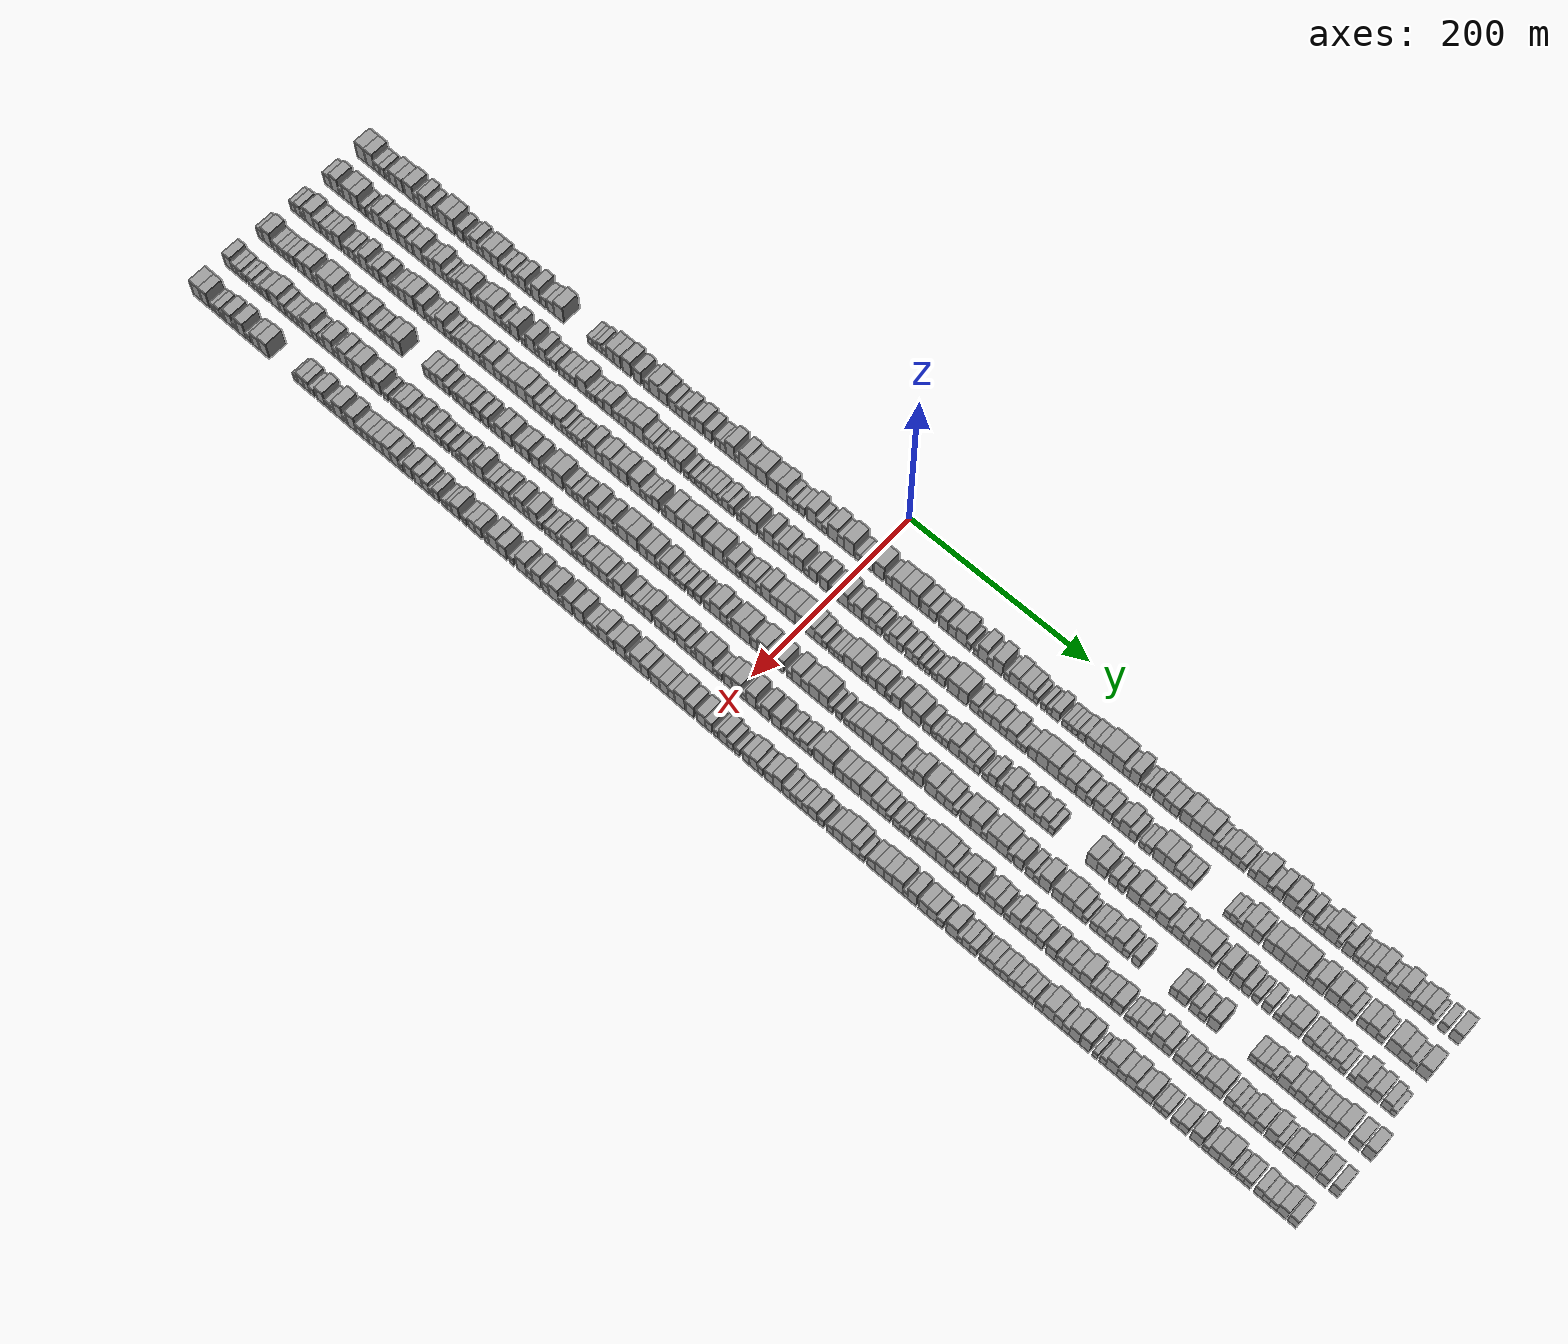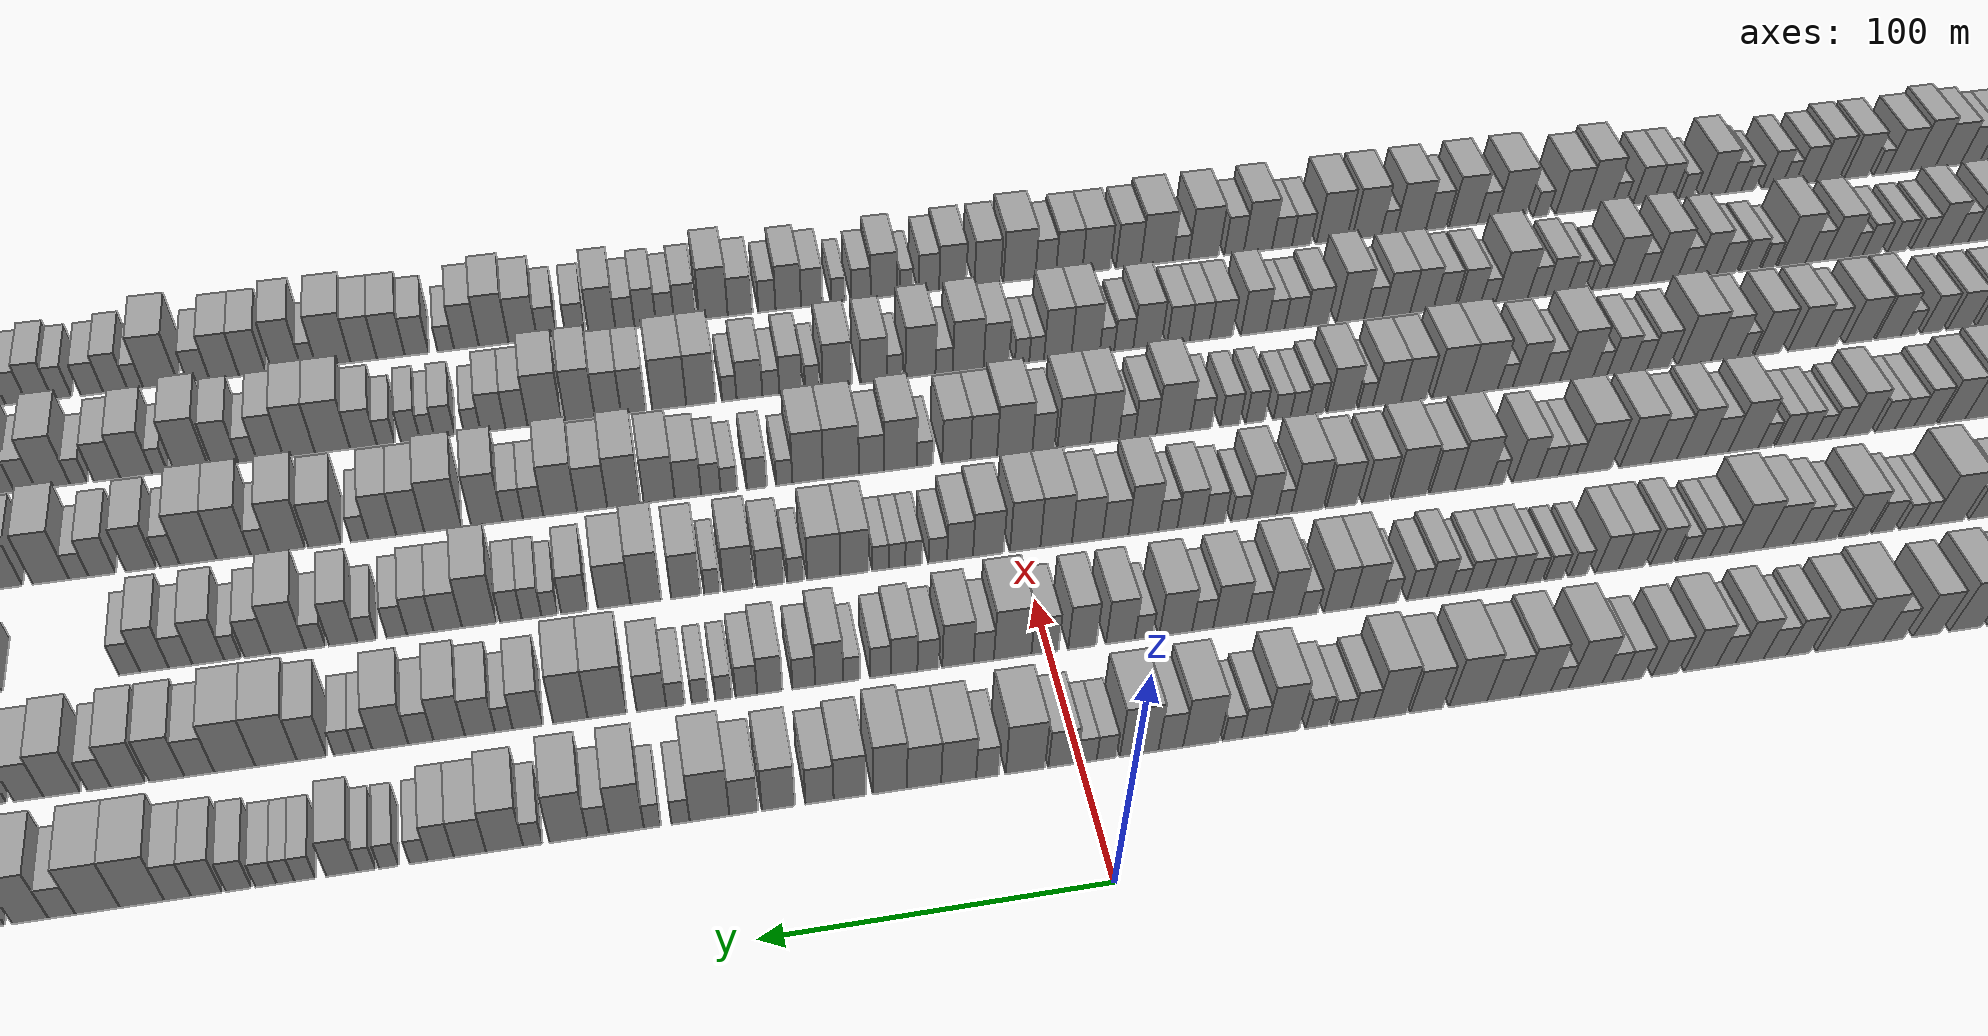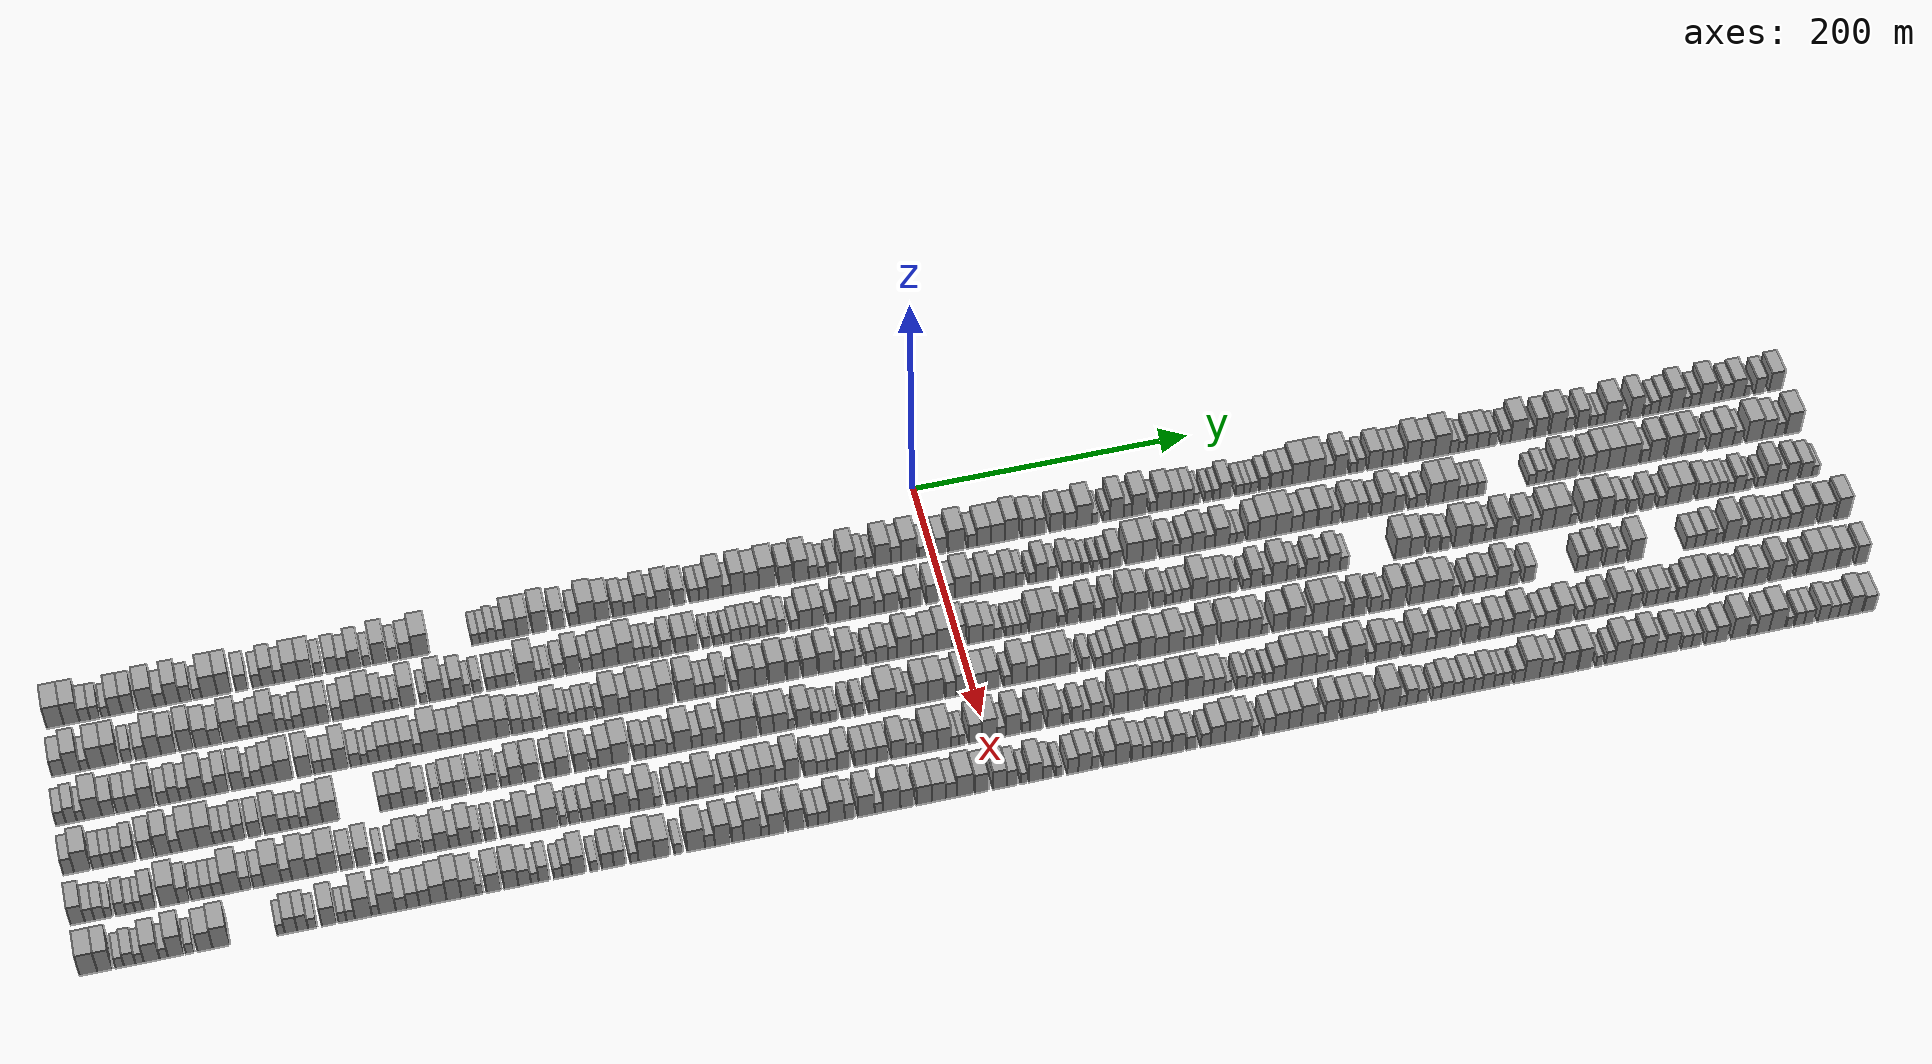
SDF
<sdf version="1.6">
 <world name="default">
  <scene>
   <sky><clouds><speed>12</speed></clouds></sky>
   <ambient>0.4 0.4 0.4 1</ambient>
   <background>0.7 0.7 0.7 1</background>
   <shadows>1</shadows>
  </scene>
  <gravity>0 0 -9.8066</gravity>
  <magnetic_field>6e-06 2.3e-05 -4.2e-05</magnetic_field>
  <physics default="0" name="default_physics" type="ode">
   <ode>
    <solver>
     <type>quick</type>
     <iters>10</iters>
     <sor>1.0</sor>
     <use_dynamic_moi_rescaling>0</use_dynamic_moi_rescaling>
    </solver>
    <constraints>
     <cfm>0</cfm>
     <erp>0.2</erp>
     <contact_max_correcting_vel>100</contact_max_correcting_vel>
     <contact_surface_layer>0.001</contact_surface_layer>
    </constraints>
   </ode>
   <max_step_size>0.004</max_step_size>
   <real_time_factor>1</real_time_factor>
   <real_time_update_rate>250</real_time_update_rate>
  </physics>
  <light name="sun" type="directional">
   <pose>0 0 10 0 0 0</pose>
   <diffuse>0.8 0.8 0.8 1</diffuse>
   <specular>0.2 0.2 0.2 1</specular>
   <attenuation>
    <range>1000</range>
    <constant>0.9</constant>
    <linear>0.01</linear>
    <quadratic>0.001</quadratic>
   </attenuation>
   <direction>-0.5 0.1 -0.9</direction>
  </light>
  <model name="building_1">
   <static>1</static>
   <pose>50.0000 -611.1319 0 0.000000 0.000000 0.000000</pose>
   <link name="link">
    <pose>0 0 12.00 0 0 0</pose>
    <collision name="collision"><geometry><box><size>20.0000 11.7361 24.0000</size></box></geometry></collision>
    <visual name="visual">
     <cast_shadows>0</cast_shadows>
     <geometry><box><size>20.0000 11.7361 24.0000</size></box></geometry>
     <material>
      <script>
       <uri>model://grey_wall/materials/scripts</uri>
       <uri>model://grey_wall/materials/textures</uri>
       <name>vrc/grey_wall</name>
      </script>
     </material>
    </visual>
   </link>
  </model>
  <model name="building_2">
   <static>1</static>
   <pose>50.0000 -599.9352 0 0.000000 0.000000 0.000000</pose>
   <link name="link">
    <pose>0 0 12.00 0 0 0</pose>
    <collision name="collision"><geometry><box><size>20.0000 10.6574 24.0000</size></box></geometry></collision>
    <visual name="visual">
     <cast_shadows>0</cast_shadows>
     <geometry><box><size>20.0000 10.6574 24.0000</size></box></geometry>
     <material>
      <script>
       <uri>model://grey_wall/materials/scripts</uri>
       <uri>model://grey_wall/materials/textures</uri>
       <name>vrc/grey_wall</name>
      </script>
     </material>
    </visual>
   </link>
  </model>
  <model name="building_3">
   <static>1</static>
   <pose>50.0000 -591.0294 0 0.000000 0.000000 0.000000</pose>
   <link name="link">
    <pose>0 0 7.50 0 0 0</pose>
    <collision name="collision"><geometry><box><size>20.0000 7.1543 15.0000</size></box></geometry></collision>
    <visual name="visual">
     <cast_shadows>0</cast_shadows>
     <geometry><box><size>20.0000 7.1543 15.0000</size></box></geometry>
     <material>
      <script>
       <uri>model://grey_wall/materials/scripts</uri>
       <uri>model://grey_wall/materials/textures</uri>
       <name>vrc/grey_wall</name>
      </script>
     </material>
    </visual>
   </link>
  </model>
  <model name="building_4">
   <static>1</static>
   <pose>50.0000 -584.0759 0 0.000000 0.000000 0.000000</pose>
   <link name="link">
    <pose>0 0 7.50 0 0 0</pose>
    <collision name="collision"><geometry><box><size>20.0000 6.7527 15.0000</size></box></geometry></collision>
    <visual name="visual">
     <cast_shadows>0</cast_shadows>
     <geometry><box><size>20.0000 6.7527 15.0000</size></box></geometry>
     <material>
      <script>
       <uri>model://grey_wall/materials/scripts</uri>
       <uri>model://grey_wall/materials/textures</uri>
       <name>vrc/grey_wall</name>
      </script>
     </material>
    </visual>
   </link>
  </model>
  <model name="building_5">
   <static>1</static>
   <pose>50.0000 -577.0518 0 0.000000 0.000000 0.000000</pose>
   <link name="link">
    <pose>0 0 6.00 0 0 0</pose>
    <collision name="collision"><geometry><box><size>20.0000 5.2955 12.0000</size></box></geometry></collision>
    <visual name="visual">
     <cast_shadows>0</cast_shadows>
     <geometry><box><size>20.0000 5.2955 12.0000</size></box></geometry>
     <material>
      <script>
       <uri>model://grey_wall/materials/scripts</uri>
       <uri>model://grey_wall/materials/textures</uri>
       <name>vrc/grey_wall</name>
      </script>
     </material>
    </visual>
   </link>
  </model>
  <model name="building_6">
   <static>1</static>
   <pose>50.0000 -569.9633 0 0.000000 0.000000 0.000000</pose>
   <link name="link">
    <pose>0 0 10.50 0 0 0</pose>
    <collision name="collision"><geometry><box><size>20.0000 8.8815 21.0000</size></box></geometry></collision>
    <visual name="visual">
     <cast_shadows>0</cast_shadows>
     <geometry><box><size>20.0000 8.8815 21.0000</size></box></geometry>
     <material>
      <script>
       <uri>model://grey_wall/materials/scripts</uri>
       <uri>model://grey_wall/materials/textures</uri>
       <name>vrc/grey_wall</name>
      </script>
     </material>
    </visual>
   </link>
  </model>
  <model name="building_7">
   <static>1</static>
   <pose>50.0000 -561.1808 0 0.000000 0.000000 0.000000</pose>
   <link name="link">
    <pose>0 0 10.50 0 0 0</pose>
    <collision name="collision"><geometry><box><size>20.0000 8.6836 21.0000</size></box></geometry></collision>
    <visual name="visual">
     <cast_shadows>0</cast_shadows>
     <geometry><box><size>20.0000 8.6836 21.0000</size></box></geometry>
     <material>
      <script>
       <uri>model://grey_wall/materials/scripts</uri>
       <uri>model://grey_wall/materials/textures</uri>
       <name>vrc/grey_wall</name>
      </script>
     </material>
    </visual>
   </link>
  </model>
  <model name="building_8">
   <static>1</static>
   <pose>50.0000 -549.0889 0 0.000000 0.000000 0.000000</pose>
   <link name="link">
    <pose>0 0 12.00 0 0 0</pose>
    <collision name="collision"><geometry><box><size>20.0000 11.5004 24.0000</size></box></geometry></collision>
    <visual name="visual">
     <cast_shadows>0</cast_shadows>
     <geometry><box><size>20.0000 11.5004 24.0000</size></box></geometry>
     <material>
      <script>
       <uri>model://grey_wall/materials/scripts</uri>
       <uri>model://grey_wall/materials/textures</uri>
       <name>vrc/grey_wall</name>
      </script>
     </material>
    </visual>
   </link>
  </model>
  <model name="building_9">
   <static>1</static>
   <pose>50.0000 -539.6591 0 0.000000 0.000000 0.000000</pose>
   <link name="link">
    <pose>0 0 7.50 0 0 0</pose>
    <collision name="collision"><geometry><box><size>20.0000 7.3591 15.0000</size></box></geometry></collision>
    <visual name="visual">
     <cast_shadows>0</cast_shadows>
     <geometry><box><size>20.0000 7.3591 15.0000</size></box></geometry>
     <material>
      <script>
       <uri>model://grey_wall/materials/scripts</uri>
       <uri>model://grey_wall/materials/textures</uri>
       <name>vrc/grey_wall</name>
      </script>
     </material>
    </visual>
   </link>
  </model>
  <model name="building_10">
   <static>1</static>
   <pose>50.0000 -531.0954 0 0.000000 0.000000 0.000000</pose>
   <link name="link">
    <pose>0 0 12.00 0 0 0</pose>
    <collision name="collision"><geometry><box><size>20.0000 9.7683 24.0000</size></box></geometry></collision>
    <visual name="visual">
     <cast_shadows>0</cast_shadows>
     <geometry><box><size>20.0000 9.7683 24.0000</size></box></geometry>
     <material>
      <script>
       <uri>model://grey_wall/materials/scripts</uri>
       <uri>model://grey_wall/materials/textures</uri>
       <name>vrc/grey_wall</name>
      </script>
     </material>
    </visual>
   </link>
  </model>
  <model name="building_11">
   <static>1</static>
   <pose>50.0000 -522.1964 0 0.000000 0.000000 0.000000</pose>
   <link name="link">
    <pose>0 0 9.00 0 0 0</pose>
    <collision name="collision"><geometry><box><size>20.0000 8.0297 18.0000</size></box></geometry></collision>
    <visual name="visual">
     <cast_shadows>0</cast_shadows>
     <geometry><box><size>20.0000 8.0297 18.0000</size></box></geometry>
     <material>
      <script>
       <uri>model://grey_wall/materials/scripts</uri>
       <uri>model://grey_wall/materials/textures</uri>
       <name>vrc/grey_wall</name>
      </script>
     </material>
    </visual>
   </link>
  </model>
  <model name="building_12">
   <static>1</static>
   <pose>50.0000 -514.4109 0 0.000000 0.000000 0.000000</pose>
   <link name="link">
    <pose>0 0 6.00 0 0 0</pose>
    <collision name="collision"><geometry><box><size>20.0000 5.5413 12.0000</size></box></geometry></collision>
    <visual name="visual">
     <cast_shadows>0</cast_shadows>
     <geometry><box><size>20.0000 5.5413 12.0000</size></box></geometry>
     <material>
      <script>
       <uri>model://grey_wall/materials/scripts</uri>
       <uri>model://grey_wall/materials/textures</uri>
       <name>vrc/grey_wall</name>
      </script>
     </material>
    </visual>
   </link>
  </model>
  <model name="building_13">
   <static>1</static>
   <pose>50.0000 -506.1963 0 0.000000 0.000000 0.000000</pose>
   <link name="link">
    <pose>0 0 12.00 0 0 0</pose>
    <collision name="collision"><geometry><box><size>20.0000 10.8880 24.0000</size></box></geometry></collision>
    <visual name="visual">
     <cast_shadows>0</cast_shadows>
     <geometry><box><size>20.0000 10.8880 24.0000</size></box></geometry>
     <material>
      <script>
       <uri>model://grey_wall/materials/scripts</uri>
       <uri>model://grey_wall/materials/textures</uri>
       <name>vrc/grey_wall</name>
      </script>
     </material>
    </visual>
   </link>
  </model>
  <model name="building_14">
   <static>1</static>
   <pose>50.0000 -495.9361 0 0.000000 0.000000 0.000000</pose>
   <link name="link">
    <pose>0 0 12.00 0 0 0</pose>
    <collision name="collision"><geometry><box><size>20.0000 9.6323 24.0000</size></box></geometry></collision>
    <visual name="visual">
     <cast_shadows>0</cast_shadows>
     <geometry><box><size>20.0000 9.6323 24.0000</size></box></geometry>
     <material>
      <script>
       <uri>model://grey_wall/materials/scripts</uri>
       <uri>model://grey_wall/materials/textures</uri>
       <name>vrc/grey_wall</name>
      </script>
     </material>
    </visual>
   </link>
  </model>
  <model name="building_15">
   <static>1</static>
   <pose>50.0000 -483.9486 0 0.000000 0.000000 0.000000</pose>
   <link name="link">
    <pose>0 0 9.00 0 0 0</pose>
    <collision name="collision"><geometry><box><size>20.0000 8.3428 18.0000</size></box></geometry></collision>
    <visual name="visual">
     <cast_shadows>0</cast_shadows>
     <geometry><box><size>20.0000 8.3428 18.0000</size></box></geometry>
     <material>
      <script>
       <uri>model://grey_wall/materials/scripts</uri>
       <uri>model://grey_wall/materials/textures</uri>
       <name>vrc/grey_wall</name>
      </script>
     </material>
    </visual>
   </link>
  </model>
  <model name="building_16">
   <static>1</static>
   <pose>50.0000 -473.6655 0 0.000000 0.000000 0.000000</pose>
   <link name="link">
    <pose>0 0 7.50 0 0 0</pose>
    <collision name="collision"><geometry><box><size>20.0000 6.2233 15.0000</size></box></geometry></collision>
    <visual name="visual">
     <cast_shadows>0</cast_shadows>
     <geometry><box><size>20.0000 6.2233 15.0000</size></box></geometry>
     <material>
      <script>
       <uri>model://grey_wall/materials/scripts</uri>
       <uri>model://grey_wall/materials/textures</uri>
       <name>vrc/grey_wall</name>
      </script>
     </material>
    </visual>
   </link>
  </model>
  <model name="building_17">
   <static>1</static>
   <pose>50.0000 -466.0045 0 0.000000 0.000000 0.000000</pose>
   <link name="link">
    <pose>0 0 10.50 0 0 0</pose>
    <collision name="collision"><geometry><box><size>20.0000 9.0988 21.0000</size></box></geometry></collision>
    <visual name="visual">
     <cast_shadows>0</cast_shadows>
     <geometry><box><size>20.0000 9.0988 21.0000</size></box></geometry>
     <material>
      <script>
       <uri>model://grey_wall/materials/scripts</uri>
       <uri>model://grey_wall/materials/textures</uri>
       <name>vrc/grey_wall</name>
      </script>
     </material>
    </visual>
   </link>
  </model>
  <model name="building_18">
   <static>1</static>
   <pose>50.0000 -458.1741 0 0.000000 0.000000 0.000000</pose>
   <link name="link">
    <pose>0 0 7.50 0 0 0</pose>
    <collision name="collision"><geometry><box><size>20.0000 6.5619 15.0000</size></box></geometry></collision>
    <visual name="visual">
     <cast_shadows>0</cast_shadows>
     <geometry><box><size>20.0000 6.5619 15.0000</size></box></geometry>
     <material>
      <script>
       <uri>model://grey_wall/materials/scripts</uri>
       <uri>model://grey_wall/materials/textures</uri>
       <name>vrc/grey_wall</name>
      </script>
     </material>
    </visual>
   </link>
  </model>
  <model name="building_19">
   <static>1</static>
   <pose>50.0000 -449.7995 0 0.000000 0.000000 0.000000</pose>
   <link name="link">
    <pose>0 0 10.50 0 0 0</pose>
    <collision name="collision"><geometry><box><size>20.0000 10.1874 21.0000</size></box></geometry></collision>
    <visual name="visual">
     <cast_shadows>0</cast_shadows>
     <geometry><box><size>20.0000 10.1874 21.0000</size></box></geometry>
     <material>
      <script>
       <uri>model://grey_wall/materials/scripts</uri>
       <uri>model://grey_wall/materials/textures</uri>
       <name>vrc/grey_wall</name>
      </script>
     </material>
    </visual>
   </link>
  </model>
  <model name="building_20">
   <static>1</static>
   <pose>50.0000 -439.9442 0 0.000000 0.000000 0.000000</pose>
   <link name="link">
    <pose>0 0 10.50 0 0 0</pose>
    <collision name="collision"><geometry><box><size>20.0000 9.5231 21.0000</size></box></geometry></collision>
    <visual name="visual">
     <cast_shadows>0</cast_shadows>
     <geometry><box><size>20.0000 9.5231 21.0000</size></box></geometry>
     <material>
      <script>
       <uri>model://grey_wall/materials/scripts</uri>
       <uri>model://grey_wall/materials/textures</uri>
       <name>vrc/grey_wall</name>
      </script>
     </material>
    </visual>
   </link>
  </model>
  <model name="building_21">
   <static>1</static>
   <pose>50.0000 -431.1389 0 0.000000 0.000000 0.000000</pose>
   <link name="link">
    <pose>0 0 7.50 0 0 0</pose>
    <collision name="collision"><geometry><box><size>20.0000 6.0876 15.0000</size></box></geometry></collision>
    <visual name="visual">
     <cast_shadows>0</cast_shadows>
     <geometry><box><size>20.0000 6.0876 15.0000</size></box></geometry>
     <material>
      <script>
       <uri>model://grey_wall/materials/scripts</uri>
       <uri>model://grey_wall/materials/textures</uri>
       <name>vrc/grey_wall</name>
      </script>
     </material>
    </visual>
   </link>
  </model>
  <model name="building_22">
   <static>1</static>
   <pose>50.0000 -421.9012 0 0.000000 0.000000 0.000000</pose>
   <link name="link">
    <pose>0 0 9.00 0 0 0</pose>
    <collision name="collision"><geometry><box><size>20.0000 8.3877 18.0000</size></box></geometry></collision>
    <visual name="visual">
     <cast_shadows>0</cast_shadows>
     <geometry><box><size>20.0000 8.3877 18.0000</size></box></geometry>
     <material>
      <script>
       <uri>model://grey_wall/materials/scripts</uri>
       <uri>model://grey_wall/materials/textures</uri>
       <name>vrc/grey_wall</name>
      </script>
     </material>
    </visual>
   </link>
  </model>
  <model name="building_23">
   <static>1</static>
   <pose>50.0000 -414.0923 0 0.000000 0.000000 0.000000</pose>
   <link name="link">
    <pose>0 0 7.50 0 0 0</pose>
    <collision name="collision"><geometry><box><size>20.0000 7.2301 15.0000</size></box></geometry></collision>
    <visual name="visual">
     <cast_shadows>0</cast_shadows>
     <geometry><box><size>20.0000 7.2301 15.0000</size></box></geometry>
     <material>
      <script>
       <uri>model://grey_wall/materials/scripts</uri>
       <uri>model://grey_wall/materials/textures</uri>
       <name>vrc/grey_wall</name>
      </script>
     </material>
    </visual>
   </link>
  </model>
  <model name="building_24">
   <static>1</static>
   <pose>50.0000 -406.0609 0 0.000000 0.000000 0.000000</pose>
   <link name="link">
    <pose>0 0 10.50 0 0 0</pose>
    <collision name="collision"><geometry><box><size>20.0000 8.8327 21.0000</size></box></geometry></collision>
    <visual name="visual">
     <cast_shadows>0</cast_shadows>
     <geometry><box><size>20.0000 8.8327 21.0000</size></box></geometry>
     <material>
      <script>
       <uri>model://grey_wall/materials/scripts</uri>
       <uri>model://grey_wall/materials/textures</uri>
       <name>vrc/grey_wall</name>
      </script>
     </material>
    </visual>
   </link>
  </model>
  <model name="building_25">
   <static>1</static>
   <pose>50.0000 -397.7985 0 0.000000 0.000000 0.000000</pose>
   <link name="link">
    <pose>0 0 6.00 0 0 0</pose>
    <collision name="collision"><geometry><box><size>20.0000 5.6922 12.0000</size></box></geometry></collision>
    <visual name="visual">
     <cast_shadows>0</cast_shadows>
     <geometry><box><size>20.0000 5.6922 12.0000</size></box></geometry>
     <material>
      <script>
       <uri>model://grey_wall/materials/scripts</uri>
       <uri>model://grey_wall/materials/textures</uri>
       <name>vrc/grey_wall</name>
      </script>
     </material>
    </visual>
   </link>
  </model>
  <model name="building_26">
   <static>1</static>
   <pose>50.0000 -388.9494 0 0.000000 0.000000 0.000000</pose>
   <link name="link">
    <pose>0 0 12.00 0 0 0</pose>
    <collision name="collision"><geometry><box><size>20.0000 10.0061 24.0000</size></box></geometry></collision>
    <visual name="visual">
     <cast_shadows>0</cast_shadows>
     <geometry><box><size>20.0000 10.0061 24.0000</size></box></geometry>
     <material>
      <script>
       <uri>model://grey_wall/materials/scripts</uri>
       <uri>model://grey_wall/materials/textures</uri>
       <name>vrc/grey_wall</name>
      </script>
     </material>
    </visual>
   </link>
  </model>
  <model name="building_27">
   <static>1</static>
   <pose>50.0000 -379.5831 0 0.000000 0.000000 0.000000</pose>
   <link name="link">
    <pose>0 0 7.50 0 0 0</pose>
    <collision name="collision"><geometry><box><size>20.0000 6.7265 15.0000</size></box></geometry></collision>
    <visual name="visual">
     <cast_shadows>0</cast_shadows>
     <geometry><box><size>20.0000 6.7265 15.0000</size></box></geometry>
     <material>
      <script>
       <uri>model://grey_wall/materials/scripts</uri>
       <uri>model://grey_wall/materials/textures</uri>
       <name>vrc/grey_wall</name>
      </script>
     </material>
    </visual>
   </link>
  </model>
  <model name="building_28">
   <static>1</static>
   <pose>50.0000 -370.9501 0 0.000000 0.000000 0.000000</pose>
   <link name="link">
    <pose>0 0 9.00 0 0 0</pose>
    <collision name="collision"><geometry><box><size>20.0000 8.5394 18.0000</size></box></geometry></collision>
    <visual name="visual">
     <cast_shadows>0</cast_shadows>
     <geometry><box><size>20.0000 8.5394 18.0000</size></box></geometry>
     <material>
      <script>
       <uri>model://grey_wall/materials/scripts</uri>
       <uri>model://grey_wall/materials/textures</uri>
       <name>vrc/grey_wall</name>
      </script>
     </material>
    </visual>
   </link>
  </model>
  <model name="building_29">
   <static>1</static>
   <pose>50.0000 -360.7772 0 0.000000 0.000000 0.000000</pose>
   <link name="link">
    <pose>0 0 12.00 0 0 0</pose>
    <collision name="collision"><geometry><box><size>20.0000 11.8064 24.0000</size></box></geometry></collision>
    <visual name="visual">
     <cast_shadows>0</cast_shadows>
     <geometry><box><size>20.0000 11.8064 24.0000</size></box></geometry>
     <material>
      <script>
       <uri>model://grey_wall/materials/scripts</uri>
       <uri>model://grey_wall/materials/textures</uri>
       <name>vrc/grey_wall</name>
      </script>
     </material>
    </visual>
   </link>
  </model>
  <model name="building_30">
   <static>1</static>
   <pose>50.0000 -322.5711 0 0.000000 0.000000 0.000000</pose>
   <link name="link">
    <pose>0 0 6.00 0 0 0</pose>
    <collision name="collision"><geometry><box><size>20.0000 5.5353 12.0000</size></box></geometry></collision>
    <visual name="visual">
     <cast_shadows>0</cast_shadows>
     <geometry><box><size>20.0000 5.5353 12.0000</size></box></geometry>
     <material>
      <script>
       <uri>model://grey_wall/materials/scripts</uri>
       <uri>model://grey_wall/materials/textures</uri>
       <name>vrc/grey_wall</name>
      </script>
     </material>
    </visual>
   </link>
  </model>
  <model name="building_31">
   <static>1</static>
   <pose>50.0000 -317.0941 0 0.000000 0.000000 0.000000</pose>
   <link name="link">
    <pose>0 0 6.00 0 0 0</pose>
    <collision name="collision"><geometry><box><size>20.0000 5.4187 12.0000</size></box></geometry></collision>
    <visual name="visual">
     <cast_shadows>0</cast_shadows>
     <geometry><box><size>20.0000 5.4187 12.0000</size></box></geometry>
     <material>
      <script>
       <uri>model://grey_wall/materials/scripts</uri>
       <uri>model://grey_wall/materials/textures</uri>
       <name>vrc/grey_wall</name>
      </script>
     </material>
    </visual>
   </link>
  </model>
  <model name="building_32">
   <static>1</static>
   <pose>50.0000 -311.3272 0 0.000000 0.000000 0.000000</pose>
   <link name="link">
    <pose>0 0 7.50 0 0 0</pose>
    <collision name="collision"><geometry><box><size>20.0000 6.1151 15.0000</size></box></geometry></collision>
    <visual name="visual">
     <cast_shadows>0</cast_shadows>
     <geometry><box><size>20.0000 6.1151 15.0000</size></box></geometry>
     <material>
      <script>
       <uri>model://grey_wall/materials/scripts</uri>
       <uri>model://grey_wall/materials/textures</uri>
       <name>vrc/grey_wall</name>
      </script>
     </material>
    </visual>
   </link>
  </model>
  <model name="building_33">
   <static>1</static>
   <pose>50.0000 -305.4539 0 0.000000 0.000000 0.000000</pose>
   <link name="link">
    <pose>0 0 6.00 0 0 0</pose>
    <collision name="collision"><geometry><box><size>20.0000 5.6317 12.0000</size></box></geometry></collision>
    <visual name="visual">
     <cast_shadows>0</cast_shadows>
     <geometry><box><size>20.0000 5.6317 12.0000</size></box></geometry>
     <material>
      <script>
       <uri>model://grey_wall/materials/scripts</uri>
       <uri>model://grey_wall/materials/textures</uri>
       <name>vrc/grey_wall</name>
      </script>
     </material>
    </visual>
   </link>
  </model>
  <model name="building_34">
   <static>1</static>
   <pose>50.0000 -298.2735 0 0.000000 0.000000 0.000000</pose>
   <link name="link">
    <pose>0 0 10.50 0 0 0</pose>
    <collision name="collision"><geometry><box><size>20.0000 8.7291 21.0000</size></box></geometry></collision>
    <visual name="visual">
     <cast_shadows>0</cast_shadows>
     <geometry><box><size>20.0000 8.7291 21.0000</size></box></geometry>
     <material>
      <script>
       <uri>model://grey_wall/materials/scripts</uri>
       <uri>model://grey_wall/materials/textures</uri>
       <name>vrc/grey_wall</name>
      </script>
     </material>
    </visual>
   </link>
  </model>
  <model name="building_35">
   <static>1</static>
   <pose>50.0000 -289.5481 0 0.000000 0.000000 0.000000</pose>
   <link name="link">
    <pose>0 0 10.50 0 0 0</pose>
    <collision name="collision"><geometry><box><size>20.0000 8.7217 21.0000</size></box></geometry></collision>
    <visual name="visual">
     <cast_shadows>0</cast_shadows>
     <geometry><box><size>20.0000 8.7217 21.0000</size></box></geometry>
     <material>
      <script>
       <uri>model://grey_wall/materials/scripts</uri>
       <uri>model://grey_wall/materials/textures</uri>
       <name>vrc/grey_wall</name>
      </script>
     </material>
    </visual>
   </link>
  </model>
  <model name="building_36">
   <static>1</static>
   <pose>50.0000 -277.8640 0 0.000000 0.000000 0.000000</pose>
   <link name="link">
    <pose>0 0 12.00 0 0 0</pose>
    <collision name="collision"><geometry><box><size>20.0000 10.6465 24.0000</size></box></geometry></collision>
    <visual name="visual">
     <cast_shadows>0</cast_shadows>
     <geometry><box><size>20.0000 10.6465 24.0000</size></box></geometry>
     <material>
      <script>
       <uri>model://grey_wall/materials/scripts</uri>
       <uri>model://grey_wall/materials/textures</uri>
       <name>vrc/grey_wall</name>
      </script>
     </material>
    </visual>
   </link>
  </model>
  <model name="building_37">
   <static>1</static>
   <pose>50.0000 -264.9912 0 0.000000 0.000000 0.000000</pose>
   <link name="link">
    <pose>0 0 10.50 0 0 0</pose>
    <collision name="collision"><geometry><box><size>20.0000 9.0991 21.0000</size></box></geometry></collision>
    <visual name="visual">
     <cast_shadows>0</cast_shadows>
     <geometry><box><size>20.0000 9.0991 21.0000</size></box></geometry>
     <material>
      <script>
       <uri>model://grey_wall/materials/scripts</uri>
       <uri>model://grey_wall/materials/textures</uri>
       <name>vrc/grey_wall</name>
      </script>
     </material>
    </visual>
   </link>
  </model>
  <model name="building_38">
   <static>1</static>
   <pose>50.0000 -254.0415 0 0.000000 0.000000 0.000000</pose>
   <link name="link">
    <pose>0 0 7.50 0 0 0</pose>
    <collision name="collision"><geometry><box><size>20.0000 6.8003 15.0000</size></box></geometry></collision>
    <visual name="visual">
     <cast_shadows>0</cast_shadows>
     <geometry><box><size>20.0000 6.8003 15.0000</size></box></geometry>
     <material>
      <script>
       <uri>model://grey_wall/materials/scripts</uri>
       <uri>model://grey_wall/materials/textures</uri>
       <name>vrc/grey_wall</name>
      </script>
     </material>
    </visual>
   </link>
  </model>
  <model name="building_39">
   <static>1</static>
   <pose>50.0000 -244.8946 0 0.000000 0.000000 0.000000</pose>
   <link name="link">
    <pose>0 0 12.00 0 0 0</pose>
    <collision name="collision"><geometry><box><size>20.0000 11.4935 24.0000</size></box></geometry></collision>
    <visual name="visual">
     <cast_shadows>0</cast_shadows>
     <geometry><box><size>20.0000 11.4935 24.0000</size></box></geometry>
     <material>
      <script>
       <uri>model://grey_wall/materials/scripts</uri>
       <uri>model://grey_wall/materials/textures</uri>
       <name>vrc/grey_wall</name>
      </script>
     </material>
    </visual>
   </link>
  </model>
  <model name="building_40">
   <static>1</static>
   <pose>50.0000 -234.0083 0 0.000000 0.000000 0.000000</pose>
   <link name="link">
    <pose>0 0 10.50 0 0 0</pose>
    <collision name="collision"><geometry><box><size>20.0000 10.2791 21.0000</size></box></geometry></collision>
    <visual name="visual">
     <cast_shadows>0</cast_shadows>
     <geometry><box><size>20.0000 10.2791 21.0000</size></box></geometry>
     <material>
      <script>
       <uri>model://grey_wall/materials/scripts</uri>
       <uri>model://grey_wall/materials/textures</uri>
       <name>vrc/grey_wall</name>
      </script>
     </material>
    </visual>
   </link>
  </model>
  <model name="building_41">
   <static>1</static>
   <pose>50.0000 -222.9935 0 0.000000 0.000000 0.000000</pose>
   <link name="link">
    <pose>0 0 9.00 0 0 0</pose>
    <collision name="collision"><geometry><box><size>20.0000 7.7505 18.0000</size></box></geometry></collision>
    <visual name="visual">
     <cast_shadows>0</cast_shadows>
     <geometry><box><size>20.0000 7.7505 18.0000</size></box></geometry>
     <material>
      <script>
       <uri>model://grey_wall/materials/scripts</uri>
       <uri>model://grey_wall/materials/textures</uri>
       <name>vrc/grey_wall</name>
      </script>
     </material>
    </visual>
   </link>
  </model>
  <model name="building_42">
   <static>1</static>
   <pose>50.0000 -215.4051 0 0.000000 0.000000 0.000000</pose>
   <link name="link">
    <pose>0 0 7.50 0 0 0</pose>
    <collision name="collision"><geometry><box><size>20.0000 7.4261 15.0000</size></box></geometry></collision>
    <visual name="visual">
     <cast_shadows>0</cast_shadows>
     <geometry><box><size>20.0000 7.4261 15.0000</size></box></geometry>
     <material>
      <script>
       <uri>model://grey_wall/materials/scripts</uri>
       <uri>model://grey_wall/materials/textures</uri>
       <name>vrc/grey_wall</name>
      </script>
     </material>
    </visual>
   </link>
  </model>
  <model name="building_43">
   <static>1</static>
   <pose>50.0000 -207.1789 0 0.000000 0.000000 0.000000</pose>
   <link name="link">
    <pose>0 0 10.50 0 0 0</pose>
    <collision name="collision"><geometry><box><size>20.0000 9.0264 21.0000</size></box></geometry></collision>
    <visual name="visual">
     <cast_shadows>0</cast_shadows>
     <geometry><box><size>20.0000 9.0264 21.0000</size></box></geometry>
     <material>
      <script>
       <uri>model://grey_wall/materials/scripts</uri>
       <uri>model://grey_wall/materials/textures</uri>
       <name>vrc/grey_wall</name>
      </script>
     </material>
    </visual>
   </link>
  </model>
  <model name="building_44">
   <static>1</static>
   <pose>50.0000 -199.5885 0 0.000000 0.000000 0.000000</pose>
   <link name="link">
    <pose>0 0 7.50 0 0 0</pose>
    <collision name="collision"><geometry><box><size>20.0000 6.1544 15.0000</size></box></geometry></collision>
    <visual name="visual">
     <cast_shadows>0</cast_shadows>
     <geometry><box><size>20.0000 6.1544 15.0000</size></box></geometry>
     <material>
      <script>
       <uri>model://grey_wall/materials/scripts</uri>
       <uri>model://grey_wall/materials/textures</uri>
       <name>vrc/grey_wall</name>
      </script>
     </material>
    </visual>
   </link>
  </model>
  <model name="building_45">
   <static>1</static>
   <pose>50.0000 -191.4024 0 0.000000 0.000000 0.000000</pose>
   <link name="link">
    <pose>0 0 10.50 0 0 0</pose>
    <collision name="collision"><geometry><box><size>20.0000 10.2178 21.0000</size></box></geometry></collision>
    <visual name="visual">
     <cast_shadows>0</cast_shadows>
     <geometry><box><size>20.0000 10.2178 21.0000</size></box></geometry>
     <material>
      <script>
       <uri>model://grey_wall/materials/scripts</uri>
       <uri>model://grey_wall/materials/textures</uri>
       <name>vrc/grey_wall</name>
      </script>
     </material>
    </visual>
   </link>
  </model>
  <model name="building_46">
   <static>1</static>
   <pose>50.0000 -180.1631 0 0.000000 0.000000 0.000000</pose>
   <link name="link">
    <pose>0 0 9.00 0 0 0</pose>
    <collision name="collision"><geometry><box><size>20.0000 8.2608 18.0000</size></box></geometry></collision>
    <visual name="visual">
     <cast_shadows>0</cast_shadows>
     <geometry><box><size>20.0000 8.2608 18.0000</size></box></geometry>
     <material>
      <script>
       <uri>model://grey_wall/materials/scripts</uri>
       <uri>model://grey_wall/materials/textures</uri>
       <name>vrc/grey_wall</name>
      </script>
     </material>
    </visual>
   </link>
  </model>
  <model name="building_47">
   <static>1</static>
   <pose>50.0000 -169.7166 0 0.000000 0.000000 0.000000</pose>
   <link name="link">
    <pose>0 0 7.50 0 0 0</pose>
    <collision name="collision"><geometry><box><size>20.0000 6.6322 15.0000</size></box></geometry></collision>
    <visual name="visual">
     <cast_shadows>0</cast_shadows>
     <geometry><box><size>20.0000 6.6322 15.0000</size></box></geometry>
     <material>
      <script>
       <uri>model://grey_wall/materials/scripts</uri>
       <uri>model://grey_wall/materials/textures</uri>
       <name>vrc/grey_wall</name>
      </script>
     </material>
    </visual>
   </link>
  </model>
  <model name="building_48">
   <static>1</static>
   <pose>50.0000 -163.2680 0 0.000000 0.000000 0.000000</pose>
   <link name="link">
    <pose>0 0 7.50 0 0 0</pose>
    <collision name="collision"><geometry><box><size>20.0000 6.2649 15.0000</size></box></geometry></collision>
    <visual name="visual">
     <cast_shadows>0</cast_shadows>
     <geometry><box><size>20.0000 6.2649 15.0000</size></box></geometry>
     <material>
      <script>
       <uri>model://grey_wall/materials/scripts</uri>
       <uri>model://grey_wall/materials/textures</uri>
       <name>vrc/grey_wall</name>
      </script>
     </material>
    </visual>
   </link>
  </model>
  <model name="building_49">
   <static>1</static>
   <pose>50.0000 -154.8369 0 0.000000 0.000000 0.000000</pose>
   <link name="link">
    <pose>0 0 12.00 0 0 0</pose>
    <collision name="collision"><geometry><box><size>20.0000 10.5972 24.0000</size></box></geometry></collision>
    <visual name="visual">
     <cast_shadows>0</cast_shadows>
     <geometry><box><size>20.0000 10.5972 24.0000</size></box></geometry>
     <material>
      <script>
       <uri>model://grey_wall/materials/scripts</uri>
       <uri>model://grey_wall/materials/textures</uri>
       <name>vrc/grey_wall</name>
      </script>
     </material>
    </visual>
   </link>
  </model>
  <model name="building_50">
   <static>1</static>
   <pose>50.0000 -146.7441 0 0.000000 0.000000 0.000000</pose>
   <link name="link">
    <pose>0 0 6.00 0 0 0</pose>
    <collision name="collision"><geometry><box><size>20.0000 5.5884 12.0000</size></box></geometry></collision>
    <visual name="visual">
     <cast_shadows>0</cast_shadows>
     <geometry><box><size>20.0000 5.5884 12.0000</size></box></geometry>
     <material>
      <script>
       <uri>model://grey_wall/materials/scripts</uri>
       <uri>model://grey_wall/materials/textures</uri>
       <name>vrc/grey_wall</name>
      </script>
     </material>
    </visual>
   </link>
  </model>
  <model name="building_51">
   <static>1</static>
   <pose>50.0000 -139.0599 0 0.000000 0.000000 0.000000</pose>
   <link name="link">
    <pose>0 0 12.00 0 0 0</pose>
    <collision name="collision"><geometry><box><size>20.0000 9.7798 24.0000</size></box></geometry></collision>
    <visual name="visual">
     <cast_shadows>0</cast_shadows>
     <geometry><box><size>20.0000 9.7798 24.0000</size></box></geometry>
     <material>
      <script>
       <uri>model://grey_wall/materials/scripts</uri>
       <uri>model://grey_wall/materials/textures</uri>
       <name>vrc/grey_wall</name>
      </script>
     </material>
    </visual>
   </link>
  </model>
  <model name="building_52">
   <static>1</static>
   <pose>50.0000 -129.0857 0 0.000000 0.000000 0.000000</pose>
   <link name="link">
    <pose>0 0 10.50 0 0 0</pose>
    <collision name="collision"><geometry><box><size>20.0000 10.1687 21.0000</size></box></geometry></collision>
    <visual name="visual">
     <cast_shadows>0</cast_shadows>
     <geometry><box><size>20.0000 10.1687 21.0000</size></box></geometry>
     <material>
      <script>
       <uri>model://grey_wall/materials/scripts</uri>
       <uri>model://grey_wall/materials/textures</uri>
       <name>vrc/grey_wall</name>
      </script>
     </material>
    </visual>
   </link>
  </model>
  <model name="building_53">
   <static>1</static>
   <pose>50.0000 -118.0740 0 0.000000 0.000000 0.000000</pose>
   <link name="link">
    <pose>0 0 12.00 0 0 0</pose>
    <collision name="collision"><geometry><box><size>20.0000 11.8548 24.0000</size></box></geometry></collision>
    <visual name="visual">
     <cast_shadows>0</cast_shadows>
     <geometry><box><size>20.0000 11.8548 24.0000</size></box></geometry>
     <material>
      <script>
       <uri>model://grey_wall/materials/scripts</uri>
       <uri>model://grey_wall/materials/textures</uri>
       <name>vrc/grey_wall</name>
      </script>
     </material>
    </visual>
   </link>
  </model>
  <model name="building_54">
   <static>1</static>
   <pose>50.0000 -105.0947 0 0.000000 0.000000 0.000000</pose>
   <link name="link">
    <pose>0 0 10.50 0 0 0</pose>
    <collision name="collision"><geometry><box><size>20.0000 10.1037 21.0000</size></box></geometry></collision>
    <visual name="visual">
     <cast_shadows>0</cast_shadows>
     <geometry><box><size>20.0000 10.1037 21.0000</size></box></geometry>
     <material>
      <script>
       <uri>model://grey_wall/materials/scripts</uri>
       <uri>model://grey_wall/materials/textures</uri>
       <name>vrc/grey_wall</name>
      </script>
     </material>
    </visual>
   </link>
  </model>
  <model name="building_55">
   <static>1</static>
   <pose>50.0000 -93.9762 0 0.000000 0.000000 0.000000</pose>
   <link name="link">
    <pose>0 0 12.00 0 0 0</pose>
    <collision name="collision"><geometry><box><size>20.0000 10.1333 24.0000</size></box></geometry></collision>
    <visual name="visual">
     <cast_shadows>0</cast_shadows>
     <geometry><box><size>20.0000 10.1333 24.0000</size></box></geometry>
     <material>
      <script>
       <uri>model://grey_wall/materials/scripts</uri>
       <uri>model://grey_wall/materials/textures</uri>
       <name>vrc/grey_wall</name>
      </script>
     </material>
    </visual>
   </link>
  </model>
  <model name="building_56">
   <static>1</static>
   <pose>50.0000 -85.4042 0 0.000000 0.000000 0.000000</pose>
   <link name="link">
    <pose>0 0 7.50 0 0 0</pose>
    <collision name="collision"><geometry><box><size>20.0000 7.0107 15.0000</size></box></geometry></collision>
    <visual name="visual">
     <cast_shadows>0</cast_shadows>
     <geometry><box><size>20.0000 7.0107 15.0000</size></box></geometry>
     <material>
      <script>
       <uri>model://grey_wall/materials/scripts</uri>
       <uri>model://grey_wall/materials/textures</uri>
       <name>vrc/grey_wall</name>
      </script>
     </material>
    </visual>
   </link>
  </model>
  <model name="building_57">
   <static>1</static>
   <pose>50.0000 -78.9322 0 0.000000 0.000000 0.000000</pose>
   <link name="link">
    <pose>0 0 6.00 0 0 0</pose>
    <collision name="collision"><geometry><box><size>20.0000 5.9334 12.0000</size></box></geometry></collision>
    <visual name="visual">
     <cast_shadows>0</cast_shadows>
     <geometry><box><size>20.0000 5.9334 12.0000</size></box></geometry>
     <material>
      <script>
       <uri>model://grey_wall/materials/scripts</uri>
       <uri>model://grey_wall/materials/textures</uri>
       <name>vrc/grey_wall</name>
      </script>
     </material>
    </visual>
   </link>
  </model>
  <model name="building_58">
   <static>1</static>
   <pose>50.0000 -71.4161 0 0.000000 0.000000 0.000000</pose>
   <link name="link">
    <pose>0 0 7.50 0 0 0</pose>
    <collision name="collision"><geometry><box><size>20.0000 7.0990 15.0000</size></box></geometry></collision>
    <visual name="visual">
     <cast_shadows>0</cast_shadows>
     <geometry><box><size>20.0000 7.0990 15.0000</size></box></geometry>
     <material>
      <script>
       <uri>model://grey_wall/materials/scripts</uri>
       <uri>model://grey_wall/materials/textures</uri>
       <name>vrc/grey_wall</name>
      </script>
     </material>
    </visual>
   </link>
  </model>
  <model name="building_59">
   <static>1</static>
   <pose>50.0000 -60.7440 0 0.000000 0.000000 0.000000</pose>
   <link name="link">
    <pose>0 0 12.00 0 0 0</pose>
    <collision name="collision"><geometry><box><size>20.0000 10.2452 24.0000</size></box></geometry></collision>
    <visual name="visual">
     <cast_shadows>0</cast_shadows>
     <geometry><box><size>20.0000 10.2452 24.0000</size></box></geometry>
     <material>
      <script>
       <uri>model://grey_wall/materials/scripts</uri>
       <uri>model://grey_wall/materials/textures</uri>
       <name>vrc/grey_wall</name>
      </script>
     </material>
    </visual>
   </link>
  </model>
  <model name="building_60">
   <static>1</static>
   <pose>50.0000 -52.0560 0 0.000000 0.000000 0.000000</pose>
   <link name="link">
    <pose>0 0 7.50 0 0 0</pose>
    <collision name="collision"><geometry><box><size>20.0000 7.1307 15.0000</size></box></geometry></collision>
    <visual name="visual">
     <cast_shadows>0</cast_shadows>
     <geometry><box><size>20.0000 7.1307 15.0000</size></box></geometry>
     <material>
      <script>
       <uri>model://grey_wall/materials/scripts</uri>
       <uri>model://grey_wall/materials/textures</uri>
       <name>vrc/grey_wall</name>
      </script>
     </material>
    </visual>
   </link>
  </model>
  <model name="building_61">
   <static>1</static>
   <pose>50.0000 -45.5938 0 0.000000 0.000000 0.000000</pose>
   <link name="link">
    <pose>0 0 6.00 0 0 0</pose>
    <collision name="collision"><geometry><box><size>20.0000 5.7937 12.0000</size></box></geometry></collision>
    <visual name="visual">
     <cast_shadows>0</cast_shadows>
     <geometry><box><size>20.0000 5.7937 12.0000</size></box></geometry>
     <material>
      <script>
       <uri>model://grey_wall/materials/scripts</uri>
       <uri>model://grey_wall/materials/textures</uri>
       <name>vrc/grey_wall</name>
      </script>
     </material>
    </visual>
   </link>
  </model>
  <model name="building_62">
   <static>1</static>
   <pose>50.0000 -36.1358 0 0.000000 0.000000 0.000000</pose>
   <link name="link">
    <pose>0 0 12.00 0 0 0</pose>
    <collision name="collision"><geometry><box><size>20.0000 11.1222 24.0000</size></box></geometry></collision>
    <visual name="visual">
     <cast_shadows>0</cast_shadows>
     <geometry><box><size>20.0000 11.1222 24.0000</size></box></geometry>
     <material>
      <script>
       <uri>model://grey_wall/materials/scripts</uri>
       <uri>model://grey_wall/materials/textures</uri>
       <name>vrc/grey_wall</name>
      </script>
     </material>
    </visual>
   </link>
  </model>
  <model name="building_63">
   <static>1</static>
   <pose>50.0000 -26.8559 0 0.000000 0.000000 0.000000</pose>
   <link name="link">
    <pose>0 0 9.00 0 0 0</pose>
    <collision name="collision"><geometry><box><size>20.0000 7.4377 18.0000</size></box></geometry></collision>
    <visual name="visual">
     <cast_shadows>0</cast_shadows>
     <geometry><box><size>20.0000 7.4377 18.0000</size></box></geometry>
     <material>
      <script>
       <uri>model://grey_wall/materials/scripts</uri>
       <uri>model://grey_wall/materials/textures</uri>
       <name>vrc/grey_wall</name>
      </script>
     </material>
    </visual>
   </link>
  </model>
  <model name="building_64">
   <static>1</static>
   <pose>50.0000 -17.3600 0 0.000000 0.000000 0.000000</pose>
   <link name="link">
    <pose>0 0 12.00 0 0 0</pose>
    <collision name="collision"><geometry><box><size>20.0000 11.5541 24.0000</size></box></geometry></collision>
    <visual name="visual">
     <cast_shadows>0</cast_shadows>
     <geometry><box><size>20.0000 11.5541 24.0000</size></box></geometry>
     <material>
      <script>
       <uri>model://grey_wall/materials/scripts</uri>
       <uri>model://grey_wall/materials/textures</uri>
       <name>vrc/grey_wall</name>
      </script>
     </material>
    </visual>
   </link>
  </model>
  <model name="building_65">
   <static>1</static>
   <pose>50.0000 -7.6387 0 0.000000 0.000000 0.000000</pose>
   <link name="link">
    <pose>0 0 6.00 0 0 0</pose>
    <collision name="collision"><geometry><box><size>20.0000 5.8884 12.0000</size></box></geometry></collision>
    <visual name="visual">
     <cast_shadows>0</cast_shadows>
     <geometry><box><size>20.0000 5.8884 12.0000</size></box></geometry>
     <material>
      <script>
       <uri>model://grey_wall/materials/scripts</uri>
       <uri>model://grey_wall/materials/textures</uri>
       <name>vrc/grey_wall</name>
      </script>
     </material>
    </visual>
   </link>
  </model>
  <model name="building_66">
   <static>1</static>
   <pose>50.0000 -1.7930 0 0.000000 0.000000 0.000000</pose>
   <link name="link">
    <pose>0 0 6.00 0 0 0</pose>
    <collision name="collision"><geometry><box><size>20.0000 5.8030 12.0000</size></box></geometry></collision>
    <visual name="visual">
     <cast_shadows>0</cast_shadows>
     <geometry><box><size>20.0000 5.8030 12.0000</size></box></geometry>
     <material>
      <script>
       <uri>model://grey_wall/materials/scripts</uri>
       <uri>model://grey_wall/materials/textures</uri>
       <name>vrc/grey_wall</name>
      </script>
     </material>
    </visual>
   </link>
  </model>
  <model name="building_67">
   <static>1</static>
   <pose>50.0000 5.4243 0 0.000000 0.000000 0.000000</pose>
   <link name="link">
    <pose>0 0 9.00 0 0 0</pose>
    <collision name="collision"><geometry><box><size>20.0000 8.6317 18.0000</size></box></geometry></collision>
    <visual name="visual">
     <cast_shadows>0</cast_shadows>
     <geometry><box><size>20.0000 8.6317 18.0000</size></box></geometry>
     <material>
      <script>
       <uri>model://grey_wall/materials/scripts</uri>
       <uri>model://grey_wall/materials/textures</uri>
       <name>vrc/grey_wall</name>
      </script>
     </material>
    </visual>
   </link>
  </model>
  <model name="building_68">
   <static>1</static>
   <pose>50.0000 16.5635 0 0.000000 0.000000 0.000000</pose>
   <link name="link">
    <pose>0 0 12.00 0 0 0</pose>
    <collision name="collision"><geometry><box><size>20.0000 11.6468 24.0000</size></box></geometry></collision>
    <visual name="visual">
     <cast_shadows>0</cast_shadows>
     <geometry><box><size>20.0000 11.6468 24.0000</size></box></geometry>
     <material>
      <script>
       <uri>model://grey_wall/materials/scripts</uri>
       <uri>model://grey_wall/materials/textures</uri>
       <name>vrc/grey_wall</name>
      </script>
     </material>
    </visual>
   </link>
  </model>
  <model name="building_69">
   <static>1</static>
   <pose>50.0000 27.7491 0 0.000000 0.000000 0.000000</pose>
   <link name="link">
    <pose>0 0 7.50 0 0 0</pose>
    <collision name="collision"><geometry><box><size>20.0000 6.7244 15.0000</size></box></geometry></collision>
    <visual name="visual">
     <cast_shadows>0</cast_shadows>
     <geometry><box><size>20.0000 6.7244 15.0000</size></box></geometry>
     <material>
      <script>
       <uri>model://grey_wall/materials/scripts</uri>
       <uri>model://grey_wall/materials/textures</uri>
       <name>vrc/grey_wall</name>
      </script>
     </material>
    </visual>
   </link>
  </model>
  <model name="building_70">
   <static>1</static>
   <pose>50.0000 36.2370 0 0.000000 0.000000 0.000000</pose>
   <link name="link">
    <pose>0 0 10.50 0 0 0</pose>
    <collision name="collision"><geometry><box><size>20.0000 10.2514 21.0000</size></box></geometry></collision>
    <visual name="visual">
     <cast_shadows>0</cast_shadows>
     <geometry><box><size>20.0000 10.2514 21.0000</size></box></geometry>
     <material>
      <script>
       <uri>model://grey_wall/materials/scripts</uri>
       <uri>model://grey_wall/materials/textures</uri>
       <name>vrc/grey_wall</name>
      </script>
     </material>
    </visual>
   </link>
  </model>
  <model name="building_71">
   <static>1</static>
   <pose>50.0000 46.3768 0 0.000000 0.000000 0.000000</pose>
   <link name="link">
    <pose>0 0 10.50 0 0 0</pose>
    <collision name="collision"><geometry><box><size>20.0000 10.0281 21.0000</size></box></geometry></collision>
    <visual name="visual">
     <cast_shadows>0</cast_shadows>
     <geometry><box><size>20.0000 10.0281 21.0000</size></box></geometry>
     <material>
      <script>
       <uri>model://grey_wall/materials/scripts</uri>
       <uri>model://grey_wall/materials/textures</uri>
       <name>vrc/grey_wall</name>
      </script>
     </material>
    </visual>
   </link>
  </model>
  <model name="building_72">
   <static>1</static>
   <pose>50.0000 56.3590 0 0.000000 0.000000 0.000000</pose>
   <link name="link">
    <pose>0 0 12.00 0 0 0</pose>
    <collision name="collision"><geometry><box><size>20.0000 9.9364 24.0000</size></box></geometry></collision>
    <visual name="visual">
     <cast_shadows>0</cast_shadows>
     <geometry><box><size>20.0000 9.9364 24.0000</size></box></geometry>
     <material>
      <script>
       <uri>model://grey_wall/materials/scripts</uri>
       <uri>model://grey_wall/materials/textures</uri>
       <name>vrc/grey_wall</name>
      </script>
     </material>
    </visual>
   </link>
  </model>
  <model name="building_73">
   <static>1</static>
   <pose>50.0000 68.0204 0 0.000000 0.000000 0.000000</pose>
   <link name="link">
    <pose>0 0 10.50 0 0 0</pose>
    <collision name="collision"><geometry><box><size>20.0000 9.3864 21.0000</size></box></geometry></collision>
    <visual name="visual">
     <cast_shadows>0</cast_shadows>
     <geometry><box><size>20.0000 9.3864 21.0000</size></box></geometry>
     <material>
      <script>
       <uri>model://grey_wall/materials/scripts</uri>
       <uri>model://grey_wall/materials/textures</uri>
       <name>vrc/grey_wall</name>
      </script>
     </material>
    </visual>
   </link>
  </model>
  <model name="building_74">
   <static>1</static>
   <pose>50.0000 76.7743 0 0.000000 0.000000 0.000000</pose>
   <link name="link">
    <pose>0 0 9.00 0 0 0</pose>
    <collision name="collision"><geometry><box><size>20.0000 8.1215 18.0000</size></box></geometry></collision>
    <visual name="visual">
     <cast_shadows>0</cast_shadows>
     <geometry><box><size>20.0000 8.1215 18.0000</size></box></geometry>
     <material>
      <script>
       <uri>model://grey_wall/materials/scripts</uri>
       <uri>model://grey_wall/materials/textures</uri>
       <name>vrc/grey_wall</name>
      </script>
     </material>
    </visual>
   </link>
  </model>
  <model name="building_75">
   <static>1</static>
   <pose>50.0000 88.6236 0 0.000000 0.000000 0.000000</pose>
   <link name="link">
    <pose>0 0 10.50 0 0 0</pose>
    <collision name="collision"><geometry><box><size>20.0000 9.5769 21.0000</size></box></geometry></collision>
    <visual name="visual">
     <cast_shadows>0</cast_shadows>
     <geometry><box><size>20.0000 9.5769 21.0000</size></box></geometry>
     <material>
      <script>
       <uri>model://grey_wall/materials/scripts</uri>
       <uri>model://grey_wall/materials/textures</uri>
       <name>vrc/grey_wall</name>
      </script>
     </material>
    </visual>
   </link>
  </model>
  <model name="building_76">
   <static>1</static>
   <pose>50.0000 98.5672 0 0.000000 0.000000 0.000000</pose>
   <link name="link">
    <pose>0 0 9.00 0 0 0</pose>
    <collision name="collision"><geometry><box><size>20.0000 8.3102 18.0000</size></box></geometry></collision>
    <visual name="visual">
     <cast_shadows>0</cast_shadows>
     <geometry><box><size>20.0000 8.3102 18.0000</size></box></geometry>
     <material>
      <script>
       <uri>model://grey_wall/materials/scripts</uri>
       <uri>model://grey_wall/materials/textures</uri>
       <name>vrc/grey_wall</name>
      </script>
     </material>
    </visual>
   </link>
  </model>
  <model name="building_77">
   <static>1</static>
   <pose>50.0000 108.3901 0 0.000000 0.000000 0.000000</pose>
   <link name="link">
    <pose>0 0 12.00 0 0 0</pose>
    <collision name="collision"><geometry><box><size>20.0000 11.3357 24.0000</size></box></geometry></collision>
    <visual name="visual">
     <cast_shadows>0</cast_shadows>
     <geometry><box><size>20.0000 11.3357 24.0000</size></box></geometry>
     <material>
      <script>
       <uri>model://grey_wall/materials/scripts</uri>
       <uri>model://grey_wall/materials/textures</uri>
       <name>vrc/grey_wall</name>
      </script>
     </material>
    </visual>
   </link>
  </model>
  <model name="building_78">
   <static>1</static>
   <pose>50.0000 116.6455 0 0.000000 0.000000 0.000000</pose>
   <link name="link">
    <pose>0 0 6.00 0 0 0</pose>
    <collision name="collision"><geometry><box><size>20.0000 5.1752 12.0000</size></box></geometry></collision>
    <visual name="visual">
     <cast_shadows>0</cast_shadows>
     <geometry><box><size>20.0000 5.1752 12.0000</size></box></geometry>
     <material>
      <script>
       <uri>model://grey_wall/materials/scripts</uri>
       <uri>model://grey_wall/materials/textures</uri>
       <name>vrc/grey_wall</name>
      </script>
     </material>
    </visual>
   </link>
  </model>
  <model name="building_79">
   <static>1</static>
   <pose>50.0000 124.6533 0 0.000000 0.000000 0.000000</pose>
   <link name="link">
    <pose>0 0 6.00 0 0 0</pose>
    <collision name="collision"><geometry><box><size>20.0000 4.8404 12.0000</size></box></geometry></collision>
    <visual name="visual">
     <cast_shadows>0</cast_shadows>
     <geometry><box><size>20.0000 4.8404 12.0000</size></box></geometry>
     <material>
      <script>
       <uri>model://grey_wall/materials/scripts</uri>
       <uri>model://grey_wall/materials/textures</uri>
       <name>vrc/grey_wall</name>
      </script>
     </material>
    </visual>
   </link>
  </model>
  <model name="building_80">
   <static>1</static>
   <pose>50.0000 131.9939 0 0.000000 0.000000 0.000000</pose>
   <link name="link">
    <pose>0 0 12.00 0 0 0</pose>
    <collision name="collision"><geometry><box><size>20.0000 9.8407 24.0000</size></box></geometry></collision>
    <visual name="visual">
     <cast_shadows>0</cast_shadows>
     <geometry><box><size>20.0000 9.8407 24.0000</size></box></geometry>
     <material>
      <script>
       <uri>model://grey_wall/materials/scripts</uri>
       <uri>model://grey_wall/materials/textures</uri>
       <name>vrc/grey_wall</name>
      </script>
     </material>
    </visual>
   </link>
  </model>
  <model name="building_81">
   <static>1</static>
   <pose>50.0000 139.9868 0 0.000000 0.000000 0.000000</pose>
   <link name="link">
    <pose>0 0 7.50 0 0 0</pose>
    <collision name="collision"><geometry><box><size>20.0000 6.1452 15.0000</size></box></geometry></collision>
    <visual name="visual">
     <cast_shadows>0</cast_shadows>
     <geometry><box><size>20.0000 6.1452 15.0000</size></box></geometry>
     <material>
      <script>
       <uri>model://grey_wall/materials/scripts</uri>
       <uri>model://grey_wall/materials/textures</uri>
       <name>vrc/grey_wall</name>
      </script>
     </material>
    </visual>
   </link>
  </model>
  <model name="building_82">
   <static>1</static>
   <pose>50.0000 148.3992 0 0.000000 0.000000 0.000000</pose>
   <link name="link">
    <pose>0 0 12.00 0 0 0</pose>
    <collision name="collision"><geometry><box><size>20.0000 10.6796 24.0000</size></box></geometry></collision>
    <visual name="visual">
     <cast_shadows>0</cast_shadows>
     <geometry><box><size>20.0000 10.6796 24.0000</size></box></geometry>
     <material>
      <script>
       <uri>model://grey_wall/materials/scripts</uri>
       <uri>model://grey_wall/materials/textures</uri>
       <name>vrc/grey_wall</name>
      </script>
     </material>
    </visual>
   </link>
  </model>
  <model name="building_83">
   <static>1</static>
   <pose>50.0000 158.4150 0 0.000000 0.000000 0.000000</pose>
   <link name="link">
    <pose>0 0 6.00 0 0 0</pose>
    <collision name="collision"><geometry><box><size>20.0000 5.3520 12.0000</size></box></geometry></collision>
    <visual name="visual">
     <cast_shadows>0</cast_shadows>
     <geometry><box><size>20.0000 5.3520 12.0000</size></box></geometry>
     <material>
      <script>
       <uri>model://grey_wall/materials/scripts</uri>
       <uri>model://grey_wall/materials/textures</uri>
       <name>vrc/grey_wall</name>
      </script>
     </material>
    </visual>
   </link>
  </model>
  <model name="building_84">
   <static>1</static>
   <pose>50.0000 166.2675 0 0.000000 0.000000 0.000000</pose>
   <link name="link">
    <pose>0 0 10.50 0 0 0</pose>
    <collision name="collision"><geometry><box><size>20.0000 10.3529 21.0000</size></box></geometry></collision>
    <visual name="visual">
     <cast_shadows>0</cast_shadows>
     <geometry><box><size>20.0000 10.3529 21.0000</size></box></geometry>
     <material>
      <script>
       <uri>model://grey_wall/materials/scripts</uri>
       <uri>model://grey_wall/materials/textures</uri>
       <name>vrc/grey_wall</name>
      </script>
     </material>
    </visual>
   </link>
  </model>
  <model name="building_85">
   <static>1</static>
   <pose>50.0000 175.9292 0 0.000000 0.000000 0.000000</pose>
   <link name="link">
    <pose>0 0 9.00 0 0 0</pose>
    <collision name="collision"><geometry><box><size>20.0000 8.9707 18.0000</size></box></geometry></collision>
    <visual name="visual">
     <cast_shadows>0</cast_shadows>
     <geometry><box><size>20.0000 8.9707 18.0000</size></box></geometry>
     <material>
      <script>
       <uri>model://grey_wall/materials/scripts</uri>
       <uri>model://grey_wall/materials/textures</uri>
       <name>vrc/grey_wall</name>
      </script>
     </material>
    </visual>
   </link>
  </model>
  <model name="building_86">
   <static>1</static>
   <pose>50.0000 184.0339 0 0.000000 0.000000 0.000000</pose>
   <link name="link">
    <pose>0 0 9.00 0 0 0</pose>
    <collision name="collision"><geometry><box><size>20.0000 7.2386 18.0000</size></box></geometry></collision>
    <visual name="visual">
     <cast_shadows>0</cast_shadows>
     <geometry><box><size>20.0000 7.2386 18.0000</size></box></geometry>
     <material>
      <script>
       <uri>model://grey_wall/materials/scripts</uri>
       <uri>model://grey_wall/materials/textures</uri>
       <name>vrc/grey_wall</name>
      </script>
     </material>
    </visual>
   </link>
  </model>
  <model name="building_87">
   <static>1</static>
   <pose>50.0000 190.1788 0 0.000000 0.000000 0.000000</pose>
   <link name="link">
    <pose>0 0 6.00 0 0 0</pose>
    <collision name="collision"><geometry><box><size>20.0000 5.0511 12.0000</size></box></geometry></collision>
    <visual name="visual">
     <cast_shadows>0</cast_shadows>
     <geometry><box><size>20.0000 5.0511 12.0000</size></box></geometry>
     <material>
      <script>
       <uri>model://grey_wall/materials/scripts</uri>
       <uri>model://grey_wall/materials/textures</uri>
       <name>vrc/grey_wall</name>
      </script>
     </material>
    </visual>
   </link>
  </model>
  <model name="building_88">
   <static>1</static>
   <pose>50.0000 198.4063 0 0.000000 0.000000 0.000000</pose>
   <link name="link">
    <pose>0 0 6.00 0 0 0</pose>
    <collision name="collision"><geometry><box><size>20.0000 5.4040 12.0000</size></box></geometry></collision>
    <visual name="visual">
     <cast_shadows>0</cast_shadows>
     <geometry><box><size>20.0000 5.4040 12.0000</size></box></geometry>
     <material>
      <script>
       <uri>model://grey_wall/materials/scripts</uri>
       <uri>model://grey_wall/materials/textures</uri>
       <name>vrc/grey_wall</name>
      </script>
     </material>
    </visual>
   </link>
  </model>
  <model name="building_89">
   <static>1</static>
   <pose>50.0000 204.5373 0 0.000000 0.000000 0.000000</pose>
   <link name="link">
    <pose>0 0 6.00 0 0 0</pose>
    <collision name="collision"><geometry><box><size>20.0000 4.8582 12.0000</size></box></geometry></collision>
    <visual name="visual">
     <cast_shadows>0</cast_shadows>
     <geometry><box><size>20.0000 4.8582 12.0000</size></box></geometry>
     <material>
      <script>
       <uri>model://grey_wall/materials/scripts</uri>
       <uri>model://grey_wall/materials/textures</uri>
       <name>vrc/grey_wall</name>
      </script>
     </material>
    </visual>
   </link>
  </model>
  <model name="building_90">
   <static>1</static>
   <pose>50.0000 211.2955 0 0.000000 0.000000 0.000000</pose>
   <link name="link">
    <pose>0 0 9.00 0 0 0</pose>
    <collision name="collision"><geometry><box><size>20.0000 8.6582 18.0000</size></box></geometry></collision>
    <visual name="visual">
     <cast_shadows>0</cast_shadows>
     <geometry><box><size>20.0000 8.6582 18.0000</size></box></geometry>
     <material>
      <script>
       <uri>model://grey_wall/materials/scripts</uri>
       <uri>model://grey_wall/materials/textures</uri>
       <name>vrc/grey_wall</name>
      </script>
     </material>
    </visual>
   </link>
  </model>
  <model name="building_91">
   <static>1</static>
   <pose>50.0000 221.4607 0 0.000000 0.000000 0.000000</pose>
   <link name="link">
    <pose>0 0 6.00 0 0 0</pose>
    <collision name="collision"><geometry><box><size>20.0000 5.6721 12.0000</size></box></geometry></collision>
    <visual name="visual">
     <cast_shadows>0</cast_shadows>
     <geometry><box><size>20.0000 5.6721 12.0000</size></box></geometry>
     <material>
      <script>
       <uri>model://grey_wall/materials/scripts</uri>
       <uri>model://grey_wall/materials/textures</uri>
       <name>vrc/grey_wall</name>
      </script>
     </material>
    </visual>
   </link>
  </model>
  <model name="building_92">
   <static>1</static>
   <pose>50.0000 226.7251 0 0.000000 0.000000 0.000000</pose>
   <link name="link">
    <pose>0 0 6.00 0 0 0</pose>
    <collision name="collision"><geometry><box><size>20.0000 4.8568 12.0000</size></box></geometry></collision>
    <visual name="visual">
     <cast_shadows>0</cast_shadows>
     <geometry><box><size>20.0000 4.8568 12.0000</size></box></geometry>
     <material>
      <script>
       <uri>model://grey_wall/materials/scripts</uri>
       <uri>model://grey_wall/materials/textures</uri>
       <name>vrc/grey_wall</name>
      </script>
     </material>
    </visual>
   </link>
  </model>
  <model name="building_93">
   <static>1</static>
   <pose>50.0000 232.0713 0 0.000000 0.000000 0.000000</pose>
   <link name="link">
    <pose>0 0 6.00 0 0 0</pose>
    <collision name="collision"><geometry><box><size>20.0000 5.8355 12.0000</size></box></geometry></collision>
    <visual name="visual">
     <cast_shadows>0</cast_shadows>
     <geometry><box><size>20.0000 5.8355 12.0000</size></box></geometry>
     <material>
      <script>
       <uri>model://grey_wall/materials/scripts</uri>
       <uri>model://grey_wall/materials/textures</uri>
       <name>vrc/grey_wall</name>
      </script>
     </material>
    </visual>
   </link>
  </model>
  <model name="building_94">
   <static>1</static>
   <pose>50.0000 239.4819 0 0.000000 0.000000 0.000000</pose>
   <link name="link">
    <pose>0 0 7.50 0 0 0</pose>
    <collision name="collision"><geometry><box><size>20.0000 6.9856 15.0000</size></box></geometry></collision>
    <visual name="visual">
     <cast_shadows>0</cast_shadows>
     <geometry><box><size>20.0000 6.9856 15.0000</size></box></geometry>
     <material>
      <script>
       <uri>model://grey_wall/materials/scripts</uri>
       <uri>model://grey_wall/materials/textures</uri>
       <name>vrc/grey_wall</name>
      </script>
     </material>
    </visual>
   </link>
  </model>
  <model name="building_95">
   <static>1</static>
   <pose>50.0000 248.1541 0 0.000000 0.000000 0.000000</pose>
   <link name="link">
    <pose>0 0 9.00 0 0 0</pose>
    <collision name="collision"><geometry><box><size>20.0000 8.3590 18.0000</size></box></geometry></collision>
    <visual name="visual">
     <cast_shadows>0</cast_shadows>
     <geometry><box><size>20.0000 8.3590 18.0000</size></box></geometry>
     <material>
      <script>
       <uri>model://grey_wall/materials/scripts</uri>
       <uri>model://grey_wall/materials/textures</uri>
       <name>vrc/grey_wall</name>
      </script>
     </material>
    </visual>
   </link>
  </model>
  <model name="building_96">
   <static>1</static>
   <pose>50.0000 255.9483 0 0.000000 0.000000 0.000000</pose>
   <link name="link">
    <pose>0 0 9.00 0 0 0</pose>
    <collision name="collision"><geometry><box><size>20.0000 7.2294 18.0000</size></box></geometry></collision>
    <visual name="visual">
     <cast_shadows>0</cast_shadows>
     <geometry><box><size>20.0000 7.2294 18.0000</size></box></geometry>
     <material>
      <script>
       <uri>model://grey_wall/materials/scripts</uri>
       <uri>model://grey_wall/materials/textures</uri>
       <name>vrc/grey_wall</name>
      </script>
     </material>
    </visual>
   </link>
  </model>
  <model name="building_97">
   <static>1</static>
   <pose>50.0000 265.5421 0 0.000000 0.000000 0.000000</pose>
   <link name="link">
    <pose>0 0 12.00 0 0 0</pose>
    <collision name="collision"><geometry><box><size>20.0000 11.9582 24.0000</size></box></geometry></collision>
    <visual name="visual">
     <cast_shadows>0</cast_shadows>
     <geometry><box><size>20.0000 11.9582 24.0000</size></box></geometry>
     <material>
      <script>
       <uri>model://grey_wall/materials/scripts</uri>
       <uri>model://grey_wall/materials/textures</uri>
       <name>vrc/grey_wall</name>
      </script>
     </material>
    </visual>
   </link>
  </model>
  <model name="building_98">
   <static>1</static>
   <pose>50.0000 277.4570 0 0.000000 0.000000 0.000000</pose>
   <link name="link">
    <pose>0 0 12.00 0 0 0</pose>
    <collision name="collision"><geometry><box><size>20.0000 11.8715 24.0000</size></box></geometry></collision>
    <visual name="visual">
     <cast_shadows>0</cast_shadows>
     <geometry><box><size>20.0000 11.8715 24.0000</size></box></geometry>
     <material>
      <script>
       <uri>model://grey_wall/materials/scripts</uri>
       <uri>model://grey_wall/materials/textures</uri>
       <name>vrc/grey_wall</name>
      </script>
     </material>
    </visual>
   </link>
  </model>
  <model name="building_99">
   <static>1</static>
   <pose>50.0000 286.9830 0 0.000000 0.000000 0.000000</pose>
   <link name="link">
    <pose>0 0 7.50 0 0 0</pose>
    <collision name="collision"><geometry><box><size>20.0000 7.1805 15.0000</size></box></geometry></collision>
    <visual name="visual">
     <cast_shadows>0</cast_shadows>
     <geometry><box><size>20.0000 7.1805 15.0000</size></box></geometry>
     <material>
      <script>
       <uri>model://grey_wall/materials/scripts</uri>
       <uri>model://grey_wall/materials/textures</uri>
       <name>vrc/grey_wall</name>
      </script>
     </material>
    </visual>
   </link>
  </model>
  <model name="building_100">
   <static>1</static>
   <pose>50.0000 295.3854 0 0.000000 0.000000 0.000000</pose>
   <link name="link">
    <pose>0 0 12.00 0 0 0</pose>
    <collision name="collision"><geometry><box><size>20.0000 9.6243 24.0000</size></box></geometry></collision>
    <visual name="visual">
     <cast_shadows>0</cast_shadows>
     <geometry><box><size>20.0000 9.6243 24.0000</size></box></geometry>
     <material>
      <script>
       <uri>model://grey_wall/materials/scripts</uri>
       <uri>model://grey_wall/materials/textures</uri>
       <name>vrc/grey_wall</name>
      </script>
     </material>
    </visual>
   </link>
  </model>
  <model name="building_101">
   <static>1</static>
   <pose>50.0000 304.7774 0 0.000000 0.000000 0.000000</pose>
   <link name="link">
    <pose>0 0 6.00 0 0 0</pose>
    <collision name="collision"><geometry><box><size>20.0000 5.1598 12.0000</size></box></geometry></collision>
    <visual name="visual">
     <cast_shadows>0</cast_shadows>
     <geometry><box><size>20.0000 5.1598 12.0000</size></box></geometry>
     <material>
      <script>
       <uri>model://grey_wall/materials/scripts</uri>
       <uri>model://grey_wall/materials/textures</uri>
       <name>vrc/grey_wall</name>
      </script>
     </material>
    </visual>
   </link>
  </model>
  <model name="building_102">
   <static>1</static>
   <pose>50.0000 310.4714 0 0.000000 0.000000 0.000000</pose>
   <link name="link">
    <pose>0 0 7.50 0 0 0</pose>
    <collision name="collision"><geometry><box><size>20.0000 6.2281 15.0000</size></box></geometry></collision>
    <visual name="visual">
     <cast_shadows>0</cast_shadows>
     <geometry><box><size>20.0000 6.2281 15.0000</size></box></geometry>
     <material>
      <script>
       <uri>model://grey_wall/materials/scripts</uri>
       <uri>model://grey_wall/materials/textures</uri>
       <name>vrc/grey_wall</name>
      </script>
     </material>
    </visual>
   </link>
  </model>
  <model name="building_103">
   <static>1</static>
   <pose>50.0000 320.6744 0 0.000000 0.000000 0.000000</pose>
   <link name="link">
    <pose>0 0 10.50 0 0 0</pose>
    <collision name="collision"><geometry><box><size>20.0000 10.1779 21.0000</size></box></geometry></collision>
    <visual name="visual">
     <cast_shadows>0</cast_shadows>
     <geometry><box><size>20.0000 10.1779 21.0000</size></box></geometry>
     <material>
      <script>
       <uri>model://grey_wall/materials/scripts</uri>
       <uri>model://grey_wall/materials/textures</uri>
       <name>vrc/grey_wall</name>
      </script>
     </material>
    </visual>
   </link>
  </model>
  <model name="building_104">
   <static>1</static>
   <pose>50.0000 329.4611 0 0.000000 0.000000 0.000000</pose>
   <link name="link">
    <pose>0 0 9.00 0 0 0</pose>
    <collision name="collision"><geometry><box><size>20.0000 7.3956 18.0000</size></box></geometry></collision>
    <visual name="visual">
     <cast_shadows>0</cast_shadows>
     <geometry><box><size>20.0000 7.3956 18.0000</size></box></geometry>
     <material>
      <script>
       <uri>model://grey_wall/materials/scripts</uri>
       <uri>model://grey_wall/materials/textures</uri>
       <name>vrc/grey_wall</name>
      </script>
     </material>
    </visual>
   </link>
  </model>
  <model name="building_105">
   <static>1</static>
   <pose>50.0000 337.3727 0 0.000000 0.000000 0.000000</pose>
   <link name="link">
    <pose>0 0 9.00 0 0 0</pose>
    <collision name="collision"><geometry><box><size>20.0000 8.4275 18.0000</size></box></geometry></collision>
    <visual name="visual">
     <cast_shadows>0</cast_shadows>
     <geometry><box><size>20.0000 8.4275 18.0000</size></box></geometry>
     <material>
      <script>
       <uri>model://grey_wall/materials/scripts</uri>
       <uri>model://grey_wall/materials/textures</uri>
       <name>vrc/grey_wall</name>
      </script>
     </material>
    </visual>
   </link>
  </model>
  <model name="building_106">
   <static>1</static>
   <pose>50.0000 348.8164 0 0.000000 0.000000 0.000000</pose>
   <link name="link">
    <pose>0 0 12.00 0 0 0</pose>
    <collision name="collision"><geometry><box><size>20.0000 10.4598 24.0000</size></box></geometry></collision>
    <visual name="visual">
     <cast_shadows>0</cast_shadows>
     <geometry><box><size>20.0000 10.4598 24.0000</size></box></geometry>
     <material>
      <script>
       <uri>model://grey_wall/materials/scripts</uri>
       <uri>model://grey_wall/materials/textures</uri>
       <name>vrc/grey_wall</name>
      </script>
     </material>
    </visual>
   </link>
  </model>
  <model name="building_107">
   <static>1</static>
   <pose>50.0000 359.2651 0 0.000000 0.000000 0.000000</pose>
   <link name="link">
    <pose>0 0 10.50 0 0 0</pose>
    <collision name="collision"><geometry><box><size>20.0000 10.4377 21.0000</size></box></geometry></collision>
    <visual name="visual">
     <cast_shadows>0</cast_shadows>
     <geometry><box><size>20.0000 10.4377 21.0000</size></box></geometry>
     <material>
      <script>
       <uri>model://grey_wall/materials/scripts</uri>
       <uri>model://grey_wall/materials/textures</uri>
       <name>vrc/grey_wall</name>
      </script>
     </material>
    </visual>
   </link>
  </model>
  <model name="building_108">
   <static>1</static>
   <pose>50.0000 370.2197 0 0.000000 0.000000 0.000000</pose>
   <link name="link">
    <pose>0 0 12.00 0 0 0</pose>
    <collision name="collision"><geometry><box><size>20.0000 11.4715 24.0000</size></box></geometry></collision>
    <visual name="visual">
     <cast_shadows>0</cast_shadows>
     <geometry><box><size>20.0000 11.4715 24.0000</size></box></geometry>
     <material>
      <script>
       <uri>model://grey_wall/materials/scripts</uri>
       <uri>model://grey_wall/materials/textures</uri>
       <name>vrc/grey_wall</name>
      </script>
     </material>
    </visual>
   </link>
  </model>
  <model name="building_109">
   <static>1</static>
   <pose>50.0000 379.0863 0 0.000000 0.000000 0.000000</pose>
   <link name="link">
    <pose>0 0 7.50 0 0 0</pose>
    <collision name="collision"><geometry><box><size>20.0000 6.2616 15.0000</size></box></geometry></collision>
    <visual name="visual">
     <cast_shadows>0</cast_shadows>
     <geometry><box><size>20.0000 6.2616 15.0000</size></box></geometry>
     <material>
      <script>
       <uri>model://grey_wall/materials/scripts</uri>
       <uri>model://grey_wall/materials/textures</uri>
       <name>vrc/grey_wall</name>
      </script>
     </material>
    </visual>
   </link>
  </model>
  <model name="building_110">
   <static>1</static>
   <pose>50.0000 385.0324 0 0.000000 0.000000 0.000000</pose>
   <link name="link">
    <pose>0 0 6.00 0 0 0</pose>
    <collision name="collision"><geometry><box><size>20.0000 5.6307 12.0000</size></box></geometry></collision>
    <visual name="visual">
     <cast_shadows>0</cast_shadows>
     <geometry><box><size>20.0000 5.6307 12.0000</size></box></geometry>
     <material>
      <script>
       <uri>model://grey_wall/materials/scripts</uri>
       <uri>model://grey_wall/materials/textures</uri>
       <name>vrc/grey_wall</name>
      </script>
     </material>
    </visual>
   </link>
  </model>
  <model name="building_111">
   <static>1</static>
   <pose>50.0000 391.9464 0 0.000000 0.000000 0.000000</pose>
   <link name="link">
    <pose>0 0 9.00 0 0 0</pose>
    <collision name="collision"><geometry><box><size>20.0000 8.1974 18.0000</size></box></geometry></collision>
    <visual name="visual">
     <cast_shadows>0</cast_shadows>
     <geometry><box><size>20.0000 8.1974 18.0000</size></box></geometry>
     <material>
      <script>
       <uri>model://grey_wall/materials/scripts</uri>
       <uri>model://grey_wall/materials/textures</uri>
       <name>vrc/grey_wall</name>
      </script>
     </material>
    </visual>
   </link>
  </model>
  <model name="building_112">
   <static>1</static>
   <pose>50.0000 400.4162 0 0.000000 0.000000 0.000000</pose>
   <link name="link">
    <pose>0 0 9.00 0 0 0</pose>
    <collision name="collision"><geometry><box><size>20.0000 8.7420 18.0000</size></box></geometry></collision>
    <visual name="visual">
     <cast_shadows>0</cast_shadows>
     <geometry><box><size>20.0000 8.7420 18.0000</size></box></geometry>
     <material>
      <script>
       <uri>model://grey_wall/materials/scripts</uri>
       <uri>model://grey_wall/materials/textures</uri>
       <name>vrc/grey_wall</name>
      </script>
     </material>
    </visual>
   </link>
  </model>
  <model name="building_113">
   <static>1</static>
   <pose>50.0000 408.0603 0 0.000000 0.000000 0.000000</pose>
   <link name="link">
    <pose>0 0 7.50 0 0 0</pose>
    <collision name="collision"><geometry><box><size>20.0000 6.5462 15.0000</size></box></geometry></collision>
    <visual name="visual">
     <cast_shadows>0</cast_shadows>
     <geometry><box><size>20.0000 6.5462 15.0000</size></box></geometry>
     <material>
      <script>
       <uri>model://grey_wall/materials/scripts</uri>
       <uri>model://grey_wall/materials/textures</uri>
       <name>vrc/grey_wall</name>
      </script>
     </material>
    </visual>
   </link>
  </model>
  <model name="building_114">
   <static>1</static>
   <pose>50.0000 417.7135 0 0.000000 0.000000 0.000000</pose>
   <link name="link">
    <pose>0 0 7.50 0 0 0</pose>
    <collision name="collision"><geometry><box><size>20.0000 6.7603 15.0000</size></box></geometry></collision>
    <visual name="visual">
     <cast_shadows>0</cast_shadows>
     <geometry><box><size>20.0000 6.7603 15.0000</size></box></geometry>
     <material>
      <script>
       <uri>model://grey_wall/materials/scripts</uri>
       <uri>model://grey_wall/materials/textures</uri>
       <name>vrc/grey_wall</name>
      </script>
     </material>
    </visual>
   </link>
  </model>
  <model name="building_115">
   <static>1</static>
   <pose>50.0000 426.8640 0 0.000000 0.000000 0.000000</pose>
   <link name="link">
    <pose>0 0 12.00 0 0 0</pose>
    <collision name="collision"><geometry><box><size>20.0000 11.5406 24.0000</size></box></geometry></collision>
    <visual name="visual">
     <cast_shadows>0</cast_shadows>
     <geometry><box><size>20.0000 11.5406 24.0000</size></box></geometry>
     <material>
      <script>
       <uri>model://grey_wall/materials/scripts</uri>
       <uri>model://grey_wall/materials/textures</uri>
       <name>vrc/grey_wall</name>
      </script>
     </material>
    </visual>
   </link>
  </model>
  <model name="building_116">
   <static>1</static>
   <pose>50.0000 435.4790 0 0.000000 0.000000 0.000000</pose>
   <link name="link">
    <pose>0 0 6.00 0 0 0</pose>
    <collision name="collision"><geometry><box><size>20.0000 5.6896 12.0000</size></box></geometry></collision>
    <visual name="visual">
     <cast_shadows>0</cast_shadows>
     <geometry><box><size>20.0000 5.6896 12.0000</size></box></geometry>
     <material>
      <script>
       <uri>model://grey_wall/materials/scripts</uri>
       <uri>model://grey_wall/materials/textures</uri>
       <name>vrc/grey_wall</name>
      </script>
     </material>
    </visual>
   </link>
  </model>
  <model name="building_117">
   <static>1</static>
   <pose>50.0000 443.9111 0 0.000000 0.000000 0.000000</pose>
   <link name="link">
    <pose>0 0 10.50 0 0 0</pose>
    <collision name="collision"><geometry><box><size>20.0000 9.1746 21.0000</size></box></geometry></collision>
    <visual name="visual">
     <cast_shadows>0</cast_shadows>
     <geometry><box><size>20.0000 9.1746 21.0000</size></box></geometry>
     <material>
      <script>
       <uri>model://grey_wall/materials/scripts</uri>
       <uri>model://grey_wall/materials/textures</uri>
       <name>vrc/grey_wall</name>
      </script>
     </material>
    </visual>
   </link>
  </model>
  <model name="building_118">
   <static>1</static>
   <pose>50.0000 456.1201 0 0.000000 0.000000 0.000000</pose>
   <link name="link">
    <pose>0 0 12.00 0 0 0</pose>
    <collision name="collision"><geometry><box><size>20.0000 11.2432 24.0000</size></box></geometry></collision>
    <visual name="visual">
     <cast_shadows>0</cast_shadows>
     <geometry><box><size>20.0000 11.2432 24.0000</size></box></geometry>
     <material>
      <script>
       <uri>model://grey_wall/materials/scripts</uri>
       <uri>model://grey_wall/materials/textures</uri>
       <name>vrc/grey_wall</name>
      </script>
     </material>
    </visual>
   </link>
  </model>
  <model name="building_119">
   <static>1</static>
   <pose>50.0000 465.0664 0 0.000000 0.000000 0.000000</pose>
   <link name="link">
    <pose>0 0 7.50 0 0 0</pose>
    <collision name="collision"><geometry><box><size>20.0000 6.6495 15.0000</size></box></geometry></collision>
    <visual name="visual">
     <cast_shadows>0</cast_shadows>
     <geometry><box><size>20.0000 6.6495 15.0000</size></box></geometry>
     <material>
      <script>
       <uri>model://grey_wall/materials/scripts</uri>
       <uri>model://grey_wall/materials/textures</uri>
       <name>vrc/grey_wall</name>
      </script>
     </material>
    </visual>
   </link>
  </model>
  <model name="building_120">
   <static>1</static>
   <pose>50.0000 474.7850 0 0.000000 0.000000 0.000000</pose>
   <link name="link">
    <pose>0 0 10.50 0 0 0</pose>
    <collision name="collision"><geometry><box><size>20.0000 8.7877 21.0000</size></box></geometry></collision>
    <visual name="visual">
     <cast_shadows>0</cast_shadows>
     <geometry><box><size>20.0000 8.7877 21.0000</size></box></geometry>
     <material>
      <script>
       <uri>model://grey_wall/materials/scripts</uri>
       <uri>model://grey_wall/materials/textures</uri>
       <name>vrc/grey_wall</name>
      </script>
     </material>
    </visual>
   </link>
  </model>
  <model name="building_121">
   <static>1</static>
   <pose>50.0000 482.8128 0 0.000000 0.000000 0.000000</pose>
   <link name="link">
    <pose>0 0 6.00 0 0 0</pose>
    <collision name="collision"><geometry><box><size>20.0000 5.2678 12.0000</size></box></geometry></collision>
    <visual name="visual">
     <cast_shadows>0</cast_shadows>
     <geometry><box><size>20.0000 5.2678 12.0000</size></box></geometry>
     <material>
      <script>
       <uri>model://grey_wall/materials/scripts</uri>
       <uri>model://grey_wall/materials/textures</uri>
       <name>vrc/grey_wall</name>
      </script>
     </material>
    </visual>
   </link>
  </model>
  <model name="building_122">
   <static>1</static>
   <pose>50.0000 488.2853 0 0.000000 0.000000 0.000000</pose>
   <link name="link">
    <pose>0 0 6.00 0 0 0</pose>
    <collision name="collision"><geometry><box><size>20.0000 5.6773 12.0000</size></box></geometry></collision>
    <visual name="visual">
     <cast_shadows>0</cast_shadows>
     <geometry><box><size>20.0000 5.6773 12.0000</size></box></geometry>
     <material>
      <script>
       <uri>model://grey_wall/materials/scripts</uri>
       <uri>model://grey_wall/materials/textures</uri>
       <name>vrc/grey_wall</name>
      </script>
     </material>
    </visual>
   </link>
  </model>
  <model name="building_123">
   <static>1</static>
   <pose>50.0000 497.0310 0 0.000000 0.000000 0.000000</pose>
   <link name="link">
    <pose>0 0 12.00 0 0 0</pose>
    <collision name="collision"><geometry><box><size>20.0000 11.8140 24.0000</size></box></geometry></collision>
    <visual name="visual">
     <cast_shadows>0</cast_shadows>
     <geometry><box><size>20.0000 11.8140 24.0000</size></box></geometry>
     <material>
      <script>
       <uri>model://grey_wall/materials/scripts</uri>
       <uri>model://grey_wall/materials/textures</uri>
       <name>vrc/grey_wall</name>
      </script>
     </material>
    </visual>
   </link>
  </model>
  <model name="building_124">
   <static>1</static>
   <pose>50.0000 505.3990 0 0.000000 0.000000 0.000000</pose>
   <link name="link">
    <pose>0 0 6.00 0 0 0</pose>
    <collision name="collision"><geometry><box><size>20.0000 4.9220 12.0000</size></box></geometry></collision>
    <visual name="visual">
     <cast_shadows>0</cast_shadows>
     <geometry><box><size>20.0000 4.9220 12.0000</size></box></geometry>
     <material>
      <script>
       <uri>model://grey_wall/materials/scripts</uri>
       <uri>model://grey_wall/materials/textures</uri>
       <name>vrc/grey_wall</name>
      </script>
     </material>
    </visual>
   </link>
  </model>
  <model name="building_125">
   <static>1</static>
   <pose>50.0000 514.6741 0 0.000000 0.000000 0.000000</pose>
   <link name="link">
    <pose>0 0 12.00 0 0 0</pose>
    <collision name="collision"><geometry><box><size>20.0000 9.6282 24.0000</size></box></geometry></collision>
    <visual name="visual">
     <cast_shadows>0</cast_shadows>
     <geometry><box><size>20.0000 9.6282 24.0000</size></box></geometry>
     <material>
      <script>
       <uri>model://grey_wall/materials/scripts</uri>
       <uri>model://grey_wall/materials/textures</uri>
       <name>vrc/grey_wall</name>
      </script>
     </material>
    </visual>
   </link>
  </model>
  <model name="building_126">
   <static>1</static>
   <pose>50.0000 522.9411 0 0.000000 0.000000 0.000000</pose>
   <link name="link">
    <pose>0 0 6.00 0 0 0</pose>
    <collision name="collision"><geometry><box><size>20.0000 4.9058 12.0000</size></box></geometry></collision>
    <visual name="visual">
     <cast_shadows>0</cast_shadows>
     <geometry><box><size>20.0000 4.9058 12.0000</size></box></geometry>
     <material>
      <script>
       <uri>model://grey_wall/materials/scripts</uri>
       <uri>model://grey_wall/materials/textures</uri>
       <name>vrc/grey_wall</name>
      </script>
     </material>
    </visual>
   </link>
  </model>
  <model name="building_127">
   <static>1</static>
   <pose>50.0000 528.6047 0 0.000000 0.000000 0.000000</pose>
   <link name="link">
    <pose>0 0 7.50 0 0 0</pose>
    <collision name="collision"><geometry><box><size>20.0000 6.4215 15.0000</size></box></geometry></collision>
    <visual name="visual">
     <cast_shadows>0</cast_shadows>
     <geometry><box><size>20.0000 6.4215 15.0000</size></box></geometry>
     <material>
      <script>
       <uri>model://grey_wall/materials/scripts</uri>
       <uri>model://grey_wall/materials/textures</uri>
       <name>vrc/grey_wall</name>
      </script>
     </material>
    </visual>
   </link>
  </model>
  <model name="building_128">
   <static>1</static>
   <pose>50.0000 535.7948 0 0.000000 0.000000 0.000000</pose>
   <link name="link">
    <pose>0 0 9.00 0 0 0</pose>
    <collision name="collision"><geometry><box><size>20.0000 7.9586 18.0000</size></box></geometry></collision>
    <visual name="visual">
     <cast_shadows>0</cast_shadows>
     <geometry><box><size>20.0000 7.9586 18.0000</size></box></geometry>
     <material>
      <script>
       <uri>model://grey_wall/materials/scripts</uri>
       <uri>model://grey_wall/materials/textures</uri>
       <name>vrc/grey_wall</name>
      </script>
     </material>
    </visual>
   </link>
  </model>
  <model name="building_129">
   <static>1</static>
   <pose>50.0000 544.9164 0 0.000000 0.000000 0.000000</pose>
   <link name="link">
    <pose>0 0 12.00 0 0 0</pose>
    <collision name="collision"><geometry><box><size>20.0000 10.2847 24.0000</size></box></geometry></collision>
    <visual name="visual">
     <cast_shadows>0</cast_shadows>
     <geometry><box><size>20.0000 10.2847 24.0000</size></box></geometry>
     <material>
      <script>
       <uri>model://grey_wall/materials/scripts</uri>
       <uri>model://grey_wall/materials/textures</uri>
       <name>vrc/grey_wall</name>
      </script>
     </material>
    </visual>
   </link>
  </model>
  <model name="building_130">
   <static>1</static>
   <pose>50.0000 552.8706 0 0.000000 0.000000 0.000000</pose>
   <link name="link">
    <pose>0 0 6.00 0 0 0</pose>
    <collision name="collision"><geometry><box><size>20.0000 5.6236 12.0000</size></box></geometry></collision>
    <visual name="visual">
     <cast_shadows>0</cast_shadows>
     <geometry><box><size>20.0000 5.6236 12.0000</size></box></geometry>
     <material>
      <script>
       <uri>model://grey_wall/materials/scripts</uri>
       <uri>model://grey_wall/materials/textures</uri>
       <name>vrc/grey_wall</name>
      </script>
     </material>
    </visual>
   </link>
  </model>
  <model name="building_131">
   <static>1</static>
   <pose>50.0000 559.1392 0 0.000000 0.000000 0.000000</pose>
   <link name="link">
    <pose>0 0 7.50 0 0 0</pose>
    <collision name="collision"><geometry><box><size>20.0000 6.9136 15.0000</size></box></geometry></collision>
    <visual name="visual">
     <cast_shadows>0</cast_shadows>
     <geometry><box><size>20.0000 6.9136 15.0000</size></box></geometry>
     <material>
      <script>
       <uri>model://grey_wall/materials/scripts</uri>
       <uri>model://grey_wall/materials/textures</uri>
       <name>vrc/grey_wall</name>
      </script>
     </material>
    </visual>
   </link>
  </model>
  <model name="building_132">
   <static>1</static>
   <pose>50.0000 568.0410 0 0.000000 0.000000 0.000000</pose>
   <link name="link">
    <pose>0 0 12.00 0 0 0</pose>
    <collision name="collision"><geometry><box><size>20.0000 10.8900 24.0000</size></box></geometry></collision>
    <visual name="visual">
     <cast_shadows>0</cast_shadows>
     <geometry><box><size>20.0000 10.8900 24.0000</size></box></geometry>
     <material>
      <script>
       <uri>model://grey_wall/materials/scripts</uri>
       <uri>model://grey_wall/materials/textures</uri>
       <name>vrc/grey_wall</name>
      </script>
     </material>
    </visual>
   </link>
  </model>
  <model name="building_133">
   <static>1</static>
   <pose>50.0000 576.1920 0 0.000000 0.000000 0.000000</pose>
   <link name="link">
    <pose>0 0 6.00 0 0 0</pose>
    <collision name="collision"><geometry><box><size>20.0000 5.4120 12.0000</size></box></geometry></collision>
    <visual name="visual">
     <cast_shadows>0</cast_shadows>
     <geometry><box><size>20.0000 5.4120 12.0000</size></box></geometry>
     <material>
      <script>
       <uri>model://grey_wall/materials/scripts</uri>
       <uri>model://grey_wall/materials/textures</uri>
       <name>vrc/grey_wall</name>
      </script>
     </material>
    </visual>
   </link>
  </model>
  <model name="building_134">
   <static>1</static>
   <pose>50.0000 582.8056 0 0.000000 0.000000 0.000000</pose>
   <link name="link">
    <pose>0 0 9.00 0 0 0</pose>
    <collision name="collision"><geometry><box><size>20.0000 7.8151 18.0000</size></box></geometry></collision>
    <visual name="visual">
     <cast_shadows>0</cast_shadows>
     <geometry><box><size>20.0000 7.8151 18.0000</size></box></geometry>
     <material>
      <script>
       <uri>model://grey_wall/materials/scripts</uri>
       <uri>model://grey_wall/materials/textures</uri>
       <name>vrc/grey_wall</name>
      </script>
     </material>
    </visual>
   </link>
  </model>
  <model name="building_135">
   <static>1</static>
   <pose>50.0000 591.5448 0 0.000000 0.000000 0.000000</pose>
   <link name="link">
    <pose>0 0 10.50 0 0 0</pose>
    <collision name="collision"><geometry><box><size>20.0000 9.6633 21.0000</size></box></geometry></collision>
    <visual name="visual">
     <cast_shadows>0</cast_shadows>
     <geometry><box><size>20.0000 9.6633 21.0000</size></box></geometry>
     <material>
      <script>
       <uri>model://grey_wall/materials/scripts</uri>
       <uri>model://grey_wall/materials/textures</uri>
       <name>vrc/grey_wall</name>
      </script>
     </material>
    </visual>
   </link>
  </model>
  <model name="building_136">
   <static>1</static>
   <pose>50.0000 598.8122 0 0.000000 0.000000 0.000000</pose>
   <link name="link">
    <pose>0 0 6.00 0 0 0</pose>
    <collision name="collision"><geometry><box><size>20.0000 4.8717 12.0000</size></box></geometry></collision>
    <visual name="visual">
     <cast_shadows>0</cast_shadows>
     <geometry><box><size>20.0000 4.8717 12.0000</size></box></geometry>
     <material>
      <script>
       <uri>model://grey_wall/materials/scripts</uri>
       <uri>model://grey_wall/materials/textures</uri>
       <name>vrc/grey_wall</name>
      </script>
     </material>
    </visual>
   </link>
  </model>
  <model name="building_137">
   <static>1</static>
   <pose>50.0000 608.2025 0 0.000000 0.000000 0.000000</pose>
   <link name="link">
    <pose>0 0 9.00 0 0 0</pose>
    <collision name="collision"><geometry><box><size>20.0000 7.9088 18.0000</size></box></geometry></collision>
    <visual name="visual">
     <cast_shadows>0</cast_shadows>
     <geometry><box><size>20.0000 7.9088 18.0000</size></box></geometry>
     <material>
      <script>
       <uri>model://grey_wall/materials/scripts</uri>
       <uri>model://grey_wall/materials/textures</uri>
       <name>vrc/grey_wall</name>
      </script>
     </material>
    </visual>
   </link>
  </model>
  <model name="building_138">
   <static>1</static>
   <pose>50.0000 620.1896 0 0.000000 0.000000 0.000000</pose>
   <link name="link">
    <pose>0 0 10.50 0 0 0</pose>
    <collision name="collision"><geometry><box><size>20.0000 10.0654 21.0000</size></box></geometry></collision>
    <visual name="visual">
     <cast_shadows>0</cast_shadows>
     <geometry><box><size>20.0000 10.0654 21.0000</size></box></geometry>
     <material>
      <script>
       <uri>model://grey_wall/materials/scripts</uri>
       <uri>model://grey_wall/materials/textures</uri>
       <name>vrc/grey_wall</name>
      </script>
     </material>
    </visual>
   </link>
  </model>
  <model name="building_139">
   <static>1</static>
   <pose>90.0000 -613.5247 0 0.000000 0.000000 0.000000</pose>
   <link name="link">
    <pose>0 0 9.00 0 0 0</pose>
    <collision name="collision"><geometry><box><size>20.0000 8.9505 18.0000</size></box></geometry></collision>
    <visual name="visual">
     <cast_shadows>0</cast_shadows>
     <geometry><box><size>20.0000 8.9505 18.0000</size></box></geometry>
     <material>
      <script>
       <uri>model://grey_wall/materials/scripts</uri>
       <uri>model://grey_wall/materials/textures</uri>
       <name>vrc/grey_wall</name>
      </script>
     </material>
    </visual>
   </link>
  </model>
  <model name="building_140">
   <static>1</static>
   <pose>90.0000 -603.8955 0 0.000000 0.000000 0.000000</pose>
   <link name="link">
    <pose>0 0 12.00 0 0 0</pose>
    <collision name="collision"><geometry><box><size>20.0000 10.3079 24.0000</size></box></geometry></collision>
    <visual name="visual">
     <cast_shadows>0</cast_shadows>
     <geometry><box><size>20.0000 10.3079 24.0000</size></box></geometry>
     <material>
      <script>
       <uri>model://grey_wall/materials/scripts</uri>
       <uri>model://grey_wall/materials/textures</uri>
       <name>vrc/grey_wall</name>
      </script>
     </material>
    </visual>
   </link>
  </model>
  <model name="building_141">
   <static>1</static>
   <pose>90.0000 -595.9111 0 0.000000 0.000000 0.000000</pose>
   <link name="link">
    <pose>0 0 6.00 0 0 0</pose>
    <collision name="collision"><geometry><box><size>20.0000 5.6610 12.0000</size></box></geometry></collision>
    <visual name="visual">
     <cast_shadows>0</cast_shadows>
     <geometry><box><size>20.0000 5.6610 12.0000</size></box></geometry>
     <material>
      <script>
       <uri>model://grey_wall/materials/scripts</uri>
       <uri>model://grey_wall/materials/textures</uri>
       <name>vrc/grey_wall</name>
      </script>
     </material>
    </visual>
   </link>
  </model>
  <model name="building_142">
   <static>1</static>
   <pose>90.0000 -587.7141 0 0.000000 0.000000 0.000000</pose>
   <link name="link">
    <pose>0 0 12.00 0 0 0</pose>
    <collision name="collision"><geometry><box><size>20.0000 10.7329 24.0000</size></box></geometry></collision>
    <visual name="visual">
     <cast_shadows>0</cast_shadows>
     <geometry><box><size>20.0000 10.7329 24.0000</size></box></geometry>
     <material>
      <script>
       <uri>model://grey_wall/materials/scripts</uri>
       <uri>model://grey_wall/materials/textures</uri>
       <name>vrc/grey_wall</name>
      </script>
     </material>
    </visual>
   </link>
  </model>
  <model name="building_143">
   <static>1</static>
   <pose>90.0000 -577.4683 0 0.000000 0.000000 0.000000</pose>
   <link name="link">
    <pose>0 0 12.00 0 0 0</pose>
    <collision name="collision"><geometry><box><size>20.0000 9.7588 24.0000</size></box></geometry></collision>
    <visual name="visual">
     <cast_shadows>0</cast_shadows>
     <geometry><box><size>20.0000 9.7588 24.0000</size></box></geometry>
     <material>
      <script>
       <uri>model://grey_wall/materials/scripts</uri>
       <uri>model://grey_wall/materials/textures</uri>
       <name>vrc/grey_wall</name>
      </script>
     </material>
    </visual>
   </link>
  </model>
  <model name="building_144">
   <static>1</static>
   <pose>90.0000 -567.1206 0 0.000000 0.000000 0.000000</pose>
   <link name="link">
    <pose>0 0 7.50 0 0 0</pose>
    <collision name="collision"><geometry><box><size>20.0000 6.9365 15.0000</size></box></geometry></collision>
    <visual name="visual">
     <cast_shadows>0</cast_shadows>
     <geometry><box><size>20.0000 6.9365 15.0000</size></box></geometry>
     <material>
      <script>
       <uri>model://grey_wall/materials/scripts</uri>
       <uri>model://grey_wall/materials/textures</uri>
       <name>vrc/grey_wall</name>
      </script>
     </material>
    </visual>
   </link>
  </model>
  <model name="building_145">
   <static>1</static>
   <pose>90.0000 -558.0326 0 0.000000 0.000000 0.000000</pose>
   <link name="link">
    <pose>0 0 7.50 0 0 0</pose>
    <collision name="collision"><geometry><box><size>20.0000 7.2395 15.0000</size></box></geometry></collision>
    <visual name="visual">
     <cast_shadows>0</cast_shadows>
     <geometry><box><size>20.0000 7.2395 15.0000</size></box></geometry>
     <material>
      <script>
       <uri>model://grey_wall/materials/scripts</uri>
       <uri>model://grey_wall/materials/textures</uri>
       <name>vrc/grey_wall</name>
      </script>
     </material>
    </visual>
   </link>
  </model>
  <model name="building_146">
   <static>1</static>
   <pose>90.0000 -549.4258 0 0.000000 0.000000 0.000000</pose>
   <link name="link">
    <pose>0 0 12.00 0 0 0</pose>
    <collision name="collision"><geometry><box><size>20.0000 9.9741 24.0000</size></box></geometry></collision>
    <visual name="visual">
     <cast_shadows>0</cast_shadows>
     <geometry><box><size>20.0000 9.9741 24.0000</size></box></geometry>
     <material>
      <script>
       <uri>model://grey_wall/materials/scripts</uri>
       <uri>model://grey_wall/materials/textures</uri>
       <name>vrc/grey_wall</name>
      </script>
     </material>
    </visual>
   </link>
  </model>
  <model name="building_147">
   <static>1</static>
   <pose>90.0000 -539.3136 0 0.000000 0.000000 0.000000</pose>
   <link name="link">
    <pose>0 0 10.50 0 0 0</pose>
    <collision name="collision"><geometry><box><size>20.0000 10.2503 21.0000</size></box></geometry></collision>
    <visual name="visual">
     <cast_shadows>0</cast_shadows>
     <geometry><box><size>20.0000 10.2503 21.0000</size></box></geometry>
     <material>
      <script>
       <uri>model://grey_wall/materials/scripts</uri>
       <uri>model://grey_wall/materials/textures</uri>
       <name>vrc/grey_wall</name>
      </script>
     </material>
    </visual>
   </link>
  </model>
  <model name="building_148">
   <static>1</static>
   <pose>90.0000 -527.3125 0 0.000000 0.000000 0.000000</pose>
   <link name="link">
    <pose>0 0 12.00 0 0 0</pose>
    <collision name="collision"><geometry><box><size>20.0000 9.7519 24.0000</size></box></geometry></collision>
    <visual name="visual">
     <cast_shadows>0</cast_shadows>
     <geometry><box><size>20.0000 9.7519 24.0000</size></box></geometry>
     <material>
      <script>
       <uri>model://grey_wall/materials/scripts</uri>
       <uri>model://grey_wall/materials/textures</uri>
       <name>vrc/grey_wall</name>
      </script>
     </material>
    </visual>
   </link>
  </model>
  <model name="building_149">
   <static>1</static>
   <pose>90.0000 -516.5032 0 0.000000 0.000000 0.000000</pose>
   <link name="link">
    <pose>0 0 10.50 0 0 0</pose>
    <collision name="collision"><geometry><box><size>20.0000 9.8669 21.0000</size></box></geometry></collision>
    <visual name="visual">
     <cast_shadows>0</cast_shadows>
     <geometry><box><size>20.0000 9.8669 21.0000</size></box></geometry>
     <material>
      <script>
       <uri>model://grey_wall/materials/scripts</uri>
       <uri>model://grey_wall/materials/textures</uri>
       <name>vrc/grey_wall</name>
      </script>
     </material>
    </visual>
   </link>
  </model>
  <model name="building_150">
   <static>1</static>
   <pose>90.0000 -507.4318 0 0.000000 0.000000 0.000000</pose>
   <link name="link">
    <pose>0 0 9.00 0 0 0</pose>
    <collision name="collision"><geometry><box><size>20.0000 8.2759 18.0000</size></box></geometry></collision>
    <visual name="visual">
     <cast_shadows>0</cast_shadows>
     <geometry><box><size>20.0000 8.2759 18.0000</size></box></geometry>
     <material>
      <script>
       <uri>model://grey_wall/materials/scripts</uri>
       <uri>model://grey_wall/materials/textures</uri>
       <name>vrc/grey_wall</name>
      </script>
     </material>
    </visual>
   </link>
  </model>
  <model name="building_151">
   <static>1</static>
   <pose>90.0000 -496.7005 0 0.000000 0.000000 0.000000</pose>
   <link name="link">
    <pose>0 0 12.00 0 0 0</pose>
    <collision name="collision"><geometry><box><size>20.0000 11.1866 24.0000</size></box></geometry></collision>
    <visual name="visual">
     <cast_shadows>0</cast_shadows>
     <geometry><box><size>20.0000 11.1866 24.0000</size></box></geometry>
     <material>
      <script>
       <uri>model://grey_wall/materials/scripts</uri>
       <uri>model://grey_wall/materials/textures</uri>
       <name>vrc/grey_wall</name>
      </script>
     </material>
    </visual>
   </link>
  </model>
  <model name="building_152">
   <static>1</static>
   <pose>90.0000 -487.4427 0 0.000000 0.000000 0.000000</pose>
   <link name="link">
    <pose>0 0 7.50 0 0 0</pose>
    <collision name="collision"><geometry><box><size>20.0000 7.3288 15.0000</size></box></geometry></collision>
    <visual name="visual">
     <cast_shadows>0</cast_shadows>
     <geometry><box><size>20.0000 7.3288 15.0000</size></box></geometry>
     <material>
      <script>
       <uri>model://grey_wall/materials/scripts</uri>
       <uri>model://grey_wall/materials/textures</uri>
       <name>vrc/grey_wall</name>
      </script>
     </material>
    </visual>
   </link>
  </model>
  <model name="building_153">
   <static>1</static>
   <pose>90.0000 -479.9541 0 0.000000 0.000000 0.000000</pose>
   <link name="link">
    <pose>0 0 9.00 0 0 0</pose>
    <collision name="collision"><geometry><box><size>20.0000 7.6484 18.0000</size></box></geometry></collision>
    <visual name="visual">
     <cast_shadows>0</cast_shadows>
     <geometry><box><size>20.0000 7.6484 18.0000</size></box></geometry>
     <material>
      <script>
       <uri>model://grey_wall/materials/scripts</uri>
       <uri>model://grey_wall/materials/textures</uri>
       <name>vrc/grey_wall</name>
      </script>
     </material>
    </visual>
   </link>
  </model>
  <model name="building_154">
   <static>1</static>
   <pose>90.0000 -471.0406 0 0.000000 0.000000 0.000000</pose>
   <link name="link">
    <pose>0 0 12.00 0 0 0</pose>
    <collision name="collision"><geometry><box><size>20.0000 10.1787 24.0000</size></box></geometry></collision>
    <visual name="visual">
     <cast_shadows>0</cast_shadows>
     <geometry><box><size>20.0000 10.1787 24.0000</size></box></geometry>
     <material>
      <script>
       <uri>model://grey_wall/materials/scripts</uri>
       <uri>model://grey_wall/materials/textures</uri>
       <name>vrc/grey_wall</name>
      </script>
     </material>
    </visual>
   </link>
  </model>
  <model name="building_155">
   <static>1</static>
   <pose>90.0000 -462.6924 0 0.000000 0.000000 0.000000</pose>
   <link name="link">
    <pose>0 0 7.50 0 0 0</pose>
    <collision name="collision"><geometry><box><size>20.0000 6.5176 15.0000</size></box></geometry></collision>
    <visual name="visual">
     <cast_shadows>0</cast_shadows>
     <geometry><box><size>20.0000 6.5176 15.0000</size></box></geometry>
     <material>
      <script>
       <uri>model://grey_wall/materials/scripts</uri>
       <uri>model://grey_wall/materials/textures</uri>
       <name>vrc/grey_wall</name>
      </script>
     </material>
    </visual>
   </link>
  </model>
  <model name="building_156">
   <static>1</static>
   <pose>90.0000 -456.9535 0 0.000000 0.000000 0.000000</pose>
   <link name="link">
    <pose>0 0 6.00 0 0 0</pose>
    <collision name="collision"><geometry><box><size>20.0000 4.9603 12.0000</size></box></geometry></collision>
    <visual name="visual">
     <cast_shadows>0</cast_shadows>
     <geometry><box><size>20.0000 4.9603 12.0000</size></box></geometry>
     <material>
      <script>
       <uri>model://grey_wall/materials/scripts</uri>
       <uri>model://grey_wall/materials/textures</uri>
       <name>vrc/grey_wall</name>
      </script>
     </material>
    </visual>
   </link>
  </model>
  <model name="building_157">
   <static>1</static>
   <pose>90.0000 -450.9360 0 0.000000 0.000000 0.000000</pose>
   <link name="link">
    <pose>0 0 7.50 0 0 0</pose>
    <collision name="collision"><geometry><box><size>20.0000 7.0747 15.0000</size></box></geometry></collision>
    <visual name="visual">
     <cast_shadows>0</cast_shadows>
     <geometry><box><size>20.0000 7.0747 15.0000</size></box></geometry>
     <material>
      <script>
       <uri>model://grey_wall/materials/scripts</uri>
       <uri>model://grey_wall/materials/textures</uri>
       <name>vrc/grey_wall</name>
      </script>
     </material>
    </visual>
   </link>
  </model>
  <model name="building_158">
   <static>1</static>
   <pose>90.0000 -442.7966 0 0.000000 0.000000 0.000000</pose>
   <link name="link">
    <pose>0 0 10.50 0 0 0</pose>
    <collision name="collision"><geometry><box><size>20.0000 9.2040 21.0000</size></box></geometry></collision>
    <visual name="visual">
     <cast_shadows>0</cast_shadows>
     <geometry><box><size>20.0000 9.2040 21.0000</size></box></geometry>
     <material>
      <script>
       <uri>model://grey_wall/materials/scripts</uri>
       <uri>model://grey_wall/materials/textures</uri>
       <name>vrc/grey_wall</name>
      </script>
     </material>
    </visual>
   </link>
  </model>
  <model name="building_159">
   <static>1</static>
   <pose>90.0000 -433.9393 0 0.000000 0.000000 0.000000</pose>
   <link name="link">
    <pose>0 0 10.50 0 0 0</pose>
    <collision name="collision"><geometry><box><size>20.0000 8.5106 21.0000</size></box></geometry></collision>
    <visual name="visual">
     <cast_shadows>0</cast_shadows>
     <geometry><box><size>20.0000 8.5106 21.0000</size></box></geometry>
     <material>
      <script>
       <uri>model://grey_wall/materials/scripts</uri>
       <uri>model://grey_wall/materials/textures</uri>
       <name>vrc/grey_wall</name>
      </script>
     </material>
    </visual>
   </link>
  </model>
  <model name="building_160">
   <static>1</static>
   <pose>90.0000 -424.2913 0 0.000000 0.000000 0.000000</pose>
   <link name="link">
    <pose>0 0 7.50 0 0 0</pose>
    <collision name="collision"><geometry><box><size>20.0000 6.7853 15.0000</size></box></geometry></collision>
    <visual name="visual">
     <cast_shadows>0</cast_shadows>
     <geometry><box><size>20.0000 6.7853 15.0000</size></box></geometry>
     <material>
      <script>
       <uri>model://grey_wall/materials/scripts</uri>
       <uri>model://grey_wall/materials/textures</uri>
       <name>vrc/grey_wall</name>
      </script>
     </material>
    </visual>
   </link>
  </model>
  <model name="building_161">
   <static>1</static>
   <pose>90.0000 -415.7488 0 0.000000 0.000000 0.000000</pose>
   <link name="link">
    <pose>0 0 10.50 0 0 0</pose>
    <collision name="collision"><geometry><box><size>20.0000 10.2997 21.0000</size></box></geometry></collision>
    <visual name="visual">
     <cast_shadows>0</cast_shadows>
     <geometry><box><size>20.0000 10.2997 21.0000</size></box></geometry>
     <material>
      <script>
       <uri>model://grey_wall/materials/scripts</uri>
       <uri>model://grey_wall/materials/textures</uri>
       <name>vrc/grey_wall</name>
      </script>
     </material>
    </visual>
   </link>
  </model>
  <model name="building_162">
   <static>1</static>
   <pose>90.0000 -405.3271 0 0.000000 0.000000 0.000000</pose>
   <link name="link">
    <pose>0 0 12.00 0 0 0</pose>
    <collision name="collision"><geometry><box><size>20.0000 10.5437 24.0000</size></box></geometry></collision>
    <visual name="visual">
     <cast_shadows>0</cast_shadows>
     <geometry><box><size>20.0000 10.5437 24.0000</size></box></geometry>
     <material>
      <script>
       <uri>model://grey_wall/materials/scripts</uri>
       <uri>model://grey_wall/materials/textures</uri>
       <name>vrc/grey_wall</name>
      </script>
     </material>
    </visual>
   </link>
  </model>
  <model name="building_163">
   <static>1</static>
   <pose>90.0000 -396.2112 0 0.000000 0.000000 0.000000</pose>
   <link name="link">
    <pose>0 0 9.00 0 0 0</pose>
    <collision name="collision"><geometry><box><size>20.0000 7.6881 18.0000</size></box></geometry></collision>
    <visual name="visual">
     <cast_shadows>0</cast_shadows>
     <geometry><box><size>20.0000 7.6881 18.0000</size></box></geometry>
     <material>
      <script>
       <uri>model://grey_wall/materials/scripts</uri>
       <uri>model://grey_wall/materials/textures</uri>
       <name>vrc/grey_wall</name>
      </script>
     </material>
    </visual>
   </link>
  </model>
  <model name="building_164">
   <static>1</static>
   <pose>90.0000 -389.7677 0 0.000000 0.000000 0.000000</pose>
   <link name="link">
    <pose>0 0 6.00 0 0 0</pose>
    <collision name="collision"><geometry><box><size>20.0000 5.1988 12.0000</size></box></geometry></collision>
    <visual name="visual">
     <cast_shadows>0</cast_shadows>
     <geometry><box><size>20.0000 5.1988 12.0000</size></box></geometry>
     <material>
      <script>
       <uri>model://grey_wall/materials/scripts</uri>
       <uri>model://grey_wall/materials/textures</uri>
       <name>vrc/grey_wall</name>
      </script>
     </material>
    </visual>
   </link>
  </model>
  <model name="building_165">
   <static>1</static>
   <pose>90.0000 -384.6073 0 0.000000 0.000000 0.000000</pose>
   <link name="link">
    <pose>0 0 6.00 0 0 0</pose>
    <collision name="collision"><geometry><box><size>20.0000 5.1220 12.0000</size></box></geometry></collision>
    <visual name="visual">
     <cast_shadows>0</cast_shadows>
     <geometry><box><size>20.0000 5.1220 12.0000</size></box></geometry>
     <material>
      <script>
       <uri>model://grey_wall/materials/scripts</uri>
       <uri>model://grey_wall/materials/textures</uri>
       <name>vrc/grey_wall</name>
      </script>
     </material>
    </visual>
   </link>
  </model>
  <model name="building_166">
   <static>1</static>
   <pose>90.0000 -375.9697 0 0.000000 0.000000 0.000000</pose>
   <link name="link">
    <pose>0 0 12.00 0 0 0</pose>
    <collision name="collision"><geometry><box><size>20.0000 10.1532 24.0000</size></box></geometry></collision>
    <visual name="visual">
     <cast_shadows>0</cast_shadows>
     <geometry><box><size>20.0000 10.1532 24.0000</size></box></geometry>
     <material>
      <script>
       <uri>model://grey_wall/materials/scripts</uri>
       <uri>model://grey_wall/materials/textures</uri>
       <name>vrc/grey_wall</name>
      </script>
     </material>
    </visual>
   </link>
  </model>
  <model name="building_167">
   <static>1</static>
   <pose>90.0000 -365.1997 0 0.000000 0.000000 0.000000</pose>
   <link name="link">
    <pose>0 0 6.00 0 0 0</pose>
    <collision name="collision"><geometry><box><size>20.0000 5.3869 12.0000</size></box></geometry></collision>
    <visual name="visual">
     <cast_shadows>0</cast_shadows>
     <geometry><box><size>20.0000 5.3869 12.0000</size></box></geometry>
     <material>
      <script>
       <uri>model://grey_wall/materials/scripts</uri>
       <uri>model://grey_wall/materials/textures</uri>
       <name>vrc/grey_wall</name>
      </script>
     </material>
    </visual>
   </link>
  </model>
  <model name="building_168">
   <static>1</static>
   <pose>90.0000 -356.3418 0 0.000000 0.000000 0.000000</pose>
   <link name="link">
    <pose>0 0 12.00 0 0 0</pose>
    <collision name="collision"><geometry><box><size>20.0000 10.3289 24.0000</size></box></geometry></collision>
    <visual name="visual">
     <cast_shadows>0</cast_shadows>
     <geometry><box><size>20.0000 10.3289 24.0000</size></box></geometry>
     <material>
      <script>
       <uri>model://grey_wall/materials/scripts</uri>
       <uri>model://grey_wall/materials/textures</uri>
       <name>vrc/grey_wall</name>
      </script>
     </material>
    </visual>
   </link>
  </model>
  <model name="building_169">
   <static>1</static>
   <pose>90.0000 -348.7534 0 0.000000 0.000000 0.000000</pose>
   <link name="link">
    <pose>0 0 6.00 0 0 0</pose>
    <collision name="collision"><geometry><box><size>20.0000 4.8478 12.0000</size></box></geometry></collision>
    <visual name="visual">
     <cast_shadows>0</cast_shadows>
     <geometry><box><size>20.0000 4.8478 12.0000</size></box></geometry>
     <material>
      <script>
       <uri>model://grey_wall/materials/scripts</uri>
       <uri>model://grey_wall/materials/textures</uri>
       <name>vrc/grey_wall</name>
      </script>
     </material>
    </visual>
   </link>
  </model>
  <model name="building_170">
   <static>1</static>
   <pose>90.0000 -341.8837 0 0.000000 0.000000 0.000000</pose>
   <link name="link">
    <pose>0 0 10.50 0 0 0</pose>
    <collision name="collision"><geometry><box><size>20.0000 8.8917 21.0000</size></box></geometry></collision>
    <visual name="visual">
     <cast_shadows>0</cast_shadows>
     <geometry><box><size>20.0000 8.8917 21.0000</size></box></geometry>
     <material>
      <script>
       <uri>model://grey_wall/materials/scripts</uri>
       <uri>model://grey_wall/materials/textures</uri>
       <name>vrc/grey_wall</name>
      </script>
     </material>
    </visual>
   </link>
  </model>
  <model name="building_171">
   <static>1</static>
   <pose>90.0000 -334.9029 0 0.000000 0.000000 0.000000</pose>
   <link name="link">
    <pose>0 0 6.00 0 0 0</pose>
    <collision name="collision"><geometry><box><size>20.0000 5.0699 12.0000</size></box></geometry></collision>
    <visual name="visual">
     <cast_shadows>0</cast_shadows>
     <geometry><box><size>20.0000 5.0699 12.0000</size></box></geometry>
     <material>
      <script>
       <uri>model://grey_wall/materials/scripts</uri>
       <uri>model://grey_wall/materials/textures</uri>
       <name>vrc/grey_wall</name>
      </script>
     </material>
    </visual>
   </link>
  </model>
  <model name="building_172">
   <static>1</static>
   <pose>90.0000 -328.1903 0 0.000000 0.000000 0.000000</pose>
   <link name="link">
    <pose>0 0 7.50 0 0 0</pose>
    <collision name="collision"><geometry><box><size>20.0000 6.3552 15.0000</size></box></geometry></collision>
    <visual name="visual">
     <cast_shadows>0</cast_shadows>
     <geometry><box><size>20.0000 6.3552 15.0000</size></box></geometry>
     <material>
      <script>
       <uri>model://grey_wall/materials/scripts</uri>
       <uri>model://grey_wall/materials/textures</uri>
       <name>vrc/grey_wall</name>
      </script>
     </material>
    </visual>
   </link>
  </model>
  <model name="building_173">
   <static>1</static>
   <pose>90.0000 -318.7175 0 0.000000 0.000000 0.000000</pose>
   <link name="link">
    <pose>0 0 7.50 0 0 0</pose>
    <collision name="collision"><geometry><box><size>20.0000 6.5905 15.0000</size></box></geometry></collision>
    <visual name="visual">
     <cast_shadows>0</cast_shadows>
     <geometry><box><size>20.0000 6.5905 15.0000</size></box></geometry>
     <material>
      <script>
       <uri>model://grey_wall/materials/scripts</uri>
       <uri>model://grey_wall/materials/textures</uri>
       <name>vrc/grey_wall</name>
      </script>
     </material>
    </visual>
   </link>
  </model>
  <model name="building_174">
   <static>1</static>
   <pose>90.0000 -311.8172 0 0.000000 0.000000 0.000000</pose>
   <link name="link">
    <pose>0 0 7.50 0 0 0</pose>
    <collision name="collision"><geometry><box><size>20.0000 7.2100 15.0000</size></box></geometry></collision>
    <visual name="visual">
     <cast_shadows>0</cast_shadows>
     <geometry><box><size>20.0000 7.2100 15.0000</size></box></geometry>
     <material>
      <script>
       <uri>model://grey_wall/materials/scripts</uri>
       <uri>model://grey_wall/materials/textures</uri>
       <name>vrc/grey_wall</name>
      </script>
     </material>
    </visual>
   </link>
  </model>
  <model name="building_175">
   <static>1</static>
   <pose>90.0000 -304.8814 0 0.000000 0.000000 0.000000</pose>
   <link name="link">
    <pose>0 0 7.50 0 0 0</pose>
    <collision name="collision"><geometry><box><size>20.0000 6.6616 15.0000</size></box></geometry></collision>
    <visual name="visual">
     <cast_shadows>0</cast_shadows>
     <geometry><box><size>20.0000 6.6616 15.0000</size></box></geometry>
     <material>
      <script>
       <uri>model://grey_wall/materials/scripts</uri>
       <uri>model://grey_wall/materials/textures</uri>
       <name>vrc/grey_wall</name>
      </script>
     </material>
    </visual>
   </link>
  </model>
  <model name="building_176">
   <static>1</static>
   <pose>90.0000 -293.8821 0 0.000000 0.000000 0.000000</pose>
   <link name="link">
    <pose>0 0 12.00 0 0 0</pose>
    <collision name="collision"><geometry><box><size>20.0000 11.3371 24.0000</size></box></geometry></collision>
    <visual name="visual">
     <cast_shadows>0</cast_shadows>
     <geometry><box><size>20.0000 11.3371 24.0000</size></box></geometry>
     <material>
      <script>
       <uri>model://grey_wall/materials/scripts</uri>
       <uri>model://grey_wall/materials/textures</uri>
       <name>vrc/grey_wall</name>
      </script>
     </material>
    </visual>
   </link>
  </model>
  <model name="building_177">
   <static>1</static>
   <pose>90.0000 -285.7855 0 0.000000 0.000000 0.000000</pose>
   <link name="link">
    <pose>0 0 6.00 0 0 0</pose>
    <collision name="collision"><geometry><box><size>20.0000 4.8560 12.0000</size></box></geometry></collision>
    <visual name="visual">
     <cast_shadows>0</cast_shadows>
     <geometry><box><size>20.0000 4.8560 12.0000</size></box></geometry>
     <material>
      <script>
       <uri>model://grey_wall/materials/scripts</uri>
       <uri>model://grey_wall/materials/textures</uri>
       <name>vrc/grey_wall</name>
      </script>
     </material>
    </visual>
   </link>
  </model>
  <model name="building_178">
   <static>1</static>
   <pose>90.0000 -280.4226 0 0.000000 0.000000 0.000000</pose>
   <link name="link">
    <pose>0 0 6.00 0 0 0</pose>
    <collision name="collision"><geometry><box><size>20.0000 5.8699 12.0000</size></box></geometry></collision>
    <visual name="visual">
     <cast_shadows>0</cast_shadows>
     <geometry><box><size>20.0000 5.8699 12.0000</size></box></geometry>
     <material>
      <script>
       <uri>model://grey_wall/materials/scripts</uri>
       <uri>model://grey_wall/materials/textures</uri>
       <name>vrc/grey_wall</name>
      </script>
     </material>
    </visual>
   </link>
  </model>
  <model name="building_179">
   <static>1</static>
   <pose>90.0000 -271.7702 0 0.000000 0.000000 0.000000</pose>
   <link name="link">
    <pose>0 0 7.50 0 0 0</pose>
    <collision name="collision"><geometry><box><size>20.0000 7.4349 15.0000</size></box></geometry></collision>
    <visual name="visual">
     <cast_shadows>0</cast_shadows>
     <geometry><box><size>20.0000 7.4349 15.0000</size></box></geometry>
     <material>
      <script>
       <uri>model://grey_wall/materials/scripts</uri>
       <uri>model://grey_wall/materials/textures</uri>
       <name>vrc/grey_wall</name>
      </script>
     </material>
    </visual>
   </link>
  </model>
  <model name="building_180">
   <static>1</static>
   <pose>90.0000 -262.1089 0 0.000000 0.000000 0.000000</pose>
   <link name="link">
    <pose>0 0 10.50 0 0 0</pose>
    <collision name="collision"><geometry><box><size>20.0000 9.8876 21.0000</size></box></geometry></collision>
    <visual name="visual">
     <cast_shadows>0</cast_shadows>
     <geometry><box><size>20.0000 9.8876 21.0000</size></box></geometry>
     <material>
      <script>
       <uri>model://grey_wall/materials/scripts</uri>
       <uri>model://grey_wall/materials/textures</uri>
       <name>vrc/grey_wall</name>
      </script>
     </material>
    </visual>
   </link>
  </model>
  <model name="building_181">
   <static>1</static>
   <pose>90.0000 -252.5925 0 0.000000 0.000000 0.000000</pose>
   <link name="link">
    <pose>0 0 7.50 0 0 0</pose>
    <collision name="collision"><geometry><box><size>20.0000 7.1453 15.0000</size></box></geometry></collision>
    <visual name="visual">
     <cast_shadows>0</cast_shadows>
     <geometry><box><size>20.0000 7.1453 15.0000</size></box></geometry>
     <material>
      <script>
       <uri>model://grey_wall/materials/scripts</uri>
       <uri>model://grey_wall/materials/textures</uri>
       <name>vrc/grey_wall</name>
      </script>
     </material>
    </visual>
   </link>
  </model>
  <model name="building_182">
   <static>1</static>
   <pose>90.0000 -244.9927 0 0.000000 0.000000 0.000000</pose>
   <link name="link">
    <pose>0 0 9.00 0 0 0</pose>
    <collision name="collision"><geometry><box><size>20.0000 8.0541 18.0000</size></box></geometry></collision>
    <visual name="visual">
     <cast_shadows>0</cast_shadows>
     <geometry><box><size>20.0000 8.0541 18.0000</size></box></geometry>
     <material>
      <script>
       <uri>model://grey_wall/materials/scripts</uri>
       <uri>model://grey_wall/materials/textures</uri>
       <name>vrc/grey_wall</name>
      </script>
     </material>
    </visual>
   </link>
  </model>
  <model name="building_183">
   <static>1</static>
   <pose>90.0000 -235.9026 0 0.000000 0.000000 0.000000</pose>
   <link name="link">
    <pose>0 0 10.50 0 0 0</pose>
    <collision name="collision"><geometry><box><size>20.0000 10.1261 21.0000</size></box></geometry></collision>
    <visual name="visual">
     <cast_shadows>0</cast_shadows>
     <geometry><box><size>20.0000 10.1261 21.0000</size></box></geometry>
     <material>
      <script>
       <uri>model://grey_wall/materials/scripts</uri>
       <uri>model://grey_wall/materials/textures</uri>
       <name>vrc/grey_wall</name>
      </script>
     </material>
    </visual>
   </link>
  </model>
  <model name="building_184">
   <static>1</static>
   <pose>90.0000 -225.2457 0 0.000000 0.000000 0.000000</pose>
   <link name="link">
    <pose>0 0 12.00 0 0 0</pose>
    <collision name="collision"><geometry><box><size>20.0000 11.1877 24.0000</size></box></geometry></collision>
    <visual name="visual">
     <cast_shadows>0</cast_shadows>
     <geometry><box><size>20.0000 11.1877 24.0000</size></box></geometry>
     <material>
      <script>
       <uri>model://grey_wall/materials/scripts</uri>
       <uri>model://grey_wall/materials/textures</uri>
       <name>vrc/grey_wall</name>
      </script>
     </material>
    </visual>
   </link>
  </model>
  <model name="building_185">
   <static>1</static>
   <pose>90.0000 -216.4386 0 0.000000 0.000000 0.000000</pose>
   <link name="link">
    <pose>0 0 7.50 0 0 0</pose>
    <collision name="collision"><geometry><box><size>20.0000 6.4265 15.0000</size></box></geometry></collision>
    <visual name="visual">
     <cast_shadows>0</cast_shadows>
     <geometry><box><size>20.0000 6.4265 15.0000</size></box></geometry>
     <material>
      <script>
       <uri>model://grey_wall/materials/scripts</uri>
       <uri>model://grey_wall/materials/textures</uri>
       <name>vrc/grey_wall</name>
      </script>
     </material>
    </visual>
   </link>
  </model>
  <model name="building_186">
   <static>1</static>
   <pose>90.0000 -210.2189 0 0.000000 0.000000 0.000000</pose>
   <link name="link">
    <pose>0 0 7.50 0 0 0</pose>
    <collision name="collision"><geometry><box><size>20.0000 6.0128 15.0000</size></box></geometry></collision>
    <visual name="visual">
     <cast_shadows>0</cast_shadows>
     <geometry><box><size>20.0000 6.0128 15.0000</size></box></geometry>
     <material>
      <script>
       <uri>model://grey_wall/materials/scripts</uri>
       <uri>model://grey_wall/materials/textures</uri>
       <name>vrc/grey_wall</name>
      </script>
     </material>
    </visual>
   </link>
  </model>
  <model name="building_187">
   <static>1</static>
   <pose>90.0000 -204.5550 0 0.000000 0.000000 0.000000</pose>
   <link name="link">
    <pose>0 0 6.00 0 0 0</pose>
    <collision name="collision"><geometry><box><size>20.0000 5.3151 12.0000</size></box></geometry></collision>
    <visual name="visual">
     <cast_shadows>0</cast_shadows>
     <geometry><box><size>20.0000 5.3151 12.0000</size></box></geometry>
     <material>
      <script>
       <uri>model://grey_wall/materials/scripts</uri>
       <uri>model://grey_wall/materials/textures</uri>
       <name>vrc/grey_wall</name>
      </script>
     </material>
    </visual>
   </link>
  </model>
  <model name="building_188">
   <static>1</static>
   <pose>90.0000 -197.0716 0 0.000000 0.000000 0.000000</pose>
   <link name="link">
    <pose>0 0 9.00 0 0 0</pose>
    <collision name="collision"><geometry><box><size>20.0000 7.6517 18.0000</size></box></geometry></collision>
    <visual name="visual">
     <cast_shadows>0</cast_shadows>
     <geometry><box><size>20.0000 7.6517 18.0000</size></box></geometry>
     <material>
      <script>
       <uri>model://grey_wall/materials/scripts</uri>
       <uri>model://grey_wall/materials/textures</uri>
       <name>vrc/grey_wall</name>
      </script>
     </material>
    </visual>
   </link>
  </model>
  <model name="building_189">
   <static>1</static>
   <pose>90.0000 -186.9341 0 0.000000 0.000000 0.000000</pose>
   <link name="link">
    <pose>0 0 9.00 0 0 0</pose>
    <collision name="collision"><geometry><box><size>20.0000 8.6234 18.0000</size></box></geometry></collision>
    <visual name="visual">
     <cast_shadows>0</cast_shadows>
     <geometry><box><size>20.0000 8.6234 18.0000</size></box></geometry>
     <material>
      <script>
       <uri>model://grey_wall/materials/scripts</uri>
       <uri>model://grey_wall/materials/textures</uri>
       <name>vrc/grey_wall</name>
      </script>
     </material>
    </visual>
   </link>
  </model>
  <model name="building_190">
   <static>1</static>
   <pose>90.0000 -178.8447 0 0.000000 0.000000 0.000000</pose>
   <link name="link">
    <pose>0 0 9.00 0 0 0</pose>
    <collision name="collision"><geometry><box><size>20.0000 7.5552 18.0000</size></box></geometry></collision>
    <visual name="visual">
     <cast_shadows>0</cast_shadows>
     <geometry><box><size>20.0000 7.5552 18.0000</size></box></geometry>
     <material>
      <script>
       <uri>model://grey_wall/materials/scripts</uri>
       <uri>model://grey_wall/materials/textures</uri>
       <name>vrc/grey_wall</name>
      </script>
     </material>
    </visual>
   </link>
  </model>
  <model name="building_191">
   <static>1</static>
   <pose>90.0000 -169.1642 0 0.000000 0.000000 0.000000</pose>
   <link name="link">
    <pose>0 0 6.00 0 0 0</pose>
    <collision name="collision"><geometry><box><size>20.0000 5.8058 12.0000</size></box></geometry></collision>
    <visual name="visual">
     <cast_shadows>0</cast_shadows>
     <geometry><box><size>20.0000 5.8058 12.0000</size></box></geometry>
     <material>
      <script>
       <uri>model://grey_wall/materials/scripts</uri>
       <uri>model://grey_wall/materials/textures</uri>
       <name>vrc/grey_wall</name>
      </script>
     </material>
    </visual>
   </link>
  </model>
  <model name="building_192">
   <static>1</static>
   <pose>90.0000 -161.3345 0 0.000000 0.000000 0.000000</pose>
   <link name="link">
    <pose>0 0 6.00 0 0 0</pose>
    <collision name="collision"><geometry><box><size>20.0000 5.8537 12.0000</size></box></geometry></collision>
    <visual name="visual">
     <cast_shadows>0</cast_shadows>
     <geometry><box><size>20.0000 5.8537 12.0000</size></box></geometry>
     <material>
      <script>
       <uri>model://grey_wall/materials/scripts</uri>
       <uri>model://grey_wall/materials/textures</uri>
       <name>vrc/grey_wall</name>
      </script>
     </material>
    </visual>
   </link>
  </model>
  <model name="building_193">
   <static>1</static>
   <pose>90.0000 -154.7528 0 0.000000 0.000000 0.000000</pose>
   <link name="link">
    <pose>0 0 6.00 0 0 0</pose>
    <collision name="collision"><geometry><box><size>20.0000 5.3096 12.0000</size></box></geometry></collision>
    <visual name="visual">
     <cast_shadows>0</cast_shadows>
     <geometry><box><size>20.0000 5.3096 12.0000</size></box></geometry>
     <material>
      <script>
       <uri>model://grey_wall/materials/scripts</uri>
       <uri>model://grey_wall/materials/textures</uri>
       <name>vrc/grey_wall</name>
      </script>
     </material>
    </visual>
   </link>
  </model>
  <model name="building_194">
   <static>1</static>
   <pose>90.0000 -148.8181 0 0.000000 0.000000 0.000000</pose>
   <link name="link">
    <pose>0 0 7.50 0 0 0</pose>
    <collision name="collision"><geometry><box><size>20.0000 6.5597 15.0000</size></box></geometry></collision>
    <visual name="visual">
     <cast_shadows>0</cast_shadows>
     <geometry><box><size>20.0000 6.5597 15.0000</size></box></geometry>
     <material>
      <script>
       <uri>model://grey_wall/materials/scripts</uri>
       <uri>model://grey_wall/materials/textures</uri>
       <name>vrc/grey_wall</name>
      </script>
     </material>
    </visual>
   </link>
  </model>
  <model name="building_195">
   <static>1</static>
   <pose>90.0000 -142.2598 0 0.000000 0.000000 0.000000</pose>
   <link name="link">
    <pose>0 0 7.50 0 0 0</pose>
    <collision name="collision"><geometry><box><size>20.0000 6.5570 15.0000</size></box></geometry></collision>
    <visual name="visual">
     <cast_shadows>0</cast_shadows>
     <geometry><box><size>20.0000 6.5570 15.0000</size></box></geometry>
     <material>
      <script>
       <uri>model://grey_wall/materials/scripts</uri>
       <uri>model://grey_wall/materials/textures</uri>
       <name>vrc/grey_wall</name>
      </script>
     </material>
    </visual>
   </link>
  </model>
  <model name="building_196">
   <static>1</static>
   <pose>90.0000 -135.6308 0 0.000000 0.000000 0.000000</pose>
   <link name="link">
    <pose>0 0 7.50 0 0 0</pose>
    <collision name="collision"><geometry><box><size>20.0000 6.7011 15.0000</size></box></geometry></collision>
    <visual name="visual">
     <cast_shadows>0</cast_shadows>
     <geometry><box><size>20.0000 6.7011 15.0000</size></box></geometry>
     <material>
      <script>
       <uri>model://grey_wall/materials/scripts</uri>
       <uri>model://grey_wall/materials/textures</uri>
       <name>vrc/grey_wall</name>
      </script>
     </material>
    </visual>
   </link>
  </model>
  <model name="building_197">
   <static>1</static>
   <pose>90.0000 -129.5344 0 0.000000 0.000000 0.000000</pose>
   <link name="link">
    <pose>0 0 6.00 0 0 0</pose>
    <collision name="collision"><geometry><box><size>20.0000 5.4917 12.0000</size></box></geometry></collision>
    <visual name="visual">
     <cast_shadows>0</cast_shadows>
     <geometry><box><size>20.0000 5.4917 12.0000</size></box></geometry>
     <material>
      <script>
       <uri>model://grey_wall/materials/scripts</uri>
       <uri>model://grey_wall/materials/textures</uri>
       <name>vrc/grey_wall</name>
      </script>
     </material>
    </visual>
   </link>
  </model>
  <model name="building_198">
   <static>1</static>
   <pose>90.0000 -123.1808 0 0.000000 0.000000 0.000000</pose>
   <link name="link">
    <pose>0 0 9.00 0 0 0</pose>
    <collision name="collision"><geometry><box><size>20.0000 7.2155 18.0000</size></box></geometry></collision>
    <visual name="visual">
     <cast_shadows>0</cast_shadows>
     <geometry><box><size>20.0000 7.2155 18.0000</size></box></geometry>
     <material>
      <script>
       <uri>model://grey_wall/materials/scripts</uri>
       <uri>model://grey_wall/materials/textures</uri>
       <name>vrc/grey_wall</name>
      </script>
     </material>
    </visual>
   </link>
  </model>
  <model name="building_199">
   <static>1</static>
   <pose>90.0000 -116.4066 0 0.000000 0.000000 0.000000</pose>
   <link name="link">
    <pose>0 0 7.50 0 0 0</pose>
    <collision name="collision"><geometry><box><size>20.0000 6.3328 15.0000</size></box></geometry></collision>
    <visual name="visual">
     <cast_shadows>0</cast_shadows>
     <geometry><box><size>20.0000 6.3328 15.0000</size></box></geometry>
     <material>
      <script>
       <uri>model://grey_wall/materials/scripts</uri>
       <uri>model://grey_wall/materials/textures</uri>
       <name>vrc/grey_wall</name>
      </script>
     </material>
    </visual>
   </link>
  </model>
  <model name="building_200">
   <static>1</static>
   <pose>90.0000 -107.4004 0 0.000000 0.000000 0.000000</pose>
   <link name="link">
    <pose>0 0 6.00 0 0 0</pose>
    <collision name="collision"><geometry><box><size>20.0000 5.6796 12.0000</size></box></geometry></collision>
    <visual name="visual">
     <cast_shadows>0</cast_shadows>
     <geometry><box><size>20.0000 5.6796 12.0000</size></box></geometry>
     <material>
      <script>
       <uri>model://grey_wall/materials/scripts</uri>
       <uri>model://grey_wall/materials/textures</uri>
       <name>vrc/grey_wall</name>
      </script>
     </material>
    </visual>
   </link>
  </model>
  <model name="building_201">
   <static>1</static>
   <pose>90.0000 -99.9037 0 0.000000 0.000000 0.000000</pose>
   <link name="link">
    <pose>0 0 10.50 0 0 0</pose>
    <collision name="collision"><geometry><box><size>20.0000 9.3138 21.0000</size></box></geometry></collision>
    <visual name="visual">
     <cast_shadows>0</cast_shadows>
     <geometry><box><size>20.0000 9.3138 21.0000</size></box></geometry>
     <material>
      <script>
       <uri>model://grey_wall/materials/scripts</uri>
       <uri>model://grey_wall/materials/textures</uri>
       <name>vrc/grey_wall</name>
      </script>
     </material>
    </visual>
   </link>
  </model>
  <model name="building_202">
   <static>1</static>
   <pose>90.0000 -90.8659 0 0.000000 0.000000 0.000000</pose>
   <link name="link">
    <pose>0 0 10.50 0 0 0</pose>
    <collision name="collision"><geometry><box><size>20.0000 8.7618 21.0000</size></box></geometry></collision>
    <visual name="visual">
     <cast_shadows>0</cast_shadows>
     <geometry><box><size>20.0000 8.7618 21.0000</size></box></geometry>
     <material>
      <script>
       <uri>model://grey_wall/materials/scripts</uri>
       <uri>model://grey_wall/materials/textures</uri>
       <name>vrc/grey_wall</name>
      </script>
     </material>
    </visual>
   </link>
  </model>
  <model name="building_203">
   <static>1</static>
   <pose>90.0000 -81.5222 0 0.000000 0.000000 0.000000</pose>
   <link name="link">
    <pose>0 0 6.00 0 0 0</pose>
    <collision name="collision"><geometry><box><size>20.0000 5.9256 12.0000</size></box></geometry></collision>
    <visual name="visual">
     <cast_shadows>0</cast_shadows>
     <geometry><box><size>20.0000 5.9256 12.0000</size></box></geometry>
     <material>
      <script>
       <uri>model://grey_wall/materials/scripts</uri>
       <uri>model://grey_wall/materials/textures</uri>
       <name>vrc/grey_wall</name>
      </script>
     </material>
    </visual>
   </link>
  </model>
  <model name="building_204">
   <static>1</static>
   <pose>90.0000 -73.4813 0 0.000000 0.000000 0.000000</pose>
   <link name="link">
    <pose>0 0 12.00 0 0 0</pose>
    <collision name="collision"><geometry><box><size>20.0000 10.1562 24.0000</size></box></geometry></collision>
    <visual name="visual">
     <cast_shadows>0</cast_shadows>
     <geometry><box><size>20.0000 10.1562 24.0000</size></box></geometry>
     <material>
      <script>
       <uri>model://grey_wall/materials/scripts</uri>
       <uri>model://grey_wall/materials/textures</uri>
       <name>vrc/grey_wall</name>
      </script>
     </material>
    </visual>
   </link>
  </model>
  <model name="building_205">
   <static>1</static>
   <pose>90.0000 -65.0353 0 0.000000 0.000000 0.000000</pose>
   <link name="link">
    <pose>0 0 7.50 0 0 0</pose>
    <collision name="collision"><geometry><box><size>20.0000 6.7358 15.0000</size></box></geometry></collision>
    <visual name="visual">
     <cast_shadows>0</cast_shadows>
     <geometry><box><size>20.0000 6.7358 15.0000</size></box></geometry>
     <material>
      <script>
       <uri>model://grey_wall/materials/scripts</uri>
       <uri>model://grey_wall/materials/textures</uri>
       <name>vrc/grey_wall</name>
      </script>
     </material>
    </visual>
   </link>
  </model>
  <model name="building_206">
   <static>1</static>
   <pose>90.0000 -56.4411 0 0.000000 0.000000 0.000000</pose>
   <link name="link">
    <pose>0 0 10.50 0 0 0</pose>
    <collision name="collision"><geometry><box><size>20.0000 10.4526 21.0000</size></box></geometry></collision>
    <visual name="visual">
     <cast_shadows>0</cast_shadows>
     <geometry><box><size>20.0000 10.4526 21.0000</size></box></geometry>
     <material>
      <script>
       <uri>model://grey_wall/materials/scripts</uri>
       <uri>model://grey_wall/materials/textures</uri>
       <name>vrc/grey_wall</name>
      </script>
     </material>
    </visual>
   </link>
  </model>
  <model name="building_207">
   <static>1</static>
   <pose>90.0000 -47.8772 0 0.000000 0.000000 0.000000</pose>
   <link name="link">
    <pose>0 0 7.50 0 0 0</pose>
    <collision name="collision"><geometry><box><size>20.0000 6.6750 15.0000</size></box></geometry></collision>
    <visual name="visual">
     <cast_shadows>0</cast_shadows>
     <geometry><box><size>20.0000 6.6750 15.0000</size></box></geometry>
     <material>
      <script>
       <uri>model://grey_wall/materials/scripts</uri>
       <uri>model://grey_wall/materials/textures</uri>
       <name>vrc/grey_wall</name>
      </script>
     </material>
    </visual>
   </link>
  </model>
  <model name="building_208">
   <static>1</static>
   <pose>90.0000 -39.3540 0 0.000000 0.000000 0.000000</pose>
   <link name="link">
    <pose>0 0 10.50 0 0 0</pose>
    <collision name="collision"><geometry><box><size>20.0000 10.3715 21.0000</size></box></geometry></collision>
    <visual name="visual">
     <cast_shadows>0</cast_shadows>
     <geometry><box><size>20.0000 10.3715 21.0000</size></box></geometry>
     <material>
      <script>
       <uri>model://grey_wall/materials/scripts</uri>
       <uri>model://grey_wall/materials/textures</uri>
       <name>vrc/grey_wall</name>
      </script>
     </material>
    </visual>
   </link>
  </model>
  <model name="building_209">
   <static>1</static>
   <pose>90.0000 -29.3497 0 0.000000 0.000000 0.000000</pose>
   <link name="link">
    <pose>0 0 6.00 0 0 0</pose>
    <collision name="collision"><geometry><box><size>20.0000 5.6370 12.0000</size></box></geometry></collision>
    <visual name="visual">
     <cast_shadows>0</cast_shadows>
     <geometry><box><size>20.0000 5.6370 12.0000</size></box></geometry>
     <material>
      <script>
       <uri>model://grey_wall/materials/scripts</uri>
       <uri>model://grey_wall/materials/textures</uri>
       <name>vrc/grey_wall</name>
      </script>
     </material>
    </visual>
   </link>
  </model>
  <model name="building_210">
   <static>1</static>
   <pose>90.0000 -22.0265 0 0.000000 0.000000 0.000000</pose>
   <link name="link">
    <pose>0 0 10.50 0 0 0</pose>
    <collision name="collision"><geometry><box><size>20.0000 9.0095 21.0000</size></box></geometry></collision>
    <visual name="visual">
     <cast_shadows>0</cast_shadows>
     <geometry><box><size>20.0000 9.0095 21.0000</size></box></geometry>
     <material>
      <script>
       <uri>model://grey_wall/materials/scripts</uri>
       <uri>model://grey_wall/materials/textures</uri>
       <name>vrc/grey_wall</name>
      </script>
     </material>
    </visual>
   </link>
  </model>
  <model name="building_211">
   <static>1</static>
   <pose>90.0000 -10.1245 0 0.000000 0.000000 0.000000</pose>
   <link name="link">
    <pose>0 0 10.50 0 0 0</pose>
    <collision name="collision"><geometry><box><size>20.0000 8.7946 21.0000</size></box></geometry></collision>
    <visual name="visual">
     <cast_shadows>0</cast_shadows>
     <geometry><box><size>20.0000 8.7946 21.0000</size></box></geometry>
     <material>
      <script>
       <uri>model://grey_wall/materials/scripts</uri>
       <uri>model://grey_wall/materials/textures</uri>
       <name>vrc/grey_wall</name>
      </script>
     </material>
    </visual>
   </link>
  </model>
  <model name="building_212">
   <static>1</static>
   <pose>90.0000 1.4858 0 0.000000 0.000000 0.000000</pose>
   <link name="link">
    <pose>0 0 9.00 0 0 0</pose>
    <collision name="collision"><geometry><box><size>20.0000 8.4259 18.0000</size></box></geometry></collision>
    <visual name="visual">
     <cast_shadows>0</cast_shadows>
     <geometry><box><size>20.0000 8.4259 18.0000</size></box></geometry>
     <material>
      <script>
       <uri>model://grey_wall/materials/scripts</uri>
       <uri>model://grey_wall/materials/textures</uri>
       <name>vrc/grey_wall</name>
      </script>
     </material>
    </visual>
   </link>
  </model>
  <model name="building_213">
   <static>1</static>
   <pose>90.0000 11.5079 0 0.000000 0.000000 0.000000</pose>
   <link name="link">
    <pose>0 0 12.00 0 0 0</pose>
    <collision name="collision"><geometry><box><size>20.0000 11.6184 24.0000</size></box></geometry></collision>
    <visual name="visual">
     <cast_shadows>0</cast_shadows>
     <geometry><box><size>20.0000 11.6184 24.0000</size></box></geometry>
     <material>
      <script>
       <uri>model://grey_wall/materials/scripts</uri>
       <uri>model://grey_wall/materials/textures</uri>
       <name>vrc/grey_wall</name>
      </script>
     </material>
    </visual>
   </link>
  </model>
  <model name="building_214">
   <static>1</static>
   <pose>90.0000 20.4236 0 0.000000 0.000000 0.000000</pose>
   <link name="link">
    <pose>0 0 7.50 0 0 0</pose>
    <collision name="collision"><geometry><box><size>20.0000 6.2130 15.0000</size></box></geometry></collision>
    <visual name="visual">
     <cast_shadows>0</cast_shadows>
     <geometry><box><size>20.0000 6.2130 15.0000</size></box></geometry>
     <material>
      <script>
       <uri>model://grey_wall/materials/scripts</uri>
       <uri>model://grey_wall/materials/textures</uri>
       <name>vrc/grey_wall</name>
      </script>
     </material>
    </visual>
   </link>
  </model>
  <model name="building_215">
   <static>1</static>
   <pose>90.0000 28.3639 0 0.000000 0.000000 0.000000</pose>
   <link name="link">
    <pose>0 0 10.50 0 0 0</pose>
    <collision name="collision"><geometry><box><size>20.0000 9.6675 21.0000</size></box></geometry></collision>
    <visual name="visual">
     <cast_shadows>0</cast_shadows>
     <geometry><box><size>20.0000 9.6675 21.0000</size></box></geometry>
     <material>
      <script>
       <uri>model://grey_wall/materials/scripts</uri>
       <uri>model://grey_wall/materials/textures</uri>
       <name>vrc/grey_wall</name>
      </script>
     </material>
    </visual>
   </link>
  </model>
  <model name="building_216">
   <static>1</static>
   <pose>90.0000 37.5017 0 0.000000 0.000000 0.000000</pose>
   <link name="link">
    <pose>0 0 7.50 0 0 0</pose>
    <collision name="collision"><geometry><box><size>20.0000 6.6081 15.0000</size></box></geometry></collision>
    <visual name="visual">
     <cast_shadows>0</cast_shadows>
     <geometry><box><size>20.0000 6.6081 15.0000</size></box></geometry>
     <material>
      <script>
       <uri>model://grey_wall/materials/scripts</uri>
       <uri>model://grey_wall/materials/textures</uri>
       <name>vrc/grey_wall</name>
      </script>
     </material>
    </visual>
   </link>
  </model>
  <model name="building_217">
   <static>1</static>
   <pose>90.0000 44.9031 0 0.000000 0.000000 0.000000</pose>
   <link name="link">
    <pose>0 0 9.00 0 0 0</pose>
    <collision name="collision"><geometry><box><size>20.0000 8.1945 18.0000</size></box></geometry></collision>
    <visual name="visual">
     <cast_shadows>0</cast_shadows>
     <geometry><box><size>20.0000 8.1945 18.0000</size></box></geometry>
     <material>
      <script>
       <uri>model://grey_wall/materials/scripts</uri>
       <uri>model://grey_wall/materials/textures</uri>
       <name>vrc/grey_wall</name>
      </script>
     </material>
    </visual>
   </link>
  </model>
  <model name="building_218">
   <static>1</static>
   <pose>90.0000 52.0956 0 0.000000 0.000000 0.000000</pose>
   <link name="link">
    <pose>0 0 7.50 0 0 0</pose>
    <collision name="collision"><geometry><box><size>20.0000 6.1906 15.0000</size></box></geometry></collision>
    <visual name="visual">
     <cast_shadows>0</cast_shadows>
     <geometry><box><size>20.0000 6.1906 15.0000</size></box></geometry>
     <material>
      <script>
       <uri>model://grey_wall/materials/scripts</uri>
       <uri>model://grey_wall/materials/textures</uri>
       <name>vrc/grey_wall</name>
      </script>
     </material>
    </visual>
   </link>
  </model>
  <model name="building_219">
   <static>1</static>
   <pose>90.0000 60.7990 0 0.000000 0.000000 0.000000</pose>
   <link name="link">
    <pose>0 0 6.00 0 0 0</pose>
    <collision name="collision"><geometry><box><size>20.0000 5.2161 12.0000</size></box></geometry></collision>
    <visual name="visual">
     <cast_shadows>0</cast_shadows>
     <geometry><box><size>20.0000 5.2161 12.0000</size></box></geometry>
     <material>
      <script>
       <uri>model://grey_wall/materials/scripts</uri>
       <uri>model://grey_wall/materials/textures</uri>
       <name>vrc/grey_wall</name>
      </script>
     </material>
    </visual>
   </link>
  </model>
  <model name="building_220">
   <static>1</static>
   <pose>90.0000 67.6302 0 0.000000 0.000000 0.000000</pose>
   <link name="link">
    <pose>0 0 10.50 0 0 0</pose>
    <collision name="collision"><geometry><box><size>20.0000 8.4463 21.0000</size></box></geometry></collision>
    <visual name="visual">
     <cast_shadows>0</cast_shadows>
     <geometry><box><size>20.0000 8.4463 21.0000</size></box></geometry>
     <material>
      <script>
       <uri>model://grey_wall/materials/scripts</uri>
       <uri>model://grey_wall/materials/textures</uri>
       <name>vrc/grey_wall</name>
      </script>
     </material>
    </visual>
   </link>
  </model>
  <model name="building_221">
   <static>1</static>
   <pose>90.0000 75.2871 0 0.000000 0.000000 0.000000</pose>
   <link name="link">
    <pose>0 0 7.50 0 0 0</pose>
    <collision name="collision"><geometry><box><size>20.0000 6.8675 15.0000</size></box></geometry></collision>
    <visual name="visual">
     <cast_shadows>0</cast_shadows>
     <geometry><box><size>20.0000 6.8675 15.0000</size></box></geometry>
     <material>
      <script>
       <uri>model://grey_wall/materials/scripts</uri>
       <uri>model://grey_wall/materials/textures</uri>
       <name>vrc/grey_wall</name>
      </script>
     </material>
    </visual>
   </link>
  </model>
  <model name="building_222">
   <static>1</static>
   <pose>90.0000 85.5125 0 0.000000 0.000000 0.000000</pose>
   <link name="link">
    <pose>0 0 9.00 0 0 0</pose>
    <collision name="collision"><geometry><box><size>20.0000 7.5833 18.0000</size></box></geometry></collision>
    <visual name="visual">
     <cast_shadows>0</cast_shadows>
     <geometry><box><size>20.0000 7.5833 18.0000</size></box></geometry>
     <material>
      <script>
       <uri>model://grey_wall/materials/scripts</uri>
       <uri>model://grey_wall/materials/textures</uri>
       <name>vrc/grey_wall</name>
      </script>
     </material>
    </visual>
   </link>
  </model>
  <model name="building_223">
   <static>1</static>
   <pose>90.0000 92.5533 0 0.000000 0.000000 0.000000</pose>
   <link name="link">
    <pose>0 0 7.50 0 0 0</pose>
    <collision name="collision"><geometry><box><size>20.0000 6.4982 15.0000</size></box></geometry></collision>
    <visual name="visual">
     <cast_shadows>0</cast_shadows>
     <geometry><box><size>20.0000 6.4982 15.0000</size></box></geometry>
     <material>
      <script>
       <uri>model://grey_wall/materials/scripts</uri>
       <uri>model://grey_wall/materials/textures</uri>
       <name>vrc/grey_wall</name>
      </script>
     </material>
    </visual>
   </link>
  </model>
  <model name="building_224">
   <static>1</static>
   <pose>90.0000 99.3424 0 0.000000 0.000000 0.000000</pose>
   <link name="link">
    <pose>0 0 6.00 0 0 0</pose>
    <collision name="collision"><geometry><box><size>20.0000 5.0800 12.0000</size></box></geometry></collision>
    <visual name="visual">
     <cast_shadows>0</cast_shadows>
     <geometry><box><size>20.0000 5.0800 12.0000</size></box></geometry>
     <material>
      <script>
       <uri>model://grey_wall/materials/scripts</uri>
       <uri>model://grey_wall/materials/textures</uri>
       <name>vrc/grey_wall</name>
      </script>
     </material>
    </visual>
   </link>
  </model>
  <model name="building_225">
   <static>1</static>
   <pose>90.0000 106.3802 0 0.000000 0.000000 0.000000</pose>
   <link name="link">
    <pose>0 0 6.00 0 0 0</pose>
    <collision name="collision"><geometry><box><size>20.0000 4.9957 12.0000</size></box></geometry></collision>
    <visual name="visual">
     <cast_shadows>0</cast_shadows>
     <geometry><box><size>20.0000 4.9957 12.0000</size></box></geometry>
     <material>
      <script>
       <uri>model://grey_wall/materials/scripts</uri>
       <uri>model://grey_wall/materials/textures</uri>
       <name>vrc/grey_wall</name>
      </script>
     </material>
    </visual>
   </link>
  </model>
  <model name="building_226">
   <static>1</static>
   <pose>90.0000 113.6863 0 0.000000 0.000000 0.000000</pose>
   <link name="link">
    <pose>0 0 6.00 0 0 0</pose>
    <collision name="collision"><geometry><box><size>20.0000 5.6165 12.0000</size></box></geometry></collision>
    <visual name="visual">
     <cast_shadows>0</cast_shadows>
     <geometry><box><size>20.0000 5.6165 12.0000</size></box></geometry>
     <material>
      <script>
       <uri>model://grey_wall/materials/scripts</uri>
       <uri>model://grey_wall/materials/textures</uri>
       <name>vrc/grey_wall</name>
      </script>
     </material>
    </visual>
   </link>
  </model>
  <model name="building_227">
   <static>1</static>
   <pose>90.0000 120.8696 0 0.000000 0.000000 0.000000</pose>
   <link name="link">
    <pose>0 0 9.00 0 0 0</pose>
    <collision name="collision"><geometry><box><size>20.0000 8.7502 18.0000</size></box></geometry></collision>
    <visual name="visual">
     <cast_shadows>0</cast_shadows>
     <geometry><box><size>20.0000 8.7502 18.0000</size></box></geometry>
     <material>
      <script>
       <uri>model://grey_wall/materials/scripts</uri>
       <uri>model://grey_wall/materials/textures</uri>
       <name>vrc/grey_wall</name>
      </script>
     </material>
    </visual>
   </link>
  </model>
  <model name="building_228">
   <static>1</static>
   <pose>90.0000 133.9975 0 0.000000 0.000000 0.000000</pose>
   <link name="link">
    <pose>0 0 12.00 0 0 0</pose>
    <collision name="collision"><geometry><box><size>20.0000 11.5055 24.0000</size></box></geometry></collision>
    <visual name="visual">
     <cast_shadows>0</cast_shadows>
     <geometry><box><size>20.0000 11.5055 24.0000</size></box></geometry>
     <material>
      <script>
       <uri>model://grey_wall/materials/scripts</uri>
       <uri>model://grey_wall/materials/textures</uri>
       <name>vrc/grey_wall</name>
      </script>
     </material>
    </visual>
   </link>
  </model>
  <model name="building_229">
   <static>1</static>
   <pose>90.0000 144.8371 0 0.000000 0.000000 0.000000</pose>
   <link name="link">
    <pose>0 0 12.00 0 0 0</pose>
    <collision name="collision"><geometry><box><size>20.0000 10.1737 24.0000</size></box></geometry></collision>
    <visual name="visual">
     <cast_shadows>0</cast_shadows>
     <geometry><box><size>20.0000 10.1737 24.0000</size></box></geometry>
     <material>
      <script>
       <uri>model://grey_wall/materials/scripts</uri>
       <uri>model://grey_wall/materials/textures</uri>
       <name>vrc/grey_wall</name>
      </script>
     </material>
    </visual>
   </link>
  </model>
  <model name="building_230">
   <static>1</static>
   <pose>90.0000 157.3308 0 0.000000 0.000000 0.000000</pose>
   <link name="link">
    <pose>0 0 9.00 0 0 0</pose>
    <collision name="collision"><geometry><box><size>20.0000 8.8136 18.0000</size></box></geometry></collision>
    <visual name="visual">
     <cast_shadows>0</cast_shadows>
     <geometry><box><size>20.0000 8.8136 18.0000</size></box></geometry>
     <material>
      <script>
       <uri>model://grey_wall/materials/scripts</uri>
       <uri>model://grey_wall/materials/textures</uri>
       <name>vrc/grey_wall</name>
      </script>
     </material>
    </visual>
   </link>
  </model>
  <model name="building_231">
   <static>1</static>
   <pose>90.0000 164.3049 0 0.000000 0.000000 0.000000</pose>
   <link name="link">
    <pose>0 0 6.00 0 0 0</pose>
    <collision name="collision"><geometry><box><size>20.0000 5.1347 12.0000</size></box></geometry></collision>
    <visual name="visual">
     <cast_shadows>0</cast_shadows>
     <geometry><box><size>20.0000 5.1347 12.0000</size></box></geometry>
     <material>
      <script>
       <uri>model://grey_wall/materials/scripts</uri>
       <uri>model://grey_wall/materials/textures</uri>
       <name>vrc/grey_wall</name>
      </script>
     </material>
    </visual>
   </link>
  </model>
  <model name="building_232">
   <static>1</static>
   <pose>90.0000 171.2639 0 0.000000 0.000000 0.000000</pose>
   <link name="link">
    <pose>0 0 9.00 0 0 0</pose>
    <collision name="collision"><geometry><box><size>20.0000 8.7832 18.0000</size></box></geometry></collision>
    <visual name="visual">
     <cast_shadows>0</cast_shadows>
     <geometry><box><size>20.0000 8.7832 18.0000</size></box></geometry>
     <material>
      <script>
       <uri>model://grey_wall/materials/scripts</uri>
       <uri>model://grey_wall/materials/textures</uri>
       <name>vrc/grey_wall</name>
      </script>
     </material>
    </visual>
   </link>
  </model>
  <model name="building_233">
   <static>1</static>
   <pose>90.0000 180.2195 0 0.000000 0.000000 0.000000</pose>
   <link name="link">
    <pose>0 0 10.50 0 0 0</pose>
    <collision name="collision"><geometry><box><size>20.0000 9.1281 21.0000</size></box></geometry></collision>
    <visual name="visual">
     <cast_shadows>0</cast_shadows>
     <geometry><box><size>20.0000 9.1281 21.0000</size></box></geometry>
     <material>
      <script>
       <uri>model://grey_wall/materials/scripts</uri>
       <uri>model://grey_wall/materials/textures</uri>
       <name>vrc/grey_wall</name>
      </script>
     </material>
    </visual>
   </link>
  </model>
  <model name="building_234">
   <static>1</static>
   <pose>90.0000 188.4133 0 0.000000 0.000000 0.000000</pose>
   <link name="link">
    <pose>0 0 7.50 0 0 0</pose>
    <collision name="collision"><geometry><box><size>20.0000 7.2596 15.0000</size></box></geometry></collision>
    <visual name="visual">
     <cast_shadows>0</cast_shadows>
     <geometry><box><size>20.0000 7.2596 15.0000</size></box></geometry>
     <material>
      <script>
       <uri>model://grey_wall/materials/scripts</uri>
       <uri>model://grey_wall/materials/textures</uri>
       <name>vrc/grey_wall</name>
      </script>
     </material>
    </visual>
   </link>
  </model>
  <model name="building_235">
   <static>1</static>
   <pose>90.0000 197.2488 0 0.000000 0.000000 0.000000</pose>
   <link name="link">
    <pose>0 0 10.50 0 0 0</pose>
    <collision name="collision"><geometry><box><size>20.0000 10.4113 21.0000</size></box></geometry></collision>
    <visual name="visual">
     <cast_shadows>0</cast_shadows>
     <geometry><box><size>20.0000 10.4113 21.0000</size></box></geometry>
     <material>
      <script>
       <uri>model://grey_wall/materials/scripts</uri>
       <uri>model://grey_wall/materials/textures</uri>
       <name>vrc/grey_wall</name>
      </script>
     </material>
    </visual>
   </link>
  </model>
  <model name="building_236">
   <static>1</static>
   <pose>90.0000 205.0738 0 0.000000 0.000000 0.000000</pose>
   <link name="link">
    <pose>0 0 6.00 0 0 0</pose>
    <collision name="collision"><geometry><box><size>20.0000 5.2387 12.0000</size></box></geometry></collision>
    <visual name="visual">
     <cast_shadows>0</cast_shadows>
     <geometry><box><size>20.0000 5.2387 12.0000</size></box></geometry>
     <material>
      <script>
       <uri>model://grey_wall/materials/scripts</uri>
       <uri>model://grey_wall/materials/textures</uri>
       <name>vrc/grey_wall</name>
      </script>
     </material>
    </visual>
   </link>
  </model>
  <model name="building_237">
   <static>1</static>
   <pose>90.0000 210.6350 0 0.000000 0.000000 0.000000</pose>
   <link name="link">
    <pose>0 0 6.00 0 0 0</pose>
    <collision name="collision"><geometry><box><size>20.0000 5.8837 12.0000</size></box></geometry></collision>
    <visual name="visual">
     <cast_shadows>0</cast_shadows>
     <geometry><box><size>20.0000 5.8837 12.0000</size></box></geometry>
     <material>
      <script>
       <uri>model://grey_wall/materials/scripts</uri>
       <uri>model://grey_wall/materials/textures</uri>
       <name>vrc/grey_wall</name>
      </script>
     </material>
    </visual>
   </link>
  </model>
  <model name="building_238">
   <static>1</static>
   <pose>90.0000 219.8347 0 0.000000 0.000000 0.000000</pose>
   <link name="link">
    <pose>0 0 10.50 0 0 0</pose>
    <collision name="collision"><geometry><box><size>20.0000 8.5156 21.0000</size></box></geometry></collision>
    <visual name="visual">
     <cast_shadows>0</cast_shadows>
     <geometry><box><size>20.0000 8.5156 21.0000</size></box></geometry>
     <material>
      <script>
       <uri>model://grey_wall/materials/scripts</uri>
       <uri>model://grey_wall/materials/textures</uri>
       <name>vrc/grey_wall</name>
      </script>
     </material>
    </visual>
   </link>
  </model>
  <model name="building_239">
   <static>1</static>
   <pose>90.0000 230.0030 0 0.000000 0.000000 0.000000</pose>
   <link name="link">
    <pose>0 0 12.00 0 0 0</pose>
    <collision name="collision"><geometry><box><size>20.0000 11.8212 24.0000</size></box></geometry></collision>
    <visual name="visual">
     <cast_shadows>0</cast_shadows>
     <geometry><box><size>20.0000 11.8212 24.0000</size></box></geometry>
     <material>
      <script>
       <uri>model://grey_wall/materials/scripts</uri>
       <uri>model://grey_wall/materials/textures</uri>
       <name>vrc/grey_wall</name>
      </script>
     </material>
    </visual>
   </link>
  </model>
  <model name="building_240">
   <static>1</static>
   <pose>90.0000 241.7351 0 0.000000 0.000000 0.000000</pose>
   <link name="link">
    <pose>0 0 12.00 0 0 0</pose>
    <collision name="collision"><geometry><box><size>20.0000 11.6429 24.0000</size></box></geometry></collision>
    <visual name="visual">
     <cast_shadows>0</cast_shadows>
     <geometry><box><size>20.0000 11.6429 24.0000</size></box></geometry>
     <material>
      <script>
       <uri>model://grey_wall/materials/scripts</uri>
       <uri>model://grey_wall/materials/textures</uri>
       <name>vrc/grey_wall</name>
      </script>
     </material>
    </visual>
   </link>
  </model>
  <model name="building_241">
   <static>1</static>
   <pose>90.0000 251.7775 0 0.000000 0.000000 0.000000</pose>
   <link name="link">
    <pose>0 0 9.00 0 0 0</pose>
    <collision name="collision"><geometry><box><size>20.0000 8.4418 18.0000</size></box></geometry></collision>
    <visual name="visual">
     <cast_shadows>0</cast_shadows>
     <geometry><box><size>20.0000 8.4418 18.0000</size></box></geometry>
     <material>
      <script>
       <uri>model://grey_wall/materials/scripts</uri>
       <uri>model://grey_wall/materials/textures</uri>
       <name>vrc/grey_wall</name>
      </script>
     </material>
    </visual>
   </link>
  </model>
  <model name="building_242">
   <static>1</static>
   <pose>90.0000 260.9707 0 0.000000 0.000000 0.000000</pose>
   <link name="link">
    <pose>0 0 10.50 0 0 0</pose>
    <collision name="collision"><geometry><box><size>20.0000 9.9446 21.0000</size></box></geometry></collision>
    <visual name="visual">
     <cast_shadows>0</cast_shadows>
     <geometry><box><size>20.0000 9.9446 21.0000</size></box></geometry>
     <material>
      <script>
       <uri>model://grey_wall/materials/scripts</uri>
       <uri>model://grey_wall/materials/textures</uri>
       <name>vrc/grey_wall</name>
      </script>
     </material>
    </visual>
   </link>
  </model>
  <model name="building_243">
   <static>1</static>
   <pose>90.0000 271.8295 0 0.000000 0.000000 0.000000</pose>
   <link name="link">
    <pose>0 0 10.50 0 0 0</pose>
    <collision name="collision"><geometry><box><size>20.0000 9.7730 21.0000</size></box></geometry></collision>
    <visual name="visual">
     <cast_shadows>0</cast_shadows>
     <geometry><box><size>20.0000 9.7730 21.0000</size></box></geometry>
     <material>
      <script>
       <uri>model://grey_wall/materials/scripts</uri>
       <uri>model://grey_wall/materials/textures</uri>
       <name>vrc/grey_wall</name>
      </script>
     </material>
    </visual>
   </link>
  </model>
  <model name="building_244">
   <static>1</static>
   <pose>90.0000 279.9924 0 0.000000 0.000000 0.000000</pose>
   <link name="link">
    <pose>0 0 7.50 0 0 0</pose>
    <collision name="collision"><geometry><box><size>20.0000 6.5527 15.0000</size></box></geometry></collision>
    <visual name="visual">
     <cast_shadows>0</cast_shadows>
     <geometry><box><size>20.0000 6.5527 15.0000</size></box></geometry>
     <material>
      <script>
       <uri>model://grey_wall/materials/scripts</uri>
       <uri>model://grey_wall/materials/textures</uri>
       <name>vrc/grey_wall</name>
      </script>
     </material>
    </visual>
   </link>
  </model>
  <model name="building_245">
   <static>1</static>
   <pose>90.0000 290.3393 0 0.000000 0.000000 0.000000</pose>
   <link name="link">
    <pose>0 0 10.50 0 0 0</pose>
    <collision name="collision"><geometry><box><size>20.0000 10.1412 21.0000</size></box></geometry></collision>
    <visual name="visual">
     <cast_shadows>0</cast_shadows>
     <geometry><box><size>20.0000 10.1412 21.0000</size></box></geometry>
     <material>
      <script>
       <uri>model://grey_wall/materials/scripts</uri>
       <uri>model://grey_wall/materials/textures</uri>
       <name>vrc/grey_wall</name>
      </script>
     </material>
    </visual>
   </link>
  </model>
  <model name="building_246">
   <static>1</static>
   <pose>90.0000 299.5653 0 0.000000 0.000000 0.000000</pose>
   <link name="link">
    <pose>0 0 9.00 0 0 0</pose>
    <collision name="collision"><geometry><box><size>20.0000 8.3109 18.0000</size></box></geometry></collision>
    <visual name="visual">
     <cast_shadows>0</cast_shadows>
     <geometry><box><size>20.0000 8.3109 18.0000</size></box></geometry>
     <material>
      <script>
       <uri>model://grey_wall/materials/scripts</uri>
       <uri>model://grey_wall/materials/textures</uri>
       <name>vrc/grey_wall</name>
      </script>
     </material>
    </visual>
   </link>
  </model>
  <model name="building_247">
   <static>1</static>
   <pose>90.0000 309.2190 0 0.000000 0.000000 0.000000</pose>
   <link name="link">
    <pose>0 0 7.50 0 0 0</pose>
    <collision name="collision"><geometry><box><size>20.0000 6.9966 15.0000</size></box></geometry></collision>
    <visual name="visual">
     <cast_shadows>0</cast_shadows>
     <geometry><box><size>20.0000 6.9966 15.0000</size></box></geometry>
     <material>
      <script>
       <uri>model://grey_wall/materials/scripts</uri>
       <uri>model://grey_wall/materials/textures</uri>
       <name>vrc/grey_wall</name>
      </script>
     </material>
    </visual>
   </link>
  </model>
  <model name="building_248">
   <static>1</static>
   <pose>90.0000 317.6455 0 0.000000 0.000000 0.000000</pose>
   <link name="link">
    <pose>0 0 12.00 0 0 0</pose>
    <collision name="collision"><geometry><box><size>20.0000 9.8564 24.0000</size></box></geometry></collision>
    <visual name="visual">
     <cast_shadows>0</cast_shadows>
     <geometry><box><size>20.0000 9.8564 24.0000</size></box></geometry>
     <material>
      <script>
       <uri>model://grey_wall/materials/scripts</uri>
       <uri>model://grey_wall/materials/textures</uri>
       <name>vrc/grey_wall</name>
      </script>
     </material>
    </visual>
   </link>
  </model>
  <model name="building_249">
   <static>1</static>
   <pose>90.0000 326.4038 0 0.000000 0.000000 0.000000</pose>
   <link name="link">
    <pose>0 0 9.00 0 0 0</pose>
    <collision name="collision"><geometry><box><size>20.0000 7.6602 18.0000</size></box></geometry></collision>
    <visual name="visual">
     <cast_shadows>0</cast_shadows>
     <geometry><box><size>20.0000 7.6602 18.0000</size></box></geometry>
     <material>
      <script>
       <uri>model://grey_wall/materials/scripts</uri>
       <uri>model://grey_wall/materials/textures</uri>
       <name>vrc/grey_wall</name>
      </script>
     </material>
    </visual>
   </link>
  </model>
  <model name="building_250">
   <static>1</static>
   <pose>90.0000 335.9796 0 0.000000 0.000000 0.000000</pose>
   <link name="link">
    <pose>0 0 6.00 0 0 0</pose>
    <collision name="collision"><geometry><box><size>20.0000 5.4913 12.0000</size></box></geometry></collision>
    <visual name="visual">
     <cast_shadows>0</cast_shadows>
     <geometry><box><size>20.0000 5.4913 12.0000</size></box></geometry>
     <material>
      <script>
       <uri>model://grey_wall/materials/scripts</uri>
       <uri>model://grey_wall/materials/textures</uri>
       <name>vrc/grey_wall</name>
      </script>
     </material>
    </visual>
   </link>
  </model>
  <model name="building_251">
   <static>1</static>
   <pose>90.0000 342.2783 0 0.000000 0.000000 0.000000</pose>
   <link name="link">
    <pose>0 0 7.50 0 0 0</pose>
    <collision name="collision"><geometry><box><size>20.0000 7.1061 15.0000</size></box></geometry></collision>
    <visual name="visual">
     <cast_shadows>0</cast_shadows>
     <geometry><box><size>20.0000 7.1061 15.0000</size></box></geometry>
     <material>
      <script>
       <uri>model://grey_wall/materials/scripts</uri>
       <uri>model://grey_wall/materials/textures</uri>
       <name>vrc/grey_wall</name>
      </script>
     </material>
    </visual>
   </link>
  </model>
  <model name="building_252">
   <static>1</static>
   <pose>90.0000 353.2754 0 0.000000 0.000000 0.000000</pose>
   <link name="link">
    <pose>0 0 12.00 0 0 0</pose>
    <collision name="collision"><geometry><box><size>20.0000 10.8881 24.0000</size></box></geometry></collision>
    <visual name="visual">
     <cast_shadows>0</cast_shadows>
     <geometry><box><size>20.0000 10.8881 24.0000</size></box></geometry>
     <material>
      <script>
       <uri>model://grey_wall/materials/scripts</uri>
       <uri>model://grey_wall/materials/textures</uri>
       <name>vrc/grey_wall</name>
      </script>
     </material>
    </visual>
   </link>
  </model>
  <model name="building_253">
   <static>1</static>
   <pose>90.0000 363.9347 0 0.000000 0.000000 0.000000</pose>
   <link name="link">
    <pose>0 0 12.00 0 0 0</pose>
    <collision name="collision"><geometry><box><size>20.0000 10.4305 24.0000</size></box></geometry></collision>
    <visual name="visual">
     <cast_shadows>0</cast_shadows>
     <geometry><box><size>20.0000 10.4305 24.0000</size></box></geometry>
     <material>
      <script>
       <uri>model://grey_wall/materials/scripts</uri>
       <uri>model://grey_wall/materials/textures</uri>
       <name>vrc/grey_wall</name>
      </script>
     </material>
    </visual>
   </link>
  </model>
  <model name="building_254">
   <static>1</static>
   <pose>90.0000 372.5247 0 0.000000 0.000000 0.000000</pose>
   <link name="link">
    <pose>0 0 7.50 0 0 0</pose>
    <collision name="collision"><geometry><box><size>20.0000 6.7496 15.0000</size></box></geometry></collision>
    <visual name="visual">
     <cast_shadows>0</cast_shadows>
     <geometry><box><size>20.0000 6.7496 15.0000</size></box></geometry>
     <material>
      <script>
       <uri>model://grey_wall/materials/scripts</uri>
       <uri>model://grey_wall/materials/textures</uri>
       <name>vrc/grey_wall</name>
      </script>
     </material>
    </visual>
   </link>
  </model>
  <model name="building_255">
   <static>1</static>
   <pose>90.0000 379.5529 0 0.000000 0.000000 0.000000</pose>
   <link name="link">
    <pose>0 0 7.50 0 0 0</pose>
    <collision name="collision"><geometry><box><size>20.0000 7.3069 15.0000</size></box></geometry></collision>
    <visual name="visual">
     <cast_shadows>0</cast_shadows>
     <geometry><box><size>20.0000 7.3069 15.0000</size></box></geometry>
     <material>
      <script>
       <uri>model://grey_wall/materials/scripts</uri>
       <uri>model://grey_wall/materials/textures</uri>
       <name>vrc/grey_wall</name>
      </script>
     </material>
    </visual>
   </link>
  </model>
  <model name="building_256">
   <static>1</static>
   <pose>90.0000 386.3377 0 0.000000 0.000000 0.000000</pose>
   <link name="link">
    <pose>0 0 7.50 0 0 0</pose>
    <collision name="collision"><geometry><box><size>20.0000 6.2625 15.0000</size></box></geometry></collision>
    <visual name="visual">
     <cast_shadows>0</cast_shadows>
     <geometry><box><size>20.0000 6.2625 15.0000</size></box></geometry>
     <material>
      <script>
       <uri>model://grey_wall/materials/scripts</uri>
       <uri>model://grey_wall/materials/textures</uri>
       <name>vrc/grey_wall</name>
      </script>
     </material>
    </visual>
   </link>
  </model>
  <model name="building_257">
   <static>1</static>
   <pose>90.0000 423.9571 0 0.000000 0.000000 0.000000</pose>
   <link name="link">
    <pose>0 0 6.00 0 0 0</pose>
    <collision name="collision"><geometry><box><size>20.0000 5.6588 12.0000</size></box></geometry></collision>
    <visual name="visual">
     <cast_shadows>0</cast_shadows>
     <geometry><box><size>20.0000 5.6588 12.0000</size></box></geometry>
     <material>
      <script>
       <uri>model://grey_wall/materials/scripts</uri>
       <uri>model://grey_wall/materials/textures</uri>
       <name>vrc/grey_wall</name>
      </script>
     </material>
    </visual>
   </link>
  </model>
  <model name="building_258">
   <static>1</static>
   <pose>90.0000 430.3698 0 0.000000 0.000000 0.000000</pose>
   <link name="link">
    <pose>0 0 7.50 0 0 0</pose>
    <collision name="collision"><geometry><box><size>20.0000 7.1664 15.0000</size></box></geometry></collision>
    <visual name="visual">
     <cast_shadows>0</cast_shadows>
     <geometry><box><size>20.0000 7.1664 15.0000</size></box></geometry>
     <material>
      <script>
       <uri>model://grey_wall/materials/scripts</uri>
       <uri>model://grey_wall/materials/textures</uri>
       <name>vrc/grey_wall</name>
      </script>
     </material>
    </visual>
   </link>
  </model>
  <model name="building_259">
   <static>1</static>
   <pose>90.0000 436.7030 0 0.000000 0.000000 0.000000</pose>
   <link name="link">
    <pose>0 0 6.00 0 0 0</pose>
    <collision name="collision"><geometry><box><size>20.0000 5.4999 12.0000</size></box></geometry></collision>
    <visual name="visual">
     <cast_shadows>0</cast_shadows>
     <geometry><box><size>20.0000 5.4999 12.0000</size></box></geometry>
     <material>
      <script>
       <uri>model://grey_wall/materials/scripts</uri>
       <uri>model://grey_wall/materials/textures</uri>
       <name>vrc/grey_wall</name>
      </script>
     </material>
    </visual>
   </link>
  </model>
  <model name="building_260">
   <static>1</static>
   <pose>90.0000 444.3095 0 0.000000 0.000000 0.000000</pose>
   <link name="link">
    <pose>0 0 12.00 0 0 0</pose>
    <collision name="collision"><geometry><box><size>20.0000 9.7132 24.0000</size></box></geometry></collision>
    <visual name="visual">
     <cast_shadows>0</cast_shadows>
     <geometry><box><size>20.0000 9.7132 24.0000</size></box></geometry>
     <material>
      <script>
       <uri>model://grey_wall/materials/scripts</uri>
       <uri>model://grey_wall/materials/textures</uri>
       <name>vrc/grey_wall</name>
      </script>
     </material>
    </visual>
   </link>
  </model>
  <model name="building_261">
   <static>1</static>
   <pose>90.0000 453.6088 0 0.000000 0.000000 0.000000</pose>
   <link name="link">
    <pose>0 0 10.50 0 0 0</pose>
    <collision name="collision"><geometry><box><size>20.0000 8.8853 21.0000</size></box></geometry></collision>
    <visual name="visual">
     <cast_shadows>0</cast_shadows>
     <geometry><box><size>20.0000 8.8853 21.0000</size></box></geometry>
     <material>
      <script>
       <uri>model://grey_wall/materials/scripts</uri>
       <uri>model://grey_wall/materials/textures</uri>
       <name>vrc/grey_wall</name>
      </script>
     </material>
    </visual>
   </link>
  </model>
  <model name="building_262">
   <static>1</static>
   <pose>90.0000 465.5689 0 0.000000 0.000000 0.000000</pose>
   <link name="link">
    <pose>0 0 10.50 0 0 0</pose>
    <collision name="collision"><geometry><box><size>20.0000 9.0350 21.0000</size></box></geometry></collision>
    <visual name="visual">
     <cast_shadows>0</cast_shadows>
     <geometry><box><size>20.0000 9.0350 21.0000</size></box></geometry>
     <material>
      <script>
       <uri>model://grey_wall/materials/scripts</uri>
       <uri>model://grey_wall/materials/textures</uri>
       <name>vrc/grey_wall</name>
      </script>
     </material>
    </visual>
   </link>
  </model>
  <model name="building_263">
   <static>1</static>
   <pose>90.0000 474.9672 0 0.000000 0.000000 0.000000</pose>
   <link name="link">
    <pose>0 0 12.00 0 0 0</pose>
    <collision name="collision"><geometry><box><size>20.0000 9.7615 24.0000</size></box></geometry></collision>
    <visual name="visual">
     <cast_shadows>0</cast_shadows>
     <geometry><box><size>20.0000 9.7615 24.0000</size></box></geometry>
     <material>
      <script>
       <uri>model://grey_wall/materials/scripts</uri>
       <uri>model://grey_wall/materials/textures</uri>
       <name>vrc/grey_wall</name>
      </script>
     </material>
    </visual>
   </link>
  </model>
  <model name="building_264">
   <static>1</static>
   <pose>90.0000 485.6775 0 0.000000 0.000000 0.000000</pose>
   <link name="link">
    <pose>0 0 12.00 0 0 0</pose>
    <collision name="collision"><geometry><box><size>20.0000 11.6590 24.0000</size></box></geometry></collision>
    <visual name="visual">
     <cast_shadows>0</cast_shadows>
     <geometry><box><size>20.0000 11.6590 24.0000</size></box></geometry>
     <material>
      <script>
       <uri>model://grey_wall/materials/scripts</uri>
       <uri>model://grey_wall/materials/textures</uri>
       <name>vrc/grey_wall</name>
      </script>
     </material>
    </visual>
   </link>
  </model>
  <model name="building_265">
   <static>1</static>
   <pose>90.0000 497.4861 0 0.000000 0.000000 0.000000</pose>
   <link name="link">
    <pose>0 0 12.00 0 0 0</pose>
    <collision name="collision"><geometry><box><size>20.0000 11.9582 24.0000</size></box></geometry></collision>
    <visual name="visual">
     <cast_shadows>0</cast_shadows>
     <geometry><box><size>20.0000 11.9582 24.0000</size></box></geometry>
     <material>
      <script>
       <uri>model://grey_wall/materials/scripts</uri>
       <uri>model://grey_wall/materials/textures</uri>
       <name>vrc/grey_wall</name>
      </script>
     </material>
    </visual>
   </link>
  </model>
  <model name="building_266">
   <static>1</static>
   <pose>90.0000 507.6511 0 0.000000 0.000000 0.000000</pose>
   <link name="link">
    <pose>0 0 7.50 0 0 0</pose>
    <collision name="collision"><geometry><box><size>20.0000 6.3718 15.0000</size></box></geometry></collision>
    <visual name="visual">
     <cast_shadows>0</cast_shadows>
     <geometry><box><size>20.0000 6.3718 15.0000</size></box></geometry>
     <material>
      <script>
       <uri>model://grey_wall/materials/scripts</uri>
       <uri>model://grey_wall/materials/textures</uri>
       <name>vrc/grey_wall</name>
      </script>
     </material>
    </visual>
   </link>
  </model>
  <model name="building_267">
   <static>1</static>
   <pose>90.0000 516.2287 0 0.000000 0.000000 0.000000</pose>
   <link name="link">
    <pose>0 0 12.00 0 0 0</pose>
    <collision name="collision"><geometry><box><size>20.0000 10.7834 24.0000</size></box></geometry></collision>
    <visual name="visual">
     <cast_shadows>0</cast_shadows>
     <geometry><box><size>20.0000 10.7834 24.0000</size></box></geometry>
     <material>
      <script>
       <uri>model://grey_wall/materials/scripts</uri>
       <uri>model://grey_wall/materials/textures</uri>
       <name>vrc/grey_wall</name>
      </script>
     </material>
    </visual>
   </link>
  </model>
  <model name="building_268">
   <static>1</static>
   <pose>90.0000 529.1811 0 0.000000 0.000000 0.000000</pose>
   <link name="link">
    <pose>0 0 12.00 0 0 0</pose>
    <collision name="collision"><geometry><box><size>20.0000 11.1215 24.0000</size></box></geometry></collision>
    <visual name="visual">
     <cast_shadows>0</cast_shadows>
     <geometry><box><size>20.0000 11.1215 24.0000</size></box></geometry>
     <material>
      <script>
       <uri>model://grey_wall/materials/scripts</uri>
       <uri>model://grey_wall/materials/textures</uri>
       <name>vrc/grey_wall</name>
      </script>
     </material>
    </visual>
   </link>
  </model>
  <model name="building_269">
   <static>1</static>
   <pose>90.0000 540.6646 0 0.000000 0.000000 0.000000</pose>
   <link name="link">
    <pose>0 0 12.00 0 0 0</pose>
    <collision name="collision"><geometry><box><size>20.0000 9.8455 24.0000</size></box></geometry></collision>
    <visual name="visual">
     <cast_shadows>0</cast_shadows>
     <geometry><box><size>20.0000 9.8455 24.0000</size></box></geometry>
     <material>
      <script>
       <uri>model://grey_wall/materials/scripts</uri>
       <uri>model://grey_wall/materials/textures</uri>
       <name>vrc/grey_wall</name>
      </script>
     </material>
    </visual>
   </link>
  </model>
  <model name="building_270">
   <static>1</static>
   <pose>90.0000 548.7944 0 0.000000 0.000000 0.000000</pose>
   <link name="link">
    <pose>0 0 7.50 0 0 0</pose>
    <collision name="collision"><geometry><box><size>20.0000 6.4140 15.0000</size></box></geometry></collision>
    <visual name="visual">
     <cast_shadows>0</cast_shadows>
     <geometry><box><size>20.0000 6.4140 15.0000</size></box></geometry>
     <material>
      <script>
       <uri>model://grey_wall/materials/scripts</uri>
       <uri>model://grey_wall/materials/textures</uri>
       <name>vrc/grey_wall</name>
      </script>
     </material>
    </visual>
   </link>
  </model>
  <model name="building_271">
   <static>1</static>
   <pose>90.0000 559.3424 0 0.000000 0.000000 0.000000</pose>
   <link name="link">
    <pose>0 0 9.00 0 0 0</pose>
    <collision name="collision"><geometry><box><size>20.0000 8.6820 18.0000</size></box></geometry></collision>
    <visual name="visual">
     <cast_shadows>0</cast_shadows>
     <geometry><box><size>20.0000 8.6820 18.0000</size></box></geometry>
     <material>
      <script>
       <uri>model://grey_wall/materials/scripts</uri>
       <uri>model://grey_wall/materials/textures</uri>
       <name>vrc/grey_wall</name>
      </script>
     </material>
    </visual>
   </link>
  </model>
  <model name="building_272">
   <static>1</static>
   <pose>90.0000 568.5859 0 0.000000 0.000000 0.000000</pose>
   <link name="link">
    <pose>0 0 10.50 0 0 0</pose>
    <collision name="collision"><geometry><box><size>20.0000 9.8050 21.0000</size></box></geometry></collision>
    <visual name="visual">
     <cast_shadows>0</cast_shadows>
     <geometry><box><size>20.0000 9.8050 21.0000</size></box></geometry>
     <material>
      <script>
       <uri>model://grey_wall/materials/scripts</uri>
       <uri>model://grey_wall/materials/textures</uri>
       <name>vrc/grey_wall</name>
      </script>
     </material>
    </visual>
   </link>
  </model>
  <model name="building_273">
   <static>1</static>
   <pose>90.0000 577.0145 0 0.000000 0.000000 0.000000</pose>
   <link name="link">
    <pose>0 0 7.50 0 0 0</pose>
    <collision name="collision"><geometry><box><size>20.0000 7.0524 15.0000</size></box></geometry></collision>
    <visual name="visual">
     <cast_shadows>0</cast_shadows>
     <geometry><box><size>20.0000 7.0524 15.0000</size></box></geometry>
     <material>
      <script>
       <uri>model://grey_wall/materials/scripts</uri>
       <uri>model://grey_wall/materials/textures</uri>
       <name>vrc/grey_wall</name>
      </script>
     </material>
    </visual>
   </link>
  </model>
  <model name="building_274">
   <static>1</static>
   <pose>90.0000 589.3083 0 0.000000 0.000000 0.000000</pose>
   <link name="link">
    <pose>0 0 12.00 0 0 0</pose>
    <collision name="collision"><geometry><box><size>20.0000 11.5352 24.0000</size></box></geometry></collision>
    <visual name="visual">
     <cast_shadows>0</cast_shadows>
     <geometry><box><size>20.0000 11.5352 24.0000</size></box></geometry>
     <material>
      <script>
       <uri>model://grey_wall/materials/scripts</uri>
       <uri>model://grey_wall/materials/textures</uri>
       <name>vrc/grey_wall</name>
      </script>
     </material>
    </visual>
   </link>
  </model>
  <model name="building_275">
   <static>1</static>
   <pose>90.0000 600.1328 0 0.000000 0.000000 0.000000</pose>
   <link name="link">
    <pose>0 0 10.50 0 0 0</pose>
    <collision name="collision"><geometry><box><size>20.0000 10.1138 21.0000</size></box></geometry></collision>
    <visual name="visual">
     <cast_shadows>0</cast_shadows>
     <geometry><box><size>20.0000 10.1138 21.0000</size></box></geometry>
     <material>
      <script>
       <uri>model://grey_wall/materials/scripts</uri>
       <uri>model://grey_wall/materials/textures</uri>
       <name>vrc/grey_wall</name>
      </script>
     </material>
    </visual>
   </link>
  </model>
  <model name="building_276">
   <static>1</static>
   <pose>90.0000 608.6691 0 0.000000 0.000000 0.000000</pose>
   <link name="link">
    <pose>0 0 7.50 0 0 0</pose>
    <collision name="collision"><geometry><box><size>20.0000 6.9588 15.0000</size></box></geometry></collision>
    <visual name="visual">
     <cast_shadows>0</cast_shadows>
     <geometry><box><size>20.0000 6.9588 15.0000</size></box></geometry>
     <material>
      <script>
       <uri>model://grey_wall/materials/scripts</uri>
       <uri>model://grey_wall/materials/textures</uri>
       <name>vrc/grey_wall</name>
      </script>
     </material>
    </visual>
   </link>
  </model>
  <model name="building_277">
   <static>1</static>
   <pose>90.0000 618.8663 0 0.000000 0.000000 0.000000</pose>
   <link name="link">
    <pose>0 0 12.00 0 0 0</pose>
    <collision name="collision"><geometry><box><size>20.0000 11.4356 24.0000</size></box></geometry></collision>
    <visual name="visual">
     <cast_shadows>0</cast_shadows>
     <geometry><box><size>20.0000 11.4356 24.0000</size></box></geometry>
     <material>
      <script>
       <uri>model://grey_wall/materials/scripts</uri>
       <uri>model://grey_wall/materials/textures</uri>
       <name>vrc/grey_wall</name>
      </script>
     </material>
    </visual>
   </link>
  </model>
  <model name="building_278">
   <static>1</static>
   <pose>130.0000 -616.7407 0 0.000000 0.000000 0.000000</pose>
   <link name="link">
    <pose>0 0 7.50 0 0 0</pose>
    <collision name="collision"><geometry><box><size>20.0000 6.5186 15.0000</size></box></geometry></collision>
    <visual name="visual">
     <cast_shadows>0</cast_shadows>
     <geometry><box><size>20.0000 6.5186 15.0000</size></box></geometry>
     <material>
      <script>
       <uri>model://grey_wall/materials/scripts</uri>
       <uri>model://grey_wall/materials/textures</uri>
       <name>vrc/grey_wall</name>
      </script>
     </material>
    </visual>
   </link>
  </model>
  <model name="building_279">
   <static>1</static>
   <pose>130.0000 -609.7921 0 0.000000 0.000000 0.000000</pose>
   <link name="link">
    <pose>0 0 9.00 0 0 0</pose>
    <collision name="collision"><geometry><box><size>20.0000 7.3785 18.0000</size></box></geometry></collision>
    <visual name="visual">
     <cast_shadows>0</cast_shadows>
     <geometry><box><size>20.0000 7.3785 18.0000</size></box></geometry>
     <material>
      <script>
       <uri>model://grey_wall/materials/scripts</uri>
       <uri>model://grey_wall/materials/textures</uri>
       <name>vrc/grey_wall</name>
      </script>
     </material>
    </visual>
   </link>
  </model>
  <model name="building_280">
   <static>1</static>
   <pose>130.0000 -603.5214 0 0.000000 0.000000 0.000000</pose>
   <link name="link">
    <pose>0 0 6.00 0 0 0</pose>
    <collision name="collision"><geometry><box><size>20.0000 5.1628 12.0000</size></box></geometry></collision>
    <visual name="visual">
     <cast_shadows>0</cast_shadows>
     <geometry><box><size>20.0000 5.1628 12.0000</size></box></geometry>
     <material>
      <script>
       <uri>model://grey_wall/materials/scripts</uri>
       <uri>model://grey_wall/materials/textures</uri>
       <name>vrc/grey_wall</name>
      </script>
     </material>
    </visual>
   </link>
  </model>
  <model name="building_281">
   <static>1</static>
   <pose>130.0000 -595.1748 0 0.000000 0.000000 0.000000</pose>
   <link name="link">
    <pose>0 0 12.00 0 0 0</pose>
    <collision name="collision"><geometry><box><size>20.0000 11.5303 24.0000</size></box></geometry></collision>
    <visual name="visual">
     <cast_shadows>0</cast_shadows>
     <geometry><box><size>20.0000 11.5303 24.0000</size></box></geometry>
     <material>
      <script>
       <uri>model://grey_wall/materials/scripts</uri>
       <uri>model://grey_wall/materials/textures</uri>
       <name>vrc/grey_wall</name>
      </script>
     </material>
    </visual>
   </link>
  </model>
  <model name="building_282">
   <static>1</static>
   <pose>130.0000 -585.0062 0 0.000000 0.000000 0.000000</pose>
   <link name="link">
    <pose>0 0 9.00 0 0 0</pose>
    <collision name="collision"><geometry><box><size>20.0000 8.8069 18.0000</size></box></geometry></collision>
    <visual name="visual">
     <cast_shadows>0</cast_shadows>
     <geometry><box><size>20.0000 8.8069 18.0000</size></box></geometry>
     <material>
      <script>
       <uri>model://grey_wall/materials/scripts</uri>
       <uri>model://grey_wall/materials/textures</uri>
       <name>vrc/grey_wall</name>
      </script>
     </material>
    </visual>
   </link>
  </model>
  <model name="building_283">
   <static>1</static>
   <pose>130.0000 -575.9090 0 0.000000 0.000000 0.000000</pose>
   <link name="link">
    <pose>0 0 9.00 0 0 0</pose>
    <collision name="collision"><geometry><box><size>20.0000 7.3875 18.0000</size></box></geometry></collision>
    <visual name="visual">
     <cast_shadows>0</cast_shadows>
     <geometry><box><size>20.0000 7.3875 18.0000</size></box></geometry>
     <material>
      <script>
       <uri>model://grey_wall/materials/scripts</uri>
       <uri>model://grey_wall/materials/textures</uri>
       <name>vrc/grey_wall</name>
      </script>
     </material>
    </visual>
   </link>
  </model>
  <model name="building_284">
   <static>1</static>
   <pose>130.0000 -568.0191 0 0.000000 0.000000 0.000000</pose>
   <link name="link">
    <pose>0 0 9.00 0 0 0</pose>
    <collision name="collision"><geometry><box><size>20.0000 8.3922 18.0000</size></box></geometry></collision>
    <visual name="visual">
     <cast_shadows>0</cast_shadows>
     <geometry><box><size>20.0000 8.3922 18.0000</size></box></geometry>
     <material>
      <script>
       <uri>model://grey_wall/materials/scripts</uri>
       <uri>model://grey_wall/materials/textures</uri>
       <name>vrc/grey_wall</name>
      </script>
     </material>
    </visual>
   </link>
  </model>
  <model name="building_285">
   <static>1</static>
   <pose>130.0000 -558.7996 0 0.000000 0.000000 0.000000</pose>
   <link name="link">
    <pose>0 0 12.00 0 0 0</pose>
    <collision name="collision"><geometry><box><size>20.0000 10.0468 24.0000</size></box></geometry></collision>
    <visual name="visual">
     <cast_shadows>0</cast_shadows>
     <geometry><box><size>20.0000 10.0468 24.0000</size></box></geometry>
     <material>
      <script>
       <uri>model://grey_wall/materials/scripts</uri>
       <uri>model://grey_wall/materials/textures</uri>
       <name>vrc/grey_wall</name>
      </script>
     </material>
    </visual>
   </link>
  </model>
  <model name="building_286">
   <static>1</static>
   <pose>130.0000 -548.0516 0 0.000000 0.000000 0.000000</pose>
   <link name="link">
    <pose>0 0 7.50 0 0 0</pose>
    <collision name="collision"><geometry><box><size>20.0000 7.4492 15.0000</size></box></geometry></collision>
    <visual name="visual">
     <cast_shadows>0</cast_shadows>
     <geometry><box><size>20.0000 7.4492 15.0000</size></box></geometry>
     <material>
      <script>
       <uri>model://grey_wall/materials/scripts</uri>
       <uri>model://grey_wall/materials/textures</uri>
       <name>vrc/grey_wall</name>
      </script>
     </material>
    </visual>
   </link>
  </model>
  <model name="building_287">
   <static>1</static>
   <pose>130.0000 -540.6058 0 0.000000 0.000000 0.000000</pose>
   <link name="link">
    <pose>0 0 9.00 0 0 0</pose>
    <collision name="collision"><geometry><box><size>20.0000 7.4425 18.0000</size></box></geometry></collision>
    <visual name="visual">
     <cast_shadows>0</cast_shadows>
     <geometry><box><size>20.0000 7.4425 18.0000</size></box></geometry>
     <material>
      <script>
       <uri>model://grey_wall/materials/scripts</uri>
       <uri>model://grey_wall/materials/textures</uri>
       <name>vrc/grey_wall</name>
      </script>
     </material>
    </visual>
   </link>
  </model>
  <model name="building_288">
   <static>1</static>
   <pose>130.0000 -533.3597 0 0.000000 0.000000 0.000000</pose>
   <link name="link">
    <pose>0 0 7.50 0 0 0</pose>
    <collision name="collision"><geometry><box><size>20.0000 7.0497 15.0000</size></box></geometry></collision>
    <visual name="visual">
     <cast_shadows>0</cast_shadows>
     <geometry><box><size>20.0000 7.0497 15.0000</size></box></geometry>
     <material>
      <script>
       <uri>model://grey_wall/materials/scripts</uri>
       <uri>model://grey_wall/materials/textures</uri>
       <name>vrc/grey_wall</name>
      </script>
     </material>
    </visual>
   </link>
  </model>
  <model name="building_289">
   <static>1</static>
   <pose>130.0000 -524.8486 0 0.000000 0.000000 0.000000</pose>
   <link name="link">
    <pose>0 0 12.00 0 0 0</pose>
    <collision name="collision"><geometry><box><size>20.0000 9.9726 24.0000</size></box></geometry></collision>
    <visual name="visual">
     <cast_shadows>0</cast_shadows>
     <geometry><box><size>20.0000 9.9726 24.0000</size></box></geometry>
     <material>
      <script>
       <uri>model://grey_wall/materials/scripts</uri>
       <uri>model://grey_wall/materials/textures</uri>
       <name>vrc/grey_wall</name>
      </script>
     </material>
    </visual>
   </link>
  </model>
  <model name="building_290">
   <static>1</static>
   <pose>130.0000 -516.3185 0 0.000000 0.000000 0.000000</pose>
   <link name="link">
    <pose>0 0 7.50 0 0 0</pose>
    <collision name="collision"><geometry><box><size>20.0000 7.0874 15.0000</size></box></geometry></collision>
    <visual name="visual">
     <cast_shadows>0</cast_shadows>
     <geometry><box><size>20.0000 7.0874 15.0000</size></box></geometry>
     <material>
      <script>
       <uri>model://grey_wall/materials/scripts</uri>
       <uri>model://grey_wall/materials/textures</uri>
       <name>vrc/grey_wall</name>
      </script>
     </material>
    </visual>
   </link>
  </model>
  <model name="building_291">
   <static>1</static>
   <pose>130.0000 -508.4704 0 0.000000 0.000000 0.000000</pose>
   <link name="link">
    <pose>0 0 10.50 0 0 0</pose>
    <collision name="collision"><geometry><box><size>20.0000 8.6089 21.0000</size></box></geometry></collision>
    <visual name="visual">
     <cast_shadows>0</cast_shadows>
     <geometry><box><size>20.0000 8.6089 21.0000</size></box></geometry>
     <material>
      <script>
       <uri>model://grey_wall/materials/scripts</uri>
       <uri>model://grey_wall/materials/textures</uri>
       <name>vrc/grey_wall</name>
      </script>
     </material>
    </visual>
   </link>
  </model>
  <model name="building_292">
   <static>1</static>
   <pose>130.0000 -497.6814 0 0.000000 0.000000 0.000000</pose>
   <link name="link">
    <pose>0 0 10.50 0 0 0</pose>
    <collision name="collision"><geometry><box><size>20.0000 8.9689 21.0000</size></box></geometry></collision>
    <visual name="visual">
     <cast_shadows>0</cast_shadows>
     <geometry><box><size>20.0000 8.9689 21.0000</size></box></geometry>
     <material>
      <script>
       <uri>model://grey_wall/materials/scripts</uri>
       <uri>model://grey_wall/materials/textures</uri>
       <name>vrc/grey_wall</name>
      </script>
     </material>
    </visual>
   </link>
  </model>
  <model name="building_293">
   <static>1</static>
   <pose>130.0000 -490.7765 0 0.000000 0.000000 0.000000</pose>
   <link name="link">
    <pose>0 0 6.00 0 0 0</pose>
    <collision name="collision"><geometry><box><size>20.0000 4.8409 12.0000</size></box></geometry></collision>
    <visual name="visual">
     <cast_shadows>0</cast_shadows>
     <geometry><box><size>20.0000 4.8409 12.0000</size></box></geometry>
     <material>
      <script>
       <uri>model://grey_wall/materials/scripts</uri>
       <uri>model://grey_wall/materials/textures</uri>
       <name>vrc/grey_wall</name>
      </script>
     </material>
    </visual>
   </link>
  </model>
  <model name="building_294">
   <static>1</static>
   <pose>130.0000 -484.4724 0 0.000000 0.000000 0.000000</pose>
   <link name="link">
    <pose>0 0 9.00 0 0 0</pose>
    <collision name="collision"><geometry><box><size>20.0000 7.7673 18.0000</size></box></geometry></collision>
    <visual name="visual">
     <cast_shadows>0</cast_shadows>
     <geometry><box><size>20.0000 7.7673 18.0000</size></box></geometry>
     <material>
      <script>
       <uri>model://grey_wall/materials/scripts</uri>
       <uri>model://grey_wall/materials/textures</uri>
       <name>vrc/grey_wall</name>
      </script>
     </material>
    </visual>
   </link>
  </model>
  <model name="building_295">
   <static>1</static>
   <pose>130.0000 -476.2805 0 0.000000 0.000000 0.000000</pose>
   <link name="link">
    <pose>0 0 10.50 0 0 0</pose>
    <collision name="collision"><geometry><box><size>20.0000 8.6164 21.0000</size></box></geometry></collision>
    <visual name="visual">
     <cast_shadows>0</cast_shadows>
     <geometry><box><size>20.0000 8.6164 21.0000</size></box></geometry>
     <material>
      <script>
       <uri>model://grey_wall/materials/scripts</uri>
       <uri>model://grey_wall/materials/textures</uri>
       <name>vrc/grey_wall</name>
      </script>
     </material>
    </visual>
   </link>
  </model>
  <model name="building_296">
   <static>1</static>
   <pose>130.0000 -466.4244 0 0.000000 0.000000 0.000000</pose>
   <link name="link">
    <pose>0 0 12.00 0 0 0</pose>
    <collision name="collision"><geometry><box><size>20.0000 11.0957 24.0000</size></box></geometry></collision>
    <visual name="visual">
     <cast_shadows>0</cast_shadows>
     <geometry><box><size>20.0000 11.0957 24.0000</size></box></geometry>
     <material>
      <script>
       <uri>model://grey_wall/materials/scripts</uri>
       <uri>model://grey_wall/materials/textures</uri>
       <name>vrc/grey_wall</name>
      </script>
     </material>
    </visual>
   </link>
  </model>
  <model name="building_297">
   <static>1</static>
   <pose>130.0000 -452.7610 0 0.000000 0.000000 0.000000</pose>
   <link name="link">
    <pose>0 0 12.00 0 0 0</pose>
    <collision name="collision"><geometry><box><size>20.0000 10.2312 24.0000</size></box></geometry></collision>
    <visual name="visual">
     <cast_shadows>0</cast_shadows>
     <geometry><box><size>20.0000 10.2312 24.0000</size></box></geometry>
     <material>
      <script>
       <uri>model://grey_wall/materials/scripts</uri>
       <uri>model://grey_wall/materials/textures</uri>
       <name>vrc/grey_wall</name>
      </script>
     </material>
    </visual>
   </link>
  </model>
  <model name="building_298">
   <static>1</static>
   <pose>130.0000 -443.5196 0 0.000000 0.000000 0.000000</pose>
   <link name="link">
    <pose>0 0 7.50 0 0 0</pose>
    <collision name="collision"><geometry><box><size>20.0000 6.2516 15.0000</size></box></geometry></collision>
    <visual name="visual">
     <cast_shadows>0</cast_shadows>
     <geometry><box><size>20.0000 6.2516 15.0000</size></box></geometry>
     <material>
      <script>
       <uri>model://grey_wall/materials/scripts</uri>
       <uri>model://grey_wall/materials/textures</uri>
       <name>vrc/grey_wall</name>
      </script>
     </material>
    </visual>
   </link>
  </model>
  <model name="building_299">
   <static>1</static>
   <pose>130.0000 -436.6660 0 0.000000 0.000000 0.000000</pose>
   <link name="link">
    <pose>0 0 7.50 0 0 0</pose>
    <collision name="collision"><geometry><box><size>20.0000 7.4555 15.0000</size></box></geometry></collision>
    <visual name="visual">
     <cast_shadows>0</cast_shadows>
     <geometry><box><size>20.0000 7.4555 15.0000</size></box></geometry>
     <material>
      <script>
       <uri>model://grey_wall/materials/scripts</uri>
       <uri>model://grey_wall/materials/textures</uri>
       <name>vrc/grey_wall</name>
      </script>
     </material>
    </visual>
   </link>
  </model>
  <model name="building_300">
   <static>1</static>
   <pose>130.0000 -428.0260 0 0.000000 0.000000 0.000000</pose>
   <link name="link">
    <pose>0 0 12.00 0 0 0</pose>
    <collision name="collision"><geometry><box><size>20.0000 9.8245 24.0000</size></box></geometry></collision>
    <visual name="visual">
     <cast_shadows>0</cast_shadows>
     <geometry><box><size>20.0000 9.8245 24.0000</size></box></geometry>
     <material>
      <script>
       <uri>model://grey_wall/materials/scripts</uri>
       <uri>model://grey_wall/materials/textures</uri>
       <name>vrc/grey_wall</name>
      </script>
     </material>
    </visual>
   </link>
  </model>
  <model name="building_301">
   <static>1</static>
   <pose>130.0000 -418.3978 0 0.000000 0.000000 0.000000</pose>
   <link name="link">
    <pose>0 0 7.50 0 0 0</pose>
    <collision name="collision"><geometry><box><size>20.0000 7.4320 15.0000</size></box></geometry></collision>
    <visual name="visual">
     <cast_shadows>0</cast_shadows>
     <geometry><box><size>20.0000 7.4320 15.0000</size></box></geometry>
     <material>
      <script>
       <uri>model://grey_wall/materials/scripts</uri>
       <uri>model://grey_wall/materials/textures</uri>
       <name>vrc/grey_wall</name>
      </script>
     </material>
    </visual>
   </link>
  </model>
  <model name="building_302">
   <static>1</static>
   <pose>130.0000 -412.2387 0 0.000000 0.000000 0.000000</pose>
   <link name="link">
    <pose>0 0 6.00 0 0 0</pose>
    <collision name="collision"><geometry><box><size>20.0000 4.8861 12.0000</size></box></geometry></collision>
    <visual name="visual">
     <cast_shadows>0</cast_shadows>
     <geometry><box><size>20.0000 4.8861 12.0000</size></box></geometry>
     <material>
      <script>
       <uri>model://grey_wall/materials/scripts</uri>
       <uri>model://grey_wall/materials/textures</uri>
       <name>vrc/grey_wall</name>
      </script>
     </material>
    </visual>
   </link>
  </model>
  <model name="building_303">
   <static>1</static>
   <pose>130.0000 -406.2074 0 0.000000 0.000000 0.000000</pose>
   <link name="link">
    <pose>0 0 7.50 0 0 0</pose>
    <collision name="collision"><geometry><box><size>20.0000 7.1765 15.0000</size></box></geometry></collision>
    <visual name="visual">
     <cast_shadows>0</cast_shadows>
     <geometry><box><size>20.0000 7.1765 15.0000</size></box></geometry>
     <material>
      <script>
       <uri>model://grey_wall/materials/scripts</uri>
       <uri>model://grey_wall/materials/textures</uri>
       <name>vrc/grey_wall</name>
      </script>
     </material>
    </visual>
   </link>
  </model>
  <model name="building_304">
   <static>1</static>
   <pose>130.0000 -398.6900 0 0.000000 0.000000 0.000000</pose>
   <link name="link">
    <pose>0 0 9.00 0 0 0</pose>
    <collision name="collision"><geometry><box><size>20.0000 7.8584 18.0000</size></box></geometry></collision>
    <visual name="visual">
     <cast_shadows>0</cast_shadows>
     <geometry><box><size>20.0000 7.8584 18.0000</size></box></geometry>
     <material>
      <script>
       <uri>model://grey_wall/materials/scripts</uri>
       <uri>model://grey_wall/materials/textures</uri>
       <name>vrc/grey_wall</name>
      </script>
     </material>
    </visual>
   </link>
  </model>
  <model name="building_305">
   <static>1</static>
   <pose>130.0000 -390.9054 0 0.000000 0.000000 0.000000</pose>
   <link name="link">
    <pose>0 0 9.00 0 0 0</pose>
    <collision name="collision"><geometry><box><size>20.0000 7.7109 18.0000</size></box></geometry></collision>
    <visual name="visual">
     <cast_shadows>0</cast_shadows>
     <geometry><box><size>20.0000 7.7109 18.0000</size></box></geometry>
     <material>
      <script>
       <uri>model://grey_wall/materials/scripts</uri>
       <uri>model://grey_wall/materials/textures</uri>
       <name>vrc/grey_wall</name>
      </script>
     </material>
    </visual>
   </link>
  </model>
  <model name="building_306">
   <static>1</static>
   <pose>130.0000 -382.7340 0 0.000000 0.000000 0.000000</pose>
   <link name="link">
    <pose>0 0 9.00 0 0 0</pose>
    <collision name="collision"><geometry><box><size>20.0000 8.6318 18.0000</size></box></geometry></collision>
    <visual name="visual">
     <cast_shadows>0</cast_shadows>
     <geometry><box><size>20.0000 8.6318 18.0000</size></box></geometry>
     <material>
      <script>
       <uri>model://grey_wall/materials/scripts</uri>
       <uri>model://grey_wall/materials/textures</uri>
       <name>vrc/grey_wall</name>
      </script>
     </material>
    </visual>
   </link>
  </model>
  <model name="building_307">
   <static>1</static>
   <pose>130.0000 -375.7832 0 0.000000 0.000000 0.000000</pose>
   <link name="link">
    <pose>0 0 6.00 0 0 0</pose>
    <collision name="collision"><geometry><box><size>20.0000 5.2697 12.0000</size></box></geometry></collision>
    <visual name="visual">
     <cast_shadows>0</cast_shadows>
     <geometry><box><size>20.0000 5.2697 12.0000</size></box></geometry>
     <material>
      <script>
       <uri>model://grey_wall/materials/scripts</uri>
       <uri>model://grey_wall/materials/textures</uri>
       <name>vrc/grey_wall</name>
      </script>
     </material>
    </visual>
   </link>
  </model>
  <model name="building_308">
   <static>1</static>
   <pose>130.0000 -367.2516 0 0.000000 0.000000 0.000000</pose>
   <link name="link">
    <pose>0 0 12.00 0 0 0</pose>
    <collision name="collision"><geometry><box><size>20.0000 11.7936 24.0000</size></box></geometry></collision>
    <visual name="visual">
     <cast_shadows>0</cast_shadows>
     <geometry><box><size>20.0000 11.7936 24.0000</size></box></geometry>
     <material>
      <script>
       <uri>model://grey_wall/materials/scripts</uri>
       <uri>model://grey_wall/materials/textures</uri>
       <name>vrc/grey_wall</name>
      </script>
     </material>
    </visual>
   </link>
  </model>
  <model name="building_309">
   <static>1</static>
   <pose>130.0000 -357.0584 0 0.000000 0.000000 0.000000</pose>
   <link name="link">
    <pose>0 0 9.00 0 0 0</pose>
    <collision name="collision"><geometry><box><size>20.0000 8.5927 18.0000</size></box></geometry></collision>
    <visual name="visual">
     <cast_shadows>0</cast_shadows>
     <geometry><box><size>20.0000 8.5927 18.0000</size></box></geometry>
     <material>
      <script>
       <uri>model://grey_wall/materials/scripts</uri>
       <uri>model://grey_wall/materials/textures</uri>
       <name>vrc/grey_wall</name>
      </script>
     </material>
    </visual>
   </link>
  </model>
  <model name="building_310">
   <static>1</static>
   <pose>130.0000 -348.3372 0 0.000000 0.000000 0.000000</pose>
   <link name="link">
    <pose>0 0 9.00 0 0 0</pose>
    <collision name="collision"><geometry><box><size>20.0000 8.8498 18.0000</size></box></geometry></collision>
    <visual name="visual">
     <cast_shadows>0</cast_shadows>
     <geometry><box><size>20.0000 8.8498 18.0000</size></box></geometry>
     <material>
      <script>
       <uri>model://grey_wall/materials/scripts</uri>
       <uri>model://grey_wall/materials/textures</uri>
       <name>vrc/grey_wall</name>
      </script>
     </material>
    </visual>
   </link>
  </model>
  <model name="building_311">
   <static>1</static>
   <pose>130.0000 -339.0054 0 0.000000 0.000000 0.000000</pose>
   <link name="link">
    <pose>0 0 10.50 0 0 0</pose>
    <collision name="collision"><geometry><box><size>20.0000 9.8137 21.0000</size></box></geometry></collision>
    <visual name="visual">
     <cast_shadows>0</cast_shadows>
     <geometry><box><size>20.0000 9.8137 21.0000</size></box></geometry>
     <material>
      <script>
       <uri>model://grey_wall/materials/scripts</uri>
       <uri>model://grey_wall/materials/textures</uri>
       <name>vrc/grey_wall</name>
      </script>
     </material>
    </visual>
   </link>
  </model>
  <model name="building_312">
   <static>1</static>
   <pose>130.0000 -328.2256 0 0.000000 0.000000 0.000000</pose>
   <link name="link">
    <pose>0 0 12.00 0 0 0</pose>
    <collision name="collision"><geometry><box><size>20.0000 11.7460 24.0000</size></box></geometry></collision>
    <visual name="visual">
     <cast_shadows>0</cast_shadows>
     <geometry><box><size>20.0000 11.7460 24.0000</size></box></geometry>
     <material>
      <script>
       <uri>model://grey_wall/materials/scripts</uri>
       <uri>model://grey_wall/materials/textures</uri>
       <name>vrc/grey_wall</name>
      </script>
     </material>
    </visual>
   </link>
  </model>
  <model name="building_313">
   <static>1</static>
   <pose>130.0000 -317.6097 0 0.000000 0.000000 0.000000</pose>
   <link name="link">
    <pose>0 0 10.50 0 0 0</pose>
    <collision name="collision"><geometry><box><size>20.0000 9.4857 21.0000</size></box></geometry></collision>
    <visual name="visual">
     <cast_shadows>0</cast_shadows>
     <geometry><box><size>20.0000 9.4857 21.0000</size></box></geometry>
     <material>
      <script>
       <uri>model://grey_wall/materials/scripts</uri>
       <uri>model://grey_wall/materials/textures</uri>
       <name>vrc/grey_wall</name>
      </script>
     </material>
    </visual>
   </link>
  </model>
  <model name="building_314">
   <static>1</static>
   <pose>130.0000 -307.9470 0 0.000000 0.000000 0.000000</pose>
   <link name="link">
    <pose>0 0 9.00 0 0 0</pose>
    <collision name="collision"><geometry><box><size>20.0000 7.8398 18.0000</size></box></geometry></collision>
    <visual name="visual">
     <cast_shadows>0</cast_shadows>
     <geometry><box><size>20.0000 7.8398 18.0000</size></box></geometry>
     <material>
      <script>
       <uri>model://grey_wall/materials/scripts</uri>
       <uri>model://grey_wall/materials/textures</uri>
       <name>vrc/grey_wall</name>
      </script>
     </material>
    </visual>
   </link>
  </model>
  <model name="building_315">
   <static>1</static>
   <pose>130.0000 -300.5937 0 0.000000 0.000000 0.000000</pose>
   <link name="link">
    <pose>0 0 7.50 0 0 0</pose>
    <collision name="collision"><geometry><box><size>20.0000 6.8666 15.0000</size></box></geometry></collision>
    <visual name="visual">
     <cast_shadows>0</cast_shadows>
     <geometry><box><size>20.0000 6.8666 15.0000</size></box></geometry>
     <material>
      <script>
       <uri>model://grey_wall/materials/scripts</uri>
       <uri>model://grey_wall/materials/textures</uri>
       <name>vrc/grey_wall</name>
      </script>
     </material>
    </visual>
   </link>
  </model>
  <model name="building_316">
   <static>1</static>
   <pose>130.0000 -293.7358 0 0.000000 0.000000 0.000000</pose>
   <link name="link">
    <pose>0 0 7.50 0 0 0</pose>
    <collision name="collision"><geometry><box><size>20.0000 6.8492 15.0000</size></box></geometry></collision>
    <visual name="visual">
     <cast_shadows>0</cast_shadows>
     <geometry><box><size>20.0000 6.8492 15.0000</size></box></geometry>
     <material>
      <script>
       <uri>model://grey_wall/materials/scripts</uri>
       <uri>model://grey_wall/materials/textures</uri>
       <name>vrc/grey_wall</name>
      </script>
     </material>
    </visual>
   </link>
  </model>
  <model name="building_317">
   <static>1</static>
   <pose>130.0000 -283.7377 0 0.000000 0.000000 0.000000</pose>
   <link name="link">
    <pose>0 0 10.50 0 0 0</pose>
    <collision name="collision"><geometry><box><size>20.0000 9.1470 21.0000</size></box></geometry></collision>
    <visual name="visual">
     <cast_shadows>0</cast_shadows>
     <geometry><box><size>20.0000 9.1470 21.0000</size></box></geometry>
     <material>
      <script>
       <uri>model://grey_wall/materials/scripts</uri>
       <uri>model://grey_wall/materials/textures</uri>
       <name>vrc/grey_wall</name>
      </script>
     </material>
    </visual>
   </link>
  </model>
  <model name="building_318">
   <static>1</static>
   <pose>130.0000 -276.0966 0 0.000000 0.000000 0.000000</pose>
   <link name="link">
    <pose>0 0 7.50 0 0 0</pose>
    <collision name="collision"><geometry><box><size>20.0000 6.1353 15.0000</size></box></geometry></collision>
    <visual name="visual">
     <cast_shadows>0</cast_shadows>
     <geometry><box><size>20.0000 6.1353 15.0000</size></box></geometry>
     <material>
      <script>
       <uri>model://grey_wall/materials/scripts</uri>
       <uri>model://grey_wall/materials/textures</uri>
       <name>vrc/grey_wall</name>
      </script>
     </material>
    </visual>
   </link>
  </model>
  <model name="building_319">
   <static>1</static>
   <pose>130.0000 -270.3441 0 0.000000 0.000000 0.000000</pose>
   <link name="link">
    <pose>0 0 6.00 0 0 0</pose>
    <collision name="collision"><geometry><box><size>20.0000 5.3697 12.0000</size></box></geometry></collision>
    <visual name="visual">
     <cast_shadows>0</cast_shadows>
     <geometry><box><size>20.0000 5.3697 12.0000</size></box></geometry>
     <material>
      <script>
       <uri>model://grey_wall/materials/scripts</uri>
       <uri>model://grey_wall/materials/textures</uri>
       <name>vrc/grey_wall</name>
      </script>
     </material>
    </visual>
   </link>
  </model>
  <model name="building_320">
   <static>1</static>
   <pose>130.0000 -264.2904 0 0.000000 0.000000 0.000000</pose>
   <link name="link">
    <pose>0 0 7.50 0 0 0</pose>
    <collision name="collision"><geometry><box><size>20.0000 6.7379 15.0000</size></box></geometry></collision>
    <visual name="visual">
     <cast_shadows>0</cast_shadows>
     <geometry><box><size>20.0000 6.7379 15.0000</size></box></geometry>
     <material>
      <script>
       <uri>model://grey_wall/materials/scripts</uri>
       <uri>model://grey_wall/materials/textures</uri>
       <name>vrc/grey_wall</name>
      </script>
     </material>
    </visual>
   </link>
  </model>
  <model name="building_321">
   <static>1</static>
   <pose>130.0000 -257.8214 0 0.000000 0.000000 0.000000</pose>
   <link name="link">
    <pose>0 0 7.50 0 0 0</pose>
    <collision name="collision"><geometry><box><size>20.0000 6.2001 15.0000</size></box></geometry></collision>
    <visual name="visual">
     <cast_shadows>0</cast_shadows>
     <geometry><box><size>20.0000 6.2001 15.0000</size></box></geometry>
     <material>
      <script>
       <uri>model://grey_wall/materials/scripts</uri>
       <uri>model://grey_wall/materials/textures</uri>
       <name>vrc/grey_wall</name>
      </script>
     </material>
    </visual>
   </link>
  </model>
  <model name="building_322">
   <static>1</static>
   <pose>130.0000 -251.1896 0 0.000000 0.000000 0.000000</pose>
   <link name="link">
    <pose>0 0 6.00 0 0 0</pose>
    <collision name="collision"><geometry><box><size>20.0000 5.0634 12.0000</size></box></geometry></collision>
    <visual name="visual">
     <cast_shadows>0</cast_shadows>
     <geometry><box><size>20.0000 5.0634 12.0000</size></box></geometry>
     <material>
      <script>
       <uri>model://grey_wall/materials/scripts</uri>
       <uri>model://grey_wall/materials/textures</uri>
       <name>vrc/grey_wall</name>
      </script>
     </material>
    </visual>
   </link>
  </model>
  <model name="building_323">
   <static>1</static>
   <pose>130.0000 -243.3919 0 0.000000 0.000000 0.000000</pose>
   <link name="link">
    <pose>0 0 12.00 0 0 0</pose>
    <collision name="collision"><geometry><box><size>20.0000 10.5321 24.0000</size></box></geometry></collision>
    <visual name="visual">
     <cast_shadows>0</cast_shadows>
     <geometry><box><size>20.0000 10.5321 24.0000</size></box></geometry>
     <material>
      <script>
       <uri>model://grey_wall/materials/scripts</uri>
       <uri>model://grey_wall/materials/textures</uri>
       <name>vrc/grey_wall</name>
      </script>
     </material>
    </visual>
   </link>
  </model>
  <model name="building_324">
   <static>1</static>
   <pose>130.0000 -234.0833 0 0.000000 0.000000 0.000000</pose>
   <link name="link">
    <pose>0 0 9.00 0 0 0</pose>
    <collision name="collision"><geometry><box><size>20.0000 8.0850 18.0000</size></box></geometry></collision>
    <visual name="visual">
     <cast_shadows>0</cast_shadows>
     <geometry><box><size>20.0000 8.0850 18.0000</size></box></geometry>
     <material>
      <script>
       <uri>model://grey_wall/materials/scripts</uri>
       <uri>model://grey_wall/materials/textures</uri>
       <name>vrc/grey_wall</name>
      </script>
     </material>
    </visual>
   </link>
  </model>
  <model name="building_325">
   <static>1</static>
   <pose>130.0000 -225.0821 0 0.000000 0.000000 0.000000</pose>
   <link name="link">
    <pose>0 0 12.00 0 0 0</pose>
    <collision name="collision"><geometry><box><size>20.0000 9.9175 24.0000</size></box></geometry></collision>
    <visual name="visual">
     <cast_shadows>0</cast_shadows>
     <geometry><box><size>20.0000 9.9175 24.0000</size></box></geometry>
     <material>
      <script>
       <uri>model://grey_wall/materials/scripts</uri>
       <uri>model://grey_wall/materials/textures</uri>
       <name>vrc/grey_wall</name>
      </script>
     </material>
    </visual>
   </link>
  </model>
  <model name="building_326">
   <static>1</static>
   <pose>130.0000 -215.4859 0 0.000000 0.000000 0.000000</pose>
   <link name="link">
    <pose>0 0 10.50 0 0 0</pose>
    <collision name="collision"><geometry><box><size>20.0000 9.2749 21.0000</size></box></geometry></collision>
    <visual name="visual">
     <cast_shadows>0</cast_shadows>
     <geometry><box><size>20.0000 9.2749 21.0000</size></box></geometry>
     <material>
      <script>
       <uri>model://grey_wall/materials/scripts</uri>
       <uri>model://grey_wall/materials/textures</uri>
       <name>vrc/grey_wall</name>
      </script>
     </material>
    </visual>
   </link>
  </model>
  <model name="building_327">
   <static>1</static>
   <pose>130.0000 -205.5809 0 0.000000 0.000000 0.000000</pose>
   <link name="link">
    <pose>0 0 12.00 0 0 0</pose>
    <collision name="collision"><geometry><box><size>20.0000 10.5351 24.0000</size></box></geometry></collision>
    <visual name="visual">
     <cast_shadows>0</cast_shadows>
     <geometry><box><size>20.0000 10.5351 24.0000</size></box></geometry>
     <material>
      <script>
       <uri>model://grey_wall/materials/scripts</uri>
       <uri>model://grey_wall/materials/textures</uri>
       <name>vrc/grey_wall</name>
      </script>
     </material>
    </visual>
   </link>
  </model>
  <model name="building_328">
   <static>1</static>
   <pose>130.0000 -191.3717 0 0.000000 0.000000 0.000000</pose>
   <link name="link">
    <pose>0 0 12.00 0 0 0</pose>
    <collision name="collision"><geometry><box><size>20.0000 11.8834 24.0000</size></box></geometry></collision>
    <visual name="visual">
     <cast_shadows>0</cast_shadows>
     <geometry><box><size>20.0000 11.8834 24.0000</size></box></geometry>
     <material>
      <script>
       <uri>model://grey_wall/materials/scripts</uri>
       <uri>model://grey_wall/materials/textures</uri>
       <name>vrc/grey_wall</name>
      </script>
     </material>
    </visual>
   </link>
  </model>
  <model name="building_329">
   <static>1</static>
   <pose>130.0000 -182.3049 0 0.000000 0.000000 0.000000</pose>
   <link name="link">
    <pose>0 0 7.50 0 0 0</pose>
    <collision name="collision"><geometry><box><size>20.0000 6.2501 15.0000</size></box></geometry></collision>
    <visual name="visual">
     <cast_shadows>0</cast_shadows>
     <geometry><box><size>20.0000 6.2501 15.0000</size></box></geometry>
     <material>
      <script>
       <uri>model://grey_wall/materials/scripts</uri>
       <uri>model://grey_wall/materials/textures</uri>
       <name>vrc/grey_wall</name>
      </script>
     </material>
    </visual>
   </link>
  </model>
  <model name="building_330">
   <static>1</static>
   <pose>130.0000 -175.5103 0 0.000000 0.000000 0.000000</pose>
   <link name="link">
    <pose>0 0 7.50 0 0 0</pose>
    <collision name="collision"><geometry><box><size>20.0000 7.3391 15.0000</size></box></geometry></collision>
    <visual name="visual">
     <cast_shadows>0</cast_shadows>
     <geometry><box><size>20.0000 7.3391 15.0000</size></box></geometry>
     <material>
      <script>
       <uri>model://grey_wall/materials/scripts</uri>
       <uri>model://grey_wall/materials/textures</uri>
       <name>vrc/grey_wall</name>
      </script>
     </material>
    </visual>
   </link>
  </model>
  <model name="building_331">
   <static>1</static>
   <pose>130.0000 -167.6262 0 0.000000 0.000000 0.000000</pose>
   <link name="link">
    <pose>0 0 10.50 0 0 0</pose>
    <collision name="collision"><geometry><box><size>20.0000 8.4292 21.0000</size></box></geometry></collision>
    <visual name="visual">
     <cast_shadows>0</cast_shadows>
     <geometry><box><size>20.0000 8.4292 21.0000</size></box></geometry>
     <material>
      <script>
       <uri>model://grey_wall/materials/scripts</uri>
       <uri>model://grey_wall/materials/textures</uri>
       <name>vrc/grey_wall</name>
      </script>
     </material>
    </visual>
   </link>
  </model>
  <model name="building_332">
   <static>1</static>
   <pose>130.0000 -157.9571 0 0.000000 0.000000 0.000000</pose>
   <link name="link">
    <pose>0 0 6.00 0 0 0</pose>
    <collision name="collision"><geometry><box><size>20.0000 4.9092 12.0000</size></box></geometry></collision>
    <visual name="visual">
     <cast_shadows>0</cast_shadows>
     <geometry><box><size>20.0000 4.9092 12.0000</size></box></geometry>
     <material>
      <script>
       <uri>model://grey_wall/materials/scripts</uri>
       <uri>model://grey_wall/materials/textures</uri>
       <name>vrc/grey_wall</name>
      </script>
     </material>
    </visual>
   </link>
  </model>
  <model name="building_333">
   <static>1</static>
   <pose>130.0000 -149.6324 0 0.000000 0.000000 0.000000</pose>
   <link name="link">
    <pose>0 0 12.00 0 0 0</pose>
    <collision name="collision"><geometry><box><size>20.0000 11.7401 24.0000</size></box></geometry></collision>
    <visual name="visual">
     <cast_shadows>0</cast_shadows>
     <geometry><box><size>20.0000 11.7401 24.0000</size></box></geometry>
     <material>
      <script>
       <uri>model://grey_wall/materials/scripts</uri>
       <uri>model://grey_wall/materials/textures</uri>
       <name>vrc/grey_wall</name>
      </script>
     </material>
    </visual>
   </link>
  </model>
  <model name="building_334">
   <static>1</static>
   <pose>130.0000 -139.5318 0 0.000000 0.000000 0.000000</pose>
   <link name="link">
    <pose>0 0 10.50 0 0 0</pose>
    <collision name="collision"><geometry><box><size>20.0000 8.4611 21.0000</size></box></geometry></collision>
    <visual name="visual">
     <cast_shadows>0</cast_shadows>
     <geometry><box><size>20.0000 8.4611 21.0000</size></box></geometry>
     <material>
      <script>
       <uri>model://grey_wall/materials/scripts</uri>
       <uri>model://grey_wall/materials/textures</uri>
       <name>vrc/grey_wall</name>
      </script>
     </material>
    </visual>
   </link>
  </model>
  <model name="building_335">
   <static>1</static>
   <pose>130.0000 -128.4757 0 0.000000 0.000000 0.000000</pose>
   <link name="link">
    <pose>0 0 12.00 0 0 0</pose>
    <collision name="collision"><geometry><box><size>20.0000 11.6511 24.0000</size></box></geometry></collision>
    <visual name="visual">
     <cast_shadows>0</cast_shadows>
     <geometry><box><size>20.0000 11.6511 24.0000</size></box></geometry>
     <material>
      <script>
       <uri>model://grey_wall/materials/scripts</uri>
       <uri>model://grey_wall/materials/textures</uri>
       <name>vrc/grey_wall</name>
      </script>
     </material>
    </visual>
   </link>
  </model>
  <model name="building_336">
   <static>1</static>
   <pose>130.0000 -117.1173 0 0.000000 0.000000 0.000000</pose>
   <link name="link">
    <pose>0 0 10.50 0 0 0</pose>
    <collision name="collision"><geometry><box><size>20.0000 9.0656 21.0000</size></box></geometry></collision>
    <visual name="visual">
     <cast_shadows>0</cast_shadows>
     <geometry><box><size>20.0000 9.0656 21.0000</size></box></geometry>
     <material>
      <script>
       <uri>model://grey_wall/materials/scripts</uri>
       <uri>model://grey_wall/materials/textures</uri>
       <name>vrc/grey_wall</name>
      </script>
     </material>
    </visual>
   </link>
  </model>
  <model name="building_337">
   <static>1</static>
   <pose>130.0000 -105.5141 0 0.000000 0.000000 0.000000</pose>
   <link name="link">
    <pose>0 0 10.50 0 0 0</pose>
    <collision name="collision"><geometry><box><size>20.0000 10.1408 21.0000</size></box></geometry></collision>
    <visual name="visual">
     <cast_shadows>0</cast_shadows>
     <geometry><box><size>20.0000 10.1408 21.0000</size></box></geometry>
     <material>
      <script>
       <uri>model://grey_wall/materials/scripts</uri>
       <uri>model://grey_wall/materials/textures</uri>
       <name>vrc/grey_wall</name>
      </script>
     </material>
    </visual>
   </link>
  </model>
  <model name="building_338">
   <static>1</static>
   <pose>130.0000 -94.0481 0 0.000000 0.000000 0.000000</pose>
   <link name="link">
    <pose>0 0 12.00 0 0 0</pose>
    <collision name="collision"><geometry><box><size>20.0000 10.7912 24.0000</size></box></geometry></collision>
    <visual name="visual">
     <cast_shadows>0</cast_shadows>
     <geometry><box><size>20.0000 10.7912 24.0000</size></box></geometry>
     <material>
      <script>
       <uri>model://grey_wall/materials/scripts</uri>
       <uri>model://grey_wall/materials/textures</uri>
       <name>vrc/grey_wall</name>
      </script>
     </material>
    </visual>
   </link>
  </model>
  <model name="building_339">
   <static>1</static>
   <pose>130.0000 -86.2237 0 0.000000 0.000000 0.000000</pose>
   <link name="link">
    <pose>0 0 6.00 0 0 0</pose>
    <collision name="collision"><geometry><box><size>20.0000 4.8578 12.0000</size></box></geometry></collision>
    <visual name="visual">
     <cast_shadows>0</cast_shadows>
     <geometry><box><size>20.0000 4.8578 12.0000</size></box></geometry>
     <material>
      <script>
       <uri>model://grey_wall/materials/scripts</uri>
       <uri>model://grey_wall/materials/textures</uri>
       <name>vrc/grey_wall</name>
      </script>
     </material>
    </visual>
   </link>
  </model>
  <model name="building_340">
   <static>1</static>
   <pose>130.0000 -78.9483 0 0.000000 0.000000 0.000000</pose>
   <link name="link">
    <pose>0 0 10.50 0 0 0</pose>
    <collision name="collision"><geometry><box><size>20.0000 9.6929 21.0000</size></box></geometry></collision>
    <visual name="visual">
     <cast_shadows>0</cast_shadows>
     <geometry><box><size>20.0000 9.6929 21.0000</size></box></geometry>
     <material>
      <script>
       <uri>model://grey_wall/materials/scripts</uri>
       <uri>model://grey_wall/materials/textures</uri>
       <name>vrc/grey_wall</name>
      </script>
     </material>
    </visual>
   </link>
  </model>
  <model name="building_341">
   <static>1</static>
   <pose>130.0000 -71.4181 0 0.000000 0.000000 0.000000</pose>
   <link name="link">
    <pose>0 0 6.00 0 0 0</pose>
    <collision name="collision"><geometry><box><size>20.0000 5.3674 12.0000</size></box></geometry></collision>
    <visual name="visual">
     <cast_shadows>0</cast_shadows>
     <geometry><box><size>20.0000 5.3674 12.0000</size></box></geometry>
     <material>
      <script>
       <uri>model://grey_wall/materials/scripts</uri>
       <uri>model://grey_wall/materials/textures</uri>
       <name>vrc/grey_wall</name>
      </script>
     </material>
    </visual>
   </link>
  </model>
  <model name="building_342">
   <static>1</static>
   <pose>130.0000 -63.2694 0 0.000000 0.000000 0.000000</pose>
   <link name="link">
    <pose>0 0 7.50 0 0 0</pose>
    <collision name="collision"><geometry><box><size>20.0000 6.9301 15.0000</size></box></geometry></collision>
    <visual name="visual">
     <cast_shadows>0</cast_shadows>
     <geometry><box><size>20.0000 6.9301 15.0000</size></box></geometry>
     <material>
      <script>
       <uri>model://grey_wall/materials/scripts</uri>
       <uri>model://grey_wall/materials/textures</uri>
       <name>vrc/grey_wall</name>
      </script>
     </material>
    </visual>
   </link>
  </model>
  <model name="building_343">
   <static>1</static>
   <pose>130.0000 -55.3697 0 0.000000 0.000000 0.000000</pose>
   <link name="link">
    <pose>0 0 9.00 0 0 0</pose>
    <collision name="collision"><geometry><box><size>20.0000 8.8693 18.0000</size></box></geometry></collision>
    <visual name="visual">
     <cast_shadows>0</cast_shadows>
     <geometry><box><size>20.0000 8.8693 18.0000</size></box></geometry>
     <material>
      <script>
       <uri>model://grey_wall/materials/scripts</uri>
       <uri>model://grey_wall/materials/textures</uri>
       <name>vrc/grey_wall</name>
      </script>
     </material>
    </visual>
   </link>
  </model>
  <model name="building_344">
   <static>1</static>
   <pose>130.0000 -47.7892 0 0.000000 0.000000 0.000000</pose>
   <link name="link">
    <pose>0 0 7.50 0 0 0</pose>
    <collision name="collision"><geometry><box><size>20.0000 6.2916 15.0000</size></box></geometry></collision>
    <visual name="visual">
     <cast_shadows>0</cast_shadows>
     <geometry><box><size>20.0000 6.2916 15.0000</size></box></geometry>
     <material>
      <script>
       <uri>model://grey_wall/materials/scripts</uri>
       <uri>model://grey_wall/materials/textures</uri>
       <name>vrc/grey_wall</name>
      </script>
     </material>
    </visual>
   </link>
  </model>
  <model name="building_345">
   <static>1</static>
   <pose>130.0000 -39.7510 0 0.000000 0.000000 0.000000</pose>
   <link name="link">
    <pose>0 0 12.00 0 0 0</pose>
    <collision name="collision"><geometry><box><size>20.0000 9.7848 24.0000</size></box></geometry></collision>
    <visual name="visual">
     <cast_shadows>0</cast_shadows>
     <geometry><box><size>20.0000 9.7848 24.0000</size></box></geometry>
     <material>
      <script>
       <uri>model://grey_wall/materials/scripts</uri>
       <uri>model://grey_wall/materials/textures</uri>
       <name>vrc/grey_wall</name>
      </script>
     </material>
    </visual>
   </link>
  </model>
  <model name="building_346">
   <static>1</static>
   <pose>130.0000 -30.6984 0 0.000000 0.000000 0.000000</pose>
   <link name="link">
    <pose>0 0 9.00 0 0 0</pose>
    <collision name="collision"><geometry><box><size>20.0000 8.3205 18.0000</size></box></geometry></collision>
    <visual name="visual">
     <cast_shadows>0</cast_shadows>
     <geometry><box><size>20.0000 8.3205 18.0000</size></box></geometry>
     <material>
      <script>
       <uri>model://grey_wall/materials/scripts</uri>
       <uri>model://grey_wall/materials/textures</uri>
       <name>vrc/grey_wall</name>
      </script>
     </material>
    </visual>
   </link>
  </model>
  <model name="building_347">
   <static>1</static>
   <pose>130.0000 -21.5094 0 0.000000 0.000000 0.000000</pose>
   <link name="link">
    <pose>0 0 10.50 0 0 0</pose>
    <collision name="collision"><geometry><box><size>20.0000 10.0575 21.0000</size></box></geometry></collision>
    <visual name="visual">
     <cast_shadows>0</cast_shadows>
     <geometry><box><size>20.0000 10.0575 21.0000</size></box></geometry>
     <material>
      <script>
       <uri>model://grey_wall/materials/scripts</uri>
       <uri>model://grey_wall/materials/textures</uri>
       <name>vrc/grey_wall</name>
      </script>
     </material>
    </visual>
   </link>
  </model>
  <model name="building_348">
   <static>1</static>
   <pose>130.0000 -11.3740 0 0.000000 0.000000 0.000000</pose>
   <link name="link">
    <pose>0 0 12.00 0 0 0</pose>
    <collision name="collision"><geometry><box><size>20.0000 10.2135 24.0000</size></box></geometry></collision>
    <visual name="visual">
     <cast_shadows>0</cast_shadows>
     <geometry><box><size>20.0000 10.2135 24.0000</size></box></geometry>
     <material>
      <script>
       <uri>model://grey_wall/materials/scripts</uri>
       <uri>model://grey_wall/materials/textures</uri>
       <name>vrc/grey_wall</name>
      </script>
     </material>
    </visual>
   </link>
  </model>
  <model name="building_349">
   <static>1</static>
   <pose>130.0000 -1.3618 0 0.000000 0.000000 0.000000</pose>
   <link name="link">
    <pose>0 0 12.00 0 0 0</pose>
    <collision name="collision"><geometry><box><size>20.0000 9.8108 24.0000</size></box></geometry></collision>
    <visual name="visual">
     <cast_shadows>0</cast_shadows>
     <geometry><box><size>20.0000 9.8108 24.0000</size></box></geometry>
     <material>
      <script>
       <uri>model://grey_wall/materials/scripts</uri>
       <uri>model://grey_wall/materials/textures</uri>
       <name>vrc/grey_wall</name>
      </script>
     </material>
    </visual>
   </link>
  </model>
  <model name="building_350">
   <static>1</static>
   <pose>130.0000 10.4962 0 0.000000 0.000000 0.000000</pose>
   <link name="link">
    <pose>0 0 10.50 0 0 0</pose>
    <collision name="collision"><geometry><box><size>20.0000 9.9052 21.0000</size></box></geometry></collision>
    <visual name="visual">
     <cast_shadows>0</cast_shadows>
     <geometry><box><size>20.0000 9.9052 21.0000</size></box></geometry>
     <material>
      <script>
       <uri>model://grey_wall/materials/scripts</uri>
       <uri>model://grey_wall/materials/textures</uri>
       <name>vrc/grey_wall</name>
      </script>
     </material>
    </visual>
   </link>
  </model>
  <model name="building_351">
   <static>1</static>
   <pose>130.0000 19.6137 0 0.000000 0.000000 0.000000</pose>
   <link name="link">
    <pose>0 0 9.00 0 0 0</pose>
    <collision name="collision"><geometry><box><size>20.0000 8.3298 18.0000</size></box></geometry></collision>
    <visual name="visual">
     <cast_shadows>0</cast_shadows>
     <geometry><box><size>20.0000 8.3298 18.0000</size></box></geometry>
     <material>
      <script>
       <uri>model://grey_wall/materials/scripts</uri>
       <uri>model://grey_wall/materials/textures</uri>
       <name>vrc/grey_wall</name>
      </script>
     </material>
    </visual>
   </link>
  </model>
  <model name="building_352">
   <static>1</static>
   <pose>130.0000 26.7574 0 0.000000 0.000000 0.000000</pose>
   <link name="link">
    <pose>0 0 6.00 0 0 0</pose>
    <collision name="collision"><geometry><box><size>20.0000 5.9576 12.0000</size></box></geometry></collision>
    <visual name="visual">
     <cast_shadows>0</cast_shadows>
     <geometry><box><size>20.0000 5.9576 12.0000</size></box></geometry>
     <material>
      <script>
       <uri>model://grey_wall/materials/scripts</uri>
       <uri>model://grey_wall/materials/textures</uri>
       <name>vrc/grey_wall</name>
      </script>
     </material>
    </visual>
   </link>
  </model>
  <model name="building_353">
   <static>1</static>
   <pose>130.0000 34.4335 0 0.000000 0.000000 0.000000</pose>
   <link name="link">
    <pose>0 0 6.00 0 0 0</pose>
    <collision name="collision"><geometry><box><size>20.0000 5.3947 12.0000</size></box></geometry></collision>
    <visual name="visual">
     <cast_shadows>0</cast_shadows>
     <geometry><box><size>20.0000 5.3947 12.0000</size></box></geometry>
     <material>
      <script>
       <uri>model://grey_wall/materials/scripts</uri>
       <uri>model://grey_wall/materials/textures</uri>
       <name>vrc/grey_wall</name>
      </script>
     </material>
    </visual>
   </link>
  </model>
  <model name="building_354">
   <static>1</static>
   <pose>130.0000 39.7799 0 0.000000 0.000000 0.000000</pose>
   <link name="link">
    <pose>0 0 6.00 0 0 0</pose>
    <collision name="collision"><geometry><box><size>20.0000 5.2982 12.0000</size></box></geometry></collision>
    <visual name="visual">
     <cast_shadows>0</cast_shadows>
     <geometry><box><size>20.0000 5.2982 12.0000</size></box></geometry>
     <material>
      <script>
       <uri>model://grey_wall/materials/scripts</uri>
       <uri>model://grey_wall/materials/textures</uri>
       <name>vrc/grey_wall</name>
      </script>
     </material>
    </visual>
   </link>
  </model>
  <model name="building_355">
   <static>1</static>
   <pose>130.0000 44.9977 0 0.000000 0.000000 0.000000</pose>
   <link name="link">
    <pose>0 0 6.00 0 0 0</pose>
    <collision name="collision"><geometry><box><size>20.0000 5.1373 12.0000</size></box></geometry></collision>
    <visual name="visual">
     <cast_shadows>0</cast_shadows>
     <geometry><box><size>20.0000 5.1373 12.0000</size></box></geometry>
     <material>
      <script>
       <uri>model://grey_wall/materials/scripts</uri>
       <uri>model://grey_wall/materials/textures</uri>
       <name>vrc/grey_wall</name>
      </script>
     </material>
    </visual>
   </link>
  </model>
  <model name="building_356">
   <static>1</static>
   <pose>130.0000 53.1386 0 0.000000 0.000000 0.000000</pose>
   <link name="link">
    <pose>0 0 10.50 0 0 0</pose>
    <collision name="collision"><geometry><box><size>20.0000 9.1446 21.0000</size></box></geometry></collision>
    <visual name="visual">
     <cast_shadows>0</cast_shadows>
     <geometry><box><size>20.0000 9.1446 21.0000</size></box></geometry>
     <material>
      <script>
       <uri>model://grey_wall/materials/scripts</uri>
       <uri>model://grey_wall/materials/textures</uri>
       <name>vrc/grey_wall</name>
      </script>
     </material>
    </visual>
   </link>
  </model>
  <model name="building_357">
   <static>1</static>
   <pose>130.0000 62.9535 0 0.000000 0.000000 0.000000</pose>
   <link name="link">
    <pose>0 0 10.50 0 0 0</pose>
    <collision name="collision"><geometry><box><size>20.0000 10.4851 21.0000</size></box></geometry></collision>
    <visual name="visual">
     <cast_shadows>0</cast_shadows>
     <geometry><box><size>20.0000 10.4851 21.0000</size></box></geometry>
     <material>
      <script>
       <uri>model://grey_wall/materials/scripts</uri>
       <uri>model://grey_wall/materials/textures</uri>
       <name>vrc/grey_wall</name>
      </script>
     </material>
    </visual>
   </link>
  </model>
  <model name="building_358">
   <static>1</static>
   <pose>130.0000 71.8069 0 0.000000 0.000000 0.000000</pose>
   <link name="link">
    <pose>0 0 6.00 0 0 0</pose>
    <collision name="collision"><geometry><box><size>20.0000 5.2217 12.0000</size></box></geometry></collision>
    <visual name="visual">
     <cast_shadows>0</cast_shadows>
     <geometry><box><size>20.0000 5.2217 12.0000</size></box></geometry>
     <material>
      <script>
       <uri>model://grey_wall/materials/scripts</uri>
       <uri>model://grey_wall/materials/textures</uri>
       <name>vrc/grey_wall</name>
      </script>
     </material>
    </visual>
   </link>
  </model>
  <model name="building_359">
   <static>1</static>
   <pose>130.0000 79.7259 0 0.000000 0.000000 0.000000</pose>
   <link name="link">
    <pose>0 0 9.00 0 0 0</pose>
    <collision name="collision"><geometry><box><size>20.0000 8.6163 18.0000</size></box></geometry></collision>
    <visual name="visual">
     <cast_shadows>0</cast_shadows>
     <geometry><box><size>20.0000 8.6163 18.0000</size></box></geometry>
     <material>
      <script>
       <uri>model://grey_wall/materials/scripts</uri>
       <uri>model://grey_wall/materials/textures</uri>
       <name>vrc/grey_wall</name>
      </script>
     </material>
    </visual>
   </link>
  </model>
  <model name="building_360">
   <static>1</static>
   <pose>130.0000 89.7371 0 0.000000 0.000000 0.000000</pose>
   <link name="link">
    <pose>0 0 10.50 0 0 0</pose>
    <collision name="collision"><geometry><box><size>20.0000 9.4061 21.0000</size></box></geometry></collision>
    <visual name="visual">
     <cast_shadows>0</cast_shadows>
     <geometry><box><size>20.0000 9.4061 21.0000</size></box></geometry>
     <material>
      <script>
       <uri>model://grey_wall/materials/scripts</uri>
       <uri>model://grey_wall/materials/textures</uri>
       <name>vrc/grey_wall</name>
      </script>
     </material>
    </visual>
   </link>
  </model>
  <model name="building_361">
   <static>1</static>
   <pose>130.0000 97.9406 0 0.000000 0.000000 0.000000</pose>
   <link name="link">
    <pose>0 0 6.00 0 0 0</pose>
    <collision name="collision"><geometry><box><size>20.0000 5.0009 12.0000</size></box></geometry></collision>
    <visual name="visual">
     <cast_shadows>0</cast_shadows>
     <geometry><box><size>20.0000 5.0009 12.0000</size></box></geometry>
     <material>
      <script>
       <uri>model://grey_wall/materials/scripts</uri>
       <uri>model://grey_wall/materials/textures</uri>
       <name>vrc/grey_wall</name>
      </script>
     </material>
    </visual>
   </link>
  </model>
  <model name="building_362">
   <static>1</static>
   <pose>130.0000 106.0952 0 0.000000 0.000000 0.000000</pose>
   <link name="link">
    <pose>0 0 10.50 0 0 0</pose>
    <collision name="collision"><geometry><box><size>20.0000 9.3083 21.0000</size></box></geometry></collision>
    <visual name="visual">
     <cast_shadows>0</cast_shadows>
     <geometry><box><size>20.0000 9.3083 21.0000</size></box></geometry>
     <material>
      <script>
       <uri>model://grey_wall/materials/scripts</uri>
       <uri>model://grey_wall/materials/textures</uri>
       <name>vrc/grey_wall</name>
      </script>
     </material>
    </visual>
   </link>
  </model>
  <model name="building_363">
   <static>1</static>
   <pose>130.0000 118.5629 0 0.000000 0.000000 0.000000</pose>
   <link name="link">
    <pose>0 0 12.00 0 0 0</pose>
    <collision name="collision"><geometry><box><size>20.0000 9.6271 24.0000</size></box></geometry></collision>
    <visual name="visual">
     <cast_shadows>0</cast_shadows>
     <geometry><box><size>20.0000 9.6271 24.0000</size></box></geometry>
     <material>
      <script>
       <uri>model://grey_wall/materials/scripts</uri>
       <uri>model://grey_wall/materials/textures</uri>
       <name>vrc/grey_wall</name>
      </script>
     </material>
    </visual>
   </link>
  </model>
  <model name="building_364">
   <static>1</static>
   <pose>130.0000 128.4090 0 0.000000 0.000000 0.000000</pose>
   <link name="link">
    <pose>0 0 10.50 0 0 0</pose>
    <collision name="collision"><geometry><box><size>20.0000 10.0651 21.0000</size></box></geometry></collision>
    <visual name="visual">
     <cast_shadows>0</cast_shadows>
     <geometry><box><size>20.0000 10.0651 21.0000</size></box></geometry>
     <material>
      <script>
       <uri>model://grey_wall/materials/scripts</uri>
       <uri>model://grey_wall/materials/textures</uri>
       <name>vrc/grey_wall</name>
      </script>
     </material>
    </visual>
   </link>
  </model>
  <model name="building_365">
   <static>1</static>
   <pose>130.0000 140.5589 0 0.000000 0.000000 0.000000</pose>
   <link name="link">
    <pose>0 0 9.00 0 0 0</pose>
    <collision name="collision"><geometry><box><size>20.0000 8.2346 18.0000</size></box></geometry></collision>
    <visual name="visual">
     <cast_shadows>0</cast_shadows>
     <geometry><box><size>20.0000 8.2346 18.0000</size></box></geometry>
     <material>
      <script>
       <uri>model://grey_wall/materials/scripts</uri>
       <uri>model://grey_wall/materials/textures</uri>
       <name>vrc/grey_wall</name>
      </script>
     </material>
    </visual>
   </link>
  </model>
  <model name="building_366">
   <static>1</static>
   <pose>130.0000 148.1855 0 0.000000 0.000000 0.000000</pose>
   <link name="link">
    <pose>0 0 6.00 0 0 0</pose>
    <collision name="collision"><geometry><box><size>20.0000 5.0186 12.0000</size></box></geometry></collision>
    <visual name="visual">
     <cast_shadows>0</cast_shadows>
     <geometry><box><size>20.0000 5.0186 12.0000</size></box></geometry>
     <material>
      <script>
       <uri>model://grey_wall/materials/scripts</uri>
       <uri>model://grey_wall/materials/textures</uri>
       <name>vrc/grey_wall</name>
      </script>
     </material>
    </visual>
   </link>
  </model>
  <model name="building_367">
   <static>1</static>
   <pose>130.0000 153.7357 0 0.000000 0.000000 0.000000</pose>
   <link name="link">
    <pose>0 0 7.50 0 0 0</pose>
    <collision name="collision"><geometry><box><size>20.0000 6.0817 15.0000</size></box></geometry></collision>
    <visual name="visual">
     <cast_shadows>0</cast_shadows>
     <geometry><box><size>20.0000 6.0817 15.0000</size></box></geometry>
     <material>
      <script>
       <uri>model://grey_wall/materials/scripts</uri>
       <uri>model://grey_wall/materials/textures</uri>
       <name>vrc/grey_wall</name>
      </script>
     </material>
    </visual>
   </link>
  </model>
  <model name="building_368">
   <static>1</static>
   <pose>130.0000 160.0951 0 0.000000 0.000000 0.000000</pose>
   <link name="link">
    <pose>0 0 7.50 0 0 0</pose>
    <collision name="collision"><geometry><box><size>20.0000 6.6373 15.0000</size></box></geometry></collision>
    <visual name="visual">
     <cast_shadows>0</cast_shadows>
     <geometry><box><size>20.0000 6.6373 15.0000</size></box></geometry>
     <material>
      <script>
       <uri>model://grey_wall/materials/scripts</uri>
       <uri>model://grey_wall/materials/textures</uri>
       <name>vrc/grey_wall</name>
      </script>
     </material>
    </visual>
   </link>
  </model>
  <model name="building_369">
   <static>1</static>
   <pose>130.0000 169.6739 0 0.000000 0.000000 0.000000</pose>
   <link name="link">
    <pose>0 0 12.00 0 0 0</pose>
    <collision name="collision"><geometry><box><size>20.0000 10.5203 24.0000</size></box></geometry></collision>
    <visual name="visual">
     <cast_shadows>0</cast_shadows>
     <geometry><box><size>20.0000 10.5203 24.0000</size></box></geometry>
     <material>
      <script>
       <uri>model://grey_wall/materials/scripts</uri>
       <uri>model://grey_wall/materials/textures</uri>
       <name>vrc/grey_wall</name>
      </script>
     </material>
    </visual>
   </link>
  </model>
  <model name="building_370">
   <static>1</static>
   <pose>130.0000 179.2480 0 0.000000 0.000000 0.000000</pose>
   <link name="link">
    <pose>0 0 9.00 0 0 0</pose>
    <collision name="collision"><geometry><box><size>20.0000 8.6278 18.0000</size></box></geometry></collision>
    <visual name="visual">
     <cast_shadows>0</cast_shadows>
     <geometry><box><size>20.0000 8.6278 18.0000</size></box></geometry>
     <material>
      <script>
       <uri>model://grey_wall/materials/scripts</uri>
       <uri>model://grey_wall/materials/textures</uri>
       <name>vrc/grey_wall</name>
      </script>
     </material>
    </visual>
   </link>
  </model>
  <model name="building_371">
   <static>1</static>
   <pose>130.0000 187.5739 0 0.000000 0.000000 0.000000</pose>
   <link name="link">
    <pose>0 0 9.00 0 0 0</pose>
    <collision name="collision"><geometry><box><size>20.0000 8.0240 18.0000</size></box></geometry></collision>
    <visual name="visual">
     <cast_shadows>0</cast_shadows>
     <geometry><box><size>20.0000 8.0240 18.0000</size></box></geometry>
     <material>
      <script>
       <uri>model://grey_wall/materials/scripts</uri>
       <uri>model://grey_wall/materials/textures</uri>
       <name>vrc/grey_wall</name>
      </script>
     </material>
    </visual>
   </link>
  </model>
  <model name="building_372">
   <static>1</static>
   <pose>130.0000 194.6305 0 0.000000 0.000000 0.000000</pose>
   <link name="link">
    <pose>0 0 7.50 0 0 0</pose>
    <collision name="collision"><geometry><box><size>20.0000 6.0894 15.0000</size></box></geometry></collision>
    <visual name="visual">
     <cast_shadows>0</cast_shadows>
     <geometry><box><size>20.0000 6.0894 15.0000</size></box></geometry>
     <material>
      <script>
       <uri>model://grey_wall/materials/scripts</uri>
       <uri>model://grey_wall/materials/textures</uri>
       <name>vrc/grey_wall</name>
      </script>
     </material>
    </visual>
   </link>
  </model>
  <model name="building_373">
   <static>1</static>
   <pose>130.0000 203.5998 0 0.000000 0.000000 0.000000</pose>
   <link name="link">
    <pose>0 0 6.00 0 0 0</pose>
    <collision name="collision"><geometry><box><size>20.0000 5.8492 12.0000</size></box></geometry></collision>
    <visual name="visual">
     <cast_shadows>0</cast_shadows>
     <geometry><box><size>20.0000 5.8492 12.0000</size></box></geometry>
     <material>
      <script>
       <uri>model://grey_wall/materials/scripts</uri>
       <uri>model://grey_wall/materials/textures</uri>
       <name>vrc/grey_wall</name>
      </script>
     </material>
    </visual>
   </link>
  </model>
  <model name="building_374">
   <static>1</static>
   <pose>130.0000 210.7465 0 0.000000 0.000000 0.000000</pose>
   <link name="link">
    <pose>0 0 10.50 0 0 0</pose>
    <collision name="collision"><geometry><box><size>20.0000 8.4442 21.0000</size></box></geometry></collision>
    <visual name="visual">
     <cast_shadows>0</cast_shadows>
     <geometry><box><size>20.0000 8.4442 21.0000</size></box></geometry>
     <material>
      <script>
       <uri>model://grey_wall/materials/scripts</uri>
       <uri>model://grey_wall/materials/textures</uri>
       <name>vrc/grey_wall</name>
      </script>
     </material>
    </visual>
   </link>
  </model>
  <model name="building_375">
   <static>1</static>
   <pose>130.0000 218.9657 0 0.000000 0.000000 0.000000</pose>
   <link name="link">
    <pose>0 0 6.00 0 0 0</pose>
    <collision name="collision"><geometry><box><size>20.0000 5.9942 12.0000</size></box></geometry></collision>
    <visual name="visual">
     <cast_shadows>0</cast_shadows>
     <geometry><box><size>20.0000 5.9942 12.0000</size></box></geometry>
     <material>
      <script>
       <uri>model://grey_wall/materials/scripts</uri>
       <uri>model://grey_wall/materials/textures</uri>
       <name>vrc/grey_wall</name>
      </script>
     </material>
    </visual>
   </link>
  </model>
  <model name="building_376">
   <static>1</static>
   <pose>130.0000 227.2033 0 0.000000 0.000000 0.000000</pose>
   <link name="link">
    <pose>0 0 12.00 0 0 0</pose>
    <collision name="collision"><geometry><box><size>20.0000 10.4810 24.0000</size></box></geometry></collision>
    <visual name="visual">
     <cast_shadows>0</cast_shadows>
     <geometry><box><size>20.0000 10.4810 24.0000</size></box></geometry>
     <material>
      <script>
       <uri>model://grey_wall/materials/scripts</uri>
       <uri>model://grey_wall/materials/textures</uri>
       <name>vrc/grey_wall</name>
      </script>
     </material>
    </visual>
   </link>
  </model>
  <model name="building_377">
   <static>1</static>
   <pose>130.0000 236.3045 0 0.000000 0.000000 0.000000</pose>
   <link name="link">
    <pose>0 0 9.00 0 0 0</pose>
    <collision name="collision"><geometry><box><size>20.0000 7.7214 18.0000</size></box></geometry></collision>
    <visual name="visual">
     <cast_shadows>0</cast_shadows>
     <geometry><box><size>20.0000 7.7214 18.0000</size></box></geometry>
     <material>
      <script>
       <uri>model://grey_wall/materials/scripts</uri>
       <uri>model://grey_wall/materials/textures</uri>
       <name>vrc/grey_wall</name>
      </script>
     </material>
    </visual>
   </link>
  </model>
  <model name="building_378">
   <static>1</static>
   <pose>130.0000 243.6128 0 0.000000 0.000000 0.000000</pose>
   <link name="link">
    <pose>0 0 6.00 0 0 0</pose>
    <collision name="collision"><geometry><box><size>20.0000 4.8952 12.0000</size></box></geometry></collision>
    <visual name="visual">
     <cast_shadows>0</cast_shadows>
     <geometry><box><size>20.0000 4.8952 12.0000</size></box></geometry>
     <material>
      <script>
       <uri>model://grey_wall/materials/scripts</uri>
       <uri>model://grey_wall/materials/textures</uri>
       <name>vrc/grey_wall</name>
      </script>
     </material>
    </visual>
   </link>
  </model>
  <model name="building_379">
   <static>1</static>
   <pose>130.0000 250.7556 0 0.000000 0.000000 0.000000</pose>
   <link name="link">
    <pose>0 0 10.50 0 0 0</pose>
    <collision name="collision"><geometry><box><size>20.0000 9.3904 21.0000</size></box></geometry></collision>
    <visual name="visual">
     <cast_shadows>0</cast_shadows>
     <geometry><box><size>20.0000 9.3904 21.0000</size></box></geometry>
     <material>
      <script>
       <uri>model://grey_wall/materials/scripts</uri>
       <uri>model://grey_wall/materials/textures</uri>
       <name>vrc/grey_wall</name>
      </script>
     </material>
    </visual>
   </link>
  </model>
  <model name="building_380">
   <static>1</static>
   <pose>130.0000 258.9596 0 0.000000 0.000000 0.000000</pose>
   <link name="link">
    <pose>0 0 7.50 0 0 0</pose>
    <collision name="collision"><geometry><box><size>20.0000 7.0175 15.0000</size></box></geometry></collision>
    <visual name="visual">
     <cast_shadows>0</cast_shadows>
     <geometry><box><size>20.0000 7.0175 15.0000</size></box></geometry>
     <material>
      <script>
       <uri>model://grey_wall/materials/scripts</uri>
       <uri>model://grey_wall/materials/textures</uri>
       <name>vrc/grey_wall</name>
      </script>
     </material>
    </visual>
   </link>
  </model>
  <model name="building_381">
   <static>1</static>
   <pose>130.0000 266.6723 0 0.000000 0.000000 0.000000</pose>
   <link name="link">
    <pose>0 0 10.50 0 0 0</pose>
    <collision name="collision"><geometry><box><size>20.0000 8.4079 21.0000</size></box></geometry></collision>
    <visual name="visual">
     <cast_shadows>0</cast_shadows>
     <geometry><box><size>20.0000 8.4079 21.0000</size></box></geometry>
     <material>
      <script>
       <uri>model://grey_wall/materials/scripts</uri>
       <uri>model://grey_wall/materials/textures</uri>
       <name>vrc/grey_wall</name>
      </script>
     </material>
    </visual>
   </link>
  </model>
  <model name="building_382">
   <static>1</static>
   <pose>130.0000 273.9990 0 0.000000 0.000000 0.000000</pose>
   <link name="link">
    <pose>0 0 7.50 0 0 0</pose>
    <collision name="collision"><geometry><box><size>20.0000 6.2455 15.0000</size></box></geometry></collision>
    <visual name="visual">
     <cast_shadows>0</cast_shadows>
     <geometry><box><size>20.0000 6.2455 15.0000</size></box></geometry>
     <material>
      <script>
       <uri>model://grey_wall/materials/scripts</uri>
       <uri>model://grey_wall/materials/textures</uri>
       <name>vrc/grey_wall</name>
      </script>
     </material>
    </visual>
   </link>
  </model>
  <model name="building_383">
   <static>1</static>
   <pose>130.0000 316.2527 0 0.000000 0.000000 0.000000</pose>
   <link name="link">
    <pose>0 0 12.00 0 0 0</pose>
    <collision name="collision"><geometry><box><size>20.0000 10.7539 24.0000</size></box></geometry></collision>
    <visual name="visual">
     <cast_shadows>0</cast_shadows>
     <geometry><box><size>20.0000 10.7539 24.0000</size></box></geometry>
     <material>
      <script>
       <uri>model://grey_wall/materials/scripts</uri>
       <uri>model://grey_wall/materials/textures</uri>
       <name>vrc/grey_wall</name>
      </script>
     </material>
    </visual>
   </link>
  </model>
  <model name="building_384">
   <static>1</static>
   <pose>130.0000 326.7931 0 0.000000 0.000000 0.000000</pose>
   <link name="link">
    <pose>0 0 10.50 0 0 0</pose>
    <collision name="collision"><geometry><box><size>20.0000 10.3268 21.0000</size></box></geometry></collision>
    <visual name="visual">
     <cast_shadows>0</cast_shadows>
     <geometry><box><size>20.0000 10.3268 21.0000</size></box></geometry>
     <material>
      <script>
       <uri>model://grey_wall/materials/scripts</uri>
       <uri>model://grey_wall/materials/textures</uri>
       <name>vrc/grey_wall</name>
      </script>
     </material>
    </visual>
   </link>
  </model>
  <model name="building_385">
   <static>1</static>
   <pose>130.0000 339.1245 0 0.000000 0.000000 0.000000</pose>
   <link name="link">
    <pose>0 0 9.00 0 0 0</pose>
    <collision name="collision"><geometry><box><size>20.0000 8.3360 18.0000</size></box></geometry></collision>
    <visual name="visual">
     <cast_shadows>0</cast_shadows>
     <geometry><box><size>20.0000 8.3360 18.0000</size></box></geometry>
     <material>
      <script>
       <uri>model://grey_wall/materials/scripts</uri>
       <uri>model://grey_wall/materials/textures</uri>
       <name>vrc/grey_wall</name>
      </script>
     </material>
    </visual>
   </link>
  </model>
  <model name="building_386">
   <static>1</static>
   <pose>130.0000 347.6137 0 0.000000 0.000000 0.000000</pose>
   <link name="link">
    <pose>0 0 7.50 0 0 0</pose>
    <collision name="collision"><geometry><box><size>20.0000 6.6423 15.0000</size></box></geometry></collision>
    <visual name="visual">
     <cast_shadows>0</cast_shadows>
     <geometry><box><size>20.0000 6.6423 15.0000</size></box></geometry>
     <material>
      <script>
       <uri>model://grey_wall/materials/scripts</uri>
       <uri>model://grey_wall/materials/textures</uri>
       <name>vrc/grey_wall</name>
      </script>
     </material>
    </visual>
   </link>
  </model>
  <model name="building_387">
   <static>1</static>
   <pose>130.0000 359.7267 0 0.000000 0.000000 0.000000</pose>
   <link name="link">
    <pose>0 0 12.00 0 0 0</pose>
    <collision name="collision"><geometry><box><size>20.0000 11.5838 24.0000</size></box></geometry></collision>
    <visual name="visual">
     <cast_shadows>0</cast_shadows>
     <geometry><box><size>20.0000 11.5838 24.0000</size></box></geometry>
     <material>
      <script>
       <uri>model://grey_wall/materials/scripts</uri>
       <uri>model://grey_wall/materials/textures</uri>
       <name>vrc/grey_wall</name>
      </script>
     </material>
    </visual>
   </link>
  </model>
  <model name="building_388">
   <static>1</static>
   <pose>130.0000 371.2873 0 0.000000 0.000000 0.000000</pose>
   <link name="link">
    <pose>0 0 10.50 0 0 0</pose>
    <collision name="collision"><geometry><box><size>20.0000 9.5373 21.0000</size></box></geometry></collision>
    <visual name="visual">
     <cast_shadows>0</cast_shadows>
     <geometry><box><size>20.0000 9.5373 21.0000</size></box></geometry>
     <material>
      <script>
       <uri>model://grey_wall/materials/scripts</uri>
       <uri>model://grey_wall/materials/textures</uri>
       <name>vrc/grey_wall</name>
      </script>
     </material>
    </visual>
   </link>
  </model>
  <model name="building_389">
   <static>1</static>
   <pose>130.0000 379.4448 0 0.000000 0.000000 0.000000</pose>
   <link name="link">
    <pose>0 0 7.50 0 0 0</pose>
    <collision name="collision"><geometry><box><size>20.0000 6.7777 15.0000</size></box></geometry></collision>
    <visual name="visual">
     <cast_shadows>0</cast_shadows>
     <geometry><box><size>20.0000 6.7777 15.0000</size></box></geometry>
     <material>
      <script>
       <uri>model://grey_wall/materials/scripts</uri>
       <uri>model://grey_wall/materials/textures</uri>
       <name>vrc/grey_wall</name>
      </script>
     </material>
    </visual>
   </link>
  </model>
  <model name="building_390">
   <static>1</static>
   <pose>130.0000 389.4282 0 0.000000 0.000000 0.000000</pose>
   <link name="link">
    <pose>0 0 12.00 0 0 0</pose>
    <collision name="collision"><geometry><box><size>20.0000 11.1891 24.0000</size></box></geometry></collision>
    <visual name="visual">
     <cast_shadows>0</cast_shadows>
     <geometry><box><size>20.0000 11.1891 24.0000</size></box></geometry>
     <material>
      <script>
       <uri>model://grey_wall/materials/scripts</uri>
       <uri>model://grey_wall/materials/textures</uri>
       <name>vrc/grey_wall</name>
      </script>
     </material>
    </visual>
   </link>
  </model>
  <model name="building_391">
   <static>1</static>
   <pose>130.0000 397.5578 0 0.000000 0.000000 0.000000</pose>
   <link name="link">
    <pose>0 0 6.00 0 0 0</pose>
    <collision name="collision"><geometry><box><size>20.0000 5.0701 12.0000</size></box></geometry></collision>
    <visual name="visual">
     <cast_shadows>0</cast_shadows>
     <geometry><box><size>20.0000 5.0701 12.0000</size></box></geometry>
     <material>
      <script>
       <uri>model://grey_wall/materials/scripts</uri>
       <uri>model://grey_wall/materials/textures</uri>
       <name>vrc/grey_wall</name>
      </script>
     </material>
    </visual>
   </link>
  </model>
  <model name="building_392">
   <static>1</static>
   <pose>130.0000 405.0522 0 0.000000 0.000000 0.000000</pose>
   <link name="link">
    <pose>0 0 10.50 0 0 0</pose>
    <collision name="collision"><geometry><box><size>20.0000 9.9187 21.0000</size></box></geometry></collision>
    <visual name="visual">
     <cast_shadows>0</cast_shadows>
     <geometry><box><size>20.0000 9.9187 21.0000</size></box></geometry>
     <material>
      <script>
       <uri>model://grey_wall/materials/scripts</uri>
       <uri>model://grey_wall/materials/textures</uri>
       <name>vrc/grey_wall</name>
      </script>
     </material>
    </visual>
   </link>
  </model>
  <model name="building_393">
   <static>1</static>
   <pose>130.0000 413.4483 0 0.000000 0.000000 0.000000</pose>
   <link name="link">
    <pose>0 0 7.50 0 0 0</pose>
    <collision name="collision"><geometry><box><size>20.0000 6.8736 15.0000</size></box></geometry></collision>
    <visual name="visual">
     <cast_shadows>0</cast_shadows>
     <geometry><box><size>20.0000 6.8736 15.0000</size></box></geometry>
     <material>
      <script>
       <uri>model://grey_wall/materials/scripts</uri>
       <uri>model://grey_wall/materials/textures</uri>
       <name>vrc/grey_wall</name>
      </script>
     </material>
    </visual>
   </link>
  </model>
  <model name="building_394">
   <static>1</static>
   <pose>130.0000 421.7692 0 0.000000 0.000000 0.000000</pose>
   <link name="link">
    <pose>0 0 12.00 0 0 0</pose>
    <collision name="collision"><geometry><box><size>20.0000 9.7682 24.0000</size></box></geometry></collision>
    <visual name="visual">
     <cast_shadows>0</cast_shadows>
     <geometry><box><size>20.0000 9.7682 24.0000</size></box></geometry>
     <material>
      <script>
       <uri>model://grey_wall/materials/scripts</uri>
       <uri>model://grey_wall/materials/textures</uri>
       <name>vrc/grey_wall</name>
      </script>
     </material>
    </visual>
   </link>
  </model>
  <model name="building_395">
   <static>1</static>
   <pose>130.0000 432.5534 0 0.000000 0.000000 0.000000</pose>
   <link name="link">
    <pose>0 0 12.00 0 0 0</pose>
    <collision name="collision"><geometry><box><size>20.0000 11.8002 24.0000</size></box></geometry></collision>
    <visual name="visual">
     <cast_shadows>0</cast_shadows>
     <geometry><box><size>20.0000 11.8002 24.0000</size></box></geometry>
     <material>
      <script>
       <uri>model://grey_wall/materials/scripts</uri>
       <uri>model://grey_wall/materials/textures</uri>
       <name>vrc/grey_wall</name>
      </script>
     </material>
    </visual>
   </link>
  </model>
  <model name="building_396">
   <static>1</static>
   <pose>130.0000 441.2724 0 0.000000 0.000000 0.000000</pose>
   <link name="link">
    <pose>0 0 6.00 0 0 0</pose>
    <collision name="collision"><geometry><box><size>20.0000 5.6378 12.0000</size></box></geometry></collision>
    <visual name="visual">
     <cast_shadows>0</cast_shadows>
     <geometry><box><size>20.0000 5.6378 12.0000</size></box></geometry>
     <material>
      <script>
       <uri>model://grey_wall/materials/scripts</uri>
       <uri>model://grey_wall/materials/textures</uri>
       <name>vrc/grey_wall</name>
      </script>
     </material>
    </visual>
   </link>
  </model>
  <model name="building_397">
   <static>1</static>
   <pose>130.0000 452.4898 0 0.000000 0.000000 0.000000</pose>
   <link name="link">
    <pose>0 0 12.00 0 0 0</pose>
    <collision name="collision"><geometry><box><size>20.0000 10.7970 24.0000</size></box></geometry></collision>
    <visual name="visual">
     <cast_shadows>0</cast_shadows>
     <geometry><box><size>20.0000 10.7970 24.0000</size></box></geometry>
     <material>
      <script>
       <uri>model://grey_wall/materials/scripts</uri>
       <uri>model://grey_wall/materials/textures</uri>
       <name>vrc/grey_wall</name>
      </script>
     </material>
    </visual>
   </link>
  </model>
  <model name="building_398">
   <static>1</static>
   <pose>130.0000 464.9932 0 0.000000 0.000000 0.000000</pose>
   <link name="link">
    <pose>0 0 12.00 0 0 0</pose>
    <collision name="collision"><geometry><box><size>20.0000 10.2098 24.0000</size></box></geometry></collision>
    <visual name="visual">
     <cast_shadows>0</cast_shadows>
     <geometry><box><size>20.0000 10.2098 24.0000</size></box></geometry>
     <material>
      <script>
       <uri>model://grey_wall/materials/scripts</uri>
       <uri>model://grey_wall/materials/textures</uri>
       <name>vrc/grey_wall</name>
      </script>
     </material>
    </visual>
   </link>
  </model>
  <model name="building_399">
   <static>1</static>
   <pose>130.0000 475.2476 0 0.000000 0.000000 0.000000</pose>
   <link name="link">
    <pose>0 0 9.00 0 0 0</pose>
    <collision name="collision"><geometry><box><size>20.0000 8.2990 18.0000</size></box></geometry></collision>
    <visual name="visual">
     <cast_shadows>0</cast_shadows>
     <geometry><box><size>20.0000 8.2990 18.0000</size></box></geometry>
     <material>
      <script>
       <uri>model://grey_wall/materials/scripts</uri>
       <uri>model://grey_wall/materials/textures</uri>
       <name>vrc/grey_wall</name>
      </script>
     </material>
    </visual>
   </link>
  </model>
  <model name="building_400">
   <static>1</static>
   <pose>130.0000 484.9527 0 0.000000 0.000000 0.000000</pose>
   <link name="link">
    <pose>0 0 7.50 0 0 0</pose>
    <collision name="collision"><geometry><box><size>20.0000 7.1112 15.0000</size></box></geometry></collision>
    <visual name="visual">
     <cast_shadows>0</cast_shadows>
     <geometry><box><size>20.0000 7.1112 15.0000</size></box></geometry>
     <material>
      <script>
       <uri>model://grey_wall/materials/scripts</uri>
       <uri>model://grey_wall/materials/textures</uri>
       <name>vrc/grey_wall</name>
      </script>
     </material>
    </visual>
   </link>
  </model>
  <model name="building_401">
   <static>1</static>
   <pose>130.0000 495.9588 0 0.000000 0.000000 0.000000</pose>
   <link name="link">
    <pose>0 0 9.00 0 0 0</pose>
    <collision name="collision"><geometry><box><size>20.0000 8.9010 18.0000</size></box></geometry></collision>
    <visual name="visual">
     <cast_shadows>0</cast_shadows>
     <geometry><box><size>20.0000 8.9010 18.0000</size></box></geometry>
     <material>
      <script>
       <uri>model://grey_wall/materials/scripts</uri>
       <uri>model://grey_wall/materials/textures</uri>
       <name>vrc/grey_wall</name>
      </script>
     </material>
    </visual>
   </link>
  </model>
  <model name="building_402">
   <static>1</static>
   <pose>130.0000 506.3647 0 0.000000 0.000000 0.000000</pose>
   <link name="link">
    <pose>0 0 6.00 0 0 0</pose>
    <collision name="collision"><geometry><box><size>20.0000 5.9106 12.0000</size></box></geometry></collision>
    <visual name="visual">
     <cast_shadows>0</cast_shadows>
     <geometry><box><size>20.0000 5.9106 12.0000</size></box></geometry>
     <material>
      <script>
       <uri>model://grey_wall/materials/scripts</uri>
       <uri>model://grey_wall/materials/textures</uri>
       <name>vrc/grey_wall</name>
      </script>
     </material>
    </visual>
   </link>
  </model>
  <model name="building_403">
   <static>1</static>
   <pose>130.0000 514.1449 0 0.000000 0.000000 0.000000</pose>
   <link name="link">
    <pose>0 0 10.50 0 0 0</pose>
    <collision name="collision"><geometry><box><size>20.0000 9.6498 21.0000</size></box></geometry></collision>
    <visual name="visual">
     <cast_shadows>0</cast_shadows>
     <geometry><box><size>20.0000 9.6498 21.0000</size></box></geometry>
     <material>
      <script>
       <uri>model://grey_wall/materials/scripts</uri>
       <uri>model://grey_wall/materials/textures</uri>
       <name>vrc/grey_wall</name>
      </script>
     </material>
    </visual>
   </link>
  </model>
  <model name="building_404">
   <static>1</static>
   <pose>130.0000 524.2119 0 0.000000 0.000000 0.000000</pose>
   <link name="link">
    <pose>0 0 10.50 0 0 0</pose>
    <collision name="collision"><geometry><box><size>20.0000 10.4842 21.0000</size></box></geometry></collision>
    <visual name="visual">
     <cast_shadows>0</cast_shadows>
     <geometry><box><size>20.0000 10.4842 21.0000</size></box></geometry>
     <material>
      <script>
       <uri>model://grey_wall/materials/scripts</uri>
       <uri>model://grey_wall/materials/textures</uri>
       <name>vrc/grey_wall</name>
      </script>
     </material>
    </visual>
   </link>
  </model>
  <model name="building_405">
   <static>1</static>
   <pose>130.0000 536.8877 0 0.000000 0.000000 0.000000</pose>
   <link name="link">
    <pose>0 0 9.00 0 0 0</pose>
    <collision name="collision"><geometry><box><size>20.0000 8.8674 18.0000</size></box></geometry></collision>
    <visual name="visual">
     <cast_shadows>0</cast_shadows>
     <geometry><box><size>20.0000 8.8674 18.0000</size></box></geometry>
     <material>
      <script>
       <uri>model://grey_wall/materials/scripts</uri>
       <uri>model://grey_wall/materials/textures</uri>
       <name>vrc/grey_wall</name>
      </script>
     </material>
    </visual>
   </link>
  </model>
  <model name="building_406">
   <static>1</static>
   <pose>130.0000 544.8704 0 0.000000 0.000000 0.000000</pose>
   <link name="link">
    <pose>0 0 7.50 0 0 0</pose>
    <collision name="collision"><geometry><box><size>20.0000 7.0980 15.0000</size></box></geometry></collision>
    <visual name="visual">
     <cast_shadows>0</cast_shadows>
     <geometry><box><size>20.0000 7.0980 15.0000</size></box></geometry>
     <material>
      <script>
       <uri>model://grey_wall/materials/scripts</uri>
       <uri>model://grey_wall/materials/textures</uri>
       <name>vrc/grey_wall</name>
      </script>
     </material>
    </visual>
   </link>
  </model>
  <model name="building_407">
   <static>1</static>
   <pose>130.0000 551.5011 0 0.000000 0.000000 0.000000</pose>
   <link name="link">
    <pose>0 0 7.50 0 0 0</pose>
    <collision name="collision"><geometry><box><size>20.0000 6.1633 15.0000</size></box></geometry></collision>
    <visual name="visual">
     <cast_shadows>0</cast_shadows>
     <geometry><box><size>20.0000 6.1633 15.0000</size></box></geometry>
     <material>
      <script>
       <uri>model://grey_wall/materials/scripts</uri>
       <uri>model://grey_wall/materials/textures</uri>
       <name>vrc/grey_wall</name>
      </script>
     </material>
    </visual>
   </link>
  </model>
  <model name="building_408">
   <static>1</static>
   <pose>130.0000 557.2835 0 0.000000 0.000000 0.000000</pose>
   <link name="link">
    <pose>0 0 6.00 0 0 0</pose>
    <collision name="collision"><geometry><box><size>20.0000 5.4015 12.0000</size></box></geometry></collision>
    <visual name="visual">
     <cast_shadows>0</cast_shadows>
     <geometry><box><size>20.0000 5.4015 12.0000</size></box></geometry>
     <material>
      <script>
       <uri>model://grey_wall/materials/scripts</uri>
       <uri>model://grey_wall/materials/textures</uri>
       <name>vrc/grey_wall</name>
      </script>
     </material>
    </visual>
   </link>
  </model>
  <model name="building_409">
   <static>1</static>
   <pose>130.0000 563.9748 0 0.000000 0.000000 0.000000</pose>
   <link name="link">
    <pose>0 0 9.00 0 0 0</pose>
    <collision name="collision"><geometry><box><size>20.0000 7.9812 18.0000</size></box></geometry></collision>
    <visual name="visual">
     <cast_shadows>0</cast_shadows>
     <geometry><box><size>20.0000 7.9812 18.0000</size></box></geometry>
     <material>
      <script>
       <uri>model://grey_wall/materials/scripts</uri>
       <uri>model://grey_wall/materials/textures</uri>
       <name>vrc/grey_wall</name>
      </script>
     </material>
    </visual>
   </link>
  </model>
  <model name="building_410">
   <static>1</static>
   <pose>130.0000 570.9114 0 0.000000 0.000000 0.000000</pose>
   <link name="link">
    <pose>0 0 6.00 0 0 0</pose>
    <collision name="collision"><geometry><box><size>20.0000 5.8921 12.0000</size></box></geometry></collision>
    <visual name="visual">
     <cast_shadows>0</cast_shadows>
     <geometry><box><size>20.0000 5.8921 12.0000</size></box></geometry>
     <material>
      <script>
       <uri>model://grey_wall/materials/scripts</uri>
       <uri>model://grey_wall/materials/textures</uri>
       <name>vrc/grey_wall</name>
      </script>
     </material>
    </visual>
   </link>
  </model>
  <model name="building_411">
   <static>1</static>
   <pose>130.0000 579.7384 0 0.000000 0.000000 0.000000</pose>
   <link name="link">
    <pose>0 0 6.00 0 0 0</pose>
    <collision name="collision"><geometry><box><size>20.0000 5.7618 12.0000</size></box></geometry></collision>
    <visual name="visual">
     <cast_shadows>0</cast_shadows>
     <geometry><box><size>20.0000 5.7618 12.0000</size></box></geometry>
     <material>
      <script>
       <uri>model://grey_wall/materials/scripts</uri>
       <uri>model://grey_wall/materials/textures</uri>
       <name>vrc/grey_wall</name>
      </script>
     </material>
    </visual>
   </link>
  </model>
  <model name="building_412">
   <static>1</static>
   <pose>130.0000 587.5087 0 0.000000 0.000000 0.000000</pose>
   <link name="link">
    <pose>0 0 12.00 0 0 0</pose>
    <collision name="collision"><geometry><box><size>20.0000 9.7788 24.0000</size></box></geometry></collision>
    <visual name="visual">
     <cast_shadows>0</cast_shadows>
     <geometry><box><size>20.0000 9.7788 24.0000</size></box></geometry>
     <material>
      <script>
       <uri>model://grey_wall/materials/scripts</uri>
       <uri>model://grey_wall/materials/textures</uri>
       <name>vrc/grey_wall</name>
      </script>
     </material>
    </visual>
   </link>
  </model>
  <model name="building_413">
   <static>1</static>
   <pose>130.0000 595.5169 0 0.000000 0.000000 0.000000</pose>
   <link name="link">
    <pose>0 0 7.50 0 0 0</pose>
    <collision name="collision"><geometry><box><size>20.0000 6.2378 15.0000</size></box></geometry></collision>
    <visual name="visual">
     <cast_shadows>0</cast_shadows>
     <geometry><box><size>20.0000 6.2378 15.0000</size></box></geometry>
     <material>
      <script>
       <uri>model://grey_wall/materials/scripts</uri>
       <uri>model://grey_wall/materials/textures</uri>
       <name>vrc/grey_wall</name>
      </script>
     </material>
    </visual>
   </link>
  </model>
  <model name="building_414">
   <static>1</static>
   <pose>130.0000 602.9886 0 0.000000 0.000000 0.000000</pose>
   <link name="link">
    <pose>0 0 10.50 0 0 0</pose>
    <collision name="collision"><geometry><box><size>20.0000 8.7056 21.0000</size></box></geometry></collision>
    <visual name="visual">
     <cast_shadows>0</cast_shadows>
     <geometry><box><size>20.0000 8.7056 21.0000</size></box></geometry>
     <material>
      <script>
       <uri>model://grey_wall/materials/scripts</uri>
       <uri>model://grey_wall/materials/textures</uri>
       <name>vrc/grey_wall</name>
      </script>
     </material>
    </visual>
   </link>
  </model>
  <model name="building_415">
   <static>1</static>
   <pose>130.0000 613.5955 0 0.000000 0.000000 0.000000</pose>
   <link name="link">
    <pose>0 0 9.00 0 0 0</pose>
    <collision name="collision"><geometry><box><size>20.0000 8.5081 18.0000</size></box></geometry></collision>
    <visual name="visual">
     <cast_shadows>0</cast_shadows>
     <geometry><box><size>20.0000 8.5081 18.0000</size></box></geometry>
     <material>
      <script>
       <uri>model://grey_wall/materials/scripts</uri>
       <uri>model://grey_wall/materials/textures</uri>
       <name>vrc/grey_wall</name>
      </script>
     </material>
    </visual>
   </link>
  </model>
  <model name="building_416">
   <static>1</static>
   <pose>130.0000 620.5600 0 0.000000 0.000000 0.000000</pose>
   <link name="link">
    <pose>0 0 6.00 0 0 0</pose>
    <collision name="collision"><geometry><box><size>20.0000 5.4210 12.0000</size></box></geometry></collision>
    <visual name="visual">
     <cast_shadows>0</cast_shadows>
     <geometry><box><size>20.0000 5.4210 12.0000</size></box></geometry>
     <material>
      <script>
       <uri>model://grey_wall/materials/scripts</uri>
       <uri>model://grey_wall/materials/textures</uri>
       <name>vrc/grey_wall</name>
      </script>
     </material>
    </visual>
   </link>
  </model>
  <model name="building_417">
   <static>1</static>
   <pose>170.0000 -616.3942 0 0.000000 0.000000 0.000000</pose>
   <link name="link">
    <pose>0 0 9.00 0 0 0</pose>
    <collision name="collision"><geometry><box><size>20.0000 7.2116 18.0000</size></box></geometry></collision>
    <visual name="visual">
     <cast_shadows>0</cast_shadows>
     <geometry><box><size>20.0000 7.2116 18.0000</size></box></geometry>
     <material>
      <script>
       <uri>model://grey_wall/materials/scripts</uri>
       <uri>model://grey_wall/materials/textures</uri>
       <name>vrc/grey_wall</name>
      </script>
     </material>
    </visual>
   </link>
  </model>
  <model name="building_418">
   <static>1</static>
   <pose>170.0000 -607.2190 0 0.000000 0.000000 0.000000</pose>
   <link name="link">
    <pose>0 0 12.00 0 0 0</pose>
    <collision name="collision"><geometry><box><size>20.0000 11.1388 24.0000</size></box></geometry></collision>
    <visual name="visual">
     <cast_shadows>0</cast_shadows>
     <geometry><box><size>20.0000 11.1388 24.0000</size></box></geometry>
     <material>
      <script>
       <uri>model://grey_wall/materials/scripts</uri>
       <uri>model://grey_wall/materials/textures</uri>
       <name>vrc/grey_wall</name>
      </script>
     </material>
    </visual>
   </link>
  </model>
  <model name="building_419">
   <static>1</static>
   <pose>170.0000 -597.1229 0 0.000000 0.000000 0.000000</pose>
   <link name="link">
    <pose>0 0 7.50 0 0 0</pose>
    <collision name="collision"><geometry><box><size>20.0000 7.0534 15.0000</size></box></geometry></collision>
    <visual name="visual">
     <cast_shadows>0</cast_shadows>
     <geometry><box><size>20.0000 7.0534 15.0000</size></box></geometry>
     <material>
      <script>
       <uri>model://grey_wall/materials/scripts</uri>
       <uri>model://grey_wall/materials/textures</uri>
       <name>vrc/grey_wall</name>
      </script>
     </material>
    </visual>
   </link>
  </model>
  <model name="building_420">
   <static>1</static>
   <pose>170.0000 -590.1105 0 0.000000 0.000000 0.000000</pose>
   <link name="link">
    <pose>0 0 7.50 0 0 0</pose>
    <collision name="collision"><geometry><box><size>20.0000 6.9714 15.0000</size></box></geometry></collision>
    <visual name="visual">
     <cast_shadows>0</cast_shadows>
     <geometry><box><size>20.0000 6.9714 15.0000</size></box></geometry>
     <material>
      <script>
       <uri>model://grey_wall/materials/scripts</uri>
       <uri>model://grey_wall/materials/textures</uri>
       <name>vrc/grey_wall</name>
      </script>
     </material>
    </visual>
   </link>
  </model>
  <model name="building_421">
   <static>1</static>
   <pose>170.0000 -583.0115 0 0.000000 0.000000 0.000000</pose>
   <link name="link">
    <pose>0 0 7.50 0 0 0</pose>
    <collision name="collision"><geometry><box><size>20.0000 7.2267 15.0000</size></box></geometry></collision>
    <visual name="visual">
     <cast_shadows>0</cast_shadows>
     <geometry><box><size>20.0000 7.2267 15.0000</size></box></geometry>
     <material>
      <script>
       <uri>model://grey_wall/materials/scripts</uri>
       <uri>model://grey_wall/materials/textures</uri>
       <name>vrc/grey_wall</name>
      </script>
     </material>
    </visual>
   </link>
  </model>
  <model name="building_422">
   <static>1</static>
   <pose>170.0000 -575.5443 0 0.000000 0.000000 0.000000</pose>
   <link name="link">
    <pose>0 0 9.00 0 0 0</pose>
    <collision name="collision"><geometry><box><size>20.0000 7.7076 18.0000</size></box></geometry></collision>
    <visual name="visual">
     <cast_shadows>0</cast_shadows>
     <geometry><box><size>20.0000 7.7076 18.0000</size></box></geometry>
     <material>
      <script>
       <uri>model://grey_wall/materials/scripts</uri>
       <uri>model://grey_wall/materials/textures</uri>
       <name>vrc/grey_wall</name>
      </script>
     </material>
    </visual>
   </link>
  </model>
  <model name="building_423">
   <static>1</static>
   <pose>170.0000 -564.0742 0 0.000000 0.000000 0.000000</pose>
   <link name="link">
    <pose>0 0 10.50 0 0 0</pose>
    <collision name="collision"><geometry><box><size>20.0000 9.2326 21.0000</size></box></geometry></collision>
    <visual name="visual">
     <cast_shadows>0</cast_shadows>
     <geometry><box><size>20.0000 9.2326 21.0000</size></box></geometry>
     <material>
      <script>
       <uri>model://grey_wall/materials/scripts</uri>
       <uri>model://grey_wall/materials/textures</uri>
       <name>vrc/grey_wall</name>
      </script>
     </material>
    </visual>
   </link>
  </model>
  <model name="building_424">
   <static>1</static>
   <pose>170.0000 -553.4575 0 0.000000 0.000000 0.000000</pose>
   <link name="link">
    <pose>0 0 12.00 0 0 0</pose>
    <collision name="collision"><geometry><box><size>20.0000 10.0009 24.0000</size></box></geometry></collision>
    <visual name="visual">
     <cast_shadows>0</cast_shadows>
     <geometry><box><size>20.0000 10.0009 24.0000</size></box></geometry>
     <material>
      <script>
       <uri>model://grey_wall/materials/scripts</uri>
       <uri>model://grey_wall/materials/textures</uri>
       <name>vrc/grey_wall</name>
      </script>
     </material>
    </visual>
   </link>
  </model>
  <model name="building_425">
   <static>1</static>
   <pose>170.0000 -545.0461 0 0.000000 0.000000 0.000000</pose>
   <link name="link">
    <pose>0 0 7.50 0 0 0</pose>
    <collision name="collision"><geometry><box><size>20.0000 6.8217 15.0000</size></box></geometry></collision>
    <visual name="visual">
     <cast_shadows>0</cast_shadows>
     <geometry><box><size>20.0000 6.8217 15.0000</size></box></geometry>
     <material>
      <script>
       <uri>model://grey_wall/materials/scripts</uri>
       <uri>model://grey_wall/materials/textures</uri>
       <name>vrc/grey_wall</name>
      </script>
     </material>
    </visual>
   </link>
  </model>
  <model name="building_426">
   <static>1</static>
   <pose>170.0000 -536.0790 0 0.000000 0.000000 0.000000</pose>
   <link name="link">
    <pose>0 0 12.00 0 0 0</pose>
    <collision name="collision"><geometry><box><size>20.0000 11.1124 24.0000</size></box></geometry></collision>
    <visual name="visual">
     <cast_shadows>0</cast_shadows>
     <geometry><box><size>20.0000 11.1124 24.0000</size></box></geometry>
     <material>
      <script>
       <uri>model://grey_wall/materials/scripts</uri>
       <uri>model://grey_wall/materials/textures</uri>
       <name>vrc/grey_wall</name>
      </script>
     </material>
    </visual>
   </link>
  </model>
  <model name="building_427">
   <static>1</static>
   <pose>170.0000 -525.1306 0 0.000000 0.000000 0.000000</pose>
   <link name="link">
    <pose>0 0 12.00 0 0 0</pose>
    <collision name="collision"><geometry><box><size>20.0000 10.7845 24.0000</size></box></geometry></collision>
    <visual name="visual">
     <cast_shadows>0</cast_shadows>
     <geometry><box><size>20.0000 10.7845 24.0000</size></box></geometry>
     <material>
      <script>
       <uri>model://grey_wall/materials/scripts</uri>
       <uri>model://grey_wall/materials/textures</uri>
       <name>vrc/grey_wall</name>
      </script>
     </material>
    </visual>
   </link>
  </model>
  <model name="building_428">
   <static>1</static>
   <pose>170.0000 -516.5544 0 0.000000 0.000000 0.000000</pose>
   <link name="link">
    <pose>0 0 7.50 0 0 0</pose>
    <collision name="collision"><geometry><box><size>20.0000 6.3679 15.0000</size></box></geometry></collision>
    <visual name="visual">
     <cast_shadows>0</cast_shadows>
     <geometry><box><size>20.0000 6.3679 15.0000</size></box></geometry>
     <material>
      <script>
       <uri>model://grey_wall/materials/scripts</uri>
       <uri>model://grey_wall/materials/textures</uri>
       <name>vrc/grey_wall</name>
      </script>
     </material>
    </visual>
   </link>
  </model>
  <model name="building_429">
   <static>1</static>
   <pose>170.0000 -509.8782 0 0.000000 0.000000 0.000000</pose>
   <link name="link">
    <pose>0 0 7.50 0 0 0</pose>
    <collision name="collision"><geometry><box><size>20.0000 6.9845 15.0000</size></box></geometry></collision>
    <visual name="visual">
     <cast_shadows>0</cast_shadows>
     <geometry><box><size>20.0000 6.9845 15.0000</size></box></geometry>
     <material>
      <script>
       <uri>model://grey_wall/materials/scripts</uri>
       <uri>model://grey_wall/materials/textures</uri>
       <name>vrc/grey_wall</name>
      </script>
     </material>
    </visual>
   </link>
  </model>
  <model name="building_430">
   <static>1</static>
   <pose>170.0000 -502.5335 0 0.000000 0.000000 0.000000</pose>
   <link name="link">
    <pose>0 0 9.00 0 0 0</pose>
    <collision name="collision"><geometry><box><size>20.0000 7.7050 18.0000</size></box></geometry></collision>
    <visual name="visual">
     <cast_shadows>0</cast_shadows>
     <geometry><box><size>20.0000 7.7050 18.0000</size></box></geometry>
     <material>
      <script>
       <uri>model://grey_wall/materials/scripts</uri>
       <uri>model://grey_wall/materials/textures</uri>
       <name>vrc/grey_wall</name>
      </script>
     </material>
    </visual>
   </link>
  </model>
  <model name="building_431">
   <static>1</static>
   <pose>170.0000 -492.2436 0 0.000000 0.000000 0.000000</pose>
   <link name="link">
    <pose>0 0 9.00 0 0 0</pose>
    <collision name="collision"><geometry><box><size>20.0000 8.8748 18.0000</size></box></geometry></collision>
    <visual name="visual">
     <cast_shadows>0</cast_shadows>
     <geometry><box><size>20.0000 8.8748 18.0000</size></box></geometry>
     <material>
      <script>
       <uri>model://grey_wall/materials/scripts</uri>
       <uri>model://grey_wall/materials/textures</uri>
       <name>vrc/grey_wall</name>
      </script>
     </material>
    </visual>
   </link>
  </model>
  <model name="building_432">
   <static>1</static>
   <pose>170.0000 -480.8428 0 0.000000 0.000000 0.000000</pose>
   <link name="link">
    <pose>0 0 10.50 0 0 0</pose>
    <collision name="collision"><geometry><box><size>20.0000 9.9268 21.0000</size></box></geometry></collision>
    <visual name="visual">
     <cast_shadows>0</cast_shadows>
     <geometry><box><size>20.0000 9.9268 21.0000</size></box></geometry>
     <material>
      <script>
       <uri>model://grey_wall/materials/scripts</uri>
       <uri>model://grey_wall/materials/textures</uri>
       <name>vrc/grey_wall</name>
      </script>
     </material>
    </visual>
   </link>
  </model>
  <model name="building_433">
   <static>1</static>
   <pose>170.0000 -472.3835 0 0.000000 0.000000 0.000000</pose>
   <link name="link">
    <pose>0 0 7.50 0 0 0</pose>
    <collision name="collision"><geometry><box><size>20.0000 6.9919 15.0000</size></box></geometry></collision>
    <visual name="visual">
     <cast_shadows>0</cast_shadows>
     <geometry><box><size>20.0000 6.9919 15.0000</size></box></geometry>
     <material>
      <script>
       <uri>model://grey_wall/materials/scripts</uri>
       <uri>model://grey_wall/materials/textures</uri>
       <name>vrc/grey_wall</name>
      </script>
     </material>
    </visual>
   </link>
  </model>
  <model name="building_434">
   <static>1</static>
   <pose>170.0000 -465.2319 0 0.000000 0.000000 0.000000</pose>
   <link name="link">
    <pose>0 0 7.50 0 0 0</pose>
    <collision name="collision"><geometry><box><size>20.0000 7.3113 15.0000</size></box></geometry></collision>
    <visual name="visual">
     <cast_shadows>0</cast_shadows>
     <geometry><box><size>20.0000 7.3113 15.0000</size></box></geometry>
     <material>
      <script>
       <uri>model://grey_wall/materials/scripts</uri>
       <uri>model://grey_wall/materials/textures</uri>
       <name>vrc/grey_wall</name>
      </script>
     </material>
    </visual>
   </link>
  </model>
  <model name="building_435">
   <static>1</static>
   <pose>170.0000 -459.1610 0 0.000000 0.000000 0.000000</pose>
   <link name="link">
    <pose>0 0 6.00 0 0 0</pose>
    <collision name="collision"><geometry><box><size>20.0000 4.8305 12.0000</size></box></geometry></collision>
    <visual name="visual">
     <cast_shadows>0</cast_shadows>
     <geometry><box><size>20.0000 4.8305 12.0000</size></box></geometry>
     <material>
      <script>
       <uri>model://grey_wall/materials/scripts</uri>
       <uri>model://grey_wall/materials/textures</uri>
       <name>vrc/grey_wall</name>
      </script>
     </material>
    </visual>
   </link>
  </model>
  <model name="building_436">
   <static>1</static>
   <pose>170.0000 -451.8363 0 0.000000 0.000000 0.000000</pose>
   <link name="link">
    <pose>0 0 10.50 0 0 0</pose>
    <collision name="collision"><geometry><box><size>20.0000 9.8190 21.0000</size></box></geometry></collision>
    <visual name="visual">
     <cast_shadows>0</cast_shadows>
     <geometry><box><size>20.0000 9.8190 21.0000</size></box></geometry>
     <material>
      <script>
       <uri>model://grey_wall/materials/scripts</uri>
       <uri>model://grey_wall/materials/textures</uri>
       <name>vrc/grey_wall</name>
      </script>
     </material>
    </visual>
   </link>
  </model>
  <model name="building_437">
   <static>1</static>
   <pose>170.0000 -441.4686 0 0.000000 0.000000 0.000000</pose>
   <link name="link">
    <pose>0 0 12.00 0 0 0</pose>
    <collision name="collision"><geometry><box><size>20.0000 10.9163 24.0000</size></box></geometry></collision>
    <visual name="visual">
     <cast_shadows>0</cast_shadows>
     <geometry><box><size>20.0000 10.9163 24.0000</size></box></geometry>
     <material>
      <script>
       <uri>model://grey_wall/materials/scripts</uri>
       <uri>model://grey_wall/materials/textures</uri>
       <name>vrc/grey_wall</name>
      </script>
     </material>
    </visual>
   </link>
  </model>
  <model name="building_438">
   <static>1</static>
   <pose>170.0000 -404.6537 0 0.000000 0.000000 0.000000</pose>
   <link name="link">
    <pose>0 0 9.00 0 0 0</pose>
    <collision name="collision"><geometry><box><size>20.0000 7.5711 18.0000</size></box></geometry></collision>
    <visual name="visual">
     <cast_shadows>0</cast_shadows>
     <geometry><box><size>20.0000 7.5711 18.0000</size></box></geometry>
     <material>
      <script>
       <uri>model://grey_wall/materials/scripts</uri>
       <uri>model://grey_wall/materials/textures</uri>
       <name>vrc/grey_wall</name>
      </script>
     </material>
    </visual>
   </link>
  </model>
  <model name="building_439">
   <static>1</static>
   <pose>170.0000 -396.6211 0 0.000000 0.000000 0.000000</pose>
   <link name="link">
    <pose>0 0 9.00 0 0 0</pose>
    <collision name="collision"><geometry><box><size>20.0000 8.4942 18.0000</size></box></geometry></collision>
    <visual name="visual">
     <cast_shadows>0</cast_shadows>
     <geometry><box><size>20.0000 8.4942 18.0000</size></box></geometry>
     <material>
      <script>
       <uri>model://grey_wall/materials/scripts</uri>
       <uri>model://grey_wall/materials/textures</uri>
       <name>vrc/grey_wall</name>
      </script>
     </material>
    </visual>
   </link>
  </model>
  <model name="building_440">
   <static>1</static>
   <pose>170.0000 -387.9062 0 0.000000 0.000000 0.000000</pose>
   <link name="link">
    <pose>0 0 10.50 0 0 0</pose>
    <collision name="collision"><geometry><box><size>20.0000 8.9356 21.0000</size></box></geometry></collision>
    <visual name="visual">
     <cast_shadows>0</cast_shadows>
     <geometry><box><size>20.0000 8.9356 21.0000</size></box></geometry>
     <material>
      <script>
       <uri>model://grey_wall/materials/scripts</uri>
       <uri>model://grey_wall/materials/textures</uri>
       <name>vrc/grey_wall</name>
      </script>
     </material>
    </visual>
   </link>
  </model>
  <model name="building_441">
   <static>1</static>
   <pose>170.0000 -379.8383 0 0.000000 0.000000 0.000000</pose>
   <link name="link">
    <pose>0 0 7.50 0 0 0</pose>
    <collision name="collision"><geometry><box><size>20.0000 7.2002 15.0000</size></box></geometry></collision>
    <visual name="visual">
     <cast_shadows>0</cast_shadows>
     <geometry><box><size>20.0000 7.2002 15.0000</size></box></geometry>
     <material>
      <script>
       <uri>model://grey_wall/materials/scripts</uri>
       <uri>model://grey_wall/materials/textures</uri>
       <name>vrc/grey_wall</name>
      </script>
     </material>
    </visual>
   </link>
  </model>
  <model name="building_442">
   <static>1</static>
   <pose>170.0000 -370.2120 0 0.000000 0.000000 0.000000</pose>
   <link name="link">
    <pose>0 0 7.50 0 0 0</pose>
    <collision name="collision"><geometry><box><size>20.0000 6.0524 15.0000</size></box></geometry></collision>
    <visual name="visual">
     <cast_shadows>0</cast_shadows>
     <geometry><box><size>20.0000 6.0524 15.0000</size></box></geometry>
     <material>
      <script>
       <uri>model://grey_wall/materials/scripts</uri>
       <uri>model://grey_wall/materials/textures</uri>
       <name>vrc/grey_wall</name>
      </script>
     </material>
    </visual>
   </link>
  </model>
  <model name="building_443">
   <static>1</static>
   <pose>170.0000 -362.0256 0 0.000000 0.000000 0.000000</pose>
   <link name="link">
    <pose>0 0 9.00 0 0 0</pose>
    <collision name="collision"><geometry><box><size>20.0000 8.3205 18.0000</size></box></geometry></collision>
    <visual name="visual">
     <cast_shadows>0</cast_shadows>
     <geometry><box><size>20.0000 8.3205 18.0000</size></box></geometry>
     <material>
      <script>
       <uri>model://grey_wall/materials/scripts</uri>
       <uri>model://grey_wall/materials/textures</uri>
       <name>vrc/grey_wall</name>
      </script>
     </material>
    </visual>
   </link>
  </model>
  <model name="building_444">
   <static>1</static>
   <pose>170.0000 -353.4973 0 0.000000 0.000000 0.000000</pose>
   <link name="link">
    <pose>0 0 9.00 0 0 0</pose>
    <collision name="collision"><geometry><box><size>20.0000 8.7361 18.0000</size></box></geometry></collision>
    <visual name="visual">
     <cast_shadows>0</cast_shadows>
     <geometry><box><size>20.0000 8.7361 18.0000</size></box></geometry>
     <material>
      <script>
       <uri>model://grey_wall/materials/scripts</uri>
       <uri>model://grey_wall/materials/textures</uri>
       <name>vrc/grey_wall</name>
      </script>
     </material>
    </visual>
   </link>
  </model>
  <model name="building_445">
   <static>1</static>
   <pose>170.0000 -342.6741 0 0.000000 0.000000 0.000000</pose>
   <link name="link">
    <pose>0 0 9.00 0 0 0</pose>
    <collision name="collision"><geometry><box><size>20.0000 8.9103 18.0000</size></box></geometry></collision>
    <visual name="visual">
     <cast_shadows>0</cast_shadows>
     <geometry><box><size>20.0000 8.9103 18.0000</size></box></geometry>
     <material>
      <script>
       <uri>model://grey_wall/materials/scripts</uri>
       <uri>model://grey_wall/materials/textures</uri>
       <name>vrc/grey_wall</name>
      </script>
     </material>
    </visual>
   </link>
  </model>
  <model name="building_446">
   <static>1</static>
   <pose>170.0000 -332.3662 0 0.000000 0.000000 0.000000</pose>
   <link name="link">
    <pose>0 0 9.00 0 0 0</pose>
    <collision name="collision"><geometry><box><size>20.0000 7.7056 18.0000</size></box></geometry></collision>
    <visual name="visual">
     <cast_shadows>0</cast_shadows>
     <geometry><box><size>20.0000 7.7056 18.0000</size></box></geometry>
     <material>
      <script>
       <uri>model://grey_wall/materials/scripts</uri>
       <uri>model://grey_wall/materials/textures</uri>
       <name>vrc/grey_wall</name>
      </script>
     </material>
    </visual>
   </link>
  </model>
  <model name="building_447">
   <static>1</static>
   <pose>170.0000 -323.6125 0 0.000000 0.000000 0.000000</pose>
   <link name="link">
    <pose>0 0 6.00 0 0 0</pose>
    <collision name="collision"><geometry><box><size>20.0000 5.8017 12.0000</size></box></geometry></collision>
    <visual name="visual">
     <cast_shadows>0</cast_shadows>
     <geometry><box><size>20.0000 5.8017 12.0000</size></box></geometry>
     <material>
      <script>
       <uri>model://grey_wall/materials/scripts</uri>
       <uri>model://grey_wall/materials/textures</uri>
       <name>vrc/grey_wall</name>
      </script>
     </material>
    </visual>
   </link>
  </model>
  <model name="building_448">
   <static>1</static>
   <pose>170.0000 -316.0475 0 0.000000 0.000000 0.000000</pose>
   <link name="link">
    <pose>0 0 10.50 0 0 0</pose>
    <collision name="collision"><geometry><box><size>20.0000 9.3282 21.0000</size></box></geometry></collision>
    <visual name="visual">
     <cast_shadows>0</cast_shadows>
     <geometry><box><size>20.0000 9.3282 21.0000</size></box></geometry>
     <material>
      <script>
       <uri>model://grey_wall/materials/scripts</uri>
       <uri>model://grey_wall/materials/textures</uri>
       <name>vrc/grey_wall</name>
      </script>
     </material>
    </visual>
   </link>
  </model>
  <model name="building_449">
   <static>1</static>
   <pose>170.0000 -305.1457 0 0.000000 0.000000 0.000000</pose>
   <link name="link">
    <pose>0 0 10.50 0 0 0</pose>
    <collision name="collision"><geometry><box><size>20.0000 10.4756 21.0000</size></box></geometry></collision>
    <visual name="visual">
     <cast_shadows>0</cast_shadows>
     <geometry><box><size>20.0000 10.4756 21.0000</size></box></geometry>
     <material>
      <script>
       <uri>model://grey_wall/materials/scripts</uri>
       <uri>model://grey_wall/materials/textures</uri>
       <name>vrc/grey_wall</name>
      </script>
     </material>
    </visual>
   </link>
  </model>
  <model name="building_450">
   <static>1</static>
   <pose>170.0000 -292.9837 0 0.000000 0.000000 0.000000</pose>
   <link name="link">
    <pose>0 0 9.00 0 0 0</pose>
    <collision name="collision"><geometry><box><size>20.0000 7.8484 18.0000</size></box></geometry></collision>
    <visual name="visual">
     <cast_shadows>0</cast_shadows>
     <geometry><box><size>20.0000 7.8484 18.0000</size></box></geometry>
     <material>
      <script>
       <uri>model://grey_wall/materials/scripts</uri>
       <uri>model://grey_wall/materials/textures</uri>
       <name>vrc/grey_wall</name>
      </script>
     </material>
    </visual>
   </link>
  </model>
  <model name="building_451">
   <static>1</static>
   <pose>170.0000 -284.1084 0 0.000000 0.000000 0.000000</pose>
   <link name="link">
    <pose>0 0 10.50 0 0 0</pose>
    <collision name="collision"><geometry><box><size>20.0000 9.9020 21.0000</size></box></geometry></collision>
    <visual name="visual">
     <cast_shadows>0</cast_shadows>
     <geometry><box><size>20.0000 9.9020 21.0000</size></box></geometry>
     <material>
      <script>
       <uri>model://grey_wall/materials/scripts</uri>
       <uri>model://grey_wall/materials/textures</uri>
       <name>vrc/grey_wall</name>
      </script>
     </material>
    </visual>
   </link>
  </model>
  <model name="building_452">
   <static>1</static>
   <pose>170.0000 -271.3148 0 0.000000 0.000000 0.000000</pose>
   <link name="link">
    <pose>0 0 10.50 0 0 0</pose>
    <collision name="collision"><geometry><box><size>20.0000 9.6854 21.0000</size></box></geometry></collision>
    <visual name="visual">
     <cast_shadows>0</cast_shadows>
     <geometry><box><size>20.0000 9.6854 21.0000</size></box></geometry>
     <material>
      <script>
       <uri>model://grey_wall/materials/scripts</uri>
       <uri>model://grey_wall/materials/textures</uri>
       <name>vrc/grey_wall</name>
      </script>
     </material>
    </visual>
   </link>
  </model>
  <model name="building_453">
   <static>1</static>
   <pose>170.0000 -262.8410 0 0.000000 0.000000 0.000000</pose>
   <link name="link">
    <pose>0 0 6.00 0 0 0</pose>
    <collision name="collision"><geometry><box><size>20.0000 5.2621 12.0000</size></box></geometry></collision>
    <visual name="visual">
     <cast_shadows>0</cast_shadows>
     <geometry><box><size>20.0000 5.2621 12.0000</size></box></geometry>
     <material>
      <script>
       <uri>model://grey_wall/materials/scripts</uri>
       <uri>model://grey_wall/materials/textures</uri>
       <name>vrc/grey_wall</name>
      </script>
     </material>
    </visual>
   </link>
  </model>
  <model name="building_454">
   <static>1</static>
   <pose>170.0000 -255.4043 0 0.000000 0.000000 0.000000</pose>
   <link name="link">
    <pose>0 0 10.50 0 0 0</pose>
    <collision name="collision"><geometry><box><size>20.0000 9.6114 21.0000</size></box></geometry></collision>
    <visual name="visual">
     <cast_shadows>0</cast_shadows>
     <geometry><box><size>20.0000 9.6114 21.0000</size></box></geometry>
     <material>
      <script>
       <uri>model://grey_wall/materials/scripts</uri>
       <uri>model://grey_wall/materials/textures</uri>
       <name>vrc/grey_wall</name>
      </script>
     </material>
    </visual>
   </link>
  </model>
  <model name="building_455">
   <static>1</static>
   <pose>170.0000 -244.6207 0 0.000000 0.000000 0.000000</pose>
   <link name="link">
    <pose>0 0 12.00 0 0 0</pose>
    <collision name="collision"><geometry><box><size>20.0000 11.9559 24.0000</size></box></geometry></collision>
    <visual name="visual">
     <cast_shadows>0</cast_shadows>
     <geometry><box><size>20.0000 11.9559 24.0000</size></box></geometry>
     <material>
      <script>
       <uri>model://grey_wall/materials/scripts</uri>
       <uri>model://grey_wall/materials/textures</uri>
       <name>vrc/grey_wall</name>
      </script>
     </material>
    </visual>
   </link>
  </model>
  <model name="building_456">
   <static>1</static>
   <pose>170.0000 -231.5341 0 0.000000 0.000000 0.000000</pose>
   <link name="link">
    <pose>0 0 9.00 0 0 0</pose>
    <collision name="collision"><geometry><box><size>20.0000 8.2172 18.0000</size></box></geometry></collision>
    <visual name="visual">
     <cast_shadows>0</cast_shadows>
     <geometry><box><size>20.0000 8.2172 18.0000</size></box></geometry>
     <material>
      <script>
       <uri>model://grey_wall/materials/scripts</uri>
       <uri>model://grey_wall/materials/textures</uri>
       <name>vrc/grey_wall</name>
      </script>
     </material>
    </visual>
   </link>
  </model>
  <model name="building_457">
   <static>1</static>
   <pose>170.0000 -224.3427 0 0.000000 0.000000 0.000000</pose>
   <link name="link">
    <pose>0 0 7.50 0 0 0</pose>
    <collision name="collision"><geometry><box><size>20.0000 6.1657 15.0000</size></box></geometry></collision>
    <visual name="visual">
     <cast_shadows>0</cast_shadows>
     <geometry><box><size>20.0000 6.1657 15.0000</size></box></geometry>
     <material>
      <script>
       <uri>model://grey_wall/materials/scripts</uri>
       <uri>model://grey_wall/materials/textures</uri>
       <name>vrc/grey_wall</name>
      </script>
     </material>
    </visual>
   </link>
  </model>
  <model name="building_458">
   <static>1</static>
   <pose>170.0000 -217.1695 0 0.000000 0.000000 0.000000</pose>
   <link name="link">
    <pose>0 0 9.00 0 0 0</pose>
    <collision name="collision"><geometry><box><size>20.0000 8.1807 18.0000</size></box></geometry></collision>
    <visual name="visual">
     <cast_shadows>0</cast_shadows>
     <geometry><box><size>20.0000 8.1807 18.0000</size></box></geometry>
     <material>
      <script>
       <uri>model://grey_wall/materials/scripts</uri>
       <uri>model://grey_wall/materials/textures</uri>
       <name>vrc/grey_wall</name>
      </script>
     </material>
    </visual>
   </link>
  </model>
  <model name="building_459">
   <static>1</static>
   <pose>170.0000 -210.5353 0 0.000000 0.000000 0.000000</pose>
   <link name="link">
    <pose>0 0 6.00 0 0 0</pose>
    <collision name="collision"><geometry><box><size>20.0000 5.0875 12.0000</size></box></geometry></collision>
    <visual name="visual">
     <cast_shadows>0</cast_shadows>
     <geometry><box><size>20.0000 5.0875 12.0000</size></box></geometry>
     <material>
      <script>
       <uri>model://grey_wall/materials/scripts</uri>
       <uri>model://grey_wall/materials/textures</uri>
       <name>vrc/grey_wall</name>
      </script>
     </material>
    </visual>
   </link>
  </model>
  <model name="building_460">
   <static>1</static>
   <pose>170.0000 -202.0453 0 0.000000 0.000000 0.000000</pose>
   <link name="link">
    <pose>0 0 12.00 0 0 0</pose>
    <collision name="collision"><geometry><box><size>20.0000 11.8925 24.0000</size></box></geometry></collision>
    <visual name="visual">
     <cast_shadows>0</cast_shadows>
     <geometry><box><size>20.0000 11.8925 24.0000</size></box></geometry>
     <material>
      <script>
       <uri>model://grey_wall/materials/scripts</uri>
       <uri>model://grey_wall/materials/textures</uri>
       <name>vrc/grey_wall</name>
      </script>
     </material>
    </visual>
   </link>
  </model>
  <model name="building_461">
   <static>1</static>
   <pose>170.0000 -192.5187 0 0.000000 0.000000 0.000000</pose>
   <link name="link">
    <pose>0 0 7.50 0 0 0</pose>
    <collision name="collision"><geometry><box><size>20.0000 7.1606 15.0000</size></box></geometry></collision>
    <visual name="visual">
     <cast_shadows>0</cast_shadows>
     <geometry><box><size>20.0000 7.1606 15.0000</size></box></geometry>
     <material>
      <script>
       <uri>model://grey_wall/materials/scripts</uri>
       <uri>model://grey_wall/materials/textures</uri>
       <name>vrc/grey_wall</name>
      </script>
     </material>
    </visual>
   </link>
  </model>
  <model name="building_462">
   <static>1</static>
   <pose>170.0000 -184.0476 0 0.000000 0.000000 0.000000</pose>
   <link name="link">
    <pose>0 0 10.50 0 0 0</pose>
    <collision name="collision"><geometry><box><size>20.0000 9.7817 21.0000</size></box></geometry></collision>
    <visual name="visual">
     <cast_shadows>0</cast_shadows>
     <geometry><box><size>20.0000 9.7817 21.0000</size></box></geometry>
     <material>
      <script>
       <uri>model://grey_wall/materials/scripts</uri>
       <uri>model://grey_wall/materials/textures</uri>
       <name>vrc/grey_wall</name>
      </script>
     </material>
    </visual>
   </link>
  </model>
  <model name="building_463">
   <static>1</static>
   <pose>170.0000 -176.5023 0 0.000000 0.000000 0.000000</pose>
   <link name="link">
    <pose>0 0 6.00 0 0 0</pose>
    <collision name="collision"><geometry><box><size>20.0000 5.3089 12.0000</size></box></geometry></collision>
    <visual name="visual">
     <cast_shadows>0</cast_shadows>
     <geometry><box><size>20.0000 5.3089 12.0000</size></box></geometry>
     <material>
      <script>
       <uri>model://grey_wall/materials/scripts</uri>
       <uri>model://grey_wall/materials/textures</uri>
       <name>vrc/grey_wall</name>
      </script>
     </material>
    </visual>
   </link>
  </model>
  <model name="building_464">
   <static>1</static>
   <pose>170.0000 -168.1661 0 0.000000 0.000000 0.000000</pose>
   <link name="link">
    <pose>0 0 12.00 0 0 0</pose>
    <collision name="collision"><geometry><box><size>20.0000 11.3635 24.0000</size></box></geometry></collision>
    <visual name="visual">
     <cast_shadows>0</cast_shadows>
     <geometry><box><size>20.0000 11.3635 24.0000</size></box></geometry>
     <material>
      <script>
       <uri>model://grey_wall/materials/scripts</uri>
       <uri>model://grey_wall/materials/textures</uri>
       <name>vrc/grey_wall</name>
      </script>
     </material>
    </visual>
   </link>
  </model>
  <model name="building_465">
   <static>1</static>
   <pose>170.0000 -156.5810 0 0.000000 0.000000 0.000000</pose>
   <link name="link">
    <pose>0 0 12.00 0 0 0</pose>
    <collision name="collision"><geometry><box><size>20.0000 11.8067 24.0000</size></box></geometry></collision>
    <visual name="visual">
     <cast_shadows>0</cast_shadows>
     <geometry><box><size>20.0000 11.8067 24.0000</size></box></geometry>
     <material>
      <script>
       <uri>model://grey_wall/materials/scripts</uri>
       <uri>model://grey_wall/materials/textures</uri>
       <name>vrc/grey_wall</name>
      </script>
     </material>
    </visual>
   </link>
  </model>
  <model name="building_466">
   <static>1</static>
   <pose>170.0000 -144.1548 0 0.000000 0.000000 0.000000</pose>
   <link name="link">
    <pose>0 0 10.50 0 0 0</pose>
    <collision name="collision"><geometry><box><size>20.0000 9.0457 21.0000</size></box></geometry></collision>
    <visual name="visual">
     <cast_shadows>0</cast_shadows>
     <geometry><box><size>20.0000 9.0457 21.0000</size></box></geometry>
     <material>
      <script>
       <uri>model://grey_wall/materials/scripts</uri>
       <uri>model://grey_wall/materials/textures</uri>
       <name>vrc/grey_wall</name>
      </script>
     </material>
    </visual>
   </link>
  </model>
  <model name="building_467">
   <static>1</static>
   <pose>170.0000 -134.6785 0 0.000000 0.000000 0.000000</pose>
   <link name="link">
    <pose>0 0 10.50 0 0 0</pose>
    <collision name="collision"><geometry><box><size>20.0000 9.9068 21.0000</size></box></geometry></collision>
    <visual name="visual">
     <cast_shadows>0</cast_shadows>
     <geometry><box><size>20.0000 9.9068 21.0000</size></box></geometry>
     <material>
      <script>
       <uri>model://grey_wall/materials/scripts</uri>
       <uri>model://grey_wall/materials/textures</uri>
       <name>vrc/grey_wall</name>
      </script>
     </material>
    </visual>
   </link>
  </model>
  <model name="building_468">
   <static>1</static>
   <pose>170.0000 -127.2165 0 0.000000 0.000000 0.000000</pose>
   <link name="link">
    <pose>0 0 6.00 0 0 0</pose>
    <collision name="collision"><geometry><box><size>20.0000 5.0173 12.0000</size></box></geometry></collision>
    <visual name="visual">
     <cast_shadows>0</cast_shadows>
     <geometry><box><size>20.0000 5.0173 12.0000</size></box></geometry>
     <material>
      <script>
       <uri>model://grey_wall/materials/scripts</uri>
       <uri>model://grey_wall/materials/textures</uri>
       <name>vrc/grey_wall</name>
      </script>
     </material>
    </visual>
   </link>
  </model>
  <model name="building_469">
   <static>1</static>
   <pose>170.0000 -118.7653 0 0.000000 0.000000 0.000000</pose>
   <link name="link">
    <pose>0 0 10.50 0 0 0</pose>
    <collision name="collision"><geometry><box><size>20.0000 9.8852 21.0000</size></box></geometry></collision>
    <visual name="visual">
     <cast_shadows>0</cast_shadows>
     <geometry><box><size>20.0000 9.8852 21.0000</size></box></geometry>
     <material>
      <script>
       <uri>model://grey_wall/materials/scripts</uri>
       <uri>model://grey_wall/materials/textures</uri>
       <name>vrc/grey_wall</name>
      </script>
     </material>
    </visual>
   </link>
  </model>
  <model name="building_470">
   <static>1</static>
   <pose>170.0000 -109.7491 0 0.000000 0.000000 0.000000</pose>
   <link name="link">
    <pose>0 0 7.50 0 0 0</pose>
    <collision name="collision"><geometry><box><size>20.0000 6.1470 15.0000</size></box></geometry></collision>
    <visual name="visual">
     <cast_shadows>0</cast_shadows>
     <geometry><box><size>20.0000 6.1470 15.0000</size></box></geometry>
     <material>
      <script>
       <uri>model://grey_wall/materials/scripts</uri>
       <uri>model://grey_wall/materials/textures</uri>
       <name>vrc/grey_wall</name>
      </script>
     </material>
    </visual>
   </link>
  </model>
  <model name="building_471">
   <static>1</static>
   <pose>170.0000 -103.8618 0 0.000000 0.000000 0.000000</pose>
   <link name="link">
    <pose>0 0 6.00 0 0 0</pose>
    <collision name="collision"><geometry><box><size>20.0000 5.6277 12.0000</size></box></geometry></collision>
    <visual name="visual">
     <cast_shadows>0</cast_shadows>
     <geometry><box><size>20.0000 5.6277 12.0000</size></box></geometry>
     <material>
      <script>
       <uri>model://grey_wall/materials/scripts</uri>
       <uri>model://grey_wall/materials/textures</uri>
       <name>vrc/grey_wall</name>
      </script>
     </material>
    </visual>
   </link>
  </model>
  <model name="building_472">
   <static>1</static>
   <pose>170.0000 -98.1045 0 0.000000 0.000000 0.000000</pose>
   <link name="link">
    <pose>0 0 6.00 0 0 0</pose>
    <collision name="collision"><geometry><box><size>20.0000 5.8869 12.0000</size></box></geometry></collision>
    <visual name="visual">
     <cast_shadows>0</cast_shadows>
     <geometry><box><size>20.0000 5.8869 12.0000</size></box></geometry>
     <material>
      <script>
       <uri>model://grey_wall/materials/scripts</uri>
       <uri>model://grey_wall/materials/textures</uri>
       <name>vrc/grey_wall</name>
      </script>
     </material>
    </visual>
   </link>
  </model>
  <model name="building_473">
   <static>1</static>
   <pose>170.0000 -88.8521 0 0.000000 0.000000 0.000000</pose>
   <link name="link">
    <pose>0 0 7.50 0 0 0</pose>
    <collision name="collision"><geometry><box><size>20.0000 6.6180 15.0000</size></box></geometry></collision>
    <visual name="visual">
     <cast_shadows>0</cast_shadows>
     <geometry><box><size>20.0000 6.6180 15.0000</size></box></geometry>
     <material>
      <script>
       <uri>model://grey_wall/materials/scripts</uri>
       <uri>model://grey_wall/materials/textures</uri>
       <name>vrc/grey_wall</name>
      </script>
     </material>
    </visual>
   </link>
  </model>
  <model name="building_474">
   <static>1</static>
   <pose>170.0000 -80.1754 0 0.000000 0.000000 0.000000</pose>
   <link name="link">
    <pose>0 0 7.50 0 0 0</pose>
    <collision name="collision"><geometry><box><size>20.0000 6.7354 15.0000</size></box></geometry></collision>
    <visual name="visual">
     <cast_shadows>0</cast_shadows>
     <geometry><box><size>20.0000 6.7354 15.0000</size></box></geometry>
     <material>
      <script>
       <uri>model://grey_wall/materials/scripts</uri>
       <uri>model://grey_wall/materials/textures</uri>
       <name>vrc/grey_wall</name>
      </script>
     </material>
    </visual>
   </link>
  </model>
  <model name="building_475">
   <static>1</static>
   <pose>170.0000 -70.1252 0 0.000000 0.000000 0.000000</pose>
   <link name="link">
    <pose>0 0 7.50 0 0 0</pose>
    <collision name="collision"><geometry><box><size>20.0000 7.3649 15.0000</size></box></geometry></collision>
    <visual name="visual">
     <cast_shadows>0</cast_shadows>
     <geometry><box><size>20.0000 7.3649 15.0000</size></box></geometry>
     <material>
      <script>
       <uri>model://grey_wall/materials/scripts</uri>
       <uri>model://grey_wall/materials/textures</uri>
       <name>vrc/grey_wall</name>
      </script>
     </material>
    </visual>
   </link>
  </model>
  <model name="building_476">
   <static>1</static>
   <pose>170.0000 -60.6506 0 0.000000 0.000000 0.000000</pose>
   <link name="link">
    <pose>0 0 12.00 0 0 0</pose>
    <collision name="collision"><geometry><box><size>20.0000 11.5844 24.0000</size></box></geometry></collision>
    <visual name="visual">
     <cast_shadows>0</cast_shadows>
     <geometry><box><size>20.0000 11.5844 24.0000</size></box></geometry>
     <material>
      <script>
       <uri>model://grey_wall/materials/scripts</uri>
       <uri>model://grey_wall/materials/textures</uri>
       <name>vrc/grey_wall</name>
      </script>
     </material>
    </visual>
   </link>
  </model>
  <model name="building_477">
   <static>1</static>
   <pose>170.0000 -51.1130 0 0.000000 0.000000 0.000000</pose>
   <link name="link">
    <pose>0 0 9.00 0 0 0</pose>
    <collision name="collision"><geometry><box><size>20.0000 7.4908 18.0000</size></box></geometry></collision>
    <visual name="visual">
     <cast_shadows>0</cast_shadows>
     <geometry><box><size>20.0000 7.4908 18.0000</size></box></geometry>
     <material>
      <script>
       <uri>model://grey_wall/materials/scripts</uri>
       <uri>model://grey_wall/materials/textures</uri>
       <name>vrc/grey_wall</name>
      </script>
     </material>
    </visual>
   </link>
  </model>
  <model name="building_478">
   <static>1</static>
   <pose>170.0000 -44.6581 0 0.000000 0.000000 0.000000</pose>
   <link name="link">
    <pose>0 0 6.00 0 0 0</pose>
    <collision name="collision"><geometry><box><size>20.0000 5.4190 12.0000</size></box></geometry></collision>
    <visual name="visual">
     <cast_shadows>0</cast_shadows>
     <geometry><box><size>20.0000 5.4190 12.0000</size></box></geometry>
     <material>
      <script>
       <uri>model://grey_wall/materials/scripts</uri>
       <uri>model://grey_wall/materials/textures</uri>
       <name>vrc/grey_wall</name>
      </script>
     </material>
    </visual>
   </link>
  </model>
  <model name="building_479">
   <static>1</static>
   <pose>170.0000 -37.1397 0 0.000000 0.000000 0.000000</pose>
   <link name="link">
    <pose>0 0 12.00 0 0 0</pose>
    <collision name="collision"><geometry><box><size>20.0000 9.6180 24.0000</size></box></geometry></collision>
    <visual name="visual">
     <cast_shadows>0</cast_shadows>
     <geometry><box><size>20.0000 9.6180 24.0000</size></box></geometry>
     <material>
      <script>
       <uri>model://grey_wall/materials/scripts</uri>
       <uri>model://grey_wall/materials/textures</uri>
       <name>vrc/grey_wall</name>
      </script>
     </material>
    </visual>
   </link>
  </model>
  <model name="building_480">
   <static>1</static>
   <pose>170.0000 -26.7853 0 0.000000 0.000000 0.000000</pose>
   <link name="link">
    <pose>0 0 12.00 0 0 0</pose>
    <collision name="collision"><geometry><box><size>20.0000 11.0908 24.0000</size></box></geometry></collision>
    <visual name="visual">
     <cast_shadows>0</cast_shadows>
     <geometry><box><size>20.0000 11.0908 24.0000</size></box></geometry>
     <material>
      <script>
       <uri>model://grey_wall/materials/scripts</uri>
       <uri>model://grey_wall/materials/textures</uri>
       <name>vrc/grey_wall</name>
      </script>
     </material>
    </visual>
   </link>
  </model>
  <model name="building_481">
   <static>1</static>
   <pose>170.0000 -16.4982 0 0.000000 0.000000 0.000000</pose>
   <link name="link">
    <pose>0 0 9.00 0 0 0</pose>
    <collision name="collision"><geometry><box><size>20.0000 7.4834 18.0000</size></box></geometry></collision>
    <visual name="visual">
     <cast_shadows>0</cast_shadows>
     <geometry><box><size>20.0000 7.4834 18.0000</size></box></geometry>
     <material>
      <script>
       <uri>model://grey_wall/materials/scripts</uri>
       <uri>model://grey_wall/materials/textures</uri>
       <name>vrc/grey_wall</name>
      </script>
     </material>
    </visual>
   </link>
  </model>
  <model name="building_482">
   <static>1</static>
   <pose>170.0000 -6.8192 0 0.000000 0.000000 0.000000</pose>
   <link name="link">
    <pose>0 0 12.00 0 0 0</pose>
    <collision name="collision"><geometry><box><size>20.0000 11.8747 24.0000</size></box></geometry></collision>
    <visual name="visual">
     <cast_shadows>0</cast_shadows>
     <geometry><box><size>20.0000 11.8747 24.0000</size></box></geometry>
     <material>
      <script>
       <uri>model://grey_wall/materials/scripts</uri>
       <uri>model://grey_wall/materials/textures</uri>
       <name>vrc/grey_wall</name>
      </script>
     </material>
    </visual>
   </link>
  </model>
  <model name="building_483">
   <static>1</static>
   <pose>170.0000 3.5736 0 0.000000 0.000000 0.000000</pose>
   <link name="link">
    <pose>0 0 10.50 0 0 0</pose>
    <collision name="collision"><geometry><box><size>20.0000 8.9109 21.0000</size></box></geometry></collision>
    <visual name="visual">
     <cast_shadows>0</cast_shadows>
     <geometry><box><size>20.0000 8.9109 21.0000</size></box></geometry>
     <material>
      <script>
       <uri>model://grey_wall/materials/scripts</uri>
       <uri>model://grey_wall/materials/textures</uri>
       <name>vrc/grey_wall</name>
      </script>
     </material>
    </visual>
   </link>
  </model>
  <model name="building_484">
   <static>1</static>
   <pose>170.0000 12.7594 0 0.000000 0.000000 0.000000</pose>
   <link name="link">
    <pose>0 0 10.50 0 0 0</pose>
    <collision name="collision"><geometry><box><size>20.0000 9.4607 21.0000</size></box></geometry></collision>
    <visual name="visual">
     <cast_shadows>0</cast_shadows>
     <geometry><box><size>20.0000 9.4607 21.0000</size></box></geometry>
     <material>
      <script>
       <uri>model://grey_wall/materials/scripts</uri>
       <uri>model://grey_wall/materials/textures</uri>
       <name>vrc/grey_wall</name>
      </script>
     </material>
    </visual>
   </link>
  </model>
  <model name="building_485">
   <static>1</static>
   <pose>170.0000 23.2291 0 0.000000 0.000000 0.000000</pose>
   <link name="link">
    <pose>0 0 6.00 0 0 0</pose>
    <collision name="collision"><geometry><box><size>20.0000 5.4788 12.0000</size></box></geometry></collision>
    <visual name="visual">
     <cast_shadows>0</cast_shadows>
     <geometry><box><size>20.0000 5.4788 12.0000</size></box></geometry>
     <material>
      <script>
       <uri>model://grey_wall/materials/scripts</uri>
       <uri>model://grey_wall/materials/textures</uri>
       <name>vrc/grey_wall</name>
      </script>
     </material>
    </visual>
   </link>
  </model>
  <model name="building_486">
   <static>1</static>
   <pose>170.0000 31.3335 0 0.000000 0.000000 0.000000</pose>
   <link name="link">
    <pose>0 0 12.00 0 0 0</pose>
    <collision name="collision"><geometry><box><size>20.0000 10.7299 24.0000</size></box></geometry></collision>
    <visual name="visual">
     <cast_shadows>0</cast_shadows>
     <geometry><box><size>20.0000 10.7299 24.0000</size></box></geometry>
     <material>
      <script>
       <uri>model://grey_wall/materials/scripts</uri>
       <uri>model://grey_wall/materials/textures</uri>
       <name>vrc/grey_wall</name>
      </script>
     </material>
    </visual>
   </link>
  </model>
  <model name="building_487">
   <static>1</static>
   <pose>170.0000 40.9161 0 0.000000 0.000000 0.000000</pose>
   <link name="link">
    <pose>0 0 9.00 0 0 0</pose>
    <collision name="collision"><geometry><box><size>20.0000 8.4354 18.0000</size></box></geometry></collision>
    <visual name="visual">
     <cast_shadows>0</cast_shadows>
     <geometry><box><size>20.0000 8.4354 18.0000</size></box></geometry>
     <material>
      <script>
       <uri>model://grey_wall/materials/scripts</uri>
       <uri>model://grey_wall/materials/textures</uri>
       <name>vrc/grey_wall</name>
      </script>
     </material>
    </visual>
   </link>
  </model>
  <model name="building_488">
   <static>1</static>
   <pose>170.0000 51.0094 0 0.000000 0.000000 0.000000</pose>
   <link name="link">
    <pose>0 0 12.00 0 0 0</pose>
    <collision name="collision"><geometry><box><size>20.0000 11.7512 24.0000</size></box></geometry></collision>
    <visual name="visual">
     <cast_shadows>0</cast_shadows>
     <geometry><box><size>20.0000 11.7512 24.0000</size></box></geometry>
     <material>
      <script>
       <uri>model://grey_wall/materials/scripts</uri>
       <uri>model://grey_wall/materials/textures</uri>
       <name>vrc/grey_wall</name>
      </script>
     </material>
    </visual>
   </link>
  </model>
  <model name="building_489">
   <static>1</static>
   <pose>170.0000 61.9286 0 0.000000 0.000000 0.000000</pose>
   <link name="link">
    <pose>0 0 12.00 0 0 0</pose>
    <collision name="collision"><geometry><box><size>20.0000 10.0871 24.0000</size></box></geometry></collision>
    <visual name="visual">
     <cast_shadows>0</cast_shadows>
     <geometry><box><size>20.0000 10.0871 24.0000</size></box></geometry>
     <material>
      <script>
       <uri>model://grey_wall/materials/scripts</uri>
       <uri>model://grey_wall/materials/textures</uri>
       <name>vrc/grey_wall</name>
      </script>
     </material>
    </visual>
   </link>
  </model>
  <model name="building_490">
   <static>1</static>
   <pose>170.0000 69.6183 0 0.000000 0.000000 0.000000</pose>
   <link name="link">
    <pose>0 0 6.00 0 0 0</pose>
    <collision name="collision"><geometry><box><size>20.0000 5.2923 12.0000</size></box></geometry></collision>
    <visual name="visual">
     <cast_shadows>0</cast_shadows>
     <geometry><box><size>20.0000 5.2923 12.0000</size></box></geometry>
     <material>
      <script>
       <uri>model://grey_wall/materials/scripts</uri>
       <uri>model://grey_wall/materials/textures</uri>
       <name>vrc/grey_wall</name>
      </script>
     </material>
    </visual>
   </link>
  </model>
  <model name="building_491">
   <static>1</static>
   <pose>170.0000 78.5814 0 0.000000 0.000000 0.000000</pose>
   <link name="link">
    <pose>0 0 7.50 0 0 0</pose>
    <collision name="collision"><geometry><box><size>20.0000 6.6339 15.0000</size></box></geometry></collision>
    <visual name="visual">
     <cast_shadows>0</cast_shadows>
     <geometry><box><size>20.0000 6.6339 15.0000</size></box></geometry>
     <material>
      <script>
       <uri>model://grey_wall/materials/scripts</uri>
       <uri>model://grey_wall/materials/textures</uri>
       <name>vrc/grey_wall</name>
      </script>
     </material>
    </visual>
   </link>
  </model>
  <model name="building_492">
   <static>1</static>
   <pose>170.0000 87.6372 0 0.000000 0.000000 0.000000</pose>
   <link name="link">
    <pose>0 0 6.00 0 0 0</pose>
    <collision name="collision"><geometry><box><size>20.0000 5.4776 12.0000</size></box></geometry></collision>
    <visual name="visual">
     <cast_shadows>0</cast_shadows>
     <geometry><box><size>20.0000 5.4776 12.0000</size></box></geometry>
     <material>
      <script>
       <uri>model://grey_wall/materials/scripts</uri>
       <uri>model://grey_wall/materials/textures</uri>
       <name>vrc/grey_wall</name>
      </script>
     </material>
    </visual>
   </link>
  </model>
  <model name="building_493">
   <static>1</static>
   <pose>170.0000 93.5435 0 0.000000 0.000000 0.000000</pose>
   <link name="link">
    <pose>0 0 7.50 0 0 0</pose>
    <collision name="collision"><geometry><box><size>20.0000 6.3350 15.0000</size></box></geometry></collision>
    <visual name="visual">
     <cast_shadows>0</cast_shadows>
     <geometry><box><size>20.0000 6.3350 15.0000</size></box></geometry>
     <material>
      <script>
       <uri>model://grey_wall/materials/scripts</uri>
       <uri>model://grey_wall/materials/textures</uri>
       <name>vrc/grey_wall</name>
      </script>
     </material>
    </visual>
   </link>
  </model>
  <model name="building_494">
   <static>1</static>
   <pose>170.0000 101.0089 0 0.000000 0.000000 0.000000</pose>
   <link name="link">
    <pose>0 0 9.00 0 0 0</pose>
    <collision name="collision"><geometry><box><size>20.0000 8.5959 18.0000</size></box></geometry></collision>
    <visual name="visual">
     <cast_shadows>0</cast_shadows>
     <geometry><box><size>20.0000 8.5959 18.0000</size></box></geometry>
     <material>
      <script>
       <uri>model://grey_wall/materials/scripts</uri>
       <uri>model://grey_wall/materials/textures</uri>
       <name>vrc/grey_wall</name>
      </script>
     </material>
    </visual>
   </link>
  </model>
  <model name="building_495">
   <static>1</static>
   <pose>170.0000 110.3169 0 0.000000 0.000000 0.000000</pose>
   <link name="link">
    <pose>0 0 10.50 0 0 0</pose>
    <collision name="collision"><geometry><box><size>20.0000 10.0200 21.0000</size></box></geometry></collision>
    <visual name="visual">
     <cast_shadows>0</cast_shadows>
     <geometry><box><size>20.0000 10.0200 21.0000</size></box></geometry>
     <material>
      <script>
       <uri>model://grey_wall/materials/scripts</uri>
       <uri>model://grey_wall/materials/textures</uri>
       <name>vrc/grey_wall</name>
      </script>
     </material>
    </visual>
   </link>
  </model>
  <model name="building_496">
   <static>1</static>
   <pose>170.0000 121.6764 0 0.000000 0.000000 0.000000</pose>
   <link name="link">
    <pose>0 0 12.00 0 0 0</pose>
    <collision name="collision"><geometry><box><size>20.0000 10.6990 24.0000</size></box></geometry></collision>
    <visual name="visual">
     <cast_shadows>0</cast_shadows>
     <geometry><box><size>20.0000 10.6990 24.0000</size></box></geometry>
     <material>
      <script>
       <uri>model://grey_wall/materials/scripts</uri>
       <uri>model://grey_wall/materials/textures</uri>
       <name>vrc/grey_wall</name>
      </script>
     </material>
    </visual>
   </link>
  </model>
  <model name="building_497">
   <static>1</static>
   <pose>170.0000 131.8695 0 0.000000 0.000000 0.000000</pose>
   <link name="link">
    <pose>0 0 10.50 0 0 0</pose>
    <collision name="collision"><geometry><box><size>20.0000 9.6872 21.0000</size></box></geometry></collision>
    <visual name="visual">
     <cast_shadows>0</cast_shadows>
     <geometry><box><size>20.0000 9.6872 21.0000</size></box></geometry>
     <material>
      <script>
       <uri>model://grey_wall/materials/scripts</uri>
       <uri>model://grey_wall/materials/textures</uri>
       <name>vrc/grey_wall</name>
      </script>
     </material>
    </visual>
   </link>
  </model>
  <model name="building_498">
   <static>1</static>
   <pose>170.0000 142.0919 0 0.000000 0.000000 0.000000</pose>
   <link name="link">
    <pose>0 0 12.00 0 0 0</pose>
    <collision name="collision"><geometry><box><size>20.0000 10.7576 24.0000</size></box></geometry></collision>
    <visual name="visual">
     <cast_shadows>0</cast_shadows>
     <geometry><box><size>20.0000 10.7576 24.0000</size></box></geometry>
     <material>
      <script>
       <uri>model://grey_wall/materials/scripts</uri>
       <uri>model://grey_wall/materials/textures</uri>
       <name>vrc/grey_wall</name>
      </script>
     </material>
    </visual>
   </link>
  </model>
  <model name="building_499">
   <static>1</static>
   <pose>170.0000 150.7215 0 0.000000 0.000000 0.000000</pose>
   <link name="link">
    <pose>0 0 7.50 0 0 0</pose>
    <collision name="collision"><geometry><box><size>20.0000 6.5016 15.0000</size></box></geometry></collision>
    <visual name="visual">
     <cast_shadows>0</cast_shadows>
     <geometry><box><size>20.0000 6.5016 15.0000</size></box></geometry>
     <material>
      <script>
       <uri>model://grey_wall/materials/scripts</uri>
       <uri>model://grey_wall/materials/textures</uri>
       <name>vrc/grey_wall</name>
      </script>
     </material>
    </visual>
   </link>
  </model>
  <model name="building_500">
   <static>1</static>
   <pose>170.0000 157.2145 0 0.000000 0.000000 0.000000</pose>
   <link name="link">
    <pose>0 0 7.50 0 0 0</pose>
    <collision name="collision"><geometry><box><size>20.0000 6.4845 15.0000</size></box></geometry></collision>
    <visual name="visual">
     <cast_shadows>0</cast_shadows>
     <geometry><box><size>20.0000 6.4845 15.0000</size></box></geometry>
     <material>
      <script>
       <uri>model://grey_wall/materials/scripts</uri>
       <uri>model://grey_wall/materials/textures</uri>
       <name>vrc/grey_wall</name>
      </script>
     </material>
    </visual>
   </link>
  </model>
  <model name="building_501">
   <static>1</static>
   <pose>170.0000 165.4576 0 0.000000 0.000000 0.000000</pose>
   <link name="link">
    <pose>0 0 12.00 0 0 0</pose>
    <collision name="collision"><geometry><box><size>20.0000 10.0018 24.0000</size></box></geometry></collision>
    <visual name="visual">
     <cast_shadows>0</cast_shadows>
     <geometry><box><size>20.0000 10.0018 24.0000</size></box></geometry>
     <material>
      <script>
       <uri>model://grey_wall/materials/scripts</uri>
       <uri>model://grey_wall/materials/textures</uri>
       <name>vrc/grey_wall</name>
      </script>
     </material>
    </visual>
   </link>
  </model>
  <model name="building_502">
   <static>1</static>
   <pose>170.0000 179.3366 0 0.000000 0.000000 0.000000</pose>
   <link name="link">
    <pose>0 0 12.00 0 0 0</pose>
    <collision name="collision"><geometry><box><size>20.0000 11.7562 24.0000</size></box></geometry></collision>
    <visual name="visual">
     <cast_shadows>0</cast_shadows>
     <geometry><box><size>20.0000 11.7562 24.0000</size></box></geometry>
     <material>
      <script>
       <uri>model://grey_wall/materials/scripts</uri>
       <uri>model://grey_wall/materials/textures</uri>
       <name>vrc/grey_wall</name>
      </script>
     </material>
    </visual>
   </link>
  </model>
  <model name="building_503">
   <static>1</static>
   <pose>170.0000 189.5894 0 0.000000 0.000000 0.000000</pose>
   <link name="link">
    <pose>0 0 10.50 0 0 0</pose>
    <collision name="collision"><geometry><box><size>20.0000 8.7493 21.0000</size></box></geometry></collision>
    <visual name="visual">
     <cast_shadows>0</cast_shadows>
     <geometry><box><size>20.0000 8.7493 21.0000</size></box></geometry>
     <material>
      <script>
       <uri>model://grey_wall/materials/scripts</uri>
       <uri>model://grey_wall/materials/textures</uri>
       <name>vrc/grey_wall</name>
      </script>
     </material>
    </visual>
   </link>
  </model>
  <model name="building_504">
   <static>1</static>
   <pose>170.0000 198.3753 0 0.000000 0.000000 0.000000</pose>
   <link name="link">
    <pose>0 0 10.50 0 0 0</pose>
    <collision name="collision"><geometry><box><size>20.0000 8.8227 21.0000</size></box></geometry></collision>
    <visual name="visual">
     <cast_shadows>0</cast_shadows>
     <geometry><box><size>20.0000 8.8227 21.0000</size></box></geometry>
     <material>
      <script>
       <uri>model://grey_wall/materials/scripts</uri>
       <uri>model://grey_wall/materials/textures</uri>
       <name>vrc/grey_wall</name>
      </script>
     </material>
    </visual>
   </link>
  </model>
  <model name="building_505">
   <static>1</static>
   <pose>170.0000 205.4910 0 0.000000 0.000000 0.000000</pose>
   <link name="link">
    <pose>0 0 6.00 0 0 0</pose>
    <collision name="collision"><geometry><box><size>20.0000 5.4086 12.0000</size></box></geometry></collision>
    <visual name="visual">
     <cast_shadows>0</cast_shadows>
     <geometry><box><size>20.0000 5.4086 12.0000</size></box></geometry>
     <material>
      <script>
       <uri>model://grey_wall/materials/scripts</uri>
       <uri>model://grey_wall/materials/textures</uri>
       <name>vrc/grey_wall</name>
      </script>
     </material>
    </visual>
   </link>
  </model>
  <model name="building_506">
   <static>1</static>
   <pose>170.0000 216.3439 0 0.000000 0.000000 0.000000</pose>
   <link name="link">
    <pose>0 0 10.50 0 0 0</pose>
    <collision name="collision"><geometry><box><size>20.0000 10.2972 21.0000</size></box></geometry></collision>
    <visual name="visual">
     <cast_shadows>0</cast_shadows>
     <geometry><box><size>20.0000 10.2972 21.0000</size></box></geometry>
     <material>
      <script>
       <uri>model://grey_wall/materials/scripts</uri>
       <uri>model://grey_wall/materials/textures</uri>
       <name>vrc/grey_wall</name>
      </script>
     </material>
    </visual>
   </link>
  </model>
  <model name="building_507">
   <static>1</static>
   <pose>170.0000 228.0105 0 0.000000 0.000000 0.000000</pose>
   <link name="link">
    <pose>0 0 12.00 0 0 0</pose>
    <collision name="collision"><geometry><box><size>20.0000 11.0360 24.0000</size></box></geometry></collision>
    <visual name="visual">
     <cast_shadows>0</cast_shadows>
     <geometry><box><size>20.0000 11.0360 24.0000</size></box></geometry>
     <material>
      <script>
       <uri>model://grey_wall/materials/scripts</uri>
       <uri>model://grey_wall/materials/textures</uri>
       <name>vrc/grey_wall</name>
      </script>
     </material>
    </visual>
   </link>
  </model>
  <model name="building_508">
   <static>1</static>
   <pose>170.0000 236.4474 0 0.000000 0.000000 0.000000</pose>
   <link name="link">
    <pose>0 0 6.00 0 0 0</pose>
    <collision name="collision"><geometry><box><size>20.0000 5.8377 12.0000</size></box></geometry></collision>
    <visual name="visual">
     <cast_shadows>0</cast_shadows>
     <geometry><box><size>20.0000 5.8377 12.0000</size></box></geometry>
     <material>
      <script>
       <uri>model://grey_wall/materials/scripts</uri>
       <uri>model://grey_wall/materials/textures</uri>
       <name>vrc/grey_wall</name>
      </script>
     </material>
    </visual>
   </link>
  </model>
  <model name="building_509">
   <static>1</static>
   <pose>170.0000 244.5818 0 0.000000 0.000000 0.000000</pose>
   <link name="link">
    <pose>0 0 12.00 0 0 0</pose>
    <collision name="collision"><geometry><box><size>20.0000 10.4312 24.0000</size></box></geometry></collision>
    <visual name="visual">
     <cast_shadows>0</cast_shadows>
     <geometry><box><size>20.0000 10.4312 24.0000</size></box></geometry>
     <material>
      <script>
       <uri>model://grey_wall/materials/scripts</uri>
       <uri>model://grey_wall/materials/textures</uri>
       <name>vrc/grey_wall</name>
      </script>
     </material>
    </visual>
   </link>
  </model>
  <model name="building_510">
   <static>1</static>
   <pose>170.0000 255.4955 0 0.000000 0.000000 0.000000</pose>
   <link name="link">
    <pose>0 0 12.00 0 0 0</pose>
    <collision name="collision"><geometry><box><size>20.0000 11.3961 24.0000</size></box></geometry></collision>
    <visual name="visual">
     <cast_shadows>0</cast_shadows>
     <geometry><box><size>20.0000 11.3961 24.0000</size></box></geometry>
     <material>
      <script>
       <uri>model://grey_wall/materials/scripts</uri>
       <uri>model://grey_wall/materials/textures</uri>
       <name>vrc/grey_wall</name>
      </script>
     </material>
    </visual>
   </link>
  </model>
  <model name="building_511">
   <static>1</static>
   <pose>170.0000 264.2254 0 0.000000 0.000000 0.000000</pose>
   <link name="link">
    <pose>0 0 7.50 0 0 0</pose>
    <collision name="collision"><geometry><box><size>20.0000 6.0638 15.0000</size></box></geometry></collision>
    <visual name="visual">
     <cast_shadows>0</cast_shadows>
     <geometry><box><size>20.0000 6.0638 15.0000</size></box></geometry>
     <material>
      <script>
       <uri>model://grey_wall/materials/scripts</uri>
       <uri>model://grey_wall/materials/textures</uri>
       <name>vrc/grey_wall</name>
      </script>
     </material>
    </visual>
   </link>
  </model>
  <model name="building_512">
   <static>1</static>
   <pose>170.0000 273.0009 0 0.000000 0.000000 0.000000</pose>
   <link name="link">
    <pose>0 0 10.50 0 0 0</pose>
    <collision name="collision"><geometry><box><size>20.0000 9.4872 21.0000</size></box></geometry></collision>
    <visual name="visual">
     <cast_shadows>0</cast_shadows>
     <geometry><box><size>20.0000 9.4872 21.0000</size></box></geometry>
     <material>
      <script>
       <uri>model://grey_wall/materials/scripts</uri>
       <uri>model://grey_wall/materials/textures</uri>
       <name>vrc/grey_wall</name>
      </script>
     </material>
    </visual>
   </link>
  </model>
  <model name="building_513">
   <static>1</static>
   <pose>170.0000 284.8456 0 0.000000 0.000000 0.000000</pose>
   <link name="link">
    <pose>0 0 9.00 0 0 0</pose>
    <collision name="collision"><geometry><box><size>20.0000 8.2023 18.0000</size></box></geometry></collision>
    <visual name="visual">
     <cast_shadows>0</cast_shadows>
     <geometry><box><size>20.0000 8.2023 18.0000</size></box></geometry>
     <material>
      <script>
       <uri>model://grey_wall/materials/scripts</uri>
       <uri>model://grey_wall/materials/textures</uri>
       <name>vrc/grey_wall</name>
      </script>
     </material>
    </visual>
   </link>
  </model>
  <model name="building_514">
   <static>1</static>
   <pose>170.0000 291.9371 0 0.000000 0.000000 0.000000</pose>
   <link name="link">
    <pose>0 0 6.00 0 0 0</pose>
    <collision name="collision"><geometry><box><size>20.0000 5.9806 12.0000</size></box></geometry></collision>
    <visual name="visual">
     <cast_shadows>0</cast_shadows>
     <geometry><box><size>20.0000 5.9806 12.0000</size></box></geometry>
     <material>
      <script>
       <uri>model://grey_wall/materials/scripts</uri>
       <uri>model://grey_wall/materials/textures</uri>
       <name>vrc/grey_wall</name>
      </script>
     </material>
    </visual>
   </link>
  </model>
  <model name="building_515">
   <static>1</static>
   <pose>170.0000 300.4382 0 0.000000 0.000000 0.000000</pose>
   <link name="link">
    <pose>0 0 12.00 0 0 0</pose>
    <collision name="collision"><geometry><box><size>20.0000 11.0217 24.0000</size></box></geometry></collision>
    <visual name="visual">
     <cast_shadows>0</cast_shadows>
     <geometry><box><size>20.0000 11.0217 24.0000</size></box></geometry>
     <material>
      <script>
       <uri>model://grey_wall/materials/scripts</uri>
       <uri>model://grey_wall/materials/textures</uri>
       <name>vrc/grey_wall</name>
      </script>
     </material>
    </visual>
   </link>
  </model>
  <model name="building_516">
   <static>1</static>
   <pose>170.0000 313.7992 0 0.000000 0.000000 0.000000</pose>
   <link name="link">
    <pose>0 0 10.50 0 0 0</pose>
    <collision name="collision"><geometry><box><size>20.0000 9.7004 21.0000</size></box></geometry></collision>
    <visual name="visual">
     <cast_shadows>0</cast_shadows>
     <geometry><box><size>20.0000 9.7004 21.0000</size></box></geometry>
     <material>
      <script>
       <uri>model://grey_wall/materials/scripts</uri>
       <uri>model://grey_wall/materials/textures</uri>
       <name>vrc/grey_wall</name>
      </script>
     </material>
    </visual>
   </link>
  </model>
  <model name="building_517">
   <static>1</static>
   <pose>170.0000 324.2202 0 0.000000 0.000000 0.000000</pose>
   <link name="link">
    <pose>0 0 12.00 0 0 0</pose>
    <collision name="collision"><geometry><box><size>20.0000 11.1415 24.0000</size></box></geometry></collision>
    <visual name="visual">
     <cast_shadows>0</cast_shadows>
     <geometry><box><size>20.0000 11.1415 24.0000</size></box></geometry>
     <material>
      <script>
       <uri>model://grey_wall/materials/scripts</uri>
       <uri>model://grey_wall/materials/textures</uri>
       <name>vrc/grey_wall</name>
      </script>
     </material>
    </visual>
   </link>
  </model>
  <model name="building_518">
   <static>1</static>
   <pose>170.0000 334.7910 0 0.000000 0.000000 0.000000</pose>
   <link name="link">
    <pose>0 0 10.50 0 0 0</pose>
    <collision name="collision"><geometry><box><size>20.0000 10.0001 21.0000</size></box></geometry></collision>
    <visual name="visual">
     <cast_shadows>0</cast_shadows>
     <geometry><box><size>20.0000 10.0001 21.0000</size></box></geometry>
     <material>
      <script>
       <uri>model://grey_wall/materials/scripts</uri>
       <uri>model://grey_wall/materials/textures</uri>
       <name>vrc/grey_wall</name>
      </script>
     </material>
    </visual>
   </link>
  </model>
  <model name="building_519">
   <static>1</static>
   <pose>170.0000 342.5634 0 0.000000 0.000000 0.000000</pose>
   <link name="link">
    <pose>0 0 6.00 0 0 0</pose>
    <collision name="collision"><geometry><box><size>20.0000 5.5448 12.0000</size></box></geometry></collision>
    <visual name="visual">
     <cast_shadows>0</cast_shadows>
     <geometry><box><size>20.0000 5.5448 12.0000</size></box></geometry>
     <material>
      <script>
       <uri>model://grey_wall/materials/scripts</uri>
       <uri>model://grey_wall/materials/textures</uri>
       <name>vrc/grey_wall</name>
      </script>
     </material>
    </visual>
   </link>
  </model>
  <model name="building_520">
   <static>1</static>
   <pose>170.0000 351.8970 0 0.000000 0.000000 0.000000</pose>
   <link name="link">
    <pose>0 0 7.50 0 0 0</pose>
    <collision name="collision"><geometry><box><size>20.0000 7.1225 15.0000</size></box></geometry></collision>
    <visual name="visual">
     <cast_shadows>0</cast_shadows>
     <geometry><box><size>20.0000 7.1225 15.0000</size></box></geometry>
     <material>
      <script>
       <uri>model://grey_wall/materials/scripts</uri>
       <uri>model://grey_wall/materials/textures</uri>
       <name>vrc/grey_wall</name>
      </script>
     </material>
    </visual>
   </link>
  </model>
  <model name="building_521">
   <static>1</static>
   <pose>170.0000 359.7985 0 0.000000 0.000000 0.000000</pose>
   <link name="link">
    <pose>0 0 9.00 0 0 0</pose>
    <collision name="collision"><geometry><box><size>20.0000 8.6806 18.0000</size></box></geometry></collision>
    <visual name="visual">
     <cast_shadows>0</cast_shadows>
     <geometry><box><size>20.0000 8.6806 18.0000</size></box></geometry>
     <material>
      <script>
       <uri>model://grey_wall/materials/scripts</uri>
       <uri>model://grey_wall/materials/textures</uri>
       <name>vrc/grey_wall</name>
      </script>
     </material>
    </visual>
   </link>
  </model>
  <model name="building_522">
   <static>1</static>
   <pose>170.0000 367.8183 0 0.000000 0.000000 0.000000</pose>
   <link name="link">
    <pose>0 0 7.50 0 0 0</pose>
    <collision name="collision"><geometry><box><size>20.0000 7.3589 15.0000</size></box></geometry></collision>
    <visual name="visual">
     <cast_shadows>0</cast_shadows>
     <geometry><box><size>20.0000 7.3589 15.0000</size></box></geometry>
     <material>
      <script>
       <uri>model://grey_wall/materials/scripts</uri>
       <uri>model://grey_wall/materials/textures</uri>
       <name>vrc/grey_wall</name>
      </script>
     </material>
    </visual>
   </link>
  </model>
  <model name="building_523">
   <static>1</static>
   <pose>170.0000 376.5930 0 0.000000 0.000000 0.000000</pose>
   <link name="link">
    <pose>0 0 12.00 0 0 0</pose>
    <collision name="collision"><geometry><box><size>20.0000 10.1907 24.0000</size></box></geometry></collision>
    <visual name="visual">
     <cast_shadows>0</cast_shadows>
     <geometry><box><size>20.0000 10.1907 24.0000</size></box></geometry>
     <material>
      <script>
       <uri>model://grey_wall/materials/scripts</uri>
       <uri>model://grey_wall/materials/textures</uri>
       <name>vrc/grey_wall</name>
      </script>
     </material>
    </visual>
   </link>
  </model>
  <model name="building_524">
   <static>1</static>
   <pose>170.0000 385.0756 0 0.000000 0.000000 0.000000</pose>
   <link name="link">
    <pose>0 0 7.50 0 0 0</pose>
    <collision name="collision"><geometry><box><size>20.0000 6.7744 15.0000</size></box></geometry></collision>
    <visual name="visual">
     <cast_shadows>0</cast_shadows>
     <geometry><box><size>20.0000 6.7744 15.0000</size></box></geometry>
     <material>
      <script>
       <uri>model://grey_wall/materials/scripts</uri>
       <uri>model://grey_wall/materials/textures</uri>
       <name>vrc/grey_wall</name>
      </script>
     </material>
    </visual>
   </link>
  </model>
  <model name="building_525">
   <static>1</static>
   <pose>170.0000 395.6381 0 0.000000 0.000000 0.000000</pose>
   <link name="link">
    <pose>0 0 9.00 0 0 0</pose>
    <collision name="collision"><geometry><box><size>20.0000 8.3505 18.0000</size></box></geometry></collision>
    <visual name="visual">
     <cast_shadows>0</cast_shadows>
     <geometry><box><size>20.0000 8.3505 18.0000</size></box></geometry>
     <material>
      <script>
       <uri>model://grey_wall/materials/scripts</uri>
       <uri>model://grey_wall/materials/textures</uri>
       <name>vrc/grey_wall</name>
      </script>
     </material>
    </visual>
   </link>
  </model>
  <model name="building_526">
   <static>1</static>
   <pose>170.0000 433.7260 0 0.000000 0.000000 0.000000</pose>
   <link name="link">
    <pose>0 0 9.00 0 0 0</pose>
    <collision name="collision"><geometry><box><size>20.0000 7.2751 18.0000</size></box></geometry></collision>
    <visual name="visual">
     <cast_shadows>0</cast_shadows>
     <geometry><box><size>20.0000 7.2751 18.0000</size></box></geometry>
     <material>
      <script>
       <uri>model://grey_wall/materials/scripts</uri>
       <uri>model://grey_wall/materials/textures</uri>
       <name>vrc/grey_wall</name>
      </script>
     </material>
    </visual>
   </link>
  </model>
  <model name="building_527">
   <static>1</static>
   <pose>170.0000 442.3757 0 0.000000 0.000000 0.000000</pose>
   <link name="link">
    <pose>0 0 10.50 0 0 0</pose>
    <collision name="collision"><geometry><box><size>20.0000 10.0244 21.0000</size></box></geometry></collision>
    <visual name="visual">
     <cast_shadows>0</cast_shadows>
     <geometry><box><size>20.0000 10.0244 21.0000</size></box></geometry>
     <material>
      <script>
       <uri>model://grey_wall/materials/scripts</uri>
       <uri>model://grey_wall/materials/textures</uri>
       <name>vrc/grey_wall</name>
      </script>
     </material>
    </visual>
   </link>
  </model>
  <model name="building_528">
   <static>1</static>
   <pose>170.0000 454.7023 0 0.000000 0.000000 0.000000</pose>
   <link name="link">
    <pose>0 0 10.50 0 0 0</pose>
    <collision name="collision"><geometry><box><size>20.0000 8.6288 21.0000</size></box></geometry></collision>
    <visual name="visual">
     <cast_shadows>0</cast_shadows>
     <geometry><box><size>20.0000 8.6288 21.0000</size></box></geometry>
     <material>
      <script>
       <uri>model://grey_wall/materials/scripts</uri>
       <uri>model://grey_wall/materials/textures</uri>
       <name>vrc/grey_wall</name>
      </script>
     </material>
    </visual>
   </link>
  </model>
  <model name="building_529">
   <static>1</static>
   <pose>170.0000 462.7207 0 0.000000 0.000000 0.000000</pose>
   <link name="link">
    <pose>0 0 7.50 0 0 0</pose>
    <collision name="collision"><geometry><box><size>20.0000 7.4082 15.0000</size></box></geometry></collision>
    <visual name="visual">
     <cast_shadows>0</cast_shadows>
     <geometry><box><size>20.0000 7.4082 15.0000</size></box></geometry>
     <material>
      <script>
       <uri>model://grey_wall/materials/scripts</uri>
       <uri>model://grey_wall/materials/textures</uri>
       <name>vrc/grey_wall</name>
      </script>
     </material>
    </visual>
   </link>
  </model>
  <model name="building_530">
   <static>1</static>
   <pose>170.0000 473.6191 0 0.000000 0.000000 0.000000</pose>
   <link name="link">
    <pose>0 0 12.00 0 0 0</pose>
    <collision name="collision"><geometry><box><size>20.0000 10.3885 24.0000</size></box></geometry></collision>
    <visual name="visual">
     <cast_shadows>0</cast_shadows>
     <geometry><box><size>20.0000 10.3885 24.0000</size></box></geometry>
     <material>
      <script>
       <uri>model://grey_wall/materials/scripts</uri>
       <uri>model://grey_wall/materials/textures</uri>
       <name>vrc/grey_wall</name>
      </script>
     </material>
    </visual>
   </link>
  </model>
  <model name="building_531">
   <static>1</static>
   <pose>170.0000 513.4290 0 0.000000 0.000000 0.000000</pose>
   <link name="link">
    <pose>0 0 7.50 0 0 0</pose>
    <collision name="collision"><geometry><box><size>20.0000 7.0771 15.0000</size></box></geometry></collision>
    <visual name="visual">
     <cast_shadows>0</cast_shadows>
     <geometry><box><size>20.0000 7.0771 15.0000</size></box></geometry>
     <material>
      <script>
       <uri>model://grey_wall/materials/scripts</uri>
       <uri>model://grey_wall/materials/textures</uri>
       <name>vrc/grey_wall</name>
      </script>
     </material>
    </visual>
   </link>
  </model>
  <model name="building_532">
   <static>1</static>
   <pose>170.0000 520.5660 0 0.000000 0.000000 0.000000</pose>
   <link name="link">
    <pose>0 0 7.50 0 0 0</pose>
    <collision name="collision"><geometry><box><size>20.0000 7.1968 15.0000</size></box></geometry></collision>
    <visual name="visual">
     <cast_shadows>0</cast_shadows>
     <geometry><box><size>20.0000 7.1968 15.0000</size></box></geometry>
     <material>
      <script>
       <uri>model://grey_wall/materials/scripts</uri>
       <uri>model://grey_wall/materials/textures</uri>
       <name>vrc/grey_wall</name>
      </script>
     </material>
    </visual>
   </link>
  </model>
  <model name="building_533">
   <static>1</static>
   <pose>170.0000 528.1540 0 0.000000 0.000000 0.000000</pose>
   <link name="link">
    <pose>0 0 9.00 0 0 0</pose>
    <collision name="collision"><geometry><box><size>20.0000 7.9792 18.0000</size></box></geometry></collision>
    <visual name="visual">
     <cast_shadows>0</cast_shadows>
     <geometry><box><size>20.0000 7.9792 18.0000</size></box></geometry>
     <material>
      <script>
       <uri>model://grey_wall/materials/scripts</uri>
       <uri>model://grey_wall/materials/textures</uri>
       <name>vrc/grey_wall</name>
      </script>
     </material>
    </visual>
   </link>
  </model>
  <model name="building_534">
   <static>1</static>
   <pose>170.0000 534.7596 0 0.000000 0.000000 0.000000</pose>
   <link name="link">
    <pose>0 0 6.00 0 0 0</pose>
    <collision name="collision"><geometry><box><size>20.0000 5.2320 12.0000</size></box></geometry></collision>
    <visual name="visual">
     <cast_shadows>0</cast_shadows>
     <geometry><box><size>20.0000 5.2320 12.0000</size></box></geometry>
     <material>
      <script>
       <uri>model://grey_wall/materials/scripts</uri>
       <uri>model://grey_wall/materials/textures</uri>
       <name>vrc/grey_wall</name>
      </script>
     </material>
    </visual>
   </link>
  </model>
  <model name="building_535">
   <static>1</static>
   <pose>170.0000 543.7256 0 0.000000 0.000000 0.000000</pose>
   <link name="link">
    <pose>0 0 12.00 0 0 0</pose>
    <collision name="collision"><geometry><box><size>20.0000 10.7000 24.0000</size></box></geometry></collision>
    <visual name="visual">
     <cast_shadows>0</cast_shadows>
     <geometry><box><size>20.0000 10.7000 24.0000</size></box></geometry>
     <material>
      <script>
       <uri>model://grey_wall/materials/scripts</uri>
       <uri>model://grey_wall/materials/textures</uri>
       <name>vrc/grey_wall</name>
      </script>
     </material>
    </visual>
   </link>
  </model>
  <model name="building_536">
   <static>1</static>
   <pose>170.0000 552.2036 0 0.000000 0.000000 0.000000</pose>
   <link name="link">
    <pose>0 0 7.50 0 0 0</pose>
    <collision name="collision"><geometry><box><size>20.0000 6.2559 15.0000</size></box></geometry></collision>
    <visual name="visual">
     <cast_shadows>0</cast_shadows>
     <geometry><box><size>20.0000 6.2559 15.0000</size></box></geometry>
     <material>
      <script>
       <uri>model://grey_wall/materials/scripts</uri>
       <uri>model://grey_wall/materials/textures</uri>
       <name>vrc/grey_wall</name>
      </script>
     </material>
    </visual>
   </link>
  </model>
  <model name="building_537">
   <static>1</static>
   <pose>170.0000 560.1153 0 0.000000 0.000000 0.000000</pose>
   <link name="link">
    <pose>0 0 10.50 0 0 0</pose>
    <collision name="collision"><geometry><box><size>20.0000 9.5675 21.0000</size></box></geometry></collision>
    <visual name="visual">
     <cast_shadows>0</cast_shadows>
     <geometry><box><size>20.0000 9.5675 21.0000</size></box></geometry>
     <material>
      <script>
       <uri>model://grey_wall/materials/scripts</uri>
       <uri>model://grey_wall/materials/textures</uri>
       <name>vrc/grey_wall</name>
      </script>
     </material>
    </visual>
   </link>
  </model>
  <model name="building_538">
   <static>1</static>
   <pose>170.0000 568.6511 0 0.000000 0.000000 0.000000</pose>
   <link name="link">
    <pose>0 0 9.00 0 0 0</pose>
    <collision name="collision"><geometry><box><size>20.0000 7.5041 18.0000</size></box></geometry></collision>
    <visual name="visual">
     <cast_shadows>0</cast_shadows>
     <geometry><box><size>20.0000 7.5041 18.0000</size></box></geometry>
     <material>
      <script>
       <uri>model://grey_wall/materials/scripts</uri>
       <uri>model://grey_wall/materials/textures</uri>
       <name>vrc/grey_wall</name>
      </script>
     </material>
    </visual>
   </link>
  </model>
  <model name="building_539">
   <static>1</static>
   <pose>170.0000 575.5184 0 0.000000 0.000000 0.000000</pose>
   <link name="link">
    <pose>0 0 7.50 0 0 0</pose>
    <collision name="collision"><geometry><box><size>20.0000 6.2305 15.0000</size></box></geometry></collision>
    <visual name="visual">
     <cast_shadows>0</cast_shadows>
     <geometry><box><size>20.0000 6.2305 15.0000</size></box></geometry>
     <material>
      <script>
       <uri>model://grey_wall/materials/scripts</uri>
       <uri>model://grey_wall/materials/textures</uri>
       <name>vrc/grey_wall</name>
      </script>
     </material>
    </visual>
   </link>
  </model>
  <model name="building_540">
   <static>1</static>
   <pose>170.0000 582.3429 0 0.000000 0.000000 0.000000</pose>
   <link name="link">
    <pose>0 0 7.50 0 0 0</pose>
    <collision name="collision"><geometry><box><size>20.0000 7.4185 15.0000</size></box></geometry></collision>
    <visual name="visual">
     <cast_shadows>0</cast_shadows>
     <geometry><box><size>20.0000 7.4185 15.0000</size></box></geometry>
     <material>
      <script>
       <uri>model://grey_wall/materials/scripts</uri>
       <uri>model://grey_wall/materials/textures</uri>
       <name>vrc/grey_wall</name>
      </script>
     </material>
    </visual>
   </link>
  </model>
  <model name="building_541">
   <static>1</static>
   <pose>170.0000 590.1831 0 0.000000 0.000000 0.000000</pose>
   <link name="link">
    <pose>0 0 9.00 0 0 0</pose>
    <collision name="collision"><geometry><box><size>20.0000 8.2619 18.0000</size></box></geometry></collision>
    <visual name="visual">
     <cast_shadows>0</cast_shadows>
     <geometry><box><size>20.0000 8.2619 18.0000</size></box></geometry>
     <material>
      <script>
       <uri>model://grey_wall/materials/scripts</uri>
       <uri>model://grey_wall/materials/textures</uri>
       <name>vrc/grey_wall</name>
      </script>
     </material>
    </visual>
   </link>
  </model>
  <model name="building_542">
   <static>1</static>
   <pose>170.0000 600.0564 0 0.000000 0.000000 0.000000</pose>
   <link name="link">
    <pose>0 0 12.00 0 0 0</pose>
    <collision name="collision"><geometry><box><size>20.0000 11.4848 24.0000</size></box></geometry></collision>
    <visual name="visual">
     <cast_shadows>0</cast_shadows>
     <geometry><box><size>20.0000 11.4848 24.0000</size></box></geometry>
     <material>
      <script>
       <uri>model://grey_wall/materials/scripts</uri>
       <uri>model://grey_wall/materials/textures</uri>
       <name>vrc/grey_wall</name>
      </script>
     </material>
    </visual>
   </link>
  </model>
  <model name="building_543">
   <static>1</static>
   <pose>170.0000 614.0238 0 0.000000 0.000000 0.000000</pose>
   <link name="link">
    <pose>0 0 10.50 0 0 0</pose>
    <collision name="collision"><geometry><box><size>20.0000 10.4501 21.0000</size></box></geometry></collision>
    <visual name="visual">
     <cast_shadows>0</cast_shadows>
     <geometry><box><size>20.0000 10.4501 21.0000</size></box></geometry>
     <material>
      <script>
       <uri>model://grey_wall/materials/scripts</uri>
       <uri>model://grey_wall/materials/textures</uri>
       <name>vrc/grey_wall</name>
      </script>
     </material>
    </visual>
   </link>
  </model>
  <model name="building_544">
   <static>1</static>
   <pose>170.0000 626.2958 0 0.000000 0.000000 0.000000</pose>
   <link name="link">
    <pose>0 0 12.00 0 0 0</pose>
    <collision name="collision"><geometry><box><size>20.0000 10.0939 24.0000</size></box></geometry></collision>
    <visual name="visual">
     <cast_shadows>0</cast_shadows>
     <geometry><box><size>20.0000 10.0939 24.0000</size></box></geometry>
     <material>
      <script>
       <uri>model://grey_wall/materials/scripts</uri>
       <uri>model://grey_wall/materials/textures</uri>
       <name>vrc/grey_wall</name>
      </script>
     </material>
    </visual>
   </link>
  </model>
  <model name="building_545">
   <static>1</static>
   <pose>210.0000 -615.3197 0 0.000000 0.000000 0.000000</pose>
   <link name="link">
    <pose>0 0 10.50 0 0 0</pose>
    <collision name="collision"><geometry><box><size>20.0000 9.3607 21.0000</size></box></geometry></collision>
    <visual name="visual">
     <cast_shadows>0</cast_shadows>
     <geometry><box><size>20.0000 9.3607 21.0000</size></box></geometry>
     <material>
      <script>
       <uri>model://grey_wall/materials/scripts</uri>
       <uri>model://grey_wall/materials/textures</uri>
       <name>vrc/grey_wall</name>
      </script>
     </material>
    </visual>
   </link>
  </model>
  <model name="building_546">
   <static>1</static>
   <pose>210.0000 -607.4864 0 0.000000 0.000000 0.000000</pose>
   <link name="link">
    <pose>0 0 7.50 0 0 0</pose>
    <collision name="collision"><geometry><box><size>20.0000 6.3058 15.0000</size></box></geometry></collision>
    <visual name="visual">
     <cast_shadows>0</cast_shadows>
     <geometry><box><size>20.0000 6.3058 15.0000</size></box></geometry>
     <material>
      <script>
       <uri>model://grey_wall/materials/scripts</uri>
       <uri>model://grey_wall/materials/textures</uri>
       <name>vrc/grey_wall</name>
      </script>
     </material>
    </visual>
   </link>
  </model>
  <model name="building_547">
   <static>1</static>
   <pose>210.0000 -600.7893 0 0.000000 0.000000 0.000000</pose>
   <link name="link">
    <pose>0 0 7.50 0 0 0</pose>
    <collision name="collision"><geometry><box><size>20.0000 7.0884 15.0000</size></box></geometry></collision>
    <visual name="visual">
     <cast_shadows>0</cast_shadows>
     <geometry><box><size>20.0000 7.0884 15.0000</size></box></geometry>
     <material>
      <script>
       <uri>model://grey_wall/materials/scripts</uri>
       <uri>model://grey_wall/materials/textures</uri>
       <name>vrc/grey_wall</name>
      </script>
     </material>
    </visual>
   </link>
  </model>
  <model name="building_548">
   <static>1</static>
   <pose>210.0000 -594.6594 0 0.000000 0.000000 0.000000</pose>
   <link name="link">
    <pose>0 0 6.00 0 0 0</pose>
    <collision name="collision"><geometry><box><size>20.0000 5.1715 12.0000</size></box></geometry></collision>
    <visual name="visual">
     <cast_shadows>0</cast_shadows>
     <geometry><box><size>20.0000 5.1715 12.0000</size></box></geometry>
     <material>
      <script>
       <uri>model://grey_wall/materials/scripts</uri>
       <uri>model://grey_wall/materials/textures</uri>
       <name>vrc/grey_wall</name>
      </script>
     </material>
    </visual>
   </link>
  </model>
  <model name="building_549">
   <static>1</static>
   <pose>210.0000 -586.6365 0 0.000000 0.000000 0.000000</pose>
   <link name="link">
    <pose>0 0 7.50 0 0 0</pose>
    <collision name="collision"><geometry><box><size>20.0000 6.8744 15.0000</size></box></geometry></collision>
    <visual name="visual">
     <cast_shadows>0</cast_shadows>
     <geometry><box><size>20.0000 6.8744 15.0000</size></box></geometry>
     <material>
      <script>
       <uri>model://grey_wall/materials/scripts</uri>
       <uri>model://grey_wall/materials/textures</uri>
       <name>vrc/grey_wall</name>
      </script>
     </material>
    </visual>
   </link>
  </model>
  <model name="building_550">
   <static>1</static>
   <pose>210.0000 -580.3046 0 0.000000 0.000000 0.000000</pose>
   <link name="link">
    <pose>0 0 6.00 0 0 0</pose>
    <collision name="collision"><geometry><box><size>20.0000 5.7894 12.0000</size></box></geometry></collision>
    <visual name="visual">
     <cast_shadows>0</cast_shadows>
     <geometry><box><size>20.0000 5.7894 12.0000</size></box></geometry>
     <material>
      <script>
       <uri>model://grey_wall/materials/scripts</uri>
       <uri>model://grey_wall/materials/textures</uri>
       <name>vrc/grey_wall</name>
      </script>
     </material>
    </visual>
   </link>
  </model>
  <model name="building_551">
   <static>1</static>
   <pose>210.0000 -574.8932 0 0.000000 0.000000 0.000000</pose>
   <link name="link">
    <pose>0 0 6.00 0 0 0</pose>
    <collision name="collision"><geometry><box><size>20.0000 5.0333 12.0000</size></box></geometry></collision>
    <visual name="visual">
     <cast_shadows>0</cast_shadows>
     <geometry><box><size>20.0000 5.0333 12.0000</size></box></geometry>
     <material>
      <script>
       <uri>model://grey_wall/materials/scripts</uri>
       <uri>model://grey_wall/materials/textures</uri>
       <name>vrc/grey_wall</name>
      </script>
     </material>
    </visual>
   </link>
  </model>
  <model name="building_552">
   <static>1</static>
   <pose>210.0000 -568.0820 0 0.000000 0.000000 0.000000</pose>
   <link name="link">
    <pose>0 0 9.00 0 0 0</pose>
    <collision name="collision"><geometry><box><size>20.0000 8.5890 18.0000</size></box></geometry></collision>
    <visual name="visual">
     <cast_shadows>0</cast_shadows>
     <geometry><box><size>20.0000 8.5890 18.0000</size></box></geometry>
     <material>
      <script>
       <uri>model://grey_wall/materials/scripts</uri>
       <uri>model://grey_wall/materials/textures</uri>
       <name>vrc/grey_wall</name>
      </script>
     </material>
    </visual>
   </link>
  </model>
  <model name="building_553">
   <static>1</static>
   <pose>210.0000 -554.8618 0 0.000000 0.000000 0.000000</pose>
   <link name="link">
    <pose>0 0 12.00 0 0 0</pose>
    <collision name="collision"><geometry><box><size>20.0000 11.8514 24.0000</size></box></geometry></collision>
    <visual name="visual">
     <cast_shadows>0</cast_shadows>
     <geometry><box><size>20.0000 11.8514 24.0000</size></box></geometry>
     <material>
      <script>
       <uri>model://grey_wall/materials/scripts</uri>
       <uri>model://grey_wall/materials/textures</uri>
       <name>vrc/grey_wall</name>
      </script>
     </material>
    </visual>
   </link>
  </model>
  <model name="building_554">
   <static>1</static>
   <pose>210.0000 -545.1506 0 0.000000 0.000000 0.000000</pose>
   <link name="link">
    <pose>0 0 9.00 0 0 0</pose>
    <collision name="collision"><geometry><box><size>20.0000 7.5711 18.0000</size></box></geometry></collision>
    <visual name="visual">
     <cast_shadows>0</cast_shadows>
     <geometry><box><size>20.0000 7.5711 18.0000</size></box></geometry>
     <material>
      <script>
       <uri>model://grey_wall/materials/scripts</uri>
       <uri>model://grey_wall/materials/textures</uri>
       <name>vrc/grey_wall</name>
      </script>
     </material>
    </visual>
   </link>
  </model>
  <model name="building_555">
   <static>1</static>
   <pose>210.0000 -536.6792 0 0.000000 0.000000 0.000000</pose>
   <link name="link">
    <pose>0 0 7.50 0 0 0</pose>
    <collision name="collision"><geometry><box><size>20.0000 7.3716 15.0000</size></box></geometry></collision>
    <visual name="visual">
     <cast_shadows>0</cast_shadows>
     <geometry><box><size>20.0000 7.3716 15.0000</size></box></geometry>
     <material>
      <script>
       <uri>model://grey_wall/materials/scripts</uri>
       <uri>model://grey_wall/materials/textures</uri>
       <name>vrc/grey_wall</name>
      </script>
     </material>
    </visual>
   </link>
  </model>
  <model name="building_556">
   <static>1</static>
   <pose>210.0000 -529.4489 0 0.000000 0.000000 0.000000</pose>
   <link name="link">
    <pose>0 0 7.50 0 0 0</pose>
    <collision name="collision"><geometry><box><size>20.0000 7.0889 15.0000</size></box></geometry></collision>
    <visual name="visual">
     <cast_shadows>0</cast_shadows>
     <geometry><box><size>20.0000 7.0889 15.0000</size></box></geometry>
     <material>
      <script>
       <uri>model://grey_wall/materials/scripts</uri>
       <uri>model://grey_wall/materials/textures</uri>
       <name>vrc/grey_wall</name>
      </script>
     </material>
    </visual>
   </link>
  </model>
  <model name="building_557">
   <static>1</static>
   <pose>210.0000 -522.5334 0 0.000000 0.000000 0.000000</pose>
   <link name="link">
    <pose>0 0 7.50 0 0 0</pose>
    <collision name="collision"><geometry><box><size>20.0000 6.7420 15.0000</size></box></geometry></collision>
    <visual name="visual">
     <cast_shadows>0</cast_shadows>
     <geometry><box><size>20.0000 6.7420 15.0000</size></box></geometry>
     <material>
      <script>
       <uri>model://grey_wall/materials/scripts</uri>
       <uri>model://grey_wall/materials/textures</uri>
       <name>vrc/grey_wall</name>
      </script>
     </material>
    </visual>
   </link>
  </model>
  <model name="building_558">
   <static>1</static>
   <pose>210.0000 -513.3042 0 0.000000 0.000000 0.000000</pose>
   <link name="link">
    <pose>0 0 12.00 0 0 0</pose>
    <collision name="collision"><geometry><box><size>20.0000 11.7163 24.0000</size></box></geometry></collision>
    <visual name="visual">
     <cast_shadows>0</cast_shadows>
     <geometry><box><size>20.0000 11.7163 24.0000</size></box></geometry>
     <material>
      <script>
       <uri>model://grey_wall/materials/scripts</uri>
       <uri>model://grey_wall/materials/textures</uri>
       <name>vrc/grey_wall</name>
      </script>
     </material>
    </visual>
   </link>
  </model>
  <model name="building_559">
   <static>1</static>
   <pose>210.0000 -503.8714 0 0.000000 0.000000 0.000000</pose>
   <link name="link">
    <pose>0 0 7.50 0 0 0</pose>
    <collision name="collision"><geometry><box><size>20.0000 7.1494 15.0000</size></box></geometry></collision>
    <visual name="visual">
     <cast_shadows>0</cast_shadows>
     <geometry><box><size>20.0000 7.1494 15.0000</size></box></geometry>
     <material>
      <script>
       <uri>model://grey_wall/materials/scripts</uri>
       <uri>model://grey_wall/materials/textures</uri>
       <name>vrc/grey_wall</name>
      </script>
     </material>
    </visual>
   </link>
  </model>
  <model name="building_560">
   <static>1</static>
   <pose>210.0000 -495.6832 0 0.000000 0.000000 0.000000</pose>
   <link name="link">
    <pose>0 0 7.50 0 0 0</pose>
    <collision name="collision"><geometry><box><size>20.0000 7.2270 15.0000</size></box></geometry></collision>
    <visual name="visual">
     <cast_shadows>0</cast_shadows>
     <geometry><box><size>20.0000 7.2270 15.0000</size></box></geometry>
     <material>
      <script>
       <uri>model://grey_wall/materials/scripts</uri>
       <uri>model://grey_wall/materials/textures</uri>
       <name>vrc/grey_wall</name>
      </script>
     </material>
    </visual>
   </link>
  </model>
  <model name="building_561">
   <static>1</static>
   <pose>210.0000 -486.2560 0 0.000000 0.000000 0.000000</pose>
   <link name="link">
    <pose>0 0 12.00 0 0 0</pose>
    <collision name="collision"><geometry><box><size>20.0000 11.6274 24.0000</size></box></geometry></collision>
    <visual name="visual">
     <cast_shadows>0</cast_shadows>
     <geometry><box><size>20.0000 11.6274 24.0000</size></box></geometry>
     <material>
      <script>
       <uri>model://grey_wall/materials/scripts</uri>
       <uri>model://grey_wall/materials/textures</uri>
       <name>vrc/grey_wall</name>
      </script>
     </material>
    </visual>
   </link>
  </model>
  <model name="building_562">
   <static>1</static>
   <pose>210.0000 -477.0541 0 0.000000 0.000000 0.000000</pose>
   <link name="link">
    <pose>0 0 7.50 0 0 0</pose>
    <collision name="collision"><geometry><box><size>20.0000 6.7763 15.0000</size></box></geometry></collision>
    <visual name="visual">
     <cast_shadows>0</cast_shadows>
     <geometry><box><size>20.0000 6.7763 15.0000</size></box></geometry>
     <material>
      <script>
       <uri>model://grey_wall/materials/scripts</uri>
       <uri>model://grey_wall/materials/textures</uri>
       <name>vrc/grey_wall</name>
      </script>
     </material>
    </visual>
   </link>
  </model>
  <model name="building_563">
   <static>1</static>
   <pose>210.0000 -468.4004 0 0.000000 0.000000 0.000000</pose>
   <link name="link">
    <pose>0 0 12.00 0 0 0</pose>
    <collision name="collision"><geometry><box><size>20.0000 10.5311 24.0000</size></box></geometry></collision>
    <visual name="visual">
     <cast_shadows>0</cast_shadows>
     <geometry><box><size>20.0000 10.5311 24.0000</size></box></geometry>
     <material>
      <script>
       <uri>model://grey_wall/materials/scripts</uri>
       <uri>model://grey_wall/materials/textures</uri>
       <name>vrc/grey_wall</name>
      </script>
     </material>
    </visual>
   </link>
  </model>
  <model name="building_564">
   <static>1</static>
   <pose>210.0000 -458.8880 0 0.000000 0.000000 0.000000</pose>
   <link name="link">
    <pose>0 0 10.50 0 0 0</pose>
    <collision name="collision"><geometry><box><size>20.0000 8.4938 21.0000</size></box></geometry></collision>
    <visual name="visual">
     <cast_shadows>0</cast_shadows>
     <geometry><box><size>20.0000 8.4938 21.0000</size></box></geometry>
     <material>
      <script>
       <uri>model://grey_wall/materials/scripts</uri>
       <uri>model://grey_wall/materials/textures</uri>
       <name>vrc/grey_wall</name>
      </script>
     </material>
    </visual>
   </link>
  </model>
  <model name="building_565">
   <static>1</static>
   <pose>210.0000 -448.8759 0 0.000000 0.000000 0.000000</pose>
   <link name="link">
    <pose>0 0 12.00 0 0 0</pose>
    <collision name="collision"><geometry><box><size>20.0000 11.5304 24.0000</size></box></geometry></collision>
    <visual name="visual">
     <cast_shadows>0</cast_shadows>
     <geometry><box><size>20.0000 11.5304 24.0000</size></box></geometry>
     <material>
      <script>
       <uri>model://grey_wall/materials/scripts</uri>
       <uri>model://grey_wall/materials/textures</uri>
       <name>vrc/grey_wall</name>
      </script>
     </material>
    </visual>
   </link>
  </model>
  <model name="building_566">
   <static>1</static>
   <pose>210.0000 -436.7139 0 0.000000 0.000000 0.000000</pose>
   <link name="link">
    <pose>0 0 9.00 0 0 0</pose>
    <collision name="collision"><geometry><box><size>20.0000 8.7936 18.0000</size></box></geometry></collision>
    <visual name="visual">
     <cast_shadows>0</cast_shadows>
     <geometry><box><size>20.0000 8.7936 18.0000</size></box></geometry>
     <material>
      <script>
       <uri>model://grey_wall/materials/scripts</uri>
       <uri>model://grey_wall/materials/textures</uri>
       <name>vrc/grey_wall</name>
      </script>
     </material>
    </visual>
   </link>
  </model>
  <model name="building_567">
   <static>1</static>
   <pose>210.0000 -425.5927 0 0.000000 0.000000 0.000000</pose>
   <link name="link">
    <pose>0 0 10.50 0 0 0</pose>
    <collision name="collision"><geometry><box><size>20.0000 9.4487 21.0000</size></box></geometry></collision>
    <visual name="visual">
     <cast_shadows>0</cast_shadows>
     <geometry><box><size>20.0000 9.4487 21.0000</size></box></geometry>
     <material>
      <script>
       <uri>model://grey_wall/materials/scripts</uri>
       <uri>model://grey_wall/materials/textures</uri>
       <name>vrc/grey_wall</name>
      </script>
     </material>
    </visual>
   </link>
  </model>
  <model name="building_568">
   <static>1</static>
   <pose>210.0000 -414.9509 0 0.000000 0.000000 0.000000</pose>
   <link name="link">
    <pose>0 0 6.00 0 0 0</pose>
    <collision name="collision"><geometry><box><size>20.0000 5.8349 12.0000</size></box></geometry></collision>
    <visual name="visual">
     <cast_shadows>0</cast_shadows>
     <geometry><box><size>20.0000 5.8349 12.0000</size></box></geometry>
     <material>
      <script>
       <uri>model://grey_wall/materials/scripts</uri>
       <uri>model://grey_wall/materials/textures</uri>
       <name>vrc/grey_wall</name>
      </script>
     </material>
    </visual>
   </link>
  </model>
  <model name="building_569">
   <static>1</static>
   <pose>210.0000 -406.0434 0 0.000000 0.000000 0.000000</pose>
   <link name="link">
    <pose>0 0 6.00 0 0 0</pose>
    <collision name="collision"><geometry><box><size>20.0000 5.9802 12.0000</size></box></geometry></collision>
    <visual name="visual">
     <cast_shadows>0</cast_shadows>
     <geometry><box><size>20.0000 5.9802 12.0000</size></box></geometry>
     <material>
      <script>
       <uri>model://grey_wall/materials/scripts</uri>
       <uri>model://grey_wall/materials/textures</uri>
       <name>vrc/grey_wall</name>
      </script>
     </material>
    </visual>
   </link>
  </model>
  <model name="building_570">
   <static>1</static>
   <pose>210.0000 -399.2539 0 0.000000 0.000000 0.000000</pose>
   <link name="link">
    <pose>0 0 9.00 0 0 0</pose>
    <collision name="collision"><geometry><box><size>20.0000 7.5987 18.0000</size></box></geometry></collision>
    <visual name="visual">
     <cast_shadows>0</cast_shadows>
     <geometry><box><size>20.0000 7.5987 18.0000</size></box></geometry>
     <material>
      <script>
       <uri>model://grey_wall/materials/scripts</uri>
       <uri>model://grey_wall/materials/textures</uri>
       <name>vrc/grey_wall</name>
      </script>
     </material>
    </visual>
   </link>
  </model>
  <model name="building_571">
   <static>1</static>
   <pose>210.0000 -390.9783 0 0.000000 0.000000 0.000000</pose>
   <link name="link">
    <pose>0 0 9.00 0 0 0</pose>
    <collision name="collision"><geometry><box><size>20.0000 8.9526 18.0000</size></box></geometry></collision>
    <visual name="visual">
     <cast_shadows>0</cast_shadows>
     <geometry><box><size>20.0000 8.9526 18.0000</size></box></geometry>
     <material>
      <script>
       <uri>model://grey_wall/materials/scripts</uri>
       <uri>model://grey_wall/materials/textures</uri>
       <name>vrc/grey_wall</name>
      </script>
     </material>
    </visual>
   </link>
  </model>
  <model name="building_572">
   <static>1</static>
   <pose>210.0000 -381.7569 0 0.000000 0.000000 0.000000</pose>
   <link name="link">
    <pose>0 0 7.50 0 0 0</pose>
    <collision name="collision"><geometry><box><size>20.0000 7.4902 15.0000</size></box></geometry></collision>
    <visual name="visual">
     <cast_shadows>0</cast_shadows>
     <geometry><box><size>20.0000 7.4902 15.0000</size></box></geometry>
     <material>
      <script>
       <uri>model://grey_wall/materials/scripts</uri>
       <uri>model://grey_wall/materials/textures</uri>
       <name>vrc/grey_wall</name>
      </script>
     </material>
    </visual>
   </link>
  </model>
  <model name="building_573">
   <static>1</static>
   <pose>210.0000 -373.1978 0 0.000000 0.000000 0.000000</pose>
   <link name="link">
    <pose>0 0 10.50 0 0 0</pose>
    <collision name="collision"><geometry><box><size>20.0000 9.6279 21.0000</size></box></geometry></collision>
    <visual name="visual">
     <cast_shadows>0</cast_shadows>
     <geometry><box><size>20.0000 9.6279 21.0000</size></box></geometry>
     <material>
      <script>
       <uri>model://grey_wall/materials/scripts</uri>
       <uri>model://grey_wall/materials/textures</uri>
       <name>vrc/grey_wall</name>
      </script>
     </material>
    </visual>
   </link>
  </model>
  <model name="building_574">
   <static>1</static>
   <pose>210.0000 -365.0629 0 0.000000 0.000000 0.000000</pose>
   <link name="link">
    <pose>0 0 7.50 0 0 0</pose>
    <collision name="collision"><geometry><box><size>20.0000 6.6420 15.0000</size></box></geometry></collision>
    <visual name="visual">
     <cast_shadows>0</cast_shadows>
     <geometry><box><size>20.0000 6.6420 15.0000</size></box></geometry>
     <material>
      <script>
       <uri>model://grey_wall/materials/scripts</uri>
       <uri>model://grey_wall/materials/textures</uri>
       <name>vrc/grey_wall</name>
      </script>
     </material>
    </visual>
   </link>
  </model>
  <model name="building_575">
   <static>1</static>
   <pose>210.0000 -357.1786 0 0.000000 0.000000 0.000000</pose>
   <link name="link">
    <pose>0 0 10.50 0 0 0</pose>
    <collision name="collision"><geometry><box><size>20.0000 9.1264 21.0000</size></box></geometry></collision>
    <visual name="visual">
     <cast_shadows>0</cast_shadows>
     <geometry><box><size>20.0000 9.1264 21.0000</size></box></geometry>
     <material>
      <script>
       <uri>model://grey_wall/materials/scripts</uri>
       <uri>model://grey_wall/materials/textures</uri>
       <name>vrc/grey_wall</name>
      </script>
     </material>
    </visual>
   </link>
  </model>
  <model name="building_576">
   <static>1</static>
   <pose>210.0000 -349.4319 0 0.000000 0.000000 0.000000</pose>
   <link name="link">
    <pose>0 0 7.50 0 0 0</pose>
    <collision name="collision"><geometry><box><size>20.0000 6.3670 15.0000</size></box></geometry></collision>
    <visual name="visual">
     <cast_shadows>0</cast_shadows>
     <geometry><box><size>20.0000 6.3670 15.0000</size></box></geometry>
     <material>
      <script>
       <uri>model://grey_wall/materials/scripts</uri>
       <uri>model://grey_wall/materials/textures</uri>
       <name>vrc/grey_wall</name>
      </script>
     </material>
    </visual>
   </link>
  </model>
  <model name="building_577">
   <static>1</static>
   <pose>210.0000 -340.6617 0 0.000000 0.000000 0.000000</pose>
   <link name="link">
    <pose>0 0 7.50 0 0 0</pose>
    <collision name="collision"><geometry><box><size>20.0000 7.1734 15.0000</size></box></geometry></collision>
    <visual name="visual">
     <cast_shadows>0</cast_shadows>
     <geometry><box><size>20.0000 7.1734 15.0000</size></box></geometry>
     <material>
      <script>
       <uri>model://grey_wall/materials/scripts</uri>
       <uri>model://grey_wall/materials/textures</uri>
       <name>vrc/grey_wall</name>
      </script>
     </material>
    </visual>
   </link>
  </model>
  <model name="building_578">
   <static>1</static>
   <pose>210.0000 -330.7250 0 0.000000 0.000000 0.000000</pose>
   <link name="link">
    <pose>0 0 7.50 0 0 0</pose>
    <collision name="collision"><geometry><box><size>20.0000 6.7000 15.0000</size></box></geometry></collision>
    <visual name="visual">
     <cast_shadows>0</cast_shadows>
     <geometry><box><size>20.0000 6.7000 15.0000</size></box></geometry>
     <material>
      <script>
       <uri>model://grey_wall/materials/scripts</uri>
       <uri>model://grey_wall/materials/textures</uri>
       <name>vrc/grey_wall</name>
      </script>
     </material>
    </visual>
   </link>
  </model>
  <model name="building_579">
   <static>1</static>
   <pose>210.0000 -324.8790 0 0.000000 0.000000 0.000000</pose>
   <link name="link">
    <pose>0 0 6.00 0 0 0</pose>
    <collision name="collision"><geometry><box><size>20.0000 4.9920 12.0000</size></box></geometry></collision>
    <visual name="visual">
     <cast_shadows>0</cast_shadows>
     <geometry><box><size>20.0000 4.9920 12.0000</size></box></geometry>
     <material>
      <script>
       <uri>model://grey_wall/materials/scripts</uri>
       <uri>model://grey_wall/materials/textures</uri>
       <name>vrc/grey_wall</name>
      </script>
     </material>
    </visual>
   </link>
  </model>
  <model name="building_580">
   <static>1</static>
   <pose>210.0000 -317.4263 0 0.000000 0.000000 0.000000</pose>
   <link name="link">
    <pose>0 0 10.50 0 0 0</pose>
    <collision name="collision"><geometry><box><size>20.0000 9.9133 21.0000</size></box></geometry></collision>
    <visual name="visual">
     <cast_shadows>0</cast_shadows>
     <geometry><box><size>20.0000 9.9133 21.0000</size></box></geometry>
     <material>
      <script>
       <uri>model://grey_wall/materials/scripts</uri>
       <uri>model://grey_wall/materials/textures</uri>
       <name>vrc/grey_wall</name>
      </script>
     </material>
    </visual>
   </link>
  </model>
  <model name="building_581">
   <static>1</static>
   <pose>210.0000 -308.9225 0 0.000000 0.000000 0.000000</pose>
   <link name="link">
    <pose>0 0 7.50 0 0 0</pose>
    <collision name="collision"><geometry><box><size>20.0000 7.0943 15.0000</size></box></geometry></collision>
    <visual name="visual">
     <cast_shadows>0</cast_shadows>
     <geometry><box><size>20.0000 7.0943 15.0000</size></box></geometry>
     <material>
      <script>
       <uri>model://grey_wall/materials/scripts</uri>
       <uri>model://grey_wall/materials/textures</uri>
       <name>vrc/grey_wall</name>
      </script>
     </material>
    </visual>
   </link>
  </model>
  <model name="building_582">
   <static>1</static>
   <pose>210.0000 -300.0272 0 0.000000 0.000000 0.000000</pose>
   <link name="link">
    <pose>0 0 12.00 0 0 0</pose>
    <collision name="collision"><geometry><box><size>20.0000 10.6962 24.0000</size></box></geometry></collision>
    <visual name="visual">
     <cast_shadows>0</cast_shadows>
     <geometry><box><size>20.0000 10.6962 24.0000</size></box></geometry>
     <material>
      <script>
       <uri>model://grey_wall/materials/scripts</uri>
       <uri>model://grey_wall/materials/textures</uri>
       <name>vrc/grey_wall</name>
      </script>
     </material>
    </visual>
   </link>
  </model>
  <model name="building_583">
   <static>1</static>
   <pose>210.0000 -291.1125 0 0.000000 0.000000 0.000000</pose>
   <link name="link">
    <pose>0 0 6.00 0 0 0</pose>
    <collision name="collision"><geometry><box><size>20.0000 5.1332 12.0000</size></box></geometry></collision>
    <visual name="visual">
     <cast_shadows>0</cast_shadows>
     <geometry><box><size>20.0000 5.1332 12.0000</size></box></geometry>
     <material>
      <script>
       <uri>model://grey_wall/materials/scripts</uri>
       <uri>model://grey_wall/materials/textures</uri>
       <name>vrc/grey_wall</name>
      </script>
     </material>
    </visual>
   </link>
  </model>
  <model name="building_584">
   <static>1</static>
   <pose>210.0000 -283.8426 0 0.000000 0.000000 0.000000</pose>
   <link name="link">
    <pose>0 0 7.50 0 0 0</pose>
    <collision name="collision"><geometry><box><size>20.0000 7.4065 15.0000</size></box></geometry></collision>
    <visual name="visual">
     <cast_shadows>0</cast_shadows>
     <geometry><box><size>20.0000 7.4065 15.0000</size></box></geometry>
     <material>
      <script>
       <uri>model://grey_wall/materials/scripts</uri>
       <uri>model://grey_wall/materials/textures</uri>
       <name>vrc/grey_wall</name>
      </script>
     </material>
    </visual>
   </link>
  </model>
  <model name="building_585">
   <static>1</static>
   <pose>210.0000 -275.3901 0 0.000000 0.000000 0.000000</pose>
   <link name="link">
    <pose>0 0 7.50 0 0 0</pose>
    <collision name="collision"><geometry><box><size>20.0000 7.4986 15.0000</size></box></geometry></collision>
    <visual name="visual">
     <cast_shadows>0</cast_shadows>
     <geometry><box><size>20.0000 7.4986 15.0000</size></box></geometry>
     <material>
      <script>
       <uri>model://grey_wall/materials/scripts</uri>
       <uri>model://grey_wall/materials/textures</uri>
       <name>vrc/grey_wall</name>
      </script>
     </material>
    </visual>
   </link>
  </model>
  <model name="building_586">
   <static>1</static>
   <pose>210.0000 -267.1776 0 0.000000 0.000000 0.000000</pose>
   <link name="link">
    <pose>0 0 10.50 0 0 0</pose>
    <collision name="collision"><geometry><box><size>20.0000 8.9263 21.0000</size></box></geometry></collision>
    <visual name="visual">
     <cast_shadows>0</cast_shadows>
     <geometry><box><size>20.0000 8.9263 21.0000</size></box></geometry>
     <material>
      <script>
       <uri>model://grey_wall/materials/scripts</uri>
       <uri>model://grey_wall/materials/textures</uri>
       <name>vrc/grey_wall</name>
      </script>
     </material>
    </visual>
   </link>
  </model>
  <model name="building_587">
   <static>1</static>
   <pose>210.0000 -259.6026 0 0.000000 0.000000 0.000000</pose>
   <link name="link">
    <pose>0 0 7.50 0 0 0</pose>
    <collision name="collision"><geometry><box><size>20.0000 6.2238 15.0000</size></box></geometry></collision>
    <visual name="visual">
     <cast_shadows>0</cast_shadows>
     <geometry><box><size>20.0000 6.2238 15.0000</size></box></geometry>
     <material>
      <script>
       <uri>model://grey_wall/materials/scripts</uri>
       <uri>model://grey_wall/materials/textures</uri>
       <name>vrc/grey_wall</name>
      </script>
     </material>
    </visual>
   </link>
  </model>
  <model name="building_588">
   <static>1</static>
   <pose>210.0000 -251.5192 0 0.000000 0.000000 0.000000</pose>
   <link name="link">
    <pose>0 0 12.00 0 0 0</pose>
    <collision name="collision"><geometry><box><size>20.0000 9.9429 24.0000</size></box></geometry></collision>
    <visual name="visual">
     <cast_shadows>0</cast_shadows>
     <geometry><box><size>20.0000 9.9429 24.0000</size></box></geometry>
     <material>
      <script>
       <uri>model://grey_wall/materials/scripts</uri>
       <uri>model://grey_wall/materials/textures</uri>
       <name>vrc/grey_wall</name>
      </script>
     </material>
    </visual>
   </link>
  </model>
  <model name="building_589">
   <static>1</static>
   <pose>210.0000 -243.3588 0 0.000000 0.000000 0.000000</pose>
   <link name="link">
    <pose>0 0 7.50 0 0 0</pose>
    <collision name="collision"><geometry><box><size>20.0000 6.3780 15.0000</size></box></geometry></collision>
    <visual name="visual">
     <cast_shadows>0</cast_shadows>
     <geometry><box><size>20.0000 6.3780 15.0000</size></box></geometry>
     <material>
      <script>
       <uri>model://grey_wall/materials/scripts</uri>
       <uri>model://grey_wall/materials/textures</uri>
       <name>vrc/grey_wall</name>
      </script>
     </material>
    </visual>
   </link>
  </model>
  <model name="building_590">
   <static>1</static>
   <pose>210.0000 -235.0023 0 0.000000 0.000000 0.000000</pose>
   <link name="link">
    <pose>0 0 12.00 0 0 0</pose>
    <collision name="collision"><geometry><box><size>20.0000 10.3348 24.0000</size></box></geometry></collision>
    <visual name="visual">
     <cast_shadows>0</cast_shadows>
     <geometry><box><size>20.0000 10.3348 24.0000</size></box></geometry>
     <material>
      <script>
       <uri>model://grey_wall/materials/scripts</uri>
       <uri>model://grey_wall/materials/textures</uri>
       <name>vrc/grey_wall</name>
      </script>
     </material>
    </visual>
   </link>
  </model>
  <model name="building_591">
   <static>1</static>
   <pose>210.0000 -227.1998 0 0.000000 0.000000 0.000000</pose>
   <link name="link">
    <pose>0 0 6.00 0 0 0</pose>
    <collision name="collision"><geometry><box><size>20.0000 5.2702 12.0000</size></box></geometry></collision>
    <visual name="visual">
     <cast_shadows>0</cast_shadows>
     <geometry><box><size>20.0000 5.2702 12.0000</size></box></geometry>
     <material>
      <script>
       <uri>model://grey_wall/materials/scripts</uri>
       <uri>model://grey_wall/materials/textures</uri>
       <name>vrc/grey_wall</name>
      </script>
     </material>
    </visual>
   </link>
  </model>
  <model name="building_592">
   <static>1</static>
   <pose>210.0000 -218.4390 0 0.000000 0.000000 0.000000</pose>
   <link name="link">
    <pose>0 0 7.50 0 0 0</pose>
    <collision name="collision"><geometry><box><size>20.0000 6.2514 15.0000</size></box></geometry></collision>
    <visual name="visual">
     <cast_shadows>0</cast_shadows>
     <geometry><box><size>20.0000 6.2514 15.0000</size></box></geometry>
     <material>
      <script>
       <uri>model://grey_wall/materials/scripts</uri>
       <uri>model://grey_wall/materials/textures</uri>
       <name>vrc/grey_wall</name>
      </script>
     </material>
    </visual>
   </link>
  </model>
  <model name="building_593">
   <static>1</static>
   <pose>210.0000 -211.1372 0 0.000000 0.000000 0.000000</pose>
   <link name="link">
    <pose>0 0 9.00 0 0 0</pose>
    <collision name="collision"><geometry><box><size>20.0000 8.3521 18.0000</size></box></geometry></collision>
    <visual name="visual">
     <cast_shadows>0</cast_shadows>
     <geometry><box><size>20.0000 8.3521 18.0000</size></box></geometry>
     <material>
      <script>
       <uri>model://grey_wall/materials/scripts</uri>
       <uri>model://grey_wall/materials/textures</uri>
       <name>vrc/grey_wall</name>
      </script>
     </material>
    </visual>
   </link>
  </model>
  <model name="building_594">
   <static>1</static>
   <pose>210.0000 -203.7352 0 0.000000 0.000000 0.000000</pose>
   <link name="link">
    <pose>0 0 7.50 0 0 0</pose>
    <collision name="collision"><geometry><box><size>20.0000 6.4518 15.0000</size></box></geometry></collision>
    <visual name="visual">
     <cast_shadows>0</cast_shadows>
     <geometry><box><size>20.0000 6.4518 15.0000</size></box></geometry>
     <material>
      <script>
       <uri>model://grey_wall/materials/scripts</uri>
       <uri>model://grey_wall/materials/textures</uri>
       <name>vrc/grey_wall</name>
      </script>
     </material>
    </visual>
   </link>
  </model>
  <model name="building_595">
   <static>1</static>
   <pose>210.0000 -194.5848 0 0.000000 0.000000 0.000000</pose>
   <link name="link">
    <pose>0 0 12.00 0 0 0</pose>
    <collision name="collision"><geometry><box><size>20.0000 11.8490 24.0000</size></box></geometry></collision>
    <visual name="visual">
     <cast_shadows>0</cast_shadows>
     <geometry><box><size>20.0000 11.8490 24.0000</size></box></geometry>
     <material>
      <script>
       <uri>model://grey_wall/materials/scripts</uri>
       <uri>model://grey_wall/materials/textures</uri>
       <name>vrc/grey_wall</name>
      </script>
     </material>
    </visual>
   </link>
  </model>
  <model name="building_596">
   <static>1</static>
   <pose>210.0000 -185.8615 0 0.000000 0.000000 0.000000</pose>
   <link name="link">
    <pose>0 0 6.00 0 0 0</pose>
    <collision name="collision"><geometry><box><size>20.0000 5.5976 12.0000</size></box></geometry></collision>
    <visual name="visual">
     <cast_shadows>0</cast_shadows>
     <geometry><box><size>20.0000 5.5976 12.0000</size></box></geometry>
     <material>
      <script>
       <uri>model://grey_wall/materials/scripts</uri>
       <uri>model://grey_wall/materials/textures</uri>
       <name>vrc/grey_wall</name>
      </script>
     </material>
    </visual>
   </link>
  </model>
  <model name="building_597">
   <static>1</static>
   <pose>210.0000 -178.7883 0 0.000000 0.000000 0.000000</pose>
   <link name="link">
    <pose>0 0 9.00 0 0 0</pose>
    <collision name="collision"><geometry><box><size>20.0000 8.5487 18.0000</size></box></geometry></collision>
    <visual name="visual">
     <cast_shadows>0</cast_shadows>
     <geometry><box><size>20.0000 8.5487 18.0000</size></box></geometry>
     <material>
      <script>
       <uri>model://grey_wall/materials/scripts</uri>
       <uri>model://grey_wall/materials/textures</uri>
       <name>vrc/grey_wall</name>
      </script>
     </material>
    </visual>
   </link>
  </model>
  <model name="building_598">
   <static>1</static>
   <pose>210.0000 -169.5409 0 0.000000 0.000000 0.000000</pose>
   <link name="link">
    <pose>0 0 9.00 0 0 0</pose>
    <collision name="collision"><geometry><box><size>20.0000 7.9462 18.0000</size></box></geometry></collision>
    <visual name="visual">
     <cast_shadows>0</cast_shadows>
     <geometry><box><size>20.0000 7.9462 18.0000</size></box></geometry>
     <material>
      <script>
       <uri>model://grey_wall/materials/scripts</uri>
       <uri>model://grey_wall/materials/textures</uri>
       <name>vrc/grey_wall</name>
      </script>
     </material>
    </visual>
   </link>
  </model>
  <model name="building_599">
   <static>1</static>
   <pose>210.0000 -161.3400 0 0.000000 0.000000 0.000000</pose>
   <link name="link">
    <pose>0 0 10.50 0 0 0</pose>
    <collision name="collision"><geometry><box><size>20.0000 8.4556 21.0000</size></box></geometry></collision>
    <visual name="visual">
     <cast_shadows>0</cast_shadows>
     <geometry><box><size>20.0000 8.4556 21.0000</size></box></geometry>
     <material>
      <script>
       <uri>model://grey_wall/materials/scripts</uri>
       <uri>model://grey_wall/materials/textures</uri>
       <name>vrc/grey_wall</name>
      </script>
     </material>
    </visual>
   </link>
  </model>
  <model name="building_600">
   <static>1</static>
   <pose>210.0000 -152.1922 0 0.000000 0.000000 0.000000</pose>
   <link name="link">
    <pose>0 0 10.50 0 0 0</pose>
    <collision name="collision"><geometry><box><size>20.0000 9.8400 21.0000</size></box></geometry></collision>
    <visual name="visual">
     <cast_shadows>0</cast_shadows>
     <geometry><box><size>20.0000 9.8400 21.0000</size></box></geometry>
     <material>
      <script>
       <uri>model://grey_wall/materials/scripts</uri>
       <uri>model://grey_wall/materials/textures</uri>
       <name>vrc/grey_wall</name>
      </script>
     </material>
    </visual>
   </link>
  </model>
  <model name="building_601">
   <static>1</static>
   <pose>210.0000 -143.8451 0 0.000000 0.000000 0.000000</pose>
   <link name="link">
    <pose>0 0 7.50 0 0 0</pose>
    <collision name="collision"><geometry><box><size>20.0000 6.8542 15.0000</size></box></geometry></collision>
    <visual name="visual">
     <cast_shadows>0</cast_shadows>
     <geometry><box><size>20.0000 6.8542 15.0000</size></box></geometry>
     <material>
      <script>
       <uri>model://grey_wall/materials/scripts</uri>
       <uri>model://grey_wall/materials/textures</uri>
       <name>vrc/grey_wall</name>
      </script>
     </material>
    </visual>
   </link>
  </model>
  <model name="building_602">
   <static>1</static>
   <pose>210.0000 -135.3326 0 0.000000 0.000000 0.000000</pose>
   <link name="link">
    <pose>0 0 12.00 0 0 0</pose>
    <collision name="collision"><geometry><box><size>20.0000 10.1708 24.0000</size></box></geometry></collision>
    <visual name="visual">
     <cast_shadows>0</cast_shadows>
     <geometry><box><size>20.0000 10.1708 24.0000</size></box></geometry>
     <material>
      <script>
       <uri>model://grey_wall/materials/scripts</uri>
       <uri>model://grey_wall/materials/textures</uri>
       <name>vrc/grey_wall</name>
      </script>
     </material>
    </visual>
   </link>
  </model>
  <model name="building_603">
   <static>1</static>
   <pose>210.0000 -123.0055 0 0.000000 0.000000 0.000000</pose>
   <link name="link">
    <pose>0 0 9.00 0 0 0</pose>
    <collision name="collision"><geometry><box><size>20.0000 8.4832 18.0000</size></box></geometry></collision>
    <visual name="visual">
     <cast_shadows>0</cast_shadows>
     <geometry><box><size>20.0000 8.4832 18.0000</size></box></geometry>
     <material>
      <script>
       <uri>model://grey_wall/materials/scripts</uri>
       <uri>model://grey_wall/materials/textures</uri>
       <name>vrc/grey_wall</name>
      </script>
     </material>
    </visual>
   </link>
  </model>
  <model name="building_604">
   <static>1</static>
   <pose>210.0000 -115.1313 0 0.000000 0.000000 0.000000</pose>
   <link name="link">
    <pose>0 0 7.50 0 0 0</pose>
    <collision name="collision"><geometry><box><size>20.0000 7.2652 15.0000</size></box></geometry></collision>
    <visual name="visual">
     <cast_shadows>0</cast_shadows>
     <geometry><box><size>20.0000 7.2652 15.0000</size></box></geometry>
     <material>
      <script>
       <uri>model://grey_wall/materials/scripts</uri>
       <uri>model://grey_wall/materials/textures</uri>
       <name>vrc/grey_wall</name>
      </script>
     </material>
    </visual>
   </link>
  </model>
  <model name="building_605">
   <static>1</static>
   <pose>210.0000 -108.1805 0 0.000000 0.000000 0.000000</pose>
   <link name="link">
    <pose>0 0 7.50 0 0 0</pose>
    <collision name="collision"><geometry><box><size>20.0000 6.6364 15.0000</size></box></geometry></collision>
    <visual name="visual">
     <cast_shadows>0</cast_shadows>
     <geometry><box><size>20.0000 6.6364 15.0000</size></box></geometry>
     <material>
      <script>
       <uri>model://grey_wall/materials/scripts</uri>
       <uri>model://grey_wall/materials/textures</uri>
       <name>vrc/grey_wall</name>
      </script>
     </material>
    </visual>
   </link>
  </model>
  <model name="building_606">
   <static>1</static>
   <pose>210.0000 -100.3347 0 0.000000 0.000000 0.000000</pose>
   <link name="link">
    <pose>0 0 10.50 0 0 0</pose>
    <collision name="collision"><geometry><box><size>20.0000 9.0553 21.0000</size></box></geometry></collision>
    <visual name="visual">
     <cast_shadows>0</cast_shadows>
     <geometry><box><size>20.0000 9.0553 21.0000</size></box></geometry>
     <material>
      <script>
       <uri>model://grey_wall/materials/scripts</uri>
       <uri>model://grey_wall/materials/textures</uri>
       <name>vrc/grey_wall</name>
      </script>
     </material>
    </visual>
   </link>
  </model>
  <model name="building_607">
   <static>1</static>
   <pose>210.0000 -88.7830 0 0.000000 0.000000 0.000000</pose>
   <link name="link">
    <pose>0 0 9.00 0 0 0</pose>
    <collision name="collision"><geometry><box><size>20.0000 8.0482 18.0000</size></box></geometry></collision>
    <visual name="visual">
     <cast_shadows>0</cast_shadows>
     <geometry><box><size>20.0000 8.0482 18.0000</size></box></geometry>
     <material>
      <script>
       <uri>model://grey_wall/materials/scripts</uri>
       <uri>model://grey_wall/materials/textures</uri>
       <name>vrc/grey_wall</name>
      </script>
     </material>
    </visual>
   </link>
  </model>
  <model name="building_608">
   <static>1</static>
   <pose>210.0000 -81.1356 0 0.000000 0.000000 0.000000</pose>
   <link name="link">
    <pose>0 0 9.00 0 0 0</pose>
    <collision name="collision"><geometry><box><size>20.0000 7.2466 18.0000</size></box></geometry></collision>
    <visual name="visual">
     <cast_shadows>0</cast_shadows>
     <geometry><box><size>20.0000 7.2466 18.0000</size></box></geometry>
     <material>
      <script>
       <uri>model://grey_wall/materials/scripts</uri>
       <uri>model://grey_wall/materials/textures</uri>
       <name>vrc/grey_wall</name>
      </script>
     </material>
    </visual>
   </link>
  </model>
  <model name="building_609">
   <static>1</static>
   <pose>210.0000 -73.4512 0 0.000000 0.000000 0.000000</pose>
   <link name="link">
    <pose>0 0 9.00 0 0 0</pose>
    <collision name="collision"><geometry><box><size>20.0000 8.1221 18.0000</size></box></geometry></collision>
    <visual name="visual">
     <cast_shadows>0</cast_shadows>
     <geometry><box><size>20.0000 8.1221 18.0000</size></box></geometry>
     <material>
      <script>
       <uri>model://grey_wall/materials/scripts</uri>
       <uri>model://grey_wall/materials/textures</uri>
       <name>vrc/grey_wall</name>
      </script>
     </material>
    </visual>
   </link>
  </model>
  <model name="building_610">
   <static>1</static>
   <pose>210.0000 -62.3912 0 0.000000 0.000000 0.000000</pose>
   <link name="link">
    <pose>0 0 10.50 0 0 0</pose>
    <collision name="collision"><geometry><box><size>20.0000 9.9980 21.0000</size></box></geometry></collision>
    <visual name="visual">
     <cast_shadows>0</cast_shadows>
     <geometry><box><size>20.0000 9.9980 21.0000</size></box></geometry>
     <material>
      <script>
       <uri>model://grey_wall/materials/scripts</uri>
       <uri>model://grey_wall/materials/textures</uri>
       <name>vrc/grey_wall</name>
      </script>
     </material>
    </visual>
   </link>
  </model>
  <model name="building_611">
   <static>1</static>
   <pose>210.0000 -54.0361 0 0.000000 0.000000 0.000000</pose>
   <link name="link">
    <pose>0 0 7.50 0 0 0</pose>
    <collision name="collision"><geometry><box><size>20.0000 6.7122 15.0000</size></box></geometry></collision>
    <visual name="visual">
     <cast_shadows>0</cast_shadows>
     <geometry><box><size>20.0000 6.7122 15.0000</size></box></geometry>
     <material>
      <script>
       <uri>model://grey_wall/materials/scripts</uri>
       <uri>model://grey_wall/materials/textures</uri>
       <name>vrc/grey_wall</name>
      </script>
     </material>
    </visual>
   </link>
  </model>
  <model name="building_612">
   <static>1</static>
   <pose>210.0000 -48.1165 0 0.000000 0.000000 0.000000</pose>
   <link name="link">
    <pose>0 0 6.00 0 0 0</pose>
    <collision name="collision"><geometry><box><size>20.0000 5.1270 12.0000</size></box></geometry></collision>
    <visual name="visual">
     <cast_shadows>0</cast_shadows>
     <geometry><box><size>20.0000 5.1270 12.0000</size></box></geometry>
     <material>
      <script>
       <uri>model://grey_wall/materials/scripts</uri>
       <uri>model://grey_wall/materials/textures</uri>
       <name>vrc/grey_wall</name>
      </script>
     </material>
    </visual>
   </link>
  </model>
  <model name="building_613">
   <static>1</static>
   <pose>210.0000 -40.5364 0 0.000000 0.000000 0.000000</pose>
   <link name="link">
    <pose>0 0 12.00 0 0 0</pose>
    <collision name="collision"><geometry><box><size>20.0000 10.0331 24.0000</size></box></geometry></collision>
    <visual name="visual">
     <cast_shadows>0</cast_shadows>
     <geometry><box><size>20.0000 10.0331 24.0000</size></box></geometry>
     <material>
      <script>
       <uri>model://grey_wall/materials/scripts</uri>
       <uri>model://grey_wall/materials/textures</uri>
       <name>vrc/grey_wall</name>
      </script>
     </material>
    </visual>
   </link>
  </model>
  <model name="building_614">
   <static>1</static>
   <pose>210.0000 -30.7064 0 0.000000 0.000000 0.000000</pose>
   <link name="link">
    <pose>0 0 12.00 0 0 0</pose>
    <collision name="collision"><geometry><box><size>20.0000 9.6269 24.0000</size></box></geometry></collision>
    <visual name="visual">
     <cast_shadows>0</cast_shadows>
     <geometry><box><size>20.0000 9.6269 24.0000</size></box></geometry>
     <material>
      <script>
       <uri>model://grey_wall/materials/scripts</uri>
       <uri>model://grey_wall/materials/textures</uri>
       <name>vrc/grey_wall</name>
      </script>
     </material>
    </visual>
   </link>
  </model>
  <model name="building_615">
   <static>1</static>
   <pose>210.0000 -23.3282 0 0.000000 0.000000 0.000000</pose>
   <link name="link">
    <pose>0 0 6.00 0 0 0</pose>
    <collision name="collision"><geometry><box><size>20.0000 5.1297 12.0000</size></box></geometry></collision>
    <visual name="visual">
     <cast_shadows>0</cast_shadows>
     <geometry><box><size>20.0000 5.1297 12.0000</size></box></geometry>
     <material>
      <script>
       <uri>model://grey_wall/materials/scripts</uri>
       <uri>model://grey_wall/materials/textures</uri>
       <name>vrc/grey_wall</name>
      </script>
     </material>
    </visual>
   </link>
  </model>
  <model name="building_616">
   <static>1</static>
   <pose>210.0000 -18.2164 0 0.000000 0.000000 0.000000</pose>
   <link name="link">
    <pose>0 0 6.00 0 0 0</pose>
    <collision name="collision"><geometry><box><size>20.0000 5.0939 12.0000</size></box></geometry></collision>
    <visual name="visual">
     <cast_shadows>0</cast_shadows>
     <geometry><box><size>20.0000 5.0939 12.0000</size></box></geometry>
     <material>
      <script>
       <uri>model://grey_wall/materials/scripts</uri>
       <uri>model://grey_wall/materials/textures</uri>
       <name>vrc/grey_wall</name>
      </script>
     </material>
    </visual>
   </link>
  </model>
  <model name="building_617">
   <static>1</static>
   <pose>210.0000 -9.2212 0 0.000000 0.000000 0.000000</pose>
   <link name="link">
    <pose>0 0 10.50 0 0 0</pose>
    <collision name="collision"><geometry><box><size>20.0000 8.8965 21.0000</size></box></geometry></collision>
    <visual name="visual">
     <cast_shadows>0</cast_shadows>
     <geometry><box><size>20.0000 8.8965 21.0000</size></box></geometry>
     <material>
      <script>
       <uri>model://grey_wall/materials/scripts</uri>
       <uri>model://grey_wall/materials/textures</uri>
       <name>vrc/grey_wall</name>
      </script>
     </material>
    </visual>
   </link>
  </model>
  <model name="building_618">
   <static>1</static>
   <pose>210.0000 0.6025 0 0.000000 0.000000 0.000000</pose>
   <link name="link">
    <pose>0 0 12.00 0 0 0</pose>
    <collision name="collision"><geometry><box><size>20.0000 10.7509 24.0000</size></box></geometry></collision>
    <visual name="visual">
     <cast_shadows>0</cast_shadows>
     <geometry><box><size>20.0000 10.7509 24.0000</size></box></geometry>
     <material>
      <script>
       <uri>model://grey_wall/materials/scripts</uri>
       <uri>model://grey_wall/materials/textures</uri>
       <name>vrc/grey_wall</name>
      </script>
     </material>
    </visual>
   </link>
  </model>
  <model name="building_619">
   <static>1</static>
   <pose>210.0000 8.9688 0 0.000000 0.000000 0.000000</pose>
   <link name="link">
    <pose>0 0 6.00 0 0 0</pose>
    <collision name="collision"><geometry><box><size>20.0000 5.9815 12.0000</size></box></geometry></collision>
    <visual name="visual">
     <cast_shadows>0</cast_shadows>
     <geometry><box><size>20.0000 5.9815 12.0000</size></box></geometry>
     <material>
      <script>
       <uri>model://grey_wall/materials/scripts</uri>
       <uri>model://grey_wall/materials/textures</uri>
       <name>vrc/grey_wall</name>
      </script>
     </material>
    </visual>
   </link>
  </model>
  <model name="building_620">
   <static>1</static>
   <pose>210.0000 17.1660 0 0.000000 0.000000 0.000000</pose>
   <link name="link">
    <pose>0 0 12.00 0 0 0</pose>
    <collision name="collision"><geometry><box><size>20.0000 10.4130 24.0000</size></box></geometry></collision>
    <visual name="visual">
     <cast_shadows>0</cast_shadows>
     <geometry><box><size>20.0000 10.4130 24.0000</size></box></geometry>
     <material>
      <script>
       <uri>model://grey_wall/materials/scripts</uri>
       <uri>model://grey_wall/materials/textures</uri>
       <name>vrc/grey_wall</name>
      </script>
     </material>
    </visual>
   </link>
  </model>
  <model name="building_621">
   <static>1</static>
   <pose>210.0000 26.0051 0 0.000000 0.000000 0.000000</pose>
   <link name="link">
    <pose>0 0 6.00 0 0 0</pose>
    <collision name="collision"><geometry><box><size>20.0000 5.2653 12.0000</size></box></geometry></collision>
    <visual name="visual">
     <cast_shadows>0</cast_shadows>
     <geometry><box><size>20.0000 5.2653 12.0000</size></box></geometry>
     <material>
      <script>
       <uri>model://grey_wall/materials/scripts</uri>
       <uri>model://grey_wall/materials/textures</uri>
       <name>vrc/grey_wall</name>
      </script>
     </material>
    </visual>
   </link>
  </model>
  <model name="building_622">
   <static>1</static>
   <pose>210.0000 33.2174 0 0.000000 0.000000 0.000000</pose>
   <link name="link">
    <pose>0 0 10.50 0 0 0</pose>
    <collision name="collision"><geometry><box><size>20.0000 9.1593 21.0000</size></box></geometry></collision>
    <visual name="visual">
     <cast_shadows>0</cast_shadows>
     <geometry><box><size>20.0000 9.1593 21.0000</size></box></geometry>
     <material>
      <script>
       <uri>model://grey_wall/materials/scripts</uri>
       <uri>model://grey_wall/materials/textures</uri>
       <name>vrc/grey_wall</name>
      </script>
     </material>
    </visual>
   </link>
  </model>
  <model name="building_623">
   <static>1</static>
   <pose>210.0000 45.7972 0 0.000000 0.000000 0.000000</pose>
   <link name="link">
    <pose>0 0 10.50 0 0 0</pose>
    <collision name="collision"><geometry><box><size>20.0000 10.0003 21.0000</size></box></geometry></collision>
    <visual name="visual">
     <cast_shadows>0</cast_shadows>
     <geometry><box><size>20.0000 10.0003 21.0000</size></box></geometry>
     <material>
      <script>
       <uri>model://grey_wall/materials/scripts</uri>
       <uri>model://grey_wall/materials/textures</uri>
       <name>vrc/grey_wall</name>
      </script>
     </material>
    </visual>
   </link>
  </model>
  <model name="building_624">
   <static>1</static>
   <pose>210.0000 54.2942 0 0.000000 0.000000 0.000000</pose>
   <link name="link">
    <pose>0 0 6.00 0 0 0</pose>
    <collision name="collision"><geometry><box><size>20.0000 4.9937 12.0000</size></box></geometry></collision>
    <visual name="visual">
     <cast_shadows>0</cast_shadows>
     <geometry><box><size>20.0000 4.9937 12.0000</size></box></geometry>
     <material>
      <script>
       <uri>model://grey_wall/materials/scripts</uri>
       <uri>model://grey_wall/materials/textures</uri>
       <name>vrc/grey_wall</name>
      </script>
     </material>
    </visual>
   </link>
  </model>
  <model name="building_625">
   <static>1</static>
   <pose>210.0000 61.6607 0 0.000000 0.000000 0.000000</pose>
   <link name="link">
    <pose>0 0 9.00 0 0 0</pose>
    <collision name="collision"><geometry><box><size>20.0000 7.7394 18.0000</size></box></geometry></collision>
    <visual name="visual">
     <cast_shadows>0</cast_shadows>
     <geometry><box><size>20.0000 7.7394 18.0000</size></box></geometry>
     <material>
      <script>
       <uri>model://grey_wall/materials/scripts</uri>
       <uri>model://grey_wall/materials/textures</uri>
       <name>vrc/grey_wall</name>
      </script>
     </material>
    </visual>
   </link>
  </model>
  <model name="building_626">
   <static>1</static>
   <pose>210.0000 68.4193 0 0.000000 0.000000 0.000000</pose>
   <link name="link">
    <pose>0 0 6.00 0 0 0</pose>
    <collision name="collision"><geometry><box><size>20.0000 5.7778 12.0000</size></box></geometry></collision>
    <visual name="visual">
     <cast_shadows>0</cast_shadows>
     <geometry><box><size>20.0000 5.7778 12.0000</size></box></geometry>
     <material>
      <script>
       <uri>model://grey_wall/materials/scripts</uri>
       <uri>model://grey_wall/materials/textures</uri>
       <name>vrc/grey_wall</name>
      </script>
     </material>
    </visual>
   </link>
  </model>
  <model name="building_627">
   <static>1</static>
   <pose>210.0000 75.6969 0 0.000000 0.000000 0.000000</pose>
   <link name="link">
    <pose>0 0 9.00 0 0 0</pose>
    <collision name="collision"><geometry><box><size>20.0000 8.7774 18.0000</size></box></geometry></collision>
    <visual name="visual">
     <cast_shadows>0</cast_shadows>
     <geometry><box><size>20.0000 8.7774 18.0000</size></box></geometry>
     <material>
      <script>
       <uri>model://grey_wall/materials/scripts</uri>
       <uri>model://grey_wall/materials/textures</uri>
       <name>vrc/grey_wall</name>
      </script>
     </material>
    </visual>
   </link>
  </model>
  <model name="building_628">
   <static>1</static>
   <pose>210.0000 82.5438 0 0.000000 0.000000 0.000000</pose>
   <link name="link">
    <pose>0 0 6.00 0 0 0</pose>
    <collision name="collision"><geometry><box><size>20.0000 4.9164 12.0000</size></box></geometry></collision>
    <visual name="visual">
     <cast_shadows>0</cast_shadows>
     <geometry><box><size>20.0000 4.9164 12.0000</size></box></geometry>
     <material>
      <script>
       <uri>model://grey_wall/materials/scripts</uri>
       <uri>model://grey_wall/materials/textures</uri>
       <name>vrc/grey_wall</name>
      </script>
     </material>
    </visual>
   </link>
  </model>
  <model name="building_629">
   <static>1</static>
   <pose>210.0000 92.0260 0 0.000000 0.000000 0.000000</pose>
   <link name="link">
    <pose>0 0 12.00 0 0 0</pose>
    <collision name="collision"><geometry><box><size>20.0000 10.0479 24.0000</size></box></geometry></collision>
    <visual name="visual">
     <cast_shadows>0</cast_shadows>
     <geometry><box><size>20.0000 10.0479 24.0000</size></box></geometry>
     <material>
      <script>
       <uri>model://grey_wall/materials/scripts</uri>
       <uri>model://grey_wall/materials/textures</uri>
       <name>vrc/grey_wall</name>
      </script>
     </material>
    </visual>
   </link>
  </model>
  <model name="building_630">
   <static>1</static>
   <pose>210.0000 102.7855 0 0.000000 0.000000 0.000000</pose>
   <link name="link">
    <pose>0 0 12.00 0 0 0</pose>
    <collision name="collision"><geometry><box><size>20.0000 11.4711 24.0000</size></box></geometry></collision>
    <visual name="visual">
     <cast_shadows>0</cast_shadows>
     <geometry><box><size>20.0000 11.4711 24.0000</size></box></geometry>
     <material>
      <script>
       <uri>model://grey_wall/materials/scripts</uri>
       <uri>model://grey_wall/materials/textures</uri>
       <name>vrc/grey_wall</name>
      </script>
     </material>
    </visual>
   </link>
  </model>
  <model name="building_631">
   <static>1</static>
   <pose>210.0000 114.7701 0 0.000000 0.000000 0.000000</pose>
   <link name="link">
    <pose>0 0 10.50 0 0 0</pose>
    <collision name="collision"><geometry><box><size>20.0000 8.4981 21.0000</size></box></geometry></collision>
    <visual name="visual">
     <cast_shadows>0</cast_shadows>
     <geometry><box><size>20.0000 8.4981 21.0000</size></box></geometry>
     <material>
      <script>
       <uri>model://grey_wall/materials/scripts</uri>
       <uri>model://grey_wall/materials/textures</uri>
       <name>vrc/grey_wall</name>
      </script>
     </material>
    </visual>
   </link>
  </model>
  <model name="building_632">
   <static>1</static>
   <pose>210.0000 123.3800 0 0.000000 0.000000 0.000000</pose>
   <link name="link">
    <pose>0 0 10.50 0 0 0</pose>
    <collision name="collision"><geometry><box><size>20.0000 8.7217 21.0000</size></box></geometry></collision>
    <visual name="visual">
     <cast_shadows>0</cast_shadows>
     <geometry><box><size>20.0000 8.7217 21.0000</size></box></geometry>
     <material>
      <script>
       <uri>model://grey_wall/materials/scripts</uri>
       <uri>model://grey_wall/materials/textures</uri>
       <name>vrc/grey_wall</name>
      </script>
     </material>
    </visual>
   </link>
  </model>
  <model name="building_633">
   <static>1</static>
   <pose>210.0000 132.6840 0 0.000000 0.000000 0.000000</pose>
   <link name="link">
    <pose>0 0 12.00 0 0 0</pose>
    <collision name="collision"><geometry><box><size>20.0000 9.8864 24.0000</size></box></geometry></collision>
    <visual name="visual">
     <cast_shadows>0</cast_shadows>
     <geometry><box><size>20.0000 9.8864 24.0000</size></box></geometry>
     <material>
      <script>
       <uri>model://grey_wall/materials/scripts</uri>
       <uri>model://grey_wall/materials/textures</uri>
       <name>vrc/grey_wall</name>
      </script>
     </material>
    </visual>
   </link>
  </model>
  <model name="building_634">
   <static>1</static>
   <pose>210.0000 144.3449 0 0.000000 0.000000 0.000000</pose>
   <link name="link">
    <pose>0 0 12.00 0 0 0</pose>
    <collision name="collision"><geometry><box><size>20.0000 11.4354 24.0000</size></box></geometry></collision>
    <visual name="visual">
     <cast_shadows>0</cast_shadows>
     <geometry><box><size>20.0000 11.4354 24.0000</size></box></geometry>
     <material>
      <script>
       <uri>model://grey_wall/materials/scripts</uri>
       <uri>model://grey_wall/materials/textures</uri>
       <name>vrc/grey_wall</name>
      </script>
     </material>
    </visual>
   </link>
  </model>
  <model name="building_635">
   <static>1</static>
   <pose>210.0000 153.7070 0 0.000000 0.000000 0.000000</pose>
   <link name="link">
    <pose>0 0 9.00 0 0 0</pose>
    <collision name="collision"><geometry><box><size>20.0000 7.2889 18.0000</size></box></geometry></collision>
    <visual name="visual">
     <cast_shadows>0</cast_shadows>
     <geometry><box><size>20.0000 7.2889 18.0000</size></box></geometry>
     <material>
      <script>
       <uri>model://grey_wall/materials/scripts</uri>
       <uri>model://grey_wall/materials/textures</uri>
       <name>vrc/grey_wall</name>
      </script>
     </material>
    </visual>
   </link>
  </model>
  <model name="building_636">
   <static>1</static>
   <pose>210.0000 161.4639 0 0.000000 0.000000 0.000000</pose>
   <link name="link">
    <pose>0 0 9.00 0 0 0</pose>
    <collision name="collision"><geometry><box><size>20.0000 8.2248 18.0000</size></box></geometry></collision>
    <visual name="visual">
     <cast_shadows>0</cast_shadows>
     <geometry><box><size>20.0000 8.2248 18.0000</size></box></geometry>
     <material>
      <script>
       <uri>model://grey_wall/materials/scripts</uri>
       <uri>model://grey_wall/materials/textures</uri>
       <name>vrc/grey_wall</name>
      </script>
     </material>
    </visual>
   </link>
  </model>
  <model name="building_637">
   <static>1</static>
   <pose>210.0000 168.2745 0 0.000000 0.000000 0.000000</pose>
   <link name="link">
    <pose>0 0 6.00 0 0 0</pose>
    <collision name="collision"><geometry><box><size>20.0000 5.3965 12.0000</size></box></geometry></collision>
    <visual name="visual">
     <cast_shadows>0</cast_shadows>
     <geometry><box><size>20.0000 5.3965 12.0000</size></box></geometry>
     <material>
      <script>
       <uri>model://grey_wall/materials/scripts</uri>
       <uri>model://grey_wall/materials/textures</uri>
       <name>vrc/grey_wall</name>
      </script>
     </material>
    </visual>
   </link>
  </model>
  <model name="building_638">
   <static>1</static>
   <pose>210.0000 177.3578 0 0.000000 0.000000 0.000000</pose>
   <link name="link">
    <pose>0 0 7.50 0 0 0</pose>
    <collision name="collision"><geometry><box><size>20.0000 6.7701 15.0000</size></box></geometry></collision>
    <visual name="visual">
     <cast_shadows>0</cast_shadows>
     <geometry><box><size>20.0000 6.7701 15.0000</size></box></geometry>
     <material>
      <script>
       <uri>model://grey_wall/materials/scripts</uri>
       <uri>model://grey_wall/materials/textures</uri>
       <name>vrc/grey_wall</name>
      </script>
     </material>
    </visual>
   </link>
  </model>
  <model name="building_639">
   <static>1</static>
   <pose>210.0000 183.1440 0 0.000000 0.000000 0.000000</pose>
   <link name="link">
    <pose>0 0 6.00 0 0 0</pose>
    <collision name="collision"><geometry><box><size>20.0000 4.8024 12.0000</size></box></geometry></collision>
    <visual name="visual">
     <cast_shadows>0</cast_shadows>
     <geometry><box><size>20.0000 4.8024 12.0000</size></box></geometry>
     <material>
      <script>
       <uri>model://grey_wall/materials/scripts</uri>
       <uri>model://grey_wall/materials/textures</uri>
       <name>vrc/grey_wall</name>
      </script>
     </material>
    </visual>
   </link>
  </model>
  <model name="building_640">
   <static>1</static>
   <pose>210.0000 188.6440 0 0.000000 0.000000 0.000000</pose>
   <link name="link">
    <pose>0 0 7.50 0 0 0</pose>
    <collision name="collision"><geometry><box><size>20.0000 6.1974 15.0000</size></box></geometry></collision>
    <visual name="visual">
     <cast_shadows>0</cast_shadows>
     <geometry><box><size>20.0000 6.1974 15.0000</size></box></geometry>
     <material>
      <script>
       <uri>model://grey_wall/materials/scripts</uri>
       <uri>model://grey_wall/materials/textures</uri>
       <name>vrc/grey_wall</name>
      </script>
     </material>
    </visual>
   </link>
  </model>
  <model name="building_641">
   <static>1</static>
   <pose>210.0000 196.6563 0 0.000000 0.000000 0.000000</pose>
   <link name="link">
    <pose>0 0 6.00 0 0 0</pose>
    <collision name="collision"><geometry><box><size>20.0000 5.8273 12.0000</size></box></geometry></collision>
    <visual name="visual">
     <cast_shadows>0</cast_shadows>
     <geometry><box><size>20.0000 5.8273 12.0000</size></box></geometry>
     <material>
      <script>
       <uri>model://grey_wall/materials/scripts</uri>
       <uri>model://grey_wall/materials/textures</uri>
       <name>vrc/grey_wall</name>
      </script>
     </material>
    </visual>
   </link>
  </model>
  <model name="building_642">
   <static>1</static>
   <pose>210.0000 203.9281 0 0.000000 0.000000 0.000000</pose>
   <link name="link">
    <pose>0 0 9.00 0 0 0</pose>
    <collision name="collision"><geometry><box><size>20.0000 8.7163 18.0000</size></box></geometry></collision>
    <visual name="visual">
     <cast_shadows>0</cast_shadows>
     <geometry><box><size>20.0000 8.7163 18.0000</size></box></geometry>
     <material>
      <script>
       <uri>model://grey_wall/materials/scripts</uri>
       <uri>model://grey_wall/materials/textures</uri>
       <name>vrc/grey_wall</name>
      </script>
     </material>
    </visual>
   </link>
  </model>
  <model name="building_643">
   <static>1</static>
   <pose>210.0000 213.9675 0 0.000000 0.000000 0.000000</pose>
   <link name="link">
    <pose>0 0 12.00 0 0 0</pose>
    <collision name="collision"><geometry><box><size>20.0000 11.3625 24.0000</size></box></geometry></collision>
    <visual name="visual">
     <cast_shadows>0</cast_shadows>
     <geometry><box><size>20.0000 11.3625 24.0000</size></box></geometry>
     <material>
      <script>
       <uri>model://grey_wall/materials/scripts</uri>
       <uri>model://grey_wall/materials/textures</uri>
       <name>vrc/grey_wall</name>
      </script>
     </material>
    </visual>
   </link>
  </model>
  <model name="building_644">
   <static>1</static>
   <pose>210.0000 224.7559 0 0.000000 0.000000 0.000000</pose>
   <link name="link">
    <pose>0 0 12.00 0 0 0</pose>
    <collision name="collision"><geometry><box><size>20.0000 10.2143 24.0000</size></box></geometry></collision>
    <visual name="visual">
     <cast_shadows>0</cast_shadows>
     <geometry><box><size>20.0000 10.2143 24.0000</size></box></geometry>
     <material>
      <script>
       <uri>model://grey_wall/materials/scripts</uri>
       <uri>model://grey_wall/materials/textures</uri>
       <name>vrc/grey_wall</name>
      </script>
     </material>
    </visual>
   </link>
  </model>
  <model name="building_645">
   <static>1</static>
   <pose>210.0000 234.1056 0 0.000000 0.000000 0.000000</pose>
   <link name="link">
    <pose>0 0 10.50 0 0 0</pose>
    <collision name="collision"><geometry><box><size>20.0000 8.4850 21.0000</size></box></geometry></collision>
    <visual name="visual">
     <cast_shadows>0</cast_shadows>
     <geometry><box><size>20.0000 8.4850 21.0000</size></box></geometry>
     <material>
      <script>
       <uri>model://grey_wall/materials/scripts</uri>
       <uri>model://grey_wall/materials/textures</uri>
       <name>vrc/grey_wall</name>
      </script>
     </material>
    </visual>
   </link>
  </model>
  <model name="building_646">
   <static>1</static>
   <pose>210.0000 241.3214 0 0.000000 0.000000 0.000000</pose>
   <link name="link">
    <pose>0 0 6.00 0 0 0</pose>
    <collision name="collision"><geometry><box><size>20.0000 5.9466 12.0000</size></box></geometry></collision>
    <visual name="visual">
     <cast_shadows>0</cast_shadows>
     <geometry><box><size>20.0000 5.9466 12.0000</size></box></geometry>
     <material>
      <script>
       <uri>model://grey_wall/materials/scripts</uri>
       <uri>model://grey_wall/materials/textures</uri>
       <name>vrc/grey_wall</name>
      </script>
     </material>
    </visual>
   </link>
  </model>
  <model name="building_647">
   <static>1</static>
   <pose>210.0000 248.6052 0 0.000000 0.000000 0.000000</pose>
   <link name="link">
    <pose>0 0 10.50 0 0 0</pose>
    <collision name="collision"><geometry><box><size>20.0000 8.6211 21.0000</size></box></geometry></collision>
    <visual name="visual">
     <cast_shadows>0</cast_shadows>
     <geometry><box><size>20.0000 8.6211 21.0000</size></box></geometry>
     <material>
      <script>
       <uri>model://grey_wall/materials/scripts</uri>
       <uri>model://grey_wall/materials/textures</uri>
       <name>vrc/grey_wall</name>
      </script>
     </material>
    </visual>
   </link>
  </model>
  <model name="building_648">
   <static>1</static>
   <pose>210.0000 259.4285 0 0.000000 0.000000 0.000000</pose>
   <link name="link">
    <pose>0 0 12.00 0 0 0</pose>
    <collision name="collision"><geometry><box><size>20.0000 11.0254 24.0000</size></box></geometry></collision>
    <visual name="visual">
     <cast_shadows>0</cast_shadows>
     <geometry><box><size>20.0000 11.0254 24.0000</size></box></geometry>
     <material>
      <script>
       <uri>model://grey_wall/materials/scripts</uri>
       <uri>model://grey_wall/materials/textures</uri>
       <name>vrc/grey_wall</name>
      </script>
     </material>
    </visual>
   </link>
  </model>
  <model name="building_649">
   <static>1</static>
   <pose>210.0000 269.3630 0 0.000000 0.000000 0.000000</pose>
   <link name="link">
    <pose>0 0 6.00 0 0 0</pose>
    <collision name="collision"><geometry><box><size>20.0000 4.8438 12.0000</size></box></geometry></collision>
    <visual name="visual">
     <cast_shadows>0</cast_shadows>
     <geometry><box><size>20.0000 4.8438 12.0000</size></box></geometry>
     <material>
      <script>
       <uri>model://grey_wall/materials/scripts</uri>
       <uri>model://grey_wall/materials/textures</uri>
       <name>vrc/grey_wall</name>
      </script>
     </material>
    </visual>
   </link>
  </model>
  <model name="building_650">
   <static>1</static>
   <pose>210.0000 276.8859 0 0.000000 0.000000 0.000000</pose>
   <link name="link">
    <pose>0 0 10.50 0 0 0</pose>
    <collision name="collision"><geometry><box><size>20.0000 10.2021 21.0000</size></box></geometry></collision>
    <visual name="visual">
     <cast_shadows>0</cast_shadows>
     <geometry><box><size>20.0000 10.2021 21.0000</size></box></geometry>
     <material>
      <script>
       <uri>model://grey_wall/materials/scripts</uri>
       <uri>model://grey_wall/materials/textures</uri>
       <name>vrc/grey_wall</name>
      </script>
     </material>
    </visual>
   </link>
  </model>
  <model name="building_651">
   <static>1</static>
   <pose>210.0000 286.1921 0 0.000000 0.000000 0.000000</pose>
   <link name="link">
    <pose>0 0 9.00 0 0 0</pose>
    <collision name="collision"><geometry><box><size>20.0000 8.4103 18.0000</size></box></geometry></collision>
    <visual name="visual">
     <cast_shadows>0</cast_shadows>
     <geometry><box><size>20.0000 8.4103 18.0000</size></box></geometry>
     <material>
      <script>
       <uri>model://grey_wall/materials/scripts</uri>
       <uri>model://grey_wall/materials/textures</uri>
       <name>vrc/grey_wall</name>
      </script>
     </material>
    </visual>
   </link>
  </model>
  <model name="building_652">
   <static>1</static>
   <pose>210.0000 295.1217 0 0.000000 0.000000 0.000000</pose>
   <link name="link">
    <pose>0 0 6.00 0 0 0</pose>
    <collision name="collision"><geometry><box><size>20.0000 5.4489 12.0000</size></box></geometry></collision>
    <visual name="visual">
     <cast_shadows>0</cast_shadows>
     <geometry><box><size>20.0000 5.4489 12.0000</size></box></geometry>
     <material>
      <script>
       <uri>model://grey_wall/materials/scripts</uri>
       <uri>model://grey_wall/materials/textures</uri>
       <name>vrc/grey_wall</name>
      </script>
     </material>
    </visual>
   </link>
  </model>
  <model name="building_653">
   <static>1</static>
   <pose>210.0000 303.2432 0 0.000000 0.000000 0.000000</pose>
   <link name="link">
    <pose>0 0 12.00 0 0 0</pose>
    <collision name="collision"><geometry><box><size>20.0000 10.7940 24.0000</size></box></geometry></collision>
    <visual name="visual">
     <cast_shadows>0</cast_shadows>
     <geometry><box><size>20.0000 10.7940 24.0000</size></box></geometry>
     <material>
      <script>
       <uri>model://grey_wall/materials/scripts</uri>
       <uri>model://grey_wall/materials/textures</uri>
       <name>vrc/grey_wall</name>
      </script>
     </material>
    </visual>
   </link>
  </model>
  <model name="building_654">
   <static>1</static>
   <pose>210.0000 311.9131 0 0.000000 0.000000 0.000000</pose>
   <link name="link">
    <pose>0 0 7.50 0 0 0</pose>
    <collision name="collision"><geometry><box><size>20.0000 6.5458 15.0000</size></box></geometry></collision>
    <visual name="visual">
     <cast_shadows>0</cast_shadows>
     <geometry><box><size>20.0000 6.5458 15.0000</size></box></geometry>
     <material>
      <script>
       <uri>model://grey_wall/materials/scripts</uri>
       <uri>model://grey_wall/materials/textures</uri>
       <name>vrc/grey_wall</name>
      </script>
     </material>
    </visual>
   </link>
  </model>
  <model name="building_655">
   <static>1</static>
   <pose>210.0000 320.2994 0 0.000000 0.000000 0.000000</pose>
   <link name="link">
    <pose>0 0 10.50 0 0 0</pose>
    <collision name="collision"><geometry><box><size>20.0000 10.2268 21.0000</size></box></geometry></collision>
    <visual name="visual">
     <cast_shadows>0</cast_shadows>
     <geometry><box><size>20.0000 10.2268 21.0000</size></box></geometry>
     <material>
      <script>
       <uri>model://grey_wall/materials/scripts</uri>
       <uri>model://grey_wall/materials/textures</uri>
       <name>vrc/grey_wall</name>
      </script>
     </material>
    </visual>
   </link>
  </model>
  <model name="building_656">
   <static>1</static>
   <pose>210.0000 329.1432 0 0.000000 0.000000 0.000000</pose>
   <link name="link">
    <pose>0 0 9.00 0 0 0</pose>
    <collision name="collision"><geometry><box><size>20.0000 7.4607 18.0000</size></box></geometry></collision>
    <visual name="visual">
     <cast_shadows>0</cast_shadows>
     <geometry><box><size>20.0000 7.4607 18.0000</size></box></geometry>
     <material>
      <script>
       <uri>model://grey_wall/materials/scripts</uri>
       <uri>model://grey_wall/materials/textures</uri>
       <name>vrc/grey_wall</name>
      </script>
     </material>
    </visual>
   </link>
  </model>
  <model name="building_657">
   <static>1</static>
   <pose>210.0000 340.8614 0 0.000000 0.000000 0.000000</pose>
   <link name="link">
    <pose>0 0 10.50 0 0 0</pose>
    <collision name="collision"><geometry><box><size>20.0000 9.9758 21.0000</size></box></geometry></collision>
    <visual name="visual">
     <cast_shadows>0</cast_shadows>
     <geometry><box><size>20.0000 9.9758 21.0000</size></box></geometry>
     <material>
      <script>
       <uri>model://grey_wall/materials/scripts</uri>
       <uri>model://grey_wall/materials/textures</uri>
       <name>vrc/grey_wall</name>
      </script>
     </material>
    </visual>
   </link>
  </model>
  <model name="building_658">
   <static>1</static>
   <pose>210.0000 350.2354 0 0.000000 0.000000 0.000000</pose>
   <link name="link">
    <pose>0 0 7.50 0 0 0</pose>
    <collision name="collision"><geometry><box><size>20.0000 6.7720 15.0000</size></box></geometry></collision>
    <visual name="visual">
     <cast_shadows>0</cast_shadows>
     <geometry><box><size>20.0000 6.7720 15.0000</size></box></geometry>
     <material>
      <script>
       <uri>model://grey_wall/materials/scripts</uri>
       <uri>model://grey_wall/materials/textures</uri>
       <name>vrc/grey_wall</name>
      </script>
     </material>
    </visual>
   </link>
  </model>
  <model name="building_659">
   <static>1</static>
   <pose>210.0000 358.1261 0 0.000000 0.000000 0.000000</pose>
   <link name="link">
    <pose>0 0 10.50 0 0 0</pose>
    <collision name="collision"><geometry><box><size>20.0000 9.0095 21.0000</size></box></geometry></collision>
    <visual name="visual">
     <cast_shadows>0</cast_shadows>
     <geometry><box><size>20.0000 9.0095 21.0000</size></box></geometry>
     <material>
      <script>
       <uri>model://grey_wall/materials/scripts</uri>
       <uri>model://grey_wall/materials/textures</uri>
       <name>vrc/grey_wall</name>
      </script>
     </material>
    </visual>
   </link>
  </model>
  <model name="building_660">
   <static>1</static>
   <pose>210.0000 366.6452 0 0.000000 0.000000 0.000000</pose>
   <link name="link">
    <pose>0 0 9.00 0 0 0</pose>
    <collision name="collision"><geometry><box><size>20.0000 8.0287 18.0000</size></box></geometry></collision>
    <visual name="visual">
     <cast_shadows>0</cast_shadows>
     <geometry><box><size>20.0000 8.0287 18.0000</size></box></geometry>
     <material>
      <script>
       <uri>model://grey_wall/materials/scripts</uri>
       <uri>model://grey_wall/materials/textures</uri>
       <name>vrc/grey_wall</name>
      </script>
     </material>
    </visual>
   </link>
  </model>
  <model name="building_661">
   <static>1</static>
   <pose>210.0000 376.1885 0 0.000000 0.000000 0.000000</pose>
   <link name="link">
    <pose>0 0 12.00 0 0 0</pose>
    <collision name="collision"><geometry><box><size>20.0000 11.0579 24.0000</size></box></geometry></collision>
    <visual name="visual">
     <cast_shadows>0</cast_shadows>
     <geometry><box><size>20.0000 11.0579 24.0000</size></box></geometry>
     <material>
      <script>
       <uri>model://grey_wall/materials/scripts</uri>
       <uri>model://grey_wall/materials/textures</uri>
       <name>vrc/grey_wall</name>
      </script>
     </material>
    </visual>
   </link>
  </model>
  <model name="building_662">
   <static>1</static>
   <pose>210.0000 384.2969 0 0.000000 0.000000 0.000000</pose>
   <link name="link">
    <pose>0 0 6.00 0 0 0</pose>
    <collision name="collision"><geometry><box><size>20.0000 5.1589 12.0000</size></box></geometry></collision>
    <visual name="visual">
     <cast_shadows>0</cast_shadows>
     <geometry><box><size>20.0000 5.1589 12.0000</size></box></geometry>
     <material>
      <script>
       <uri>model://grey_wall/materials/scripts</uri>
       <uri>model://grey_wall/materials/textures</uri>
       <name>vrc/grey_wall</name>
      </script>
     </material>
    </visual>
   </link>
  </model>
  <model name="building_663">
   <static>1</static>
   <pose>210.0000 390.3336 0 0.000000 0.000000 0.000000</pose>
   <link name="link">
    <pose>0 0 7.50 0 0 0</pose>
    <collision name="collision"><geometry><box><size>20.0000 6.9145 15.0000</size></box></geometry></collision>
    <visual name="visual">
     <cast_shadows>0</cast_shadows>
     <geometry><box><size>20.0000 6.9145 15.0000</size></box></geometry>
     <material>
      <script>
       <uri>model://grey_wall/materials/scripts</uri>
       <uri>model://grey_wall/materials/textures</uri>
       <name>vrc/grey_wall</name>
      </script>
     </material>
    </visual>
   </link>
  </model>
  <model name="building_664">
   <static>1</static>
   <pose>210.0000 398.2168 0 0.000000 0.000000 0.000000</pose>
   <link name="link">
    <pose>0 0 9.00 0 0 0</pose>
    <collision name="collision"><geometry><box><size>20.0000 8.8519 18.0000</size></box></geometry></collision>
    <visual name="visual">
     <cast_shadows>0</cast_shadows>
     <geometry><box><size>20.0000 8.8519 18.0000</size></box></geometry>
     <material>
      <script>
       <uri>model://grey_wall/materials/scripts</uri>
       <uri>model://grey_wall/materials/textures</uri>
       <name>vrc/grey_wall</name>
      </script>
     </material>
    </visual>
   </link>
  </model>
  <model name="building_665">
   <static>1</static>
   <pose>210.0000 408.8674 0 0.000000 0.000000 0.000000</pose>
   <link name="link">
    <pose>0 0 10.50 0 0 0</pose>
    <collision name="collision"><geometry><box><size>20.0000 10.4492 21.0000</size></box></geometry></collision>
    <visual name="visual">
     <cast_shadows>0</cast_shadows>
     <geometry><box><size>20.0000 10.4492 21.0000</size></box></geometry>
     <material>
      <script>
       <uri>model://grey_wall/materials/scripts</uri>
       <uri>model://grey_wall/materials/textures</uri>
       <name>vrc/grey_wall</name>
      </script>
     </material>
    </visual>
   </link>
  </model>
  <model name="building_666">
   <static>1</static>
   <pose>210.0000 419.7422 0 0.000000 0.000000 0.000000</pose>
   <link name="link">
    <pose>0 0 6.00 0 0 0</pose>
    <collision name="collision"><geometry><box><size>20.0000 5.3004 12.0000</size></box></geometry></collision>
    <visual name="visual">
     <cast_shadows>0</cast_shadows>
     <geometry><box><size>20.0000 5.3004 12.0000</size></box></geometry>
     <material>
      <script>
       <uri>model://grey_wall/materials/scripts</uri>
       <uri>model://grey_wall/materials/textures</uri>
       <name>vrc/grey_wall</name>
      </script>
     </material>
    </visual>
   </link>
  </model>
  <model name="building_667">
   <static>1</static>
   <pose>210.0000 425.7132 0 0.000000 0.000000 0.000000</pose>
   <link name="link">
    <pose>0 0 7.50 0 0 0</pose>
    <collision name="collision"><geometry><box><size>20.0000 6.6416 15.0000</size></box></geometry></collision>
    <visual name="visual">
     <cast_shadows>0</cast_shadows>
     <geometry><box><size>20.0000 6.6416 15.0000</size></box></geometry>
     <material>
      <script>
       <uri>model://grey_wall/materials/scripts</uri>
       <uri>model://grey_wall/materials/textures</uri>
       <name>vrc/grey_wall</name>
      </script>
     </material>
    </visual>
   </link>
  </model>
  <model name="building_668">
   <static>1</static>
   <pose>210.0000 433.9491 0 0.000000 0.000000 0.000000</pose>
   <link name="link">
    <pose>0 0 10.50 0 0 0</pose>
    <collision name="collision"><geometry><box><size>20.0000 9.8303 21.0000</size></box></geometry></collision>
    <visual name="visual">
     <cast_shadows>0</cast_shadows>
     <geometry><box><size>20.0000 9.8303 21.0000</size></box></geometry>
     <material>
      <script>
       <uri>model://grey_wall/materials/scripts</uri>
       <uri>model://grey_wall/materials/textures</uri>
       <name>vrc/grey_wall</name>
      </script>
     </material>
    </visual>
   </link>
  </model>
  <model name="building_669">
   <static>1</static>
   <pose>210.0000 441.3977 0 0.000000 0.000000 0.000000</pose>
   <link name="link">
    <pose>0 0 6.00 0 0 0</pose>
    <collision name="collision"><geometry><box><size>20.0000 5.0668 12.0000</size></box></geometry></collision>
    <visual name="visual">
     <cast_shadows>0</cast_shadows>
     <geometry><box><size>20.0000 5.0668 12.0000</size></box></geometry>
     <material>
      <script>
       <uri>model://grey_wall/materials/scripts</uri>
       <uri>model://grey_wall/materials/textures</uri>
       <name>vrc/grey_wall</name>
      </script>
     </material>
    </visual>
   </link>
  </model>
  <model name="building_670">
   <static>1</static>
   <pose>210.0000 449.5314 0 0.000000 0.000000 0.000000</pose>
   <link name="link">
    <pose>0 0 12.00 0 0 0</pose>
    <collision name="collision"><geometry><box><size>20.0000 11.2007 24.0000</size></box></geometry></collision>
    <visual name="visual">
     <cast_shadows>0</cast_shadows>
     <geometry><box><size>20.0000 11.2007 24.0000</size></box></geometry>
     <material>
      <script>
       <uri>model://grey_wall/materials/scripts</uri>
       <uri>model://grey_wall/materials/textures</uri>
       <name>vrc/grey_wall</name>
      </script>
     </material>
    </visual>
   </link>
  </model>
  <model name="building_671">
   <static>1</static>
   <pose>210.0000 459.4115 0 0.000000 0.000000 0.000000</pose>
   <link name="link">
    <pose>0 0 9.00 0 0 0</pose>
    <collision name="collision"><geometry><box><size>20.0000 8.5596 18.0000</size></box></geometry></collision>
    <visual name="visual">
     <cast_shadows>0</cast_shadows>
     <geometry><box><size>20.0000 8.5596 18.0000</size></box></geometry>
     <material>
      <script>
       <uri>model://grey_wall/materials/scripts</uri>
       <uri>model://grey_wall/materials/textures</uri>
       <name>vrc/grey_wall</name>
      </script>
     </material>
    </visual>
   </link>
  </model>
  <model name="building_672">
   <static>1</static>
   <pose>210.0000 470.5386 0 0.000000 0.000000 0.000000</pose>
   <link name="link">
    <pose>0 0 9.00 0 0 0</pose>
    <collision name="collision"><geometry><box><size>20.0000 7.6945 18.0000</size></box></geometry></collision>
    <visual name="visual">
     <cast_shadows>0</cast_shadows>
     <geometry><box><size>20.0000 7.6945 18.0000</size></box></geometry>
     <material>
      <script>
       <uri>model://grey_wall/materials/scripts</uri>
       <uri>model://grey_wall/materials/textures</uri>
       <name>vrc/grey_wall</name>
      </script>
     </material>
    </visual>
   </link>
  </model>
  <model name="building_673">
   <static>1</static>
   <pose>210.0000 478.8053 0 0.000000 0.000000 0.000000</pose>
   <link name="link">
    <pose>0 0 9.00 0 0 0</pose>
    <collision name="collision"><geometry><box><size>20.0000 8.8390 18.0000</size></box></geometry></collision>
    <visual name="visual">
     <cast_shadows>0</cast_shadows>
     <geometry><box><size>20.0000 8.8390 18.0000</size></box></geometry>
     <material>
      <script>
       <uri>model://grey_wall/materials/scripts</uri>
       <uri>model://grey_wall/materials/textures</uri>
       <name>vrc/grey_wall</name>
      </script>
     </material>
    </visual>
   </link>
  </model>
  <model name="building_674">
   <static>1</static>
   <pose>210.0000 486.1143 0 0.000000 0.000000 0.000000</pose>
   <link name="link">
    <pose>0 0 6.00 0 0 0</pose>
    <collision name="collision"><geometry><box><size>20.0000 5.7790 12.0000</size></box></geometry></collision>
    <visual name="visual">
     <cast_shadows>0</cast_shadows>
     <geometry><box><size>20.0000 5.7790 12.0000</size></box></geometry>
     <material>
      <script>
       <uri>model://grey_wall/materials/scripts</uri>
       <uri>model://grey_wall/materials/textures</uri>
       <name>vrc/grey_wall</name>
      </script>
     </material>
    </visual>
   </link>
  </model>
  <model name="building_675">
   <static>1</static>
   <pose>210.0000 493.1140 0 0.000000 0.000000 0.000000</pose>
   <link name="link">
    <pose>0 0 7.50 0 0 0</pose>
    <collision name="collision"><geometry><box><size>20.0000 6.2205 15.0000</size></box></geometry></collision>
    <visual name="visual">
     <cast_shadows>0</cast_shadows>
     <geometry><box><size>20.0000 6.2205 15.0000</size></box></geometry>
     <material>
      <script>
       <uri>model://grey_wall/materials/scripts</uri>
       <uri>model://grey_wall/materials/textures</uri>
       <name>vrc/grey_wall</name>
      </script>
     </material>
    </visual>
   </link>
  </model>
  <model name="building_676">
   <static>1</static>
   <pose>210.0000 500.6688 0 0.000000 0.000000 0.000000</pose>
   <link name="link">
    <pose>0 0 10.50 0 0 0</pose>
    <collision name="collision"><geometry><box><size>20.0000 8.8891 21.0000</size></box></geometry></collision>
    <visual name="visual">
     <cast_shadows>0</cast_shadows>
     <geometry><box><size>20.0000 8.8891 21.0000</size></box></geometry>
     <material>
      <script>
       <uri>model://grey_wall/materials/scripts</uri>
       <uri>model://grey_wall/materials/textures</uri>
       <name>vrc/grey_wall</name>
      </script>
     </material>
    </visual>
   </link>
  </model>
  <model name="building_677">
   <static>1</static>
   <pose>210.0000 509.8952 0 0.000000 0.000000 0.000000</pose>
   <link name="link">
    <pose>0 0 10.50 0 0 0</pose>
    <collision name="collision"><geometry><box><size>20.0000 9.5636 21.0000</size></box></geometry></collision>
    <visual name="visual">
     <cast_shadows>0</cast_shadows>
     <geometry><box><size>20.0000 9.5636 21.0000</size></box></geometry>
     <material>
      <script>
       <uri>model://grey_wall/materials/scripts</uri>
       <uri>model://grey_wall/materials/textures</uri>
       <name>vrc/grey_wall</name>
      </script>
     </material>
    </visual>
   </link>
  </model>
  <model name="building_678">
   <static>1</static>
   <pose>210.0000 521.4893 0 0.000000 0.000000 0.000000</pose>
   <link name="link">
    <pose>0 0 9.00 0 0 0</pose>
    <collision name="collision"><geometry><box><size>20.0000 7.6246 18.0000</size></box></geometry></collision>
    <visual name="visual">
     <cast_shadows>0</cast_shadows>
     <geometry><box><size>20.0000 7.6246 18.0000</size></box></geometry>
     <material>
      <script>
       <uri>model://grey_wall/materials/scripts</uri>
       <uri>model://grey_wall/materials/textures</uri>
       <name>vrc/grey_wall</name>
      </script>
     </material>
    </visual>
   </link>
  </model>
  <model name="building_679">
   <static>1</static>
   <pose>210.0000 528.7252 0 0.000000 0.000000 0.000000</pose>
   <link name="link">
    <pose>0 0 7.50 0 0 0</pose>
    <collision name="collision"><geometry><box><size>20.0000 6.8473 15.0000</size></box></geometry></collision>
    <visual name="visual">
     <cast_shadows>0</cast_shadows>
     <geometry><box><size>20.0000 6.8473 15.0000</size></box></geometry>
     <material>
      <script>
       <uri>model://grey_wall/materials/scripts</uri>
       <uri>model://grey_wall/materials/textures</uri>
       <name>vrc/grey_wall</name>
      </script>
     </material>
    </visual>
   </link>
  </model>
  <model name="building_680">
   <static>1</static>
   <pose>210.0000 534.7103 0 0.000000 0.000000 0.000000</pose>
   <link name="link">
    <pose>0 0 6.00 0 0 0</pose>
    <collision name="collision"><geometry><box><size>20.0000 5.1230 12.0000</size></box></geometry></collision>
    <visual name="visual">
     <cast_shadows>0</cast_shadows>
     <geometry><box><size>20.0000 5.1230 12.0000</size></box></geometry>
     <material>
      <script>
       <uri>model://grey_wall/materials/scripts</uri>
       <uri>model://grey_wall/materials/textures</uri>
       <name>vrc/grey_wall</name>
      </script>
     </material>
    </visual>
   </link>
  </model>
  <model name="building_681">
   <static>1</static>
   <pose>210.0000 541.9233 0 0.000000 0.000000 0.000000</pose>
   <link name="link">
    <pose>0 0 10.50 0 0 0</pose>
    <collision name="collision"><geometry><box><size>20.0000 9.3028 21.0000</size></box></geometry></collision>
    <visual name="visual">
     <cast_shadows>0</cast_shadows>
     <geometry><box><size>20.0000 9.3028 21.0000</size></box></geometry>
     <material>
      <script>
       <uri>model://grey_wall/materials/scripts</uri>
       <uri>model://grey_wall/materials/textures</uri>
       <name>vrc/grey_wall</name>
      </script>
     </material>
    </visual>
   </link>
  </model>
  <model name="building_682">
   <static>1</static>
   <pose>210.0000 551.0211 0 0.000000 0.000000 0.000000</pose>
   <link name="link">
    <pose>0 0 9.00 0 0 0</pose>
    <collision name="collision"><geometry><box><size>20.0000 8.8930 18.0000</size></box></geometry></collision>
    <visual name="visual">
     <cast_shadows>0</cast_shadows>
     <geometry><box><size>20.0000 8.8930 18.0000</size></box></geometry>
     <material>
      <script>
       <uri>model://grey_wall/materials/scripts</uri>
       <uri>model://grey_wall/materials/textures</uri>
       <name>vrc/grey_wall</name>
      </script>
     </material>
    </visual>
   </link>
  </model>
  <model name="building_683">
   <static>1</static>
   <pose>210.0000 562.5917 0 0.000000 0.000000 0.000000</pose>
   <link name="link">
    <pose>0 0 12.00 0 0 0</pose>
    <collision name="collision"><geometry><box><size>20.0000 10.2483 24.0000</size></box></geometry></collision>
    <visual name="visual">
     <cast_shadows>0</cast_shadows>
     <geometry><box><size>20.0000 10.2483 24.0000</size></box></geometry>
     <material>
      <script>
       <uri>model://grey_wall/materials/scripts</uri>
       <uri>model://grey_wall/materials/textures</uri>
       <name>vrc/grey_wall</name>
      </script>
     </material>
    </visual>
   </link>
  </model>
  <model name="building_684">
   <static>1</static>
   <pose>210.0000 570.8876 0 0.000000 0.000000 0.000000</pose>
   <link name="link">
    <pose>0 0 7.50 0 0 0</pose>
    <collision name="collision"><geometry><box><size>20.0000 6.3434 15.0000</size></box></geometry></collision>
    <visual name="visual">
     <cast_shadows>0</cast_shadows>
     <geometry><box><size>20.0000 6.3434 15.0000</size></box></geometry>
     <material>
      <script>
       <uri>model://grey_wall/materials/scripts</uri>
       <uri>model://grey_wall/materials/textures</uri>
       <name>vrc/grey_wall</name>
      </script>
     </material>
    </visual>
   </link>
  </model>
  <model name="building_685">
   <static>1</static>
   <pose>210.0000 580.4185 0 0.000000 0.000000 0.000000</pose>
   <link name="link">
    <pose>0 0 9.00 0 0 0</pose>
    <collision name="collision"><geometry><box><size>20.0000 8.7185 18.0000</size></box></geometry></collision>
    <visual name="visual">
     <cast_shadows>0</cast_shadows>
     <geometry><box><size>20.0000 8.7185 18.0000</size></box></geometry>
     <material>
      <script>
       <uri>model://grey_wall/materials/scripts</uri>
       <uri>model://grey_wall/materials/textures</uri>
       <name>vrc/grey_wall</name>
      </script>
     </material>
    </visual>
   </link>
  </model>
  <model name="building_686">
   <static>1</static>
   <pose>210.0000 591.2563 0 0.000000 0.000000 0.000000</pose>
   <link name="link">
    <pose>0 0 12.00 0 0 0</pose>
    <collision name="collision"><geometry><box><size>20.0000 10.9569 24.0000</size></box></geometry></collision>
    <visual name="visual">
     <cast_shadows>0</cast_shadows>
     <geometry><box><size>20.0000 10.9569 24.0000</size></box></geometry>
     <material>
      <script>
       <uri>model://grey_wall/materials/scripts</uri>
       <uri>model://grey_wall/materials/textures</uri>
       <name>vrc/grey_wall</name>
      </script>
     </material>
    </visual>
   </link>
  </model>
  <model name="building_687">
   <static>1</static>
   <pose>210.0000 601.7510 0 0.000000 0.000000 0.000000</pose>
   <link name="link">
    <pose>0 0 12.00 0 0 0</pose>
    <collision name="collision"><geometry><box><size>20.0000 10.0326 24.0000</size></box></geometry></collision>
    <visual name="visual">
     <cast_shadows>0</cast_shadows>
     <geometry><box><size>20.0000 10.0326 24.0000</size></box></geometry>
     <material>
      <script>
       <uri>model://grey_wall/materials/scripts</uri>
       <uri>model://grey_wall/materials/textures</uri>
       <name>vrc/grey_wall</name>
      </script>
     </material>
    </visual>
   </link>
  </model>
  <model name="building_688">
   <static>1</static>
   <pose>210.0000 612.6759 0 0.000000 0.000000 0.000000</pose>
   <link name="link">
    <pose>0 0 10.50 0 0 0</pose>
    <collision name="collision"><geometry><box><size>20.0000 9.8172 21.0000</size></box></geometry></collision>
    <visual name="visual">
     <cast_shadows>0</cast_shadows>
     <geometry><box><size>20.0000 9.8172 21.0000</size></box></geometry>
     <material>
      <script>
       <uri>model://grey_wall/materials/scripts</uri>
       <uri>model://grey_wall/materials/textures</uri>
       <name>vrc/grey_wall</name>
      </script>
     </material>
    </visual>
   </link>
  </model>
  <model name="building_689">
   <static>1</static>
   <pose>210.0000 624.9863 0 0.000000 0.000000 0.000000</pose>
   <link name="link">
    <pose>0 0 10.50 0 0 0</pose>
    <collision name="collision"><geometry><box><size>20.0000 8.8034 21.0000</size></box></geometry></collision>
    <visual name="visual">
     <cast_shadows>0</cast_shadows>
     <geometry><box><size>20.0000 8.8034 21.0000</size></box></geometry>
     <material>
      <script>
       <uri>model://grey_wall/materials/scripts</uri>
       <uri>model://grey_wall/materials/textures</uri>
       <name>vrc/grey_wall</name>
      </script>
     </material>
    </visual>
   </link>
  </model>
  <model name="building_690">
   <static>1</static>
   <pose>250.0000 -613.1689 0 0.000000 0.000000 0.000000</pose>
   <link name="link">
    <pose>0 0 12.00 0 0 0</pose>
    <collision name="collision"><geometry><box><size>20.0000 11.6622 24.0000</size></box></geometry></collision>
    <visual name="visual">
     <cast_shadows>0</cast_shadows>
     <geometry><box><size>20.0000 11.6622 24.0000</size></box></geometry>
     <material>
      <script>
       <uri>model://grey_wall/materials/scripts</uri>
       <uri>model://grey_wall/materials/textures</uri>
       <name>vrc/grey_wall</name>
      </script>
     </material>
    </visual>
   </link>
  </model>
  <model name="building_691">
   <static>1</static>
   <pose>250.0000 -602.4679 0 0.000000 0.000000 0.000000</pose>
   <link name="link">
    <pose>0 0 12.00 0 0 0</pose>
    <collision name="collision"><geometry><box><size>20.0000 9.7399 24.0000</size></box></geometry></collision>
    <visual name="visual">
     <cast_shadows>0</cast_shadows>
     <geometry><box><size>20.0000 9.7399 24.0000</size></box></geometry>
     <material>
      <script>
       <uri>model://grey_wall/materials/scripts</uri>
       <uri>model://grey_wall/materials/textures</uri>
       <name>vrc/grey_wall</name>
      </script>
     </material>
    </visual>
   </link>
  </model>
  <model name="building_692">
   <static>1</static>
   <pose>250.0000 -592.7994 0 0.000000 0.000000 0.000000</pose>
   <link name="link">
    <pose>0 0 6.00 0 0 0</pose>
    <collision name="collision"><geometry><box><size>20.0000 5.5971 12.0000</size></box></geometry></collision>
    <visual name="visual">
     <cast_shadows>0</cast_shadows>
     <geometry><box><size>20.0000 5.5971 12.0000</size></box></geometry>
     <material>
      <script>
       <uri>model://grey_wall/materials/scripts</uri>
       <uri>model://grey_wall/materials/textures</uri>
       <name>vrc/grey_wall</name>
      </script>
     </material>
    </visual>
   </link>
  </model>
  <model name="building_693">
   <static>1</static>
   <pose>250.0000 -586.2836 0 0.000000 0.000000 0.000000</pose>
   <link name="link">
    <pose>0 0 7.50 0 0 0</pose>
    <collision name="collision"><geometry><box><size>20.0000 7.4345 15.0000</size></box></geometry></collision>
    <visual name="visual">
     <cast_shadows>0</cast_shadows>
     <geometry><box><size>20.0000 7.4345 15.0000</size></box></geometry>
     <material>
      <script>
       <uri>model://grey_wall/materials/scripts</uri>
       <uri>model://grey_wall/materials/textures</uri>
       <name>vrc/grey_wall</name>
      </script>
     </material>
    </visual>
   </link>
  </model>
  <model name="building_694">
   <static>1</static>
   <pose>250.0000 -579.8189 0 0.000000 0.000000 0.000000</pose>
   <link name="link">
    <pose>0 0 6.00 0 0 0</pose>
    <collision name="collision"><geometry><box><size>20.0000 5.4948 12.0000</size></box></geometry></collision>
    <visual name="visual">
     <cast_shadows>0</cast_shadows>
     <geometry><box><size>20.0000 5.4948 12.0000</size></box></geometry>
     <material>
      <script>
       <uri>model://grey_wall/materials/scripts</uri>
       <uri>model://grey_wall/materials/textures</uri>
       <name>vrc/grey_wall</name>
      </script>
     </material>
    </visual>
   </link>
  </model>
  <model name="building_695">
   <static>1</static>
   <pose>250.0000 -571.8509 0 0.000000 0.000000 0.000000</pose>
   <link name="link">
    <pose>0 0 10.50 0 0 0</pose>
    <collision name="collision"><geometry><box><size>20.0000 10.4414 21.0000</size></box></geometry></collision>
    <visual name="visual">
     <cast_shadows>0</cast_shadows>
     <geometry><box><size>20.0000 10.4414 21.0000</size></box></geometry>
     <material>
      <script>
       <uri>model://grey_wall/materials/scripts</uri>
       <uri>model://grey_wall/materials/textures</uri>
       <name>vrc/grey_wall</name>
      </script>
     </material>
    </visual>
   </link>
  </model>
  <model name="building_696">
   <static>1</static>
   <pose>250.0000 -563.9373 0 0.000000 0.000000 0.000000</pose>
   <link name="link">
    <pose>0 0 6.00 0 0 0</pose>
    <collision name="collision"><geometry><box><size>20.0000 5.3858 12.0000</size></box></geometry></collision>
    <visual name="visual">
     <cast_shadows>0</cast_shadows>
     <geometry><box><size>20.0000 5.3858 12.0000</size></box></geometry>
     <material>
      <script>
       <uri>model://grey_wall/materials/scripts</uri>
       <uri>model://grey_wall/materials/textures</uri>
       <name>vrc/grey_wall</name>
      </script>
     </material>
    </visual>
   </link>
  </model>
  <model name="building_697">
   <static>1</static>
   <pose>250.0000 -555.9304 0 0.000000 0.000000 0.000000</pose>
   <link name="link">
    <pose>0 0 12.00 0 0 0</pose>
    <collision name="collision"><geometry><box><size>20.0000 10.6278 24.0000</size></box></geometry></collision>
    <visual name="visual">
     <cast_shadows>0</cast_shadows>
     <geometry><box><size>20.0000 10.6278 24.0000</size></box></geometry>
     <material>
      <script>
       <uri>model://grey_wall/materials/scripts</uri>
       <uri>model://grey_wall/materials/textures</uri>
       <name>vrc/grey_wall</name>
      </script>
     </material>
    </visual>
   </link>
  </model>
  <model name="building_698">
   <static>1</static>
   <pose>250.0000 -546.7921 0 0.000000 0.000000 0.000000</pose>
   <link name="link">
    <pose>0 0 6.00 0 0 0</pose>
    <collision name="collision"><geometry><box><size>20.0000 5.6489 12.0000</size></box></geometry></collision>
    <visual name="visual">
     <cast_shadows>0</cast_shadows>
     <geometry><box><size>20.0000 5.6489 12.0000</size></box></geometry>
     <material>
      <script>
       <uri>model://grey_wall/materials/scripts</uri>
       <uri>model://grey_wall/materials/textures</uri>
       <name>vrc/grey_wall</name>
      </script>
     </material>
    </visual>
   </link>
  </model>
  <model name="building_699">
   <static>1</static>
   <pose>250.0000 -537.0016 0 0.000000 0.000000 0.000000</pose>
   <link name="link">
    <pose>0 0 10.50 0 0 0</pose>
    <collision name="collision"><geometry><box><size>20.0000 9.9321 21.0000</size></box></geometry></collision>
    <visual name="visual">
     <cast_shadows>0</cast_shadows>
     <geometry><box><size>20.0000 9.9321 21.0000</size></box></geometry>
     <material>
      <script>
       <uri>model://grey_wall/materials/scripts</uri>
       <uri>model://grey_wall/materials/textures</uri>
       <name>vrc/grey_wall</name>
      </script>
     </material>
    </visual>
   </link>
  </model>
  <model name="building_700">
   <static>1</static>
   <pose>250.0000 -526.3328 0 0.000000 0.000000 0.000000</pose>
   <link name="link">
    <pose>0 0 12.00 0 0 0</pose>
    <collision name="collision"><geometry><box><size>20.0000 11.4055 24.0000</size></box></geometry></collision>
    <visual name="visual">
     <cast_shadows>0</cast_shadows>
     <geometry><box><size>20.0000 11.4055 24.0000</size></box></geometry>
     <material>
      <script>
       <uri>model://grey_wall/materials/scripts</uri>
       <uri>model://grey_wall/materials/textures</uri>
       <name>vrc/grey_wall</name>
      </script>
     </material>
    </visual>
   </link>
  </model>
  <model name="building_701">
   <static>1</static>
   <pose>250.0000 -486.9867 0 0.000000 0.000000 0.000000</pose>
   <link name="link">
    <pose>0 0 6.00 0 0 0</pose>
    <collision name="collision"><geometry><box><size>20.0000 5.0956 12.0000</size></box></geometry></collision>
    <visual name="visual">
     <cast_shadows>0</cast_shadows>
     <geometry><box><size>20.0000 5.0956 12.0000</size></box></geometry>
     <material>
      <script>
       <uri>model://grey_wall/materials/scripts</uri>
       <uri>model://grey_wall/materials/textures</uri>
       <name>vrc/grey_wall</name>
      </script>
     </material>
    </visual>
   </link>
  </model>
  <model name="building_702">
   <static>1</static>
   <pose>250.0000 -480.4098 0 0.000000 0.000000 0.000000</pose>
   <link name="link">
    <pose>0 0 9.00 0 0 0</pose>
    <collision name="collision"><geometry><box><size>20.0000 8.0581 18.0000</size></box></geometry></collision>
    <visual name="visual">
     <cast_shadows>0</cast_shadows>
     <geometry><box><size>20.0000 8.0581 18.0000</size></box></geometry>
     <material>
      <script>
       <uri>model://grey_wall/materials/scripts</uri>
       <uri>model://grey_wall/materials/textures</uri>
       <name>vrc/grey_wall</name>
      </script>
     </material>
    </visual>
   </link>
  </model>
  <model name="building_703">
   <static>1</static>
   <pose>250.0000 -472.7555 0 0.000000 0.000000 0.000000</pose>
   <link name="link">
    <pose>0 0 9.00 0 0 0</pose>
    <collision name="collision"><geometry><box><size>20.0000 7.2506 18.0000</size></box></geometry></collision>
    <visual name="visual">
     <cast_shadows>0</cast_shadows>
     <geometry><box><size>20.0000 7.2506 18.0000</size></box></geometry>
     <material>
      <script>
       <uri>model://grey_wall/materials/scripts</uri>
       <uri>model://grey_wall/materials/textures</uri>
       <name>vrc/grey_wall</name>
      </script>
     </material>
    </visual>
   </link>
  </model>
  <model name="building_704">
   <static>1</static>
   <pose>250.0000 -466.1365 0 0.000000 0.000000 0.000000</pose>
   <link name="link">
    <pose>0 0 6.00 0 0 0</pose>
    <collision name="collision"><geometry><box><size>20.0000 5.9873 12.0000</size></box></geometry></collision>
    <visual name="visual">
     <cast_shadows>0</cast_shadows>
     <geometry><box><size>20.0000 5.9873 12.0000</size></box></geometry>
     <material>
      <script>
       <uri>model://grey_wall/materials/scripts</uri>
       <uri>model://grey_wall/materials/textures</uri>
       <name>vrc/grey_wall</name>
      </script>
     </material>
    </visual>
   </link>
  </model>
  <model name="building_705">
   <static>1</static>
   <pose>250.0000 -455.1151 0 0.000000 0.000000 0.000000</pose>
   <link name="link">
    <pose>0 0 10.50 0 0 0</pose>
    <collision name="collision"><geometry><box><size>20.0000 10.0554 21.0000</size></box></geometry></collision>
    <visual name="visual">
     <cast_shadows>0</cast_shadows>
     <geometry><box><size>20.0000 10.0554 21.0000</size></box></geometry>
     <material>
      <script>
       <uri>model://grey_wall/materials/scripts</uri>
       <uri>model://grey_wall/materials/textures</uri>
       <name>vrc/grey_wall</name>
      </script>
     </material>
    </visual>
   </link>
  </model>
  <model name="building_706">
   <static>1</static>
   <pose>250.0000 -446.3970 0 0.000000 0.000000 0.000000</pose>
   <link name="link">
    <pose>0 0 6.00 0 0 0</pose>
    <collision name="collision"><geometry><box><size>20.0000 5.3808 12.0000</size></box></geometry></collision>
    <visual name="visual">
     <cast_shadows>0</cast_shadows>
     <geometry><box><size>20.0000 5.3808 12.0000</size></box></geometry>
     <material>
      <script>
       <uri>model://grey_wall/materials/scripts</uri>
       <uri>model://grey_wall/materials/textures</uri>
       <name>vrc/grey_wall</name>
      </script>
     </material>
    </visual>
   </link>
  </model>
  <model name="building_707">
   <static>1</static>
   <pose>250.0000 -440.9319 0 0.000000 0.000000 0.000000</pose>
   <link name="link">
    <pose>0 0 6.00 0 0 0</pose>
    <collision name="collision"><geometry><box><size>20.0000 5.5495 12.0000</size></box></geometry></collision>
    <visual name="visual">
     <cast_shadows>0</cast_shadows>
     <geometry><box><size>20.0000 5.5495 12.0000</size></box></geometry>
     <material>
      <script>
       <uri>model://grey_wall/materials/scripts</uri>
       <uri>model://grey_wall/materials/textures</uri>
       <name>vrc/grey_wall</name>
      </script>
     </material>
    </visual>
   </link>
  </model>
  <model name="building_708">
   <static>1</static>
   <pose>250.0000 -432.5354 0 0.000000 0.000000 0.000000</pose>
   <link name="link">
    <pose>0 0 12.00 0 0 0</pose>
    <collision name="collision"><geometry><box><size>20.0000 11.2435 24.0000</size></box></geometry></collision>
    <visual name="visual">
     <cast_shadows>0</cast_shadows>
     <geometry><box><size>20.0000 11.2435 24.0000</size></box></geometry>
     <material>
      <script>
       <uri>model://grey_wall/materials/scripts</uri>
       <uri>model://grey_wall/materials/textures</uri>
       <name>vrc/grey_wall</name>
      </script>
     </material>
    </visual>
   </link>
  </model>
  <model name="building_709">
   <static>1</static>
   <pose>250.0000 -424.4485 0 0.000000 0.000000 0.000000</pose>
   <link name="link">
    <pose>0 0 6.00 0 0 0</pose>
    <collision name="collision"><geometry><box><size>20.0000 4.9303 12.0000</size></box></geometry></collision>
    <visual name="visual">
     <cast_shadows>0</cast_shadows>
     <geometry><box><size>20.0000 4.9303 12.0000</size></box></geometry>
     <material>
      <script>
       <uri>model://grey_wall/materials/scripts</uri>
       <uri>model://grey_wall/materials/textures</uri>
       <name>vrc/grey_wall</name>
      </script>
     </material>
    </visual>
   </link>
  </model>
  <model name="building_710">
   <static>1</static>
   <pose>250.0000 -416.5042 0 0.000000 0.000000 0.000000</pose>
   <link name="link">
    <pose>0 0 12.00 0 0 0</pose>
    <collision name="collision"><geometry><box><size>20.0000 10.9581 24.0000</size></box></geometry></collision>
    <visual name="visual">
     <cast_shadows>0</cast_shadows>
     <geometry><box><size>20.0000 10.9581 24.0000</size></box></geometry>
     <material>
      <script>
       <uri>model://grey_wall/materials/scripts</uri>
       <uri>model://grey_wall/materials/textures</uri>
       <name>vrc/grey_wall</name>
      </script>
     </material>
    </visual>
   </link>
  </model>
  <model name="building_711">
   <static>1</static>
   <pose>250.0000 -407.3155 0 0.000000 0.000000 0.000000</pose>
   <link name="link">
    <pose>0 0 7.50 0 0 0</pose>
    <collision name="collision"><geometry><box><size>20.0000 7.4193 15.0000</size></box></geometry></collision>
    <visual name="visual">
     <cast_shadows>0</cast_shadows>
     <geometry><box><size>20.0000 7.4193 15.0000</size></box></geometry>
     <material>
      <script>
       <uri>model://grey_wall/materials/scripts</uri>
       <uri>model://grey_wall/materials/textures</uri>
       <name>vrc/grey_wall</name>
      </script>
     </material>
    </visual>
   </link>
  </model>
  <model name="building_712">
   <static>1</static>
   <pose>250.0000 -399.5223 0 0.000000 0.000000 0.000000</pose>
   <link name="link">
    <pose>0 0 9.00 0 0 0</pose>
    <collision name="collision"><geometry><box><size>20.0000 8.1672 18.0000</size></box></geometry></collision>
    <visual name="visual">
     <cast_shadows>0</cast_shadows>
     <geometry><box><size>20.0000 8.1672 18.0000</size></box></geometry>
     <material>
      <script>
       <uri>model://grey_wall/materials/scripts</uri>
       <uri>model://grey_wall/materials/textures</uri>
       <name>vrc/grey_wall</name>
      </script>
     </material>
    </visual>
   </link>
  </model>
  <model name="building_713">
   <static>1</static>
   <pose>250.0000 -391.6199 0 0.000000 0.000000 0.000000</pose>
   <link name="link">
    <pose>0 0 9.00 0 0 0</pose>
    <collision name="collision"><geometry><box><size>20.0000 7.6376 18.0000</size></box></geometry></collision>
    <visual name="visual">
     <cast_shadows>0</cast_shadows>
     <geometry><box><size>20.0000 7.6376 18.0000</size></box></geometry>
     <material>
      <script>
       <uri>model://grey_wall/materials/scripts</uri>
       <uri>model://grey_wall/materials/textures</uri>
       <name>vrc/grey_wall</name>
      </script>
     </material>
    </visual>
   </link>
  </model>
  <model name="building_714">
   <static>1</static>
   <pose>250.0000 -382.5587 0 0.000000 0.000000 0.000000</pose>
   <link name="link">
    <pose>0 0 10.50 0 0 0</pose>
    <collision name="collision"><geometry><box><size>20.0000 10.4847 21.0000</size></box></geometry></collision>
    <visual name="visual">
     <cast_shadows>0</cast_shadows>
     <geometry><box><size>20.0000 10.4847 21.0000</size></box></geometry>
     <material>
      <script>
       <uri>model://grey_wall/materials/scripts</uri>
       <uri>model://grey_wall/materials/textures</uri>
       <name>vrc/grey_wall</name>
      </script>
     </material>
    </visual>
   </link>
  </model>
  <model name="building_715">
   <static>1</static>
   <pose>250.0000 -372.4212 0 0.000000 0.000000 0.000000</pose>
   <link name="link">
    <pose>0 0 12.00 0 0 0</pose>
    <collision name="collision"><geometry><box><size>20.0000 9.7904 24.0000</size></box></geometry></collision>
    <visual name="visual">
     <cast_shadows>0</cast_shadows>
     <geometry><box><size>20.0000 9.7904 24.0000</size></box></geometry>
     <material>
      <script>
       <uri>model://grey_wall/materials/scripts</uri>
       <uri>model://grey_wall/materials/textures</uri>
       <name>vrc/grey_wall</name>
      </script>
     </material>
    </visual>
   </link>
  </model>
  <model name="building_716">
   <static>1</static>
   <pose>250.0000 -362.5216 0 0.000000 0.000000 0.000000</pose>
   <link name="link">
    <pose>0 0 10.50 0 0 0</pose>
    <collision name="collision"><geometry><box><size>20.0000 10.0087 21.0000</size></box></geometry></collision>
    <visual name="visual">
     <cast_shadows>0</cast_shadows>
     <geometry><box><size>20.0000 10.0087 21.0000</size></box></geometry>
     <material>
      <script>
       <uri>model://grey_wall/materials/scripts</uri>
       <uri>model://grey_wall/materials/textures</uri>
       <name>vrc/grey_wall</name>
      </script>
     </material>
    </visual>
   </link>
  </model>
  <model name="building_717">
   <static>1</static>
   <pose>250.0000 -355.1058 0 0.000000 0.000000 0.000000</pose>
   <link name="link">
    <pose>0 0 6.00 0 0 0</pose>
    <collision name="collision"><geometry><box><size>20.0000 4.8229 12.0000</size></box></geometry></collision>
    <visual name="visual">
     <cast_shadows>0</cast_shadows>
     <geometry><box><size>20.0000 4.8229 12.0000</size></box></geometry>
     <material>
      <script>
       <uri>model://grey_wall/materials/scripts</uri>
       <uri>model://grey_wall/materials/textures</uri>
       <name>vrc/grey_wall</name>
      </script>
     </material>
    </visual>
   </link>
  </model>
  <model name="building_718">
   <static>1</static>
   <pose>250.0000 -345.7536 0 0.000000 0.000000 0.000000</pose>
   <link name="link">
    <pose>0 0 10.50 0 0 0</pose>
    <collision name="collision"><geometry><box><size>20.0000 9.8816 21.0000</size></box></geometry></collision>
    <visual name="visual">
     <cast_shadows>0</cast_shadows>
     <geometry><box><size>20.0000 9.8816 21.0000</size></box></geometry>
     <material>
      <script>
       <uri>model://grey_wall/materials/scripts</uri>
       <uri>model://grey_wall/materials/textures</uri>
       <name>vrc/grey_wall</name>
      </script>
     </material>
    </visual>
   </link>
  </model>
  <model name="building_719">
   <static>1</static>
   <pose>250.0000 -334.0895 0 0.000000 0.000000 0.000000</pose>
   <link name="link">
    <pose>0 0 10.50 0 0 0</pose>
    <collision name="collision"><geometry><box><size>20.0000 9.4465 21.0000</size></box></geometry></collision>
    <visual name="visual">
     <cast_shadows>0</cast_shadows>
     <geometry><box><size>20.0000 9.4465 21.0000</size></box></geometry>
     <material>
      <script>
       <uri>model://grey_wall/materials/scripts</uri>
       <uri>model://grey_wall/materials/textures</uri>
       <name>vrc/grey_wall</name>
      </script>
     </material>
    </visual>
   </link>
  </model>
  <model name="building_720">
   <static>1</static>
   <pose>250.0000 -325.1740 0 0.000000 0.000000 0.000000</pose>
   <link name="link">
    <pose>0 0 9.00 0 0 0</pose>
    <collision name="collision"><geometry><box><size>20.0000 8.3846 18.0000</size></box></geometry></collision>
    <visual name="visual">
     <cast_shadows>0</cast_shadows>
     <geometry><box><size>20.0000 8.3846 18.0000</size></box></geometry>
     <material>
      <script>
       <uri>model://grey_wall/materials/scripts</uri>
       <uri>model://grey_wall/materials/textures</uri>
       <name>vrc/grey_wall</name>
      </script>
     </material>
    </visual>
   </link>
  </model>
  <model name="building_721">
   <static>1</static>
   <pose>250.0000 -318.3791 0 0.000000 0.000000 0.000000</pose>
   <link name="link">
    <pose>0 0 6.00 0 0 0</pose>
    <collision name="collision"><geometry><box><size>20.0000 5.2052 12.0000</size></box></geometry></collision>
    <visual name="visual">
     <cast_shadows>0</cast_shadows>
     <geometry><box><size>20.0000 5.2052 12.0000</size></box></geometry>
     <material>
      <script>
       <uri>model://grey_wall/materials/scripts</uri>
       <uri>model://grey_wall/materials/textures</uri>
       <name>vrc/grey_wall</name>
      </script>
     </material>
    </visual>
   </link>
  </model>
  <model name="building_722">
   <static>1</static>
   <pose>250.0000 -312.1236 0 0.000000 0.000000 0.000000</pose>
   <link name="link">
    <pose>0 0 9.00 0 0 0</pose>
    <collision name="collision"><geometry><box><size>20.0000 7.3056 18.0000</size></box></geometry></collision>
    <visual name="visual">
     <cast_shadows>0</cast_shadows>
     <geometry><box><size>20.0000 7.3056 18.0000</size></box></geometry>
     <material>
      <script>
       <uri>model://grey_wall/materials/scripts</uri>
       <uri>model://grey_wall/materials/textures</uri>
       <name>vrc/grey_wall</name>
      </script>
     </material>
    </visual>
   </link>
  </model>
  <model name="building_723">
   <static>1</static>
   <pose>250.0000 -302.6384 0 0.000000 0.000000 0.000000</pose>
   <link name="link">
    <pose>0 0 6.00 0 0 0</pose>
    <collision name="collision"><geometry><box><size>20.0000 5.6649 12.0000</size></box></geometry></collision>
    <visual name="visual">
     <cast_shadows>0</cast_shadows>
     <geometry><box><size>20.0000 5.6649 12.0000</size></box></geometry>
     <material>
      <script>
       <uri>model://grey_wall/materials/scripts</uri>
       <uri>model://grey_wall/materials/textures</uri>
       <name>vrc/grey_wall</name>
      </script>
     </material>
    </visual>
   </link>
  </model>
  <model name="building_724">
   <static>1</static>
   <pose>250.0000 -296.7237 0 0.000000 0.000000 0.000000</pose>
   <link name="link">
    <pose>0 0 7.50 0 0 0</pose>
    <collision name="collision"><geometry><box><size>20.0000 6.1646 15.0000</size></box></geometry></collision>
    <visual name="visual">
     <cast_shadows>0</cast_shadows>
     <geometry><box><size>20.0000 6.1646 15.0000</size></box></geometry>
     <material>
      <script>
       <uri>model://grey_wall/materials/scripts</uri>
       <uri>model://grey_wall/materials/textures</uri>
       <name>vrc/grey_wall</name>
      </script>
     </material>
    </visual>
   </link>
  </model>
  <model name="building_725">
   <static>1</static>
   <pose>250.0000 -288.8156 0 0.000000 0.000000 0.000000</pose>
   <link name="link">
    <pose>0 0 10.50 0 0 0</pose>
    <collision name="collision"><geometry><box><size>20.0000 9.6516 21.0000</size></box></geometry></collision>
    <visual name="visual">
     <cast_shadows>0</cast_shadows>
     <geometry><box><size>20.0000 9.6516 21.0000</size></box></geometry>
     <material>
      <script>
       <uri>model://grey_wall/materials/scripts</uri>
       <uri>model://grey_wall/materials/textures</uri>
       <name>vrc/grey_wall</name>
      </script>
     </material>
    </visual>
   </link>
  </model>
  <model name="building_726">
   <static>1</static>
   <pose>250.0000 -278.1491 0 0.000000 0.000000 0.000000</pose>
   <link name="link">
    <pose>0 0 6.00 0 0 0</pose>
    <collision name="collision"><geometry><box><size>20.0000 5.6814 12.0000</size></box></geometry></collision>
    <visual name="visual">
     <cast_shadows>0</cast_shadows>
     <geometry><box><size>20.0000 5.6814 12.0000</size></box></geometry>
     <material>
      <script>
       <uri>model://grey_wall/materials/scripts</uri>
       <uri>model://grey_wall/materials/textures</uri>
       <name>vrc/grey_wall</name>
      </script>
     </material>
    </visual>
   </link>
  </model>
  <model name="building_727">
   <static>1</static>
   <pose>250.0000 -269.3305 0 0.000000 0.000000 0.000000</pose>
   <link name="link">
    <pose>0 0 9.00 0 0 0</pose>
    <collision name="collision"><geometry><box><size>20.0000 7.9558 18.0000</size></box></geometry></collision>
    <visual name="visual">
     <cast_shadows>0</cast_shadows>
     <geometry><box><size>20.0000 7.9558 18.0000</size></box></geometry>
     <material>
      <script>
       <uri>model://grey_wall/materials/scripts</uri>
       <uri>model://grey_wall/materials/textures</uri>
       <name>vrc/grey_wall</name>
      </script>
     </material>
    </visual>
   </link>
  </model>
  <model name="building_728">
   <static>1</static>
   <pose>250.0000 -261.2501 0 0.000000 0.000000 0.000000</pose>
   <link name="link">
    <pose>0 0 9.00 0 0 0</pose>
    <collision name="collision"><geometry><box><size>20.0000 8.2049 18.0000</size></box></geometry></collision>
    <visual name="visual">
     <cast_shadows>0</cast_shadows>
     <geometry><box><size>20.0000 8.2049 18.0000</size></box></geometry>
     <material>
      <script>
       <uri>model://grey_wall/materials/scripts</uri>
       <uri>model://grey_wall/materials/textures</uri>
       <name>vrc/grey_wall</name>
      </script>
     </material>
    </visual>
   </link>
  </model>
  <model name="building_729">
   <static>1</static>
   <pose>250.0000 -251.4444 0 0.000000 0.000000 0.000000</pose>
   <link name="link">
    <pose>0 0 6.00 0 0 0</pose>
    <collision name="collision"><geometry><box><size>20.0000 5.4066 12.0000</size></box></geometry></collision>
    <visual name="visual">
     <cast_shadows>0</cast_shadows>
     <geometry><box><size>20.0000 5.4066 12.0000</size></box></geometry>
     <material>
      <script>
       <uri>model://grey_wall/materials/scripts</uri>
       <uri>model://grey_wall/materials/textures</uri>
       <name>vrc/grey_wall</name>
      </script>
     </material>
    </visual>
   </link>
  </model>
  <model name="building_730">
   <static>1</static>
   <pose>250.0000 -243.2730 0 0.000000 0.000000 0.000000</pose>
   <link name="link">
    <pose>0 0 12.00 0 0 0</pose>
    <collision name="collision"><geometry><box><size>20.0000 10.9362 24.0000</size></box></geometry></collision>
    <visual name="visual">
     <cast_shadows>0</cast_shadows>
     <geometry><box><size>20.0000 10.9362 24.0000</size></box></geometry>
     <material>
      <script>
       <uri>model://grey_wall/materials/scripts</uri>
       <uri>model://grey_wall/materials/textures</uri>
       <name>vrc/grey_wall</name>
      </script>
     </material>
    </visual>
   </link>
  </model>
  <model name="building_731">
   <static>1</static>
   <pose>250.0000 -232.5825 0 0.000000 0.000000 0.000000</pose>
   <link name="link">
    <pose>0 0 10.50 0 0 0</pose>
    <collision name="collision"><geometry><box><size>20.0000 10.4449 21.0000</size></box></geometry></collision>
    <visual name="visual">
     <cast_shadows>0</cast_shadows>
     <geometry><box><size>20.0000 10.4449 21.0000</size></box></geometry>
     <material>
      <script>
       <uri>model://grey_wall/materials/scripts</uri>
       <uri>model://grey_wall/materials/textures</uri>
       <name>vrc/grey_wall</name>
      </script>
     </material>
    </visual>
   </link>
  </model>
  <model name="building_732">
   <static>1</static>
   <pose>250.0000 -221.5345 0 0.000000 0.000000 0.000000</pose>
   <link name="link">
    <pose>0 0 6.00 0 0 0</pose>
    <collision name="collision"><geometry><box><size>20.0000 5.6512 12.0000</size></box></geometry></collision>
    <visual name="visual">
     <cast_shadows>0</cast_shadows>
     <geometry><box><size>20.0000 5.6512 12.0000</size></box></geometry>
     <material>
      <script>
       <uri>model://grey_wall/materials/scripts</uri>
       <uri>model://grey_wall/materials/textures</uri>
       <name>vrc/grey_wall</name>
      </script>
     </material>
    </visual>
   </link>
  </model>
  <model name="building_733">
   <static>1</static>
   <pose>250.0000 -209.7540 0 0.000000 0.000000 0.000000</pose>
   <link name="link">
    <pose>0 0 12.00 0 0 0</pose>
    <collision name="collision"><geometry><box><size>20.0000 11.9098 24.0000</size></box></geometry></collision>
    <visual name="visual">
     <cast_shadows>0</cast_shadows>
     <geometry><box><size>20.0000 11.9098 24.0000</size></box></geometry>
     <material>
      <script>
       <uri>model://grey_wall/materials/scripts</uri>
       <uri>model://grey_wall/materials/textures</uri>
       <name>vrc/grey_wall</name>
      </script>
     </material>
    </visual>
   </link>
  </model>
  <model name="building_734">
   <static>1</static>
   <pose>250.0000 -200.4612 0 0.000000 0.000000 0.000000</pose>
   <link name="link">
    <pose>0 0 7.50 0 0 0</pose>
    <collision name="collision"><geometry><box><size>20.0000 6.6757 15.0000</size></box></geometry></collision>
    <visual name="visual">
     <cast_shadows>0</cast_shadows>
     <geometry><box><size>20.0000 6.6757 15.0000</size></box></geometry>
     <material>
      <script>
       <uri>model://grey_wall/materials/scripts</uri>
       <uri>model://grey_wall/materials/textures</uri>
       <name>vrc/grey_wall</name>
      </script>
     </material>
    </visual>
   </link>
  </model>
  <model name="building_735">
   <static>1</static>
   <pose>250.0000 -191.7006 0 0.000000 0.000000 0.000000</pose>
   <link name="link">
    <pose>0 0 12.00 0 0 0</pose>
    <collision name="collision"><geometry><box><size>20.0000 10.8456 24.0000</size></box></geometry></collision>
    <visual name="visual">
     <cast_shadows>0</cast_shadows>
     <geometry><box><size>20.0000 10.8456 24.0000</size></box></geometry>
     <material>
      <script>
       <uri>model://grey_wall/materials/scripts</uri>
       <uri>model://grey_wall/materials/textures</uri>
       <name>vrc/grey_wall</name>
      </script>
     </material>
    </visual>
   </link>
  </model>
  <model name="building_736">
   <static>1</static>
   <pose>250.0000 -181.3583 0 0.000000 0.000000 0.000000</pose>
   <link name="link">
    <pose>0 0 9.00 0 0 0</pose>
    <collision name="collision"><geometry><box><size>20.0000 7.8391 18.0000</size></box></geometry></collision>
    <visual name="visual">
     <cast_shadows>0</cast_shadows>
     <geometry><box><size>20.0000 7.8391 18.0000</size></box></geometry>
     <material>
      <script>
       <uri>model://grey_wall/materials/scripts</uri>
       <uri>model://grey_wall/materials/textures</uri>
       <name>vrc/grey_wall</name>
      </script>
     </material>
    </visual>
   </link>
  </model>
  <model name="building_737">
   <static>1</static>
   <pose>250.0000 -171.5642 0 0.000000 0.000000 0.000000</pose>
   <link name="link">
    <pose>0 0 12.00 0 0 0</pose>
    <collision name="collision"><geometry><box><size>20.0000 11.7489 24.0000</size></box></geometry></collision>
    <visual name="visual">
     <cast_shadows>0</cast_shadows>
     <geometry><box><size>20.0000 11.7489 24.0000</size></box></geometry>
     <material>
      <script>
       <uri>model://grey_wall/materials/scripts</uri>
       <uri>model://grey_wall/materials/textures</uri>
       <name>vrc/grey_wall</name>
      </script>
     </material>
    </visual>
   </link>
  </model>
  <model name="building_738">
   <static>1</static>
   <pose>250.0000 -163.0204 0 0.000000 0.000000 0.000000</pose>
   <link name="link">
    <pose>0 0 6.00 0 0 0</pose>
    <collision name="collision"><geometry><box><size>20.0000 5.3387 12.0000</size></box></geometry></collision>
    <visual name="visual">
     <cast_shadows>0</cast_shadows>
     <geometry><box><size>20.0000 5.3387 12.0000</size></box></geometry>
     <material>
      <script>
       <uri>model://grey_wall/materials/scripts</uri>
       <uri>model://grey_wall/materials/textures</uri>
       <name>vrc/grey_wall</name>
      </script>
     </material>
    </visual>
   </link>
  </model>
  <model name="building_739">
   <static>1</static>
   <pose>250.0000 -154.9009 0 0.000000 0.000000 0.000000</pose>
   <link name="link">
    <pose>0 0 12.00 0 0 0</pose>
    <collision name="collision"><geometry><box><size>20.0000 10.9003 24.0000</size></box></geometry></collision>
    <visual name="visual">
     <cast_shadows>0</cast_shadows>
     <geometry><box><size>20.0000 10.9003 24.0000</size></box></geometry>
     <material>
      <script>
       <uri>model://grey_wall/materials/scripts</uri>
       <uri>model://grey_wall/materials/textures</uri>
       <name>vrc/grey_wall</name>
      </script>
     </material>
    </visual>
   </link>
  </model>
  <model name="building_740">
   <static>1</static>
   <pose>250.0000 -141.7371 0 0.000000 0.000000 0.000000</pose>
   <link name="link">
    <pose>0 0 12.00 0 0 0</pose>
    <collision name="collision"><geometry><box><size>20.0000 11.4274 24.0000</size></box></geometry></collision>
    <visual name="visual">
     <cast_shadows>0</cast_shadows>
     <geometry><box><size>20.0000 11.4274 24.0000</size></box></geometry>
     <material>
      <script>
       <uri>model://grey_wall/materials/scripts</uri>
       <uri>model://grey_wall/materials/textures</uri>
       <name>vrc/grey_wall</name>
      </script>
     </material>
    </visual>
   </link>
  </model>
  <model name="building_741">
   <static>1</static>
   <pose>250.0000 -130.4166 0 0.000000 0.000000 0.000000</pose>
   <link name="link">
    <pose>0 0 7.50 0 0 0</pose>
    <collision name="collision"><geometry><box><size>20.0000 7.2136 15.0000</size></box></geometry></collision>
    <visual name="visual">
     <cast_shadows>0</cast_shadows>
     <geometry><box><size>20.0000 7.2136 15.0000</size></box></geometry>
     <material>
      <script>
       <uri>model://grey_wall/materials/scripts</uri>
       <uri>model://grey_wall/materials/textures</uri>
       <name>vrc/grey_wall</name>
      </script>
     </material>
    </visual>
   </link>
  </model>
  <model name="building_742">
   <static>1</static>
   <pose>250.0000 -123.1101 0 0.000000 0.000000 0.000000</pose>
   <link name="link">
    <pose>0 0 7.50 0 0 0</pose>
    <collision name="collision"><geometry><box><size>20.0000 7.3994 15.0000</size></box></geometry></collision>
    <visual name="visual">
     <cast_shadows>0</cast_shadows>
     <geometry><box><size>20.0000 7.3994 15.0000</size></box></geometry>
     <material>
      <script>
       <uri>model://grey_wall/materials/scripts</uri>
       <uri>model://grey_wall/materials/textures</uri>
       <name>vrc/grey_wall</name>
      </script>
     </material>
    </visual>
   </link>
  </model>
  <model name="building_743">
   <static>1</static>
   <pose>250.0000 -114.0890 0 0.000000 0.000000 0.000000</pose>
   <link name="link">
    <pose>0 0 12.00 0 0 0</pose>
    <collision name="collision"><geometry><box><size>20.0000 10.6428 24.0000</size></box></geometry></collision>
    <visual name="visual">
     <cast_shadows>0</cast_shadows>
     <geometry><box><size>20.0000 10.6428 24.0000</size></box></geometry>
     <material>
      <script>
       <uri>model://grey_wall/materials/scripts</uri>
       <uri>model://grey_wall/materials/textures</uri>
       <name>vrc/grey_wall</name>
      </script>
     </material>
    </visual>
   </link>
  </model>
  <model name="building_744">
   <static>1</static>
   <pose>250.0000 -105.1565 0 0.000000 0.000000 0.000000</pose>
   <link name="link">
    <pose>0 0 9.00 0 0 0</pose>
    <collision name="collision"><geometry><box><size>20.0000 7.2223 18.0000</size></box></geometry></collision>
    <visual name="visual">
     <cast_shadows>0</cast_shadows>
     <geometry><box><size>20.0000 7.2223 18.0000</size></box></geometry>
     <material>
      <script>
       <uri>model://grey_wall/materials/scripts</uri>
       <uri>model://grey_wall/materials/textures</uri>
       <name>vrc/grey_wall</name>
      </script>
     </material>
    </visual>
   </link>
  </model>
  <model name="building_745">
   <static>1</static>
   <pose>250.0000 -93.9219 0 0.000000 0.000000 0.000000</pose>
   <link name="link">
    <pose>0 0 12.00 0 0 0</pose>
    <collision name="collision"><geometry><box><size>20.0000 11.2468 24.0000</size></box></geometry></collision>
    <visual name="visual">
     <cast_shadows>0</cast_shadows>
     <geometry><box><size>20.0000 11.2468 24.0000</size></box></geometry>
     <material>
      <script>
       <uri>model://grey_wall/materials/scripts</uri>
       <uri>model://grey_wall/materials/textures</uri>
       <name>vrc/grey_wall</name>
      </script>
     </material>
    </visual>
   </link>
  </model>
  <model name="building_746">
   <static>1</static>
   <pose>250.0000 -85.3510 0 0.000000 0.000000 0.000000</pose>
   <link name="link">
    <pose>0 0 6.00 0 0 0</pose>
    <collision name="collision"><geometry><box><size>20.0000 5.8950 12.0000</size></box></geometry></collision>
    <visual name="visual">
     <cast_shadows>0</cast_shadows>
     <geometry><box><size>20.0000 5.8950 12.0000</size></box></geometry>
     <material>
      <script>
       <uri>model://grey_wall/materials/scripts</uri>
       <uri>model://grey_wall/materials/textures</uri>
       <name>vrc/grey_wall</name>
      </script>
     </material>
    </visual>
   </link>
  </model>
  <model name="building_747">
   <static>1</static>
   <pose>250.0000 -76.4954 0 0.000000 0.000000 0.000000</pose>
   <link name="link">
    <pose>0 0 12.00 0 0 0</pose>
    <collision name="collision"><geometry><box><size>20.0000 11.8162 24.0000</size></box></geometry></collision>
    <visual name="visual">
     <cast_shadows>0</cast_shadows>
     <geometry><box><size>20.0000 11.8162 24.0000</size></box></geometry>
     <material>
      <script>
       <uri>model://grey_wall/materials/scripts</uri>
       <uri>model://grey_wall/materials/textures</uri>
       <name>vrc/grey_wall</name>
      </script>
     </material>
    </visual>
   </link>
  </model>
  <model name="building_748">
   <static>1</static>
   <pose>250.0000 -66.0309 0 0.000000 0.000000 0.000000</pose>
   <link name="link">
    <pose>0 0 10.50 0 0 0</pose>
    <collision name="collision"><geometry><box><size>20.0000 9.1128 21.0000</size></box></geometry></collision>
    <visual name="visual">
     <cast_shadows>0</cast_shadows>
     <geometry><box><size>20.0000 9.1128 21.0000</size></box></geometry>
     <material>
      <script>
       <uri>model://grey_wall/materials/scripts</uri>
       <uri>model://grey_wall/materials/textures</uri>
       <name>vrc/grey_wall</name>
      </script>
     </material>
    </visual>
   </link>
  </model>
  <model name="building_749">
   <static>1</static>
   <pose>250.0000 -54.2878 0 0.000000 0.000000 0.000000</pose>
   <link name="link">
    <pose>0 0 10.50 0 0 0</pose>
    <collision name="collision"><geometry><box><size>20.0000 10.3733 21.0000</size></box></geometry></collision>
    <visual name="visual">
     <cast_shadows>0</cast_shadows>
     <geometry><box><size>20.0000 10.3733 21.0000</size></box></geometry>
     <material>
      <script>
       <uri>model://grey_wall/materials/scripts</uri>
       <uri>model://grey_wall/materials/textures</uri>
       <name>vrc/grey_wall</name>
      </script>
     </material>
    </visual>
   </link>
  </model>
  <model name="building_750">
   <static>1</static>
   <pose>250.0000 -44.2839 0 0.000000 0.000000 0.000000</pose>
   <link name="link">
    <pose>0 0 10.50 0 0 0</pose>
    <collision name="collision"><geometry><box><size>20.0000 9.6345 21.0000</size></box></geometry></collision>
    <visual name="visual">
     <cast_shadows>0</cast_shadows>
     <geometry><box><size>20.0000 9.6345 21.0000</size></box></geometry>
     <material>
      <script>
       <uri>model://grey_wall/materials/scripts</uri>
       <uri>model://grey_wall/materials/textures</uri>
       <name>vrc/grey_wall</name>
      </script>
     </material>
    </visual>
   </link>
  </model>
  <model name="building_751">
   <static>1</static>
   <pose>250.0000 -35.7139 0 0.000000 0.000000 0.000000</pose>
   <link name="link">
    <pose>0 0 9.00 0 0 0</pose>
    <collision name="collision"><geometry><box><size>20.0000 7.5055 18.0000</size></box></geometry></collision>
    <visual name="visual">
     <cast_shadows>0</cast_shadows>
     <geometry><box><size>20.0000 7.5055 18.0000</size></box></geometry>
     <material>
      <script>
       <uri>model://grey_wall/materials/scripts</uri>
       <uri>model://grey_wall/materials/textures</uri>
       <name>vrc/grey_wall</name>
      </script>
     </material>
    </visual>
   </link>
  </model>
  <model name="building_752">
   <static>1</static>
   <pose>250.0000 -26.1635 0 0.000000 0.000000 0.000000</pose>
   <link name="link">
    <pose>0 0 12.00 0 0 0</pose>
    <collision name="collision"><geometry><box><size>20.0000 11.5953 24.0000</size></box></geometry></collision>
    <visual name="visual">
     <cast_shadows>0</cast_shadows>
     <geometry><box><size>20.0000 11.5953 24.0000</size></box></geometry>
     <material>
      <script>
       <uri>model://grey_wall/materials/scripts</uri>
       <uri>model://grey_wall/materials/textures</uri>
       <name>vrc/grey_wall</name>
      </script>
     </material>
    </visual>
   </link>
  </model>
  <model name="building_753">
   <static>1</static>
   <pose>250.0000 -14.6105 0 0.000000 0.000000 0.000000</pose>
   <link name="link">
    <pose>0 0 10.50 0 0 0</pose>
    <collision name="collision"><geometry><box><size>20.0000 9.5108 21.0000</size></box></geometry></collision>
    <visual name="visual">
     <cast_shadows>0</cast_shadows>
     <geometry><box><size>20.0000 9.5108 21.0000</size></box></geometry>
     <material>
      <script>
       <uri>model://grey_wall/materials/scripts</uri>
       <uri>model://grey_wall/materials/textures</uri>
       <name>vrc/grey_wall</name>
      </script>
     </material>
    </visual>
   </link>
  </model>
  <model name="building_754">
   <static>1</static>
   <pose>250.0000 -2.0002 0 0.000000 0.000000 0.000000</pose>
   <link name="link">
    <pose>0 0 10.50 0 0 0</pose>
    <collision name="collision"><geometry><box><size>20.0000 9.7098 21.0000</size></box></geometry></collision>
    <visual name="visual">
     <cast_shadows>0</cast_shadows>
     <geometry><box><size>20.0000 9.7098 21.0000</size></box></geometry>
     <material>
      <script>
       <uri>model://grey_wall/materials/scripts</uri>
       <uri>model://grey_wall/materials/textures</uri>
       <name>vrc/grey_wall</name>
      </script>
     </material>
    </visual>
   </link>
  </model>
  <model name="building_755">
   <static>1</static>
   <pose>250.0000 6.5306 0 0.000000 0.000000 0.000000</pose>
   <link name="link">
    <pose>0 0 9.00 0 0 0</pose>
    <collision name="collision"><geometry><box><size>20.0000 7.3517 18.0000</size></box></geometry></collision>
    <visual name="visual">
     <cast_shadows>0</cast_shadows>
     <geometry><box><size>20.0000 7.3517 18.0000</size></box></geometry>
     <material>
      <script>
       <uri>model://grey_wall/materials/scripts</uri>
       <uri>model://grey_wall/materials/textures</uri>
       <name>vrc/grey_wall</name>
      </script>
     </material>
    </visual>
   </link>
  </model>
  <model name="building_756">
   <static>1</static>
   <pose>250.0000 14.6141 0 0.000000 0.000000 0.000000</pose>
   <link name="link">
    <pose>0 0 6.00 0 0 0</pose>
    <collision name="collision"><geometry><box><size>20.0000 4.8154 12.0000</size></box></geometry></collision>
    <visual name="visual">
     <cast_shadows>0</cast_shadows>
     <geometry><box><size>20.0000 4.8154 12.0000</size></box></geometry>
     <material>
      <script>
       <uri>model://grey_wall/materials/scripts</uri>
       <uri>model://grey_wall/materials/textures</uri>
       <name>vrc/grey_wall</name>
      </script>
     </material>
    </visual>
   </link>
  </model>
  <model name="building_757">
   <static>1</static>
   <pose>250.0000 22.7258 0 0.000000 0.000000 0.000000</pose>
   <link name="link">
    <pose>0 0 10.50 0 0 0</pose>
    <collision name="collision"><geometry><box><size>20.0000 9.4081 21.0000</size></box></geometry></collision>
    <visual name="visual">
     <cast_shadows>0</cast_shadows>
     <geometry><box><size>20.0000 9.4081 21.0000</size></box></geometry>
     <material>
      <script>
       <uri>model://grey_wall/materials/scripts</uri>
       <uri>model://grey_wall/materials/textures</uri>
       <name>vrc/grey_wall</name>
      </script>
     </material>
    </visual>
   </link>
  </model>
  <model name="building_758">
   <static>1</static>
   <pose>250.0000 30.8899 0 0.000000 0.000000 0.000000</pose>
   <link name="link">
    <pose>0 0 7.50 0 0 0</pose>
    <collision name="collision"><geometry><box><size>20.0000 6.9202 15.0000</size></box></geometry></collision>
    <visual name="visual">
     <cast_shadows>0</cast_shadows>
     <geometry><box><size>20.0000 6.9202 15.0000</size></box></geometry>
     <material>
      <script>
       <uri>model://grey_wall/materials/scripts</uri>
       <uri>model://grey_wall/materials/textures</uri>
       <name>vrc/grey_wall</name>
      </script>
     </material>
    </visual>
   </link>
  </model>
  <model name="building_759">
   <static>1</static>
   <pose>250.0000 38.9271 0 0.000000 0.000000 0.000000</pose>
   <link name="link">
    <pose>0 0 6.00 0 0 0</pose>
    <collision name="collision"><geometry><box><size>20.0000 5.1541 12.0000</size></box></geometry></collision>
    <visual name="visual">
     <cast_shadows>0</cast_shadows>
     <geometry><box><size>20.0000 5.1541 12.0000</size></box></geometry>
     <material>
      <script>
       <uri>model://grey_wall/materials/scripts</uri>
       <uri>model://grey_wall/materials/textures</uri>
       <name>vrc/grey_wall</name>
      </script>
     </material>
    </visual>
   </link>
  </model>
  <model name="building_760">
   <static>1</static>
   <pose>250.0000 48.3249 0 0.000000 0.000000 0.000000</pose>
   <link name="link">
    <pose>0 0 9.00 0 0 0</pose>
    <collision name="collision"><geometry><box><size>20.0000 7.6416 18.0000</size></box></geometry></collision>
    <visual name="visual">
     <cast_shadows>0</cast_shadows>
     <geometry><box><size>20.0000 7.6416 18.0000</size></box></geometry>
     <material>
      <script>
       <uri>model://grey_wall/materials/scripts</uri>
       <uri>model://grey_wall/materials/textures</uri>
       <name>vrc/grey_wall</name>
      </script>
     </material>
    </visual>
   </link>
  </model>
  <model name="building_761">
   <static>1</static>
   <pose>250.0000 56.6692 0 0.000000 0.000000 0.000000</pose>
   <link name="link">
    <pose>0 0 10.50 0 0 0</pose>
    <collision name="collision"><geometry><box><size>20.0000 9.0470 21.0000</size></box></geometry></collision>
    <visual name="visual">
     <cast_shadows>0</cast_shadows>
     <geometry><box><size>20.0000 9.0470 21.0000</size></box></geometry>
     <material>
      <script>
       <uri>model://grey_wall/materials/scripts</uri>
       <uri>model://grey_wall/materials/textures</uri>
       <name>vrc/grey_wall</name>
      </script>
     </material>
    </visual>
   </link>
  </model>
  <model name="building_762">
   <static>1</static>
   <pose>250.0000 64.2349 0 0.000000 0.000000 0.000000</pose>
   <link name="link">
    <pose>0 0 7.50 0 0 0</pose>
    <collision name="collision"><geometry><box><size>20.0000 6.0845 15.0000</size></box></geometry></collision>
    <visual name="visual">
     <cast_shadows>0</cast_shadows>
     <geometry><box><size>20.0000 6.0845 15.0000</size></box></geometry>
     <material>
      <script>
       <uri>model://grey_wall/materials/scripts</uri>
       <uri>model://grey_wall/materials/textures</uri>
       <name>vrc/grey_wall</name>
      </script>
     </material>
    </visual>
   </link>
  </model>
  <model name="building_763">
   <static>1</static>
   <pose>250.0000 73.6598 0 0.000000 0.000000 0.000000</pose>
   <link name="link">
    <pose>0 0 9.00 0 0 0</pose>
    <collision name="collision"><geometry><box><size>20.0000 8.7653 18.0000</size></box></geometry></collision>
    <visual name="visual">
     <cast_shadows>0</cast_shadows>
     <geometry><box><size>20.0000 8.7653 18.0000</size></box></geometry>
     <material>
      <script>
       <uri>model://grey_wall/materials/scripts</uri>
       <uri>model://grey_wall/materials/textures</uri>
       <name>vrc/grey_wall</name>
      </script>
     </material>
    </visual>
   </link>
  </model>
  <model name="building_764">
   <static>1</static>
   <pose>250.0000 83.0434 0 0.000000 0.000000 0.000000</pose>
   <link name="link">
    <pose>0 0 12.00 0 0 0</pose>
    <collision name="collision"><geometry><box><size>20.0000 10.0020 24.0000</size></box></geometry></collision>
    <visual name="visual">
     <cast_shadows>0</cast_shadows>
     <geometry><box><size>20.0000 10.0020 24.0000</size></box></geometry>
     <material>
      <script>
       <uri>model://grey_wall/materials/scripts</uri>
       <uri>model://grey_wall/materials/textures</uri>
       <name>vrc/grey_wall</name>
      </script>
     </material>
    </visual>
   </link>
  </model>
  <model name="building_765">
   <static>1</static>
   <pose>250.0000 92.9272 0 0.000000 0.000000 0.000000</pose>
   <link name="link">
    <pose>0 0 9.00 0 0 0</pose>
    <collision name="collision"><geometry><box><size>20.0000 7.7656 18.0000</size></box></geometry></collision>
    <visual name="visual">
     <cast_shadows>0</cast_shadows>
     <geometry><box><size>20.0000 7.7656 18.0000</size></box></geometry>
     <material>
      <script>
       <uri>model://grey_wall/materials/scripts</uri>
       <uri>model://grey_wall/materials/textures</uri>
       <name>vrc/grey_wall</name>
      </script>
     </material>
    </visual>
   </link>
  </model>
  <model name="building_766">
   <static>1</static>
   <pose>250.0000 99.9817 0 0.000000 0.000000 0.000000</pose>
   <link name="link">
    <pose>0 0 7.50 0 0 0</pose>
    <collision name="collision"><geometry><box><size>20.0000 6.3433 15.0000</size></box></geometry></collision>
    <visual name="visual">
     <cast_shadows>0</cast_shadows>
     <geometry><box><size>20.0000 6.3433 15.0000</size></box></geometry>
     <material>
      <script>
       <uri>model://grey_wall/materials/scripts</uri>
       <uri>model://grey_wall/materials/textures</uri>
       <name>vrc/grey_wall</name>
      </script>
     </material>
    </visual>
   </link>
  </model>
  <model name="building_767">
   <static>1</static>
   <pose>250.0000 106.8997 0 0.000000 0.000000 0.000000</pose>
   <link name="link">
    <pose>0 0 9.00 0 0 0</pose>
    <collision name="collision"><geometry><box><size>20.0000 7.4929 18.0000</size></box></geometry></collision>
    <visual name="visual">
     <cast_shadows>0</cast_shadows>
     <geometry><box><size>20.0000 7.4929 18.0000</size></box></geometry>
     <material>
      <script>
       <uri>model://grey_wall/materials/scripts</uri>
       <uri>model://grey_wall/materials/textures</uri>
       <name>vrc/grey_wall</name>
      </script>
     </material>
    </visual>
   </link>
  </model>
  <model name="building_768">
   <static>1</static>
   <pose>250.0000 113.9294 0 0.000000 0.000000 0.000000</pose>
   <link name="link">
    <pose>0 0 7.50 0 0 0</pose>
    <collision name="collision"><geometry><box><size>20.0000 6.5664 15.0000</size></box></geometry></collision>
    <visual name="visual">
     <cast_shadows>0</cast_shadows>
     <geometry><box><size>20.0000 6.5664 15.0000</size></box></geometry>
     <material>
      <script>
       <uri>model://grey_wall/materials/scripts</uri>
       <uri>model://grey_wall/materials/textures</uri>
       <name>vrc/grey_wall</name>
      </script>
     </material>
    </visual>
   </link>
  </model>
  <model name="building_769">
   <static>1</static>
   <pose>250.0000 121.9298 0 0.000000 0.000000 0.000000</pose>
   <link name="link">
    <pose>0 0 10.50 0 0 0</pose>
    <collision name="collision"><geometry><box><size>20.0000 9.4344 21.0000</size></box></geometry></collision>
    <visual name="visual">
     <cast_shadows>0</cast_shadows>
     <geometry><box><size>20.0000 9.4344 21.0000</size></box></geometry>
     <material>
      <script>
       <uri>model://grey_wall/materials/scripts</uri>
       <uri>model://grey_wall/materials/textures</uri>
       <name>vrc/grey_wall</name>
      </script>
     </material>
    </visual>
   </link>
  </model>
  <model name="building_770">
   <static>1</static>
   <pose>250.0000 131.0921 0 0.000000 0.000000 0.000000</pose>
   <link name="link">
    <pose>0 0 7.50 0 0 0</pose>
    <collision name="collision"><geometry><box><size>20.0000 6.8903 15.0000</size></box></geometry></collision>
    <visual name="visual">
     <cast_shadows>0</cast_shadows>
     <geometry><box><size>20.0000 6.8903 15.0000</size></box></geometry>
     <material>
      <script>
       <uri>model://grey_wall/materials/scripts</uri>
       <uri>model://grey_wall/materials/textures</uri>
       <name>vrc/grey_wall</name>
      </script>
     </material>
    </visual>
   </link>
  </model>
  <model name="building_771">
   <static>1</static>
   <pose>250.0000 140.9396 0 0.000000 0.000000 0.000000</pose>
   <link name="link">
    <pose>0 0 7.50 0 0 0</pose>
    <collision name="collision"><geometry><box><size>20.0000 6.8047 15.0000</size></box></geometry></collision>
    <visual name="visual">
     <cast_shadows>0</cast_shadows>
     <geometry><box><size>20.0000 6.8047 15.0000</size></box></geometry>
     <material>
      <script>
       <uri>model://grey_wall/materials/scripts</uri>
       <uri>model://grey_wall/materials/textures</uri>
       <name>vrc/grey_wall</name>
      </script>
     </material>
    </visual>
   </link>
  </model>
  <model name="building_772">
   <static>1</static>
   <pose>250.0000 149.2749 0 0.000000 0.000000 0.000000</pose>
   <link name="link">
    <pose>0 0 10.50 0 0 0</pose>
    <collision name="collision"><geometry><box><size>20.0000 9.8660 21.0000</size></box></geometry></collision>
    <visual name="visual">
     <cast_shadows>0</cast_shadows>
     <geometry><box><size>20.0000 9.8660 21.0000</size></box></geometry>
     <material>
      <script>
       <uri>model://grey_wall/materials/scripts</uri>
       <uri>model://grey_wall/materials/textures</uri>
       <name>vrc/grey_wall</name>
      </script>
     </material>
    </visual>
   </link>
  </model>
  <model name="building_773">
   <static>1</static>
   <pose>250.0000 159.2798 0 0.000000 0.000000 0.000000</pose>
   <link name="link">
    <pose>0 0 12.00 0 0 0</pose>
    <collision name="collision"><geometry><box><size>20.0000 10.1438 24.0000</size></box></geometry></collision>
    <visual name="visual">
     <cast_shadows>0</cast_shadows>
     <geometry><box><size>20.0000 10.1438 24.0000</size></box></geometry>
     <material>
      <script>
       <uri>model://grey_wall/materials/scripts</uri>
       <uri>model://grey_wall/materials/textures</uri>
       <name>vrc/grey_wall</name>
      </script>
     </material>
    </visual>
   </link>
  </model>
  <model name="building_774">
   <static>1</static>
   <pose>250.0000 168.5817 0 0.000000 0.000000 0.000000</pose>
   <link name="link">
    <pose>0 0 10.50 0 0 0</pose>
    <collision name="collision"><geometry><box><size>20.0000 8.4601 21.0000</size></box></geometry></collision>
    <visual name="visual">
     <cast_shadows>0</cast_shadows>
     <geometry><box><size>20.0000 8.4601 21.0000</size></box></geometry>
     <material>
      <script>
       <uri>model://grey_wall/materials/scripts</uri>
       <uri>model://grey_wall/materials/textures</uri>
       <name>vrc/grey_wall</name>
      </script>
     </material>
    </visual>
   </link>
  </model>
  <model name="building_775">
   <static>1</static>
   <pose>250.0000 175.6311 0 0.000000 0.000000 0.000000</pose>
   <link name="link">
    <pose>0 0 6.00 0 0 0</pose>
    <collision name="collision"><geometry><box><size>20.0000 5.6386 12.0000</size></box></geometry></collision>
    <visual name="visual">
     <cast_shadows>0</cast_shadows>
     <geometry><box><size>20.0000 5.6386 12.0000</size></box></geometry>
     <material>
      <script>
       <uri>model://grey_wall/materials/scripts</uri>
       <uri>model://grey_wall/materials/textures</uri>
       <name>vrc/grey_wall</name>
      </script>
     </material>
    </visual>
   </link>
  </model>
  <model name="building_776">
   <static>1</static>
   <pose>250.0000 185.4993 0 0.000000 0.000000 0.000000</pose>
   <link name="link">
    <pose>0 0 9.00 0 0 0</pose>
    <collision name="collision"><geometry><box><size>20.0000 8.0980 18.0000</size></box></geometry></collision>
    <visual name="visual">
     <cast_shadows>0</cast_shadows>
     <geometry><box><size>20.0000 8.0980 18.0000</size></box></geometry>
     <material>
      <script>
       <uri>model://grey_wall/materials/scripts</uri>
       <uri>model://grey_wall/materials/textures</uri>
       <name>vrc/grey_wall</name>
      </script>
     </material>
    </visual>
   </link>
  </model>
  <model name="building_777">
   <static>1</static>
   <pose>250.0000 194.2922 0 0.000000 0.000000 0.000000</pose>
   <link name="link">
    <pose>0 0 10.50 0 0 0</pose>
    <collision name="collision"><geometry><box><size>20.0000 9.4877 21.0000</size></box></geometry></collision>
    <visual name="visual">
     <cast_shadows>0</cast_shadows>
     <geometry><box><size>20.0000 9.4877 21.0000</size></box></geometry>
     <material>
      <script>
       <uri>model://grey_wall/materials/scripts</uri>
       <uri>model://grey_wall/materials/textures</uri>
       <name>vrc/grey_wall</name>
      </script>
     </material>
    </visual>
   </link>
  </model>
  <model name="building_778">
   <static>1</static>
   <pose>250.0000 203.4806 0 0.000000 0.000000 0.000000</pose>
   <link name="link">
    <pose>0 0 10.50 0 0 0</pose>
    <collision name="collision"><geometry><box><size>20.0000 8.8892 21.0000</size></box></geometry></collision>
    <visual name="visual">
     <cast_shadows>0</cast_shadows>
     <geometry><box><size>20.0000 8.8892 21.0000</size></box></geometry>
     <material>
      <script>
       <uri>model://grey_wall/materials/scripts</uri>
       <uri>model://grey_wall/materials/textures</uri>
       <name>vrc/grey_wall</name>
      </script>
     </material>
    </visual>
   </link>
  </model>
  <model name="building_779">
   <static>1</static>
   <pose>250.0000 213.7248 0 0.000000 0.000000 0.000000</pose>
   <link name="link">
    <pose>0 0 12.00 0 0 0</pose>
    <collision name="collision"><geometry><box><size>20.0000 11.5992 24.0000</size></box></geometry></collision>
    <visual name="visual">
     <cast_shadows>0</cast_shadows>
     <geometry><box><size>20.0000 11.5992 24.0000</size></box></geometry>
     <material>
      <script>
       <uri>model://grey_wall/materials/scripts</uri>
       <uri>model://grey_wall/materials/textures</uri>
       <name>vrc/grey_wall</name>
      </script>
     </material>
    </visual>
   </link>
  </model>
  <model name="building_780">
   <static>1</static>
   <pose>250.0000 222.0364 0 0.000000 0.000000 0.000000</pose>
   <link name="link">
    <pose>0 0 6.00 0 0 0</pose>
    <collision name="collision"><geometry><box><size>20.0000 5.0239 12.0000</size></box></geometry></collision>
    <visual name="visual">
     <cast_shadows>0</cast_shadows>
     <geometry><box><size>20.0000 5.0239 12.0000</size></box></geometry>
     <material>
      <script>
       <uri>model://grey_wall/materials/scripts</uri>
       <uri>model://grey_wall/materials/textures</uri>
       <name>vrc/grey_wall</name>
      </script>
     </material>
    </visual>
   </link>
  </model>
  <model name="building_781">
   <static>1</static>
   <pose>250.0000 229.4547 0 0.000000 0.000000 0.000000</pose>
   <link name="link">
    <pose>0 0 12.00 0 0 0</pose>
    <collision name="collision"><geometry><box><size>20.0000 9.8127 24.0000</size></box></geometry></collision>
    <visual name="visual">
     <cast_shadows>0</cast_shadows>
     <geometry><box><size>20.0000 9.8127 24.0000</size></box></geometry>
     <material>
      <script>
       <uri>model://grey_wall/materials/scripts</uri>
       <uri>model://grey_wall/materials/textures</uri>
       <name>vrc/grey_wall</name>
      </script>
     </material>
    </visual>
   </link>
  </model>
  <model name="building_782">
   <static>1</static>
   <pose>250.0000 240.8483 0 0.000000 0.000000 0.000000</pose>
   <link name="link">
    <pose>0 0 10.50 0 0 0</pose>
    <collision name="collision"><geometry><box><size>20.0000 8.9747 21.0000</size></box></geometry></collision>
    <visual name="visual">
     <cast_shadows>0</cast_shadows>
     <geometry><box><size>20.0000 8.9747 21.0000</size></box></geometry>
     <material>
      <script>
       <uri>model://grey_wall/materials/scripts</uri>
       <uri>model://grey_wall/materials/textures</uri>
       <name>vrc/grey_wall</name>
      </script>
     </material>
    </visual>
   </link>
  </model>
  <model name="building_783">
   <static>1</static>
   <pose>250.0000 250.2182 0 0.000000 0.000000 0.000000</pose>
   <link name="link">
    <pose>0 0 10.50 0 0 0</pose>
    <collision name="collision"><geometry><box><size>20.0000 9.7651 21.0000</size></box></geometry></collision>
    <visual name="visual">
     <cast_shadows>0</cast_shadows>
     <geometry><box><size>20.0000 9.7651 21.0000</size></box></geometry>
     <material>
      <script>
       <uri>model://grey_wall/materials/scripts</uri>
       <uri>model://grey_wall/materials/textures</uri>
       <name>vrc/grey_wall</name>
      </script>
     </material>
    </visual>
   </link>
  </model>
  <model name="building_784">
   <static>1</static>
   <pose>250.0000 258.8095 0 0.000000 0.000000 0.000000</pose>
   <link name="link">
    <pose>0 0 7.50 0 0 0</pose>
    <collision name="collision"><geometry><box><size>20.0000 7.4175 15.0000</size></box></geometry></collision>
    <visual name="visual">
     <cast_shadows>0</cast_shadows>
     <geometry><box><size>20.0000 7.4175 15.0000</size></box></geometry>
     <material>
      <script>
       <uri>model://grey_wall/materials/scripts</uri>
       <uri>model://grey_wall/materials/textures</uri>
       <name>vrc/grey_wall</name>
      </script>
     </material>
    </visual>
   </link>
  </model>
  <model name="building_785">
   <static>1</static>
   <pose>250.0000 271.3063 0 0.000000 0.000000 0.000000</pose>
   <link name="link">
    <pose>0 0 12.00 0 0 0</pose>
    <collision name="collision"><geometry><box><size>20.0000 11.5762 24.0000</size></box></geometry></collision>
    <visual name="visual">
     <cast_shadows>0</cast_shadows>
     <geometry><box><size>20.0000 11.5762 24.0000</size></box></geometry>
     <material>
      <script>
       <uri>model://grey_wall/materials/scripts</uri>
       <uri>model://grey_wall/materials/textures</uri>
       <name>vrc/grey_wall</name>
      </script>
     </material>
    </visual>
   </link>
  </model>
  <model name="building_786">
   <static>1</static>
   <pose>250.0000 279.6418 0 0.000000 0.000000 0.000000</pose>
   <link name="link">
    <pose>0 0 6.00 0 0 0</pose>
    <collision name="collision"><geometry><box><size>20.0000 5.0948 12.0000</size></box></geometry></collision>
    <visual name="visual">
     <cast_shadows>0</cast_shadows>
     <geometry><box><size>20.0000 5.0948 12.0000</size></box></geometry>
     <material>
      <script>
       <uri>model://grey_wall/materials/scripts</uri>
       <uri>model://grey_wall/materials/textures</uri>
       <name>vrc/grey_wall</name>
      </script>
     </material>
    </visual>
   </link>
  </model>
  <model name="building_787">
   <static>1</static>
   <pose>250.0000 286.1742 0 0.000000 0.000000 0.000000</pose>
   <link name="link">
    <pose>0 0 9.00 0 0 0</pose>
    <collision name="collision"><geometry><box><size>20.0000 7.9699 18.0000</size></box></geometry></collision>
    <visual name="visual">
     <cast_shadows>0</cast_shadows>
     <geometry><box><size>20.0000 7.9699 18.0000</size></box></geometry>
     <material>
      <script>
       <uri>model://grey_wall/materials/scripts</uri>
       <uri>model://grey_wall/materials/textures</uri>
       <name>vrc/grey_wall</name>
      </script>
     </material>
    </visual>
   </link>
  </model>
  <model name="building_788">
   <static>1</static>
   <pose>250.0000 293.8813 0 0.000000 0.000000 0.000000</pose>
   <link name="link">
    <pose>0 0 7.50 0 0 0</pose>
    <collision name="collision"><geometry><box><size>20.0000 7.4444 15.0000</size></box></geometry></collision>
    <visual name="visual">
     <cast_shadows>0</cast_shadows>
     <geometry><box><size>20.0000 7.4444 15.0000</size></box></geometry>
     <material>
      <script>
       <uri>model://grey_wall/materials/scripts</uri>
       <uri>model://grey_wall/materials/textures</uri>
       <name>vrc/grey_wall</name>
      </script>
     </material>
    </visual>
   </link>
  </model>
  <model name="building_789">
   <static>1</static>
   <pose>250.0000 303.7507 0 0.000000 0.000000 0.000000</pose>
   <link name="link">
    <pose>0 0 7.50 0 0 0</pose>
    <collision name="collision"><geometry><box><size>20.0000 6.2943 15.0000</size></box></geometry></collision>
    <visual name="visual">
     <cast_shadows>0</cast_shadows>
     <geometry><box><size>20.0000 6.2943 15.0000</size></box></geometry>
     <material>
      <script>
       <uri>model://grey_wall/materials/scripts</uri>
       <uri>model://grey_wall/materials/textures</uri>
       <name>vrc/grey_wall</name>
      </script>
     </material>
    </visual>
   </link>
  </model>
  <model name="building_790">
   <static>1</static>
   <pose>250.0000 311.1233 0 0.000000 0.000000 0.000000</pose>
   <link name="link">
    <pose>0 0 9.00 0 0 0</pose>
    <collision name="collision"><geometry><box><size>20.0000 8.4510 18.0000</size></box></geometry></collision>
    <visual name="visual">
     <cast_shadows>0</cast_shadows>
     <geometry><box><size>20.0000 8.4510 18.0000</size></box></geometry>
     <material>
      <script>
       <uri>model://grey_wall/materials/scripts</uri>
       <uri>model://grey_wall/materials/textures</uri>
       <name>vrc/grey_wall</name>
      </script>
     </material>
    </visual>
   </link>
  </model>
  <model name="building_791">
   <static>1</static>
   <pose>250.0000 318.7410 0 0.000000 0.000000 0.000000</pose>
   <link name="link">
    <pose>0 0 7.50 0 0 0</pose>
    <collision name="collision"><geometry><box><size>20.0000 6.7842 15.0000</size></box></geometry></collision>
    <visual name="visual">
     <cast_shadows>0</cast_shadows>
     <geometry><box><size>20.0000 6.7842 15.0000</size></box></geometry>
     <material>
      <script>
       <uri>model://grey_wall/materials/scripts</uri>
       <uri>model://grey_wall/materials/textures</uri>
       <name>vrc/grey_wall</name>
      </script>
     </material>
    </visual>
   </link>
  </model>
  <model name="building_792">
   <static>1</static>
   <pose>250.0000 326.0677 0 0.000000 0.000000 0.000000</pose>
   <link name="link">
    <pose>0 0 9.00 0 0 0</pose>
    <collision name="collision"><geometry><box><size>20.0000 7.8692 18.0000</size></box></geometry></collision>
    <visual name="visual">
     <cast_shadows>0</cast_shadows>
     <geometry><box><size>20.0000 7.8692 18.0000</size></box></geometry>
     <material>
      <script>
       <uri>model://grey_wall/materials/scripts</uri>
       <uri>model://grey_wall/materials/textures</uri>
       <name>vrc/grey_wall</name>
      </script>
     </material>
    </visual>
   </link>
  </model>
  <model name="building_793">
   <static>1</static>
   <pose>250.0000 333.1233 0 0.000000 0.000000 0.000000</pose>
   <link name="link">
    <pose>0 0 7.50 0 0 0</pose>
    <collision name="collision"><geometry><box><size>20.0000 6.2421 15.0000</size></box></geometry></collision>
    <visual name="visual">
     <cast_shadows>0</cast_shadows>
     <geometry><box><size>20.0000 6.2421 15.0000</size></box></geometry>
     <material>
      <script>
       <uri>model://grey_wall/materials/scripts</uri>
       <uri>model://grey_wall/materials/textures</uri>
       <name>vrc/grey_wall</name>
      </script>
     </material>
    </visual>
   </link>
  </model>
  <model name="building_794">
   <static>1</static>
   <pose>250.0000 340.3528 0 0.000000 0.000000 0.000000</pose>
   <link name="link">
    <pose>0 0 9.00 0 0 0</pose>
    <collision name="collision"><geometry><box><size>20.0000 8.2169 18.0000</size></box></geometry></collision>
    <visual name="visual">
     <cast_shadows>0</cast_shadows>
     <geometry><box><size>20.0000 8.2169 18.0000</size></box></geometry>
     <material>
      <script>
       <uri>model://grey_wall/materials/scripts</uri>
       <uri>model://grey_wall/materials/textures</uri>
       <name>vrc/grey_wall</name>
      </script>
     </material>
    </visual>
   </link>
  </model>
  <model name="building_795">
   <static>1</static>
   <pose>250.0000 347.5386 0 0.000000 0.000000 0.000000</pose>
   <link name="link">
    <pose>0 0 7.50 0 0 0</pose>
    <collision name="collision"><geometry><box><size>20.0000 6.1547 15.0000</size></box></geometry></collision>
    <visual name="visual">
     <cast_shadows>0</cast_shadows>
     <geometry><box><size>20.0000 6.1547 15.0000</size></box></geometry>
     <material>
      <script>
       <uri>model://grey_wall/materials/scripts</uri>
       <uri>model://grey_wall/materials/textures</uri>
       <name>vrc/grey_wall</name>
      </script>
     </material>
    </visual>
   </link>
  </model>
  <model name="building_796">
   <static>1</static>
   <pose>250.0000 353.7892 0 0.000000 0.000000 0.000000</pose>
   <link name="link">
    <pose>0 0 7.50 0 0 0</pose>
    <collision name="collision"><geometry><box><size>20.0000 6.3466 15.0000</size></box></geometry></collision>
    <visual name="visual">
     <cast_shadows>0</cast_shadows>
     <geometry><box><size>20.0000 6.3466 15.0000</size></box></geometry>
     <material>
      <script>
       <uri>model://grey_wall/materials/scripts</uri>
       <uri>model://grey_wall/materials/textures</uri>
       <name>vrc/grey_wall</name>
      </script>
     </material>
    </visual>
   </link>
  </model>
  <model name="building_797">
   <static>1</static>
   <pose>250.0000 362.5988 0 0.000000 0.000000 0.000000</pose>
   <link name="link">
    <pose>0 0 7.50 0 0 0</pose>
    <collision name="collision"><geometry><box><size>20.0000 7.2725 15.0000</size></box></geometry></collision>
    <visual name="visual">
     <cast_shadows>0</cast_shadows>
     <geometry><box><size>20.0000 7.2725 15.0000</size></box></geometry>
     <material>
      <script>
       <uri>model://grey_wall/materials/scripts</uri>
       <uri>model://grey_wall/materials/textures</uri>
       <name>vrc/grey_wall</name>
      </script>
     </material>
    </visual>
   </link>
  </model>
  <model name="building_798">
   <static>1</static>
   <pose>250.0000 371.7953 0 0.000000 0.000000 0.000000</pose>
   <link name="link">
    <pose>0 0 12.00 0 0 0</pose>
    <collision name="collision"><geometry><box><size>20.0000 11.1207 24.0000</size></box></geometry></collision>
    <visual name="visual">
     <cast_shadows>0</cast_shadows>
     <geometry><box><size>20.0000 11.1207 24.0000</size></box></geometry>
     <material>
      <script>
       <uri>model://grey_wall/materials/scripts</uri>
       <uri>model://grey_wall/materials/textures</uri>
       <name>vrc/grey_wall</name>
      </script>
     </material>
    </visual>
   </link>
  </model>
  <model name="building_799">
   <static>1</static>
   <pose>250.0000 381.7527 0 0.000000 0.000000 0.000000</pose>
   <link name="link">
    <pose>0 0 10.50 0 0 0</pose>
    <collision name="collision"><geometry><box><size>20.0000 8.7940 21.0000</size></box></geometry></collision>
    <visual name="visual">
     <cast_shadows>0</cast_shadows>
     <geometry><box><size>20.0000 8.7940 21.0000</size></box></geometry>
     <material>
      <script>
       <uri>model://grey_wall/materials/scripts</uri>
       <uri>model://grey_wall/materials/textures</uri>
       <name>vrc/grey_wall</name>
      </script>
     </material>
    </visual>
   </link>
  </model>
  <model name="building_800">
   <static>1</static>
   <pose>250.0000 389.7925 0 0.000000 0.000000 0.000000</pose>
   <link name="link">
    <pose>0 0 7.50 0 0 0</pose>
    <collision name="collision"><geometry><box><size>20.0000 7.2857 15.0000</size></box></geometry></collision>
    <visual name="visual">
     <cast_shadows>0</cast_shadows>
     <geometry><box><size>20.0000 7.2857 15.0000</size></box></geometry>
     <material>
      <script>
       <uri>model://grey_wall/materials/scripts</uri>
       <uri>model://grey_wall/materials/textures</uri>
       <name>vrc/grey_wall</name>
      </script>
     </material>
    </visual>
   </link>
  </model>
  <model name="building_801">
   <static>1</static>
   <pose>250.0000 398.6539 0 0.000000 0.000000 0.000000</pose>
   <link name="link">
    <pose>0 0 12.00 0 0 0</pose>
    <collision name="collision"><geometry><box><size>20.0000 10.4371 24.0000</size></box></geometry></collision>
    <visual name="visual">
     <cast_shadows>0</cast_shadows>
     <geometry><box><size>20.0000 10.4371 24.0000</size></box></geometry>
     <material>
      <script>
       <uri>model://grey_wall/materials/scripts</uri>
       <uri>model://grey_wall/materials/textures</uri>
       <name>vrc/grey_wall</name>
      </script>
     </material>
    </visual>
   </link>
  </model>
  <model name="building_802">
   <static>1</static>
   <pose>250.0000 409.7538 0 0.000000 0.000000 0.000000</pose>
   <link name="link">
    <pose>0 0 12.00 0 0 0</pose>
    <collision name="collision"><geometry><box><size>20.0000 9.7626 24.0000</size></box></geometry></collision>
    <visual name="visual">
     <cast_shadows>0</cast_shadows>
     <geometry><box><size>20.0000 9.7626 24.0000</size></box></geometry>
     <material>
      <script>
       <uri>model://grey_wall/materials/scripts</uri>
       <uri>model://grey_wall/materials/textures</uri>
       <name>vrc/grey_wall</name>
      </script>
     </material>
    </visual>
   </link>
  </model>
  <model name="building_803">
   <static>1</static>
   <pose>250.0000 420.1106 0 0.000000 0.000000 0.000000</pose>
   <link name="link">
    <pose>0 0 6.00 0 0 0</pose>
    <collision name="collision"><geometry><box><size>20.0000 4.9509 12.0000</size></box></geometry></collision>
    <visual name="visual">
     <cast_shadows>0</cast_shadows>
     <geometry><box><size>20.0000 4.9509 12.0000</size></box></geometry>
     <material>
      <script>
       <uri>model://grey_wall/materials/scripts</uri>
       <uri>model://grey_wall/materials/textures</uri>
       <name>vrc/grey_wall</name>
      </script>
     </material>
    </visual>
   </link>
  </model>
  <model name="building_804">
   <static>1</static>
   <pose>250.0000 427.7081 0 0.000000 0.000000 0.000000</pose>
   <link name="link">
    <pose>0 0 7.50 0 0 0</pose>
    <collision name="collision"><geometry><box><size>20.0000 6.2442 15.0000</size></box></geometry></collision>
    <visual name="visual">
     <cast_shadows>0</cast_shadows>
     <geometry><box><size>20.0000 6.2442 15.0000</size></box></geometry>
     <material>
      <script>
       <uri>model://grey_wall/materials/scripts</uri>
       <uri>model://grey_wall/materials/textures</uri>
       <name>vrc/grey_wall</name>
      </script>
     </material>
    </visual>
   </link>
  </model>
  <model name="building_805">
   <static>1</static>
   <pose>250.0000 436.3595 0 0.000000 0.000000 0.000000</pose>
   <link name="link">
    <pose>0 0 12.00 0 0 0</pose>
    <collision name="collision"><geometry><box><size>20.0000 11.0587 24.0000</size></box></geometry></collision>
    <visual name="visual">
     <cast_shadows>0</cast_shadows>
     <geometry><box><size>20.0000 11.0587 24.0000</size></box></geometry>
     <material>
      <script>
       <uri>model://grey_wall/materials/scripts</uri>
       <uri>model://grey_wall/materials/textures</uri>
       <name>vrc/grey_wall</name>
      </script>
     </material>
    </visual>
   </link>
  </model>
  <model name="building_806">
   <static>1</static>
   <pose>250.0000 446.2912 0 0.000000 0.000000 0.000000</pose>
   <link name="link">
    <pose>0 0 9.00 0 0 0</pose>
    <collision name="collision"><geometry><box><size>20.0000 8.8047 18.0000</size></box></geometry></collision>
    <visual name="visual">
     <cast_shadows>0</cast_shadows>
     <geometry><box><size>20.0000 8.8047 18.0000</size></box></geometry>
     <material>
      <script>
       <uri>model://grey_wall/materials/scripts</uri>
       <uri>model://grey_wall/materials/textures</uri>
       <name>vrc/grey_wall</name>
      </script>
     </material>
    </visual>
   </link>
  </model>
  <model name="building_807">
   <static>1</static>
   <pose>250.0000 455.5522 0 0.000000 0.000000 0.000000</pose>
   <link name="link">
    <pose>0 0 12.00 0 0 0</pose>
    <collision name="collision"><geometry><box><size>20.0000 9.7173 24.0000</size></box></geometry></collision>
    <visual name="visual">
     <cast_shadows>0</cast_shadows>
     <geometry><box><size>20.0000 9.7173 24.0000</size></box></geometry>
     <material>
      <script>
       <uri>model://grey_wall/materials/scripts</uri>
       <uri>model://grey_wall/materials/textures</uri>
       <name>vrc/grey_wall</name>
      </script>
     </material>
    </visual>
   </link>
  </model>
  <model name="building_808">
   <static>1</static>
   <pose>250.0000 463.8336 0 0.000000 0.000000 0.000000</pose>
   <link name="link">
    <pose>0 0 7.50 0 0 0</pose>
    <collision name="collision"><geometry><box><size>20.0000 6.8455 15.0000</size></box></geometry></collision>
    <visual name="visual">
     <cast_shadows>0</cast_shadows>
     <geometry><box><size>20.0000 6.8455 15.0000</size></box></geometry>
     <material>
      <script>
       <uri>model://grey_wall/materials/scripts</uri>
       <uri>model://grey_wall/materials/textures</uri>
       <name>vrc/grey_wall</name>
      </script>
     </material>
    </visual>
   </link>
  </model>
  <model name="building_809">
   <static>1</static>
   <pose>250.0000 472.2640 0 0.000000 0.000000 0.000000</pose>
   <link name="link">
    <pose>0 0 10.50 0 0 0</pose>
    <collision name="collision"><geometry><box><size>20.0000 10.0153 21.0000</size></box></geometry></collision>
    <visual name="visual">
     <cast_shadows>0</cast_shadows>
     <geometry><box><size>20.0000 10.0153 21.0000</size></box></geometry>
     <material>
      <script>
       <uri>model://grey_wall/materials/scripts</uri>
       <uri>model://grey_wall/materials/textures</uri>
       <name>vrc/grey_wall</name>
      </script>
     </material>
    </visual>
   </link>
  </model>
  <model name="building_810">
   <static>1</static>
   <pose>250.0000 482.8791 0 0.000000 0.000000 0.000000</pose>
   <link name="link">
    <pose>0 0 7.50 0 0 0</pose>
    <collision name="collision"><geometry><box><size>20.0000 7.2149 15.0000</size></box></geometry></collision>
    <visual name="visual">
     <cast_shadows>0</cast_shadows>
     <geometry><box><size>20.0000 7.2149 15.0000</size></box></geometry>
     <material>
      <script>
       <uri>model://grey_wall/materials/scripts</uri>
       <uri>model://grey_wall/materials/textures</uri>
       <name>vrc/grey_wall</name>
      </script>
     </material>
    </visual>
   </link>
  </model>
  <model name="building_811">
   <static>1</static>
   <pose>250.0000 489.9892 0 0.000000 0.000000 0.000000</pose>
   <link name="link">
    <pose>0 0 7.50 0 0 0</pose>
    <collision name="collision"><geometry><box><size>20.0000 7.0053 15.0000</size></box></geometry></collision>
    <visual name="visual">
     <cast_shadows>0</cast_shadows>
     <geometry><box><size>20.0000 7.0053 15.0000</size></box></geometry>
     <material>
      <script>
       <uri>model://grey_wall/materials/scripts</uri>
       <uri>model://grey_wall/materials/textures</uri>
       <name>vrc/grey_wall</name>
      </script>
     </material>
    </visual>
   </link>
  </model>
  <model name="building_812">
   <static>1</static>
   <pose>250.0000 500.1551 0 0.000000 0.000000 0.000000</pose>
   <link name="link">
    <pose>0 0 7.50 0 0 0</pose>
    <collision name="collision"><geometry><box><size>20.0000 7.3266 15.0000</size></box></geometry></collision>
    <visual name="visual">
     <cast_shadows>0</cast_shadows>
     <geometry><box><size>20.0000 7.3266 15.0000</size></box></geometry>
     <material>
      <script>
       <uri>model://grey_wall/materials/scripts</uri>
       <uri>model://grey_wall/materials/textures</uri>
       <name>vrc/grey_wall</name>
      </script>
     </material>
    </visual>
   </link>
  </model>
  <model name="building_813">
   <static>1</static>
   <pose>250.0000 508.2784 0 0.000000 0.000000 0.000000</pose>
   <link name="link">
    <pose>0 0 9.00 0 0 0</pose>
    <collision name="collision"><geometry><box><size>20.0000 8.9198 18.0000</size></box></geometry></collision>
    <visual name="visual">
     <cast_shadows>0</cast_shadows>
     <geometry><box><size>20.0000 8.9198 18.0000</size></box></geometry>
     <material>
      <script>
       <uri>model://grey_wall/materials/scripts</uri>
       <uri>model://grey_wall/materials/textures</uri>
       <name>vrc/grey_wall</name>
      </script>
     </material>
    </visual>
   </link>
  </model>
  <model name="building_814">
   <static>1</static>
   <pose>250.0000 521.2912 0 0.000000 0.000000 0.000000</pose>
   <link name="link">
    <pose>0 0 12.00 0 0 0</pose>
    <collision name="collision"><geometry><box><size>20.0000 11.1058 24.0000</size></box></geometry></collision>
    <visual name="visual">
     <cast_shadows>0</cast_shadows>
     <geometry><box><size>20.0000 11.1058 24.0000</size></box></geometry>
     <material>
      <script>
       <uri>model://grey_wall/materials/scripts</uri>
       <uri>model://grey_wall/materials/textures</uri>
       <name>vrc/grey_wall</name>
      </script>
     </material>
    </visual>
   </link>
  </model>
  <model name="building_815">
   <static>1</static>
   <pose>250.0000 530.6838 0 0.000000 0.000000 0.000000</pose>
   <link name="link">
    <pose>0 0 6.00 0 0 0</pose>
    <collision name="collision"><geometry><box><size>20.0000 5.6793 12.0000</size></box></geometry></collision>
    <visual name="visual">
     <cast_shadows>0</cast_shadows>
     <geometry><box><size>20.0000 5.6793 12.0000</size></box></geometry>
     <material>
      <script>
       <uri>model://grey_wall/materials/scripts</uri>
       <uri>model://grey_wall/materials/textures</uri>
       <name>vrc/grey_wall</name>
      </script>
     </material>
    </visual>
   </link>
  </model>
  <model name="building_816">
   <static>1</static>
   <pose>250.0000 538.2816 0 0.000000 0.000000 0.000000</pose>
   <link name="link">
    <pose>0 0 10.50 0 0 0</pose>
    <collision name="collision"><geometry><box><size>20.0000 9.5163 21.0000</size></box></geometry></collision>
    <visual name="visual">
     <cast_shadows>0</cast_shadows>
     <geometry><box><size>20.0000 9.5163 21.0000</size></box></geometry>
     <material>
      <script>
       <uri>model://grey_wall/materials/scripts</uri>
       <uri>model://grey_wall/materials/textures</uri>
       <name>vrc/grey_wall</name>
      </script>
     </material>
    </visual>
   </link>
  </model>
  <model name="building_817">
   <static>1</static>
   <pose>250.0000 548.6091 0 0.000000 0.000000 0.000000</pose>
   <link name="link">
    <pose>0 0 12.00 0 0 0</pose>
    <collision name="collision"><geometry><box><size>20.0000 11.1387 24.0000</size></box></geometry></collision>
    <visual name="visual">
     <cast_shadows>0</cast_shadows>
     <geometry><box><size>20.0000 11.1387 24.0000</size></box></geometry>
     <material>
      <script>
       <uri>model://grey_wall/materials/scripts</uri>
       <uri>model://grey_wall/materials/textures</uri>
       <name>vrc/grey_wall</name>
      </script>
     </material>
    </visual>
   </link>
  </model>
  <model name="building_818">
   <static>1</static>
   <pose>250.0000 557.8126 0 0.000000 0.000000 0.000000</pose>
   <link name="link">
    <pose>0 0 6.00 0 0 0</pose>
    <collision name="collision"><geometry><box><size>20.0000 5.2683 12.0000</size></box></geometry></collision>
    <visual name="visual">
     <cast_shadows>0</cast_shadows>
     <geometry><box><size>20.0000 5.2683 12.0000</size></box></geometry>
     <material>
      <script>
       <uri>model://grey_wall/materials/scripts</uri>
       <uri>model://grey_wall/materials/textures</uri>
       <name>vrc/grey_wall</name>
      </script>
     </material>
    </visual>
   </link>
  </model>
  <model name="building_819">
   <static>1</static>
   <pose>250.0000 564.8329 0 0.000000 0.000000 0.000000</pose>
   <link name="link">
    <pose>0 0 7.50 0 0 0</pose>
    <collision name="collision"><geometry><box><size>20.0000 6.7723 15.0000</size></box></geometry></collision>
    <visual name="visual">
     <cast_shadows>0</cast_shadows>
     <geometry><box><size>20.0000 6.7723 15.0000</size></box></geometry>
     <material>
      <script>
       <uri>model://grey_wall/materials/scripts</uri>
       <uri>model://grey_wall/materials/textures</uri>
       <name>vrc/grey_wall</name>
      </script>
     </material>
    </visual>
   </link>
  </model>
  <model name="building_820">
   <static>1</static>
   <pose>250.0000 571.7773 0 0.000000 0.000000 0.000000</pose>
   <link name="link">
    <pose>0 0 7.50 0 0 0</pose>
    <collision name="collision"><geometry><box><size>20.0000 7.1165 15.0000</size></box></geometry></collision>
    <visual name="visual">
     <cast_shadows>0</cast_shadows>
     <geometry><box><size>20.0000 7.1165 15.0000</size></box></geometry>
     <material>
      <script>
       <uri>model://grey_wall/materials/scripts</uri>
       <uri>model://grey_wall/materials/textures</uri>
       <name>vrc/grey_wall</name>
      </script>
     </material>
    </visual>
   </link>
  </model>
  <model name="building_821">
   <static>1</static>
   <pose>250.0000 582.3551 0 0.000000 0.000000 0.000000</pose>
   <link name="link">
    <pose>0 0 9.00 0 0 0</pose>
    <collision name="collision"><geometry><box><size>20.0000 8.0391 18.0000</size></box></geometry></collision>
    <visual name="visual">
     <cast_shadows>0</cast_shadows>
     <geometry><box><size>20.0000 8.0391 18.0000</size></box></geometry>
     <material>
      <script>
       <uri>model://grey_wall/materials/scripts</uri>
       <uri>model://grey_wall/materials/textures</uri>
       <name>vrc/grey_wall</name>
      </script>
     </material>
    </visual>
   </link>
  </model>
  <model name="building_822">
   <static>1</static>
   <pose>250.0000 589.8744 0 0.000000 0.000000 0.000000</pose>
   <link name="link">
    <pose>0 0 7.50 0 0 0</pose>
    <collision name="collision"><geometry><box><size>20.0000 6.9996 15.0000</size></box></geometry></collision>
    <visual name="visual">
     <cast_shadows>0</cast_shadows>
     <geometry><box><size>20.0000 6.9996 15.0000</size></box></geometry>
     <material>
      <script>
       <uri>model://grey_wall/materials/scripts</uri>
       <uri>model://grey_wall/materials/textures</uri>
       <name>vrc/grey_wall</name>
      </script>
     </material>
    </visual>
   </link>
  </model>
  <model name="building_823">
   <static>1</static>
   <pose>250.0000 597.0427 0 0.000000 0.000000 0.000000</pose>
   <link name="link">
    <pose>0 0 7.50 0 0 0</pose>
    <collision name="collision"><geometry><box><size>20.0000 7.3370 15.0000</size></box></geometry></collision>
    <visual name="visual">
     <cast_shadows>0</cast_shadows>
     <geometry><box><size>20.0000 7.3370 15.0000</size></box></geometry>
     <material>
      <script>
       <uri>model://grey_wall/materials/scripts</uri>
       <uri>model://grey_wall/materials/textures</uri>
       <name>vrc/grey_wall</name>
      </script>
     </material>
    </visual>
   </link>
  </model>
  <model name="building_824">
   <static>1</static>
   <pose>250.0000 605.5737 0 0.000000 0.000000 0.000000</pose>
   <link name="link">
    <pose>0 0 10.50 0 0 0</pose>
    <collision name="collision"><geometry><box><size>20.0000 9.7250 21.0000</size></box></geometry></collision>
    <visual name="visual">
     <cast_shadows>0</cast_shadows>
     <geometry><box><size>20.0000 9.7250 21.0000</size></box></geometry>
     <material>
      <script>
       <uri>model://grey_wall/materials/scripts</uri>
       <uri>model://grey_wall/materials/textures</uri>
       <name>vrc/grey_wall</name>
      </script>
     </material>
    </visual>
   </link>
  </model>
  <model name="building_825">
   <static>1</static>
   <pose>250.0000 615.7687 0 0.000000 0.000000 0.000000</pose>
   <link name="link">
    <pose>0 0 9.00 0 0 0</pose>
    <collision name="collision"><geometry><box><size>20.0000 8.6650 18.0000</size></box></geometry></collision>
    <visual name="visual">
     <cast_shadows>0</cast_shadows>
     <geometry><box><size>20.0000 8.6650 18.0000</size></box></geometry>
     <material>
      <script>
       <uri>model://grey_wall/materials/scripts</uri>
       <uri>model://grey_wall/materials/textures</uri>
       <name>vrc/grey_wall</name>
      </script>
     </material>
    </visual>
   </link>
  </model>
 </world>
</sdf>
